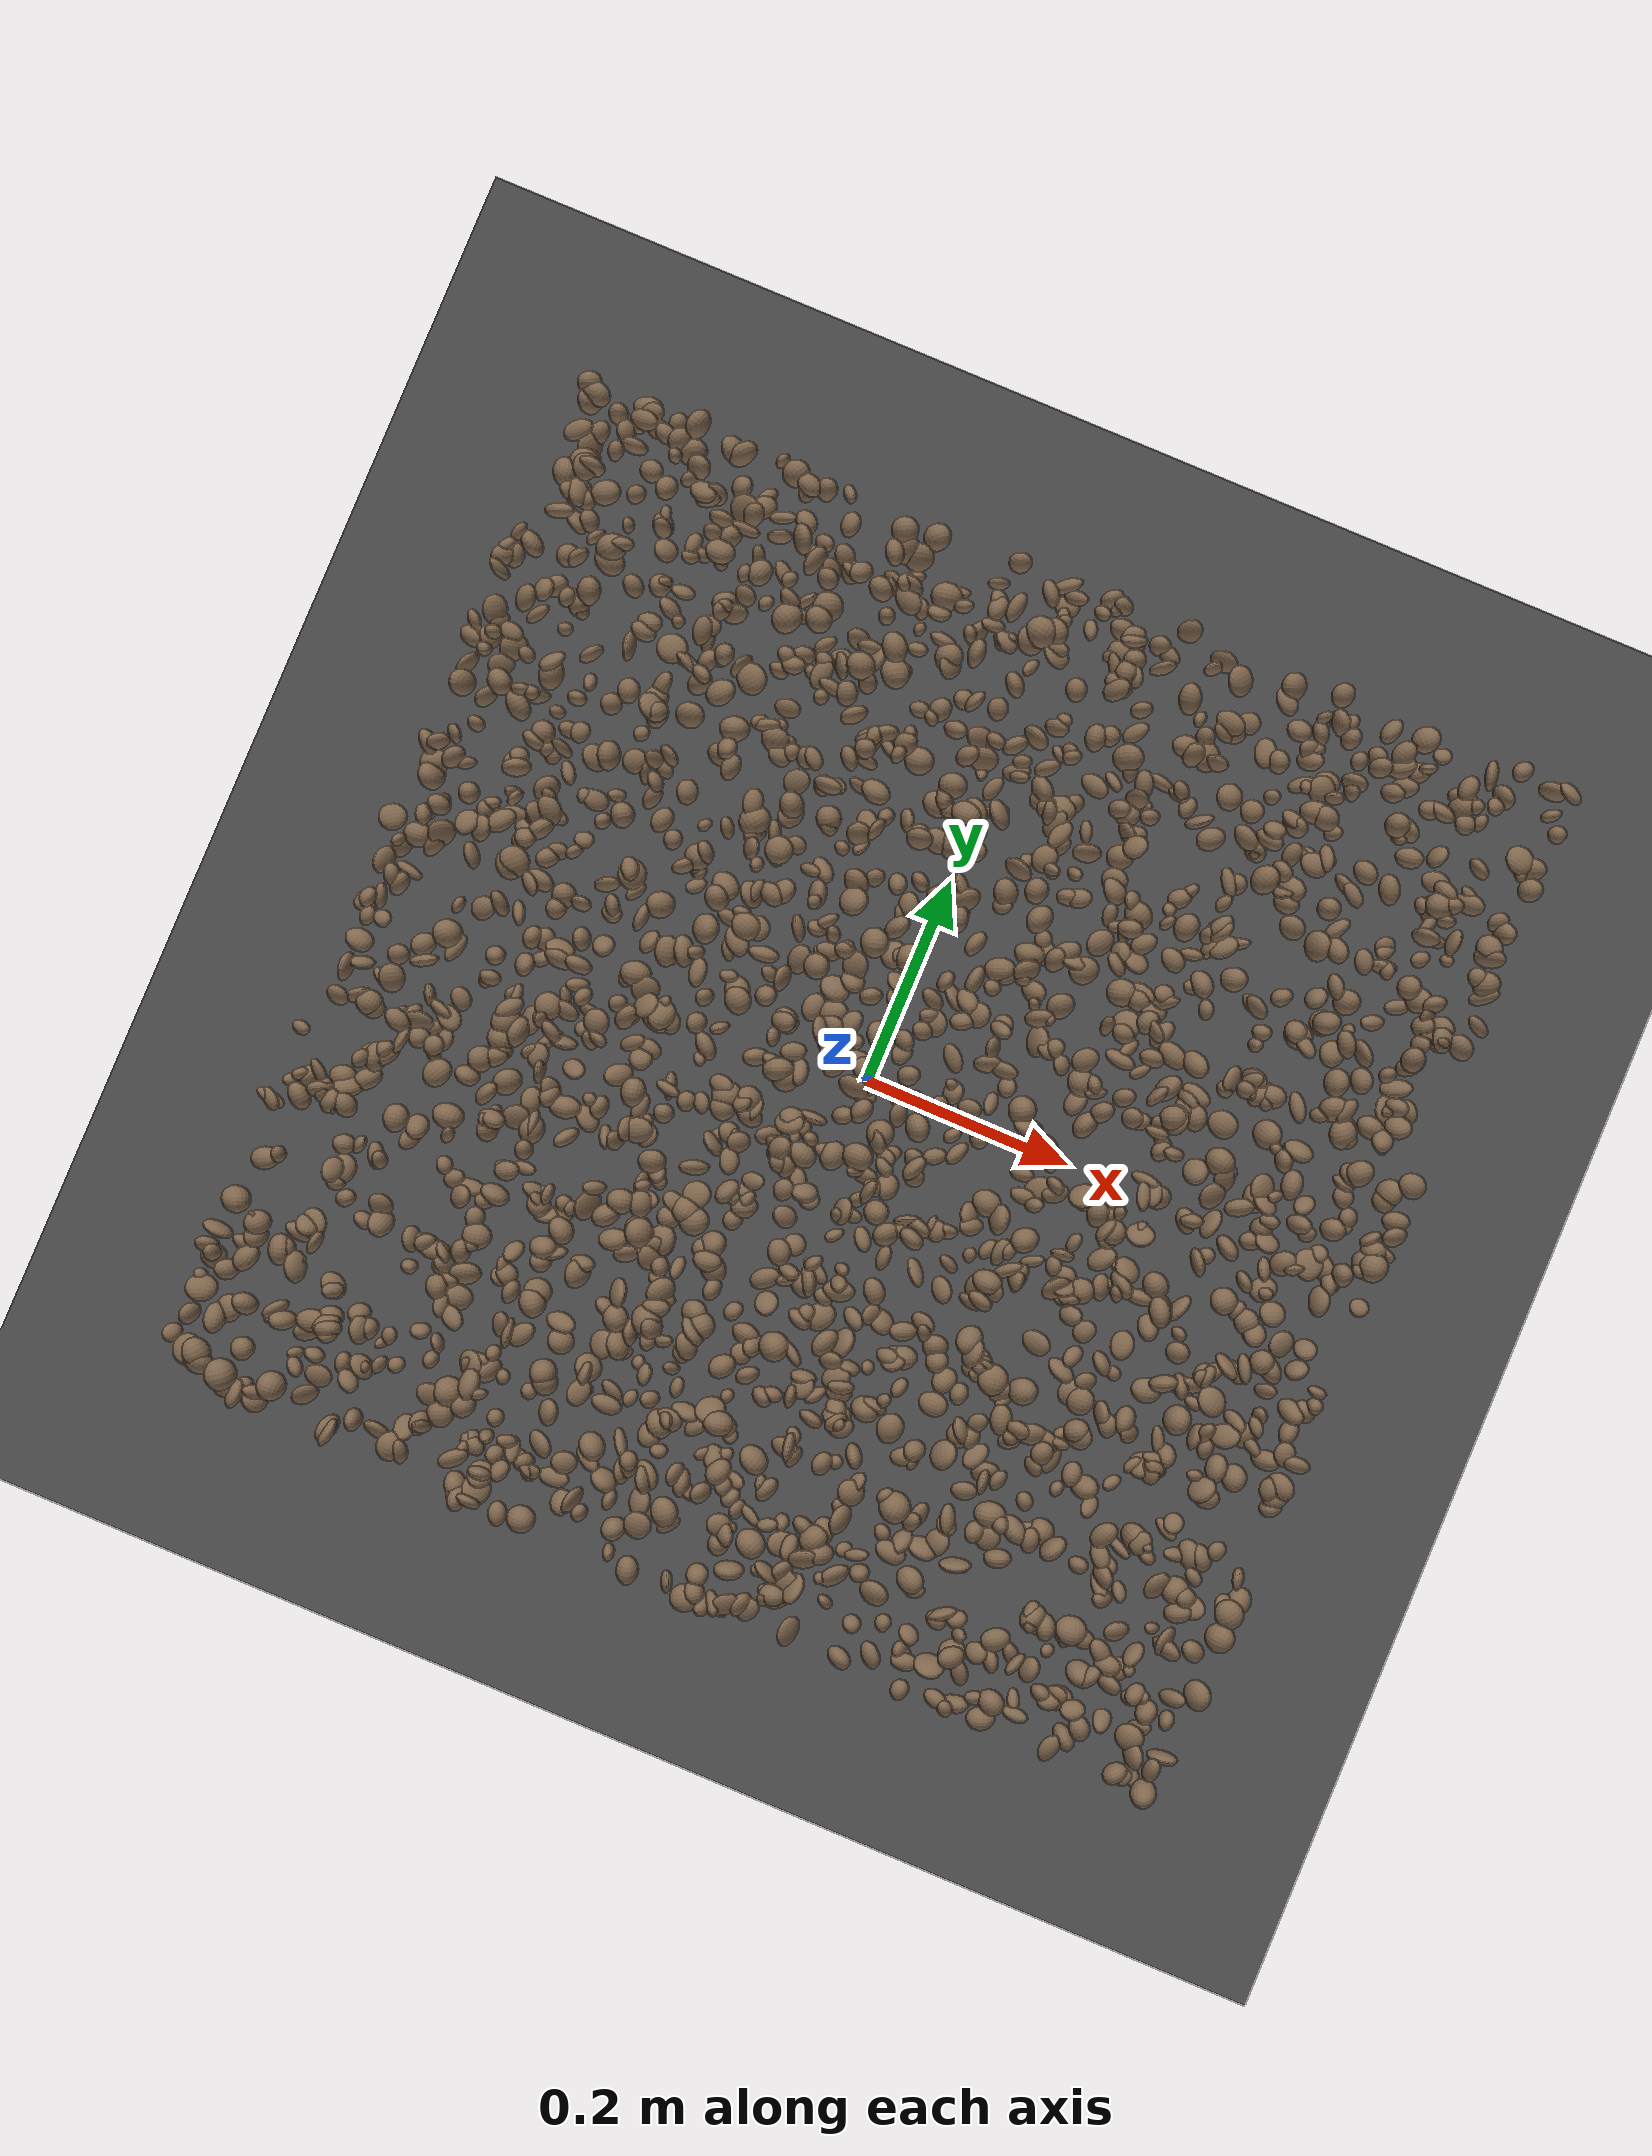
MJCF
<mujoco model="rocky_terrain_scene">
    <compiler angle="radian" inertiafromgeom="true" />
    <option timestep="0.002" gravity="0 0 -9.81" />

    <worldbody>
        <light name="sunlight" pos="5 5 5" dir="-1 -1 -1" diffuse="1 1 1" specular="0.5 0.5 0.5" ambient="0.5 0.5 0.5" />

        <geom name="ground_plane" type="plane" size="50 50 0.1" rgba="0.3 0.3 0.3 1" />

        <body name="rocky_terrain_body">

        <geom name="rock1" type="ellipsoid" size="0.005670869078484325 0.005922826611413034 0.014029279136407297" pos="-0.33735466468013386 -0.1948441670437332 0.0020420457299551707" quat="0.16524178142365856 0.015551032106801718 0.17798443410969939 0.6412227523598403" rgba="0.5 0.4 0.3 1" /><geom name="rock2" type="ellipsoid" size="0.008337935356408036 0.005250064917180751 0.01441459254597828" pos="0.07561854723254269 0.27659524546968317 0.013331748212049568" quat="0.09222472690543299 0.04634565402419651 0.4443960289168885 0.41703359015348207" rgba="0.5 0.4 0.3 1" /><geom name="rock3" type="ellipsoid" size="0.014216506240714546 0.005047648234640183 0.007178369038723599" pos="-0.41668612698978613 -0.40911303239042573 0.000812564223224314" quat="0.4871859815165515 0.34836765040016315 0.002954833632712989 0.1614915344505723" rgba="0.5 0.4 0.3 1" /><geom name="rock4" type="ellipsoid" size="0.011154395033177134 0.007019648829460334 0.013468695412794104" pos="0.29709434129457213 -0.32504701090757937 0.003120148333676035" quat="0.29356068112345274 0.40145729543962144 0.18680351770532275 0.11817850573160298" rgba="0.5 0.4 0.3 1" /><geom name="rock5" type="ellipsoid" size="0.011368197350993326 0.005437893346750515 0.006953536901488011" pos="-0.2802410601201273 -0.3390118143205022 0.012952642896437223" quat="0.1860726238545809 0.26000711494021117 0.36150556210347484 0.19241469910173312" rgba="0.5 0.4 0.3 1" /><geom name="rock6" type="ellipsoid" size="0.014574010765713935 0.009143110413404387 0.012682291926069936" pos="-0.022778914061388655 0.11692568535337255 0.0038647422625664334" quat="0.2726807131903378 0.038776504925107716 0.3528975234689996 0.33564525841555487" rgba="0.5 0.4 0.3 1" /><geom name="rock7" type="ellipsoid" size="0.0053473566759587015 0.006615645493450248 0.014435116471046339" pos="-0.15503084933455125 -0.44356507205587536 0.004944399643803868" quat="0.3352119182028163 0.3495123432085211 0.056902888943810084 0.25837284964485246" rgba="0.5 0.4 0.3 1" /><geom name="rock8" type="ellipsoid" size="0.011253842679138901 0.013483744532347856 0.008428614613007418" pos="-0.07950648405998273 -0.1430221218990465 0.008000745263475465" quat="0.19363118599823873 0.4861745253736073 0.02064010341081523 0.29955418521733873" rgba="0.5 0.4 0.3 1" /><geom name="rock9" type="ellipsoid" size="0.005450864368079114 0.0055899613865835526 0.010802142360477433" pos="0.020363415820536468 0.3126096648167389 0.008242087109934739" quat="0.07688486029876522 0.2939641074539784 0.06525945662398018 0.5638915756232763" rgba="0.5 0.4 0.3 1" /><geom name="rock10" type="ellipsoid" size="0.005029060078580823 0.011777235904314818 0.010525875598803299" pos="0.4249109763298803 -0.00878313074580317 0.013627181665518216" quat="0.10813050222099067 0.3214367107101543 0.4980602304262388 0.07237255664261623" rgba="0.5 0.4 0.3 1" /><geom name="rock11" type="ellipsoid" size="0.012551498424956124 0.011127172036853102 0.008682642222791997" pos="0.42180505610190144 0.3640475487805349 0.013815882565730785" quat="0.1844534738474223 0.019317798682396112 0.3963795868898848 0.39984914058029686" rgba="0.5 0.4 0.3 1" /><geom name="rock12" type="ellipsoid" size="0.011861606724790894 0.010836395368900107 0.00892389199770999" pos="0.2772896386630037 -0.2514854069266881 0.014494000427964279" quat="0.31411957035115606 0.2206845355672719 0.014141948009545015 0.45105394607202703" rgba="0.5 0.4 0.3 1" /><geom name="rock13" type="ellipsoid" size="0.013869542723782921 0.009735402504135576 0.008244786413987555" pos="-0.05947735128010123 -0.28762150510223483 0.008407082589524328" quat="0.24198871740333805 0.15897022610911798 0.05337470986125442 0.5456663466262894" rgba="0.5 0.4 0.3 1" /><geom name="rock14" type="ellipsoid" size="0.0074377407023463035 0.009020259639305125 0.006545855678765708" pos="0.2831432789466617 0.47496975033545075 0.013822058455098651" quat="0.10397135276536397 0.4309602660869788 0.06129528342266676 0.40377309772499054" rgba="0.5 0.4 0.3 1" /><geom name="rock15" type="ellipsoid" size="0.009943320533938288 0.00520278731973982 0.01300051334374551" pos="-0.22602101775815142 -0.028168821881241257 0.005553637242659186" quat="0.11289950655671331 0.1400398558705225 0.46863531978889755 0.27842531778386675" rgba="0.5 0.4 0.3 1" /><geom name="rock16" type="ellipsoid" size="0.00646462844572993 0.0050084450034797315 0.007467315507856328" pos="-0.09437213588585058 -0.3186364648868507 0.003918985301552687" quat="0.43745072097242693 0.16217183710771596 0.06813482985640122 0.33224261206345596" rgba="0.5 0.4 0.3 1" /><geom name="rock17" type="ellipsoid" size="0.011740771200268764 0.010106285905764489 0.00718796411913376" pos="-0.456471034336834 -0.199855480874513 0.010857289343411495" quat="0.22284968091160623 0.2774695886406682 0.23338921007413765 0.2662915203735879" rgba="0.5 0.4 0.3 1" /><geom name="rock18" type="ellipsoid" size="0.01266556063989026 0.0113329788713264 0.011801604592002562" pos="-0.4509618235354228 -0.1101300763608698 0.004788268340621602" quat="0.005310866554172203 0.07887321774406308 0.4211271298930516 0.4946887858087131" rgba="0.5 0.4 0.3 1" /><geom name="rock19" type="ellipsoid" size="0.013746693169538471 0.010905254341591019 0.009454505002021774" pos="0.4893799416484569 -0.19520708154455468 0.014031670524075748" quat="0.08645075360207005 0.17015223553271688 0.6242894603306398 0.11910755053457317" rgba="0.5 0.4 0.3 1" /><geom name="rock20" type="ellipsoid" size="0.007402207648495716 0.010730521510417344 0.008484416068758513" pos="0.042334722919724954 -0.08827123314939289 0.010481403142133812" quat="0.4109290344423002 0.23455093083709727 0.06371813388906107 0.2908019008315415" rgba="0.5 0.4 0.3 1" /><geom name="rock21" type="ellipsoid" size="0.009117943121393699 0.013279358791256503 0.01208323205789327" pos="-0.24983220220382008 -0.04667322301828847 0.013077903419368807" quat="0.4624044682267785 0.0522659883250964 0.3731865020944284 0.11214304135369664" rgba="0.5 0.4 0.3 1" /><geom name="rock22" type="ellipsoid" size="0.008401074182353165 0.009688112936876693 0.008350484039602379" pos="-0.04633901747708524 -0.10055547427525335 0.01024430150054616" quat="0.4978779260662706 0.1003803351763915 0.13329227693625573 0.26844946182108215" rgba="0.5 0.4 0.3 1" /><geom name="rock23" type="ellipsoid" size="0.007678592063012819 0.007600881409950246 0.01103162619172662" pos="0.2736956850047415 -0.4945639507261367 0.008165509912576122" quat="0.19973643090816245 0.33197298743892184 0.10928357746520094 0.35900700418771475" rgba="0.5 0.4 0.3 1" /><geom name="rock24" type="ellipsoid" size="0.014350652277050756 0.013072029000831157 0.006854672774180238" pos="0.13126661875079815 -0.37828777891702003 0.009852272392494291" quat="0.3335180084258276 0.17846502063886935 0.18674914996415043 0.3012678209711526" rgba="0.5 0.4 0.3 1" /><geom name="rock25" type="ellipsoid" size="0.013449618160558095 0.009259934606320156 0.014386718613058163" pos="-0.07556971942472224 0.14690662514789343 0.014857479252247736" quat="0.3887274904626361 0.21534072819341202 0.12807428922946965 0.26785749211448223" rgba="0.5 0.4 0.3 1" /><geom name="rock26" type="ellipsoid" size="0.013947287506677473 0.010914539574091806 0.014025008565996377" pos="-0.13901025290550162 -0.20833903755055072 0.013675038471806344" quat="0.12041021802481187 0.32347755280638063 0.39526999441233374 0.16084223475647383" rgba="0.5 0.4 0.3 1" /><geom name="rock27" type="ellipsoid" size="0.01191919028170875 0.010225773328303989 0.014394894324883434" pos="0.3444154430358872 -0.16246836522031405 0.004046747671759768" quat="0.24962367726282456 0.17256201478338806 0.38727832840147913 0.19053597955230836" rgba="0.5 0.4 0.3 1" /><geom name="rock28" type="ellipsoid" size="0.010806186328412508 0.012963007856964626 0.014100336544420666" pos="0.3675295286818451 0.21172158362800786 0.010808046445001863" quat="0.34097392096443035 0.0765554351968362 0.0025404936357900187 0.5799301502029434" rgba="0.5 0.4 0.3 1" /><geom name="rock29" type="ellipsoid" size="0.008751189886506498 0.013250123989654548 0.010150881972497756" pos="0.3385615812943671 0.4673164324382565 0.01319739505454659" quat="0.45545300125889 0.14005261514470962 0.3873003948189522 0.01719398877744819" rgba="0.5 0.4 0.3 1" /><geom name="rock30" type="ellipsoid" size="0.013555178365968049 0.007118381783510649 0.013621450051215414" pos="-0.11788907528616177 -0.21479701195435785 0.0034453516101666157" quat="0.021318042260688164 0.30353818820346423 0.2640434893947439 0.4111002801411036" rgba="0.5 0.4 0.3 1" /><geom name="rock31" type="ellipsoid" size="0.010674139022584718 0.007094920666891432 0.007327683773600765" pos="-0.28593959869088315 0.19428089384579184 0.0005603589564954992" quat="0.1454781115252757 0.12226605142392136 0.1310674931326541 0.6011883439181489" rgba="0.5 0.4 0.3 1" /><geom name="rock32" type="ellipsoid" size="0.006931835471925253 0.011890186544010105 0.007159210838488171" pos="-0.38386717569984563 -0.23910856024923188 0.01164061093541959" quat="0.07586851598711784 0.004944341196423707 0.5681108377583001 0.35107630505815823" rgba="0.5 0.4 0.3 1" /><geom name="rock33" type="ellipsoid" size="0.0081019001895474 0.012163063581672656 0.01422227850677895" pos="-0.04683254960973782 -0.4087293004182636 0.010737211679437914" quat="0.416082653720634 0.2882727749740676 0.23747307482855667 0.05817149647674172" rgba="0.5 0.4 0.3 1" /><geom name="rock34" type="ellipsoid" size="0.007344454142170548 0.009840451205471851 0.009036672722583213" pos="0.3174078718043477 0.18175300702891506 0.002113087663796769" quat="0.19583812134652523 0.2635826502775176 0.23540622084942542 0.30517300752653176" rgba="0.5 0.4 0.3 1" /><geom name="rock35" type="ellipsoid" size="0.009547183218450595 0.0074288245985487614 0.0063298635910865545" pos="0.26145080365106566 0.180670492832413 0.005858520410897207" quat="0.10817765391503373 0.27452070087928837 0.3827220219418294 0.2345796232638486" rgba="0.5 0.4 0.3 1" /><geom name="rock36" type="ellipsoid" size="0.007448941627160623 0.005574795061837896 0.011677071743493847" pos="0.3362152704668555 -0.2797954735515954 0.009259130677836465" quat="0.0249998319971356 0.08399155604097186 0.584092833989933 0.3069157779719597" rgba="0.5 0.4 0.3 1" /><geom name="rock37" type="ellipsoid" size="0.006498977303036972 0.005094215093920817 0.013195230245692077" pos="0.005472157292678359 0.4851178459230646 0.010616526112508453" quat="0.27381868695012873 0.20478777997186995 0.13734638175134967 0.38404715132665157" rgba="0.5 0.4 0.3 1" /><geom name="rock38" type="ellipsoid" size="0.010473996151903826 0.006861974295252122 0.011362733454653213" pos="0.1423267294509667 0.09140378132510685 0.01131168471148876" quat="0.2823593052908664 0.1849073251257228 0.3383025998897216 0.19443076969368916" rgba="0.5 0.4 0.3 1" /><geom name="rock39" type="ellipsoid" size="0.006936792342570855 0.005281828903444259 0.010099261815110441" pos="-0.21430704291186298 0.10426838205660349 0.013907123912498879" quat="0.19386213669743402 0.08597213830460941 0.42266190823786925 0.29750381676008725" rgba="0.5 0.4 0.3 1" /><geom name="rock40" type="ellipsoid" size="0.0075225574287545146 0.013422388552131598 0.005532716285745753" pos="-0.2033226775233079 -0.1400260263523564 0.0014246661689521478" quat="0.06033643155601142 0.37955195200515596 0.2158573483608688 0.34425426807796383" rgba="0.5 0.4 0.3 1" /><geom name="rock41" type="ellipsoid" size="0.009193727135988879 0.014021653381382625 0.012219539553324336" pos="-0.05061294078556 0.03292581789361437 0.004391830623573407" quat="0.3450351786611701 0.3202905049613056 0.32032768617835145 0.014346630199172834" rgba="0.5 0.4 0.3 1" /><geom name="rock42" type="ellipsoid" size="0.006914689066378774 0.014006438323583746 0.008873055130189588" pos="0.24705061929718708 -0.25394163249201807 0.0006205100065575208" quat="0.16961570893472266 0.2442487558753137 0.4291066284788614 0.1570289067111022" rgba="0.5 0.4 0.3 1" /><geom name="rock43" type="ellipsoid" size="0.005034453579008657 0.009640503238369576 0.01212487997716507" pos="-0.47184833154495 -0.07857487260547469 0.0024664206637729134" quat="0.05277043558037784 0.3784927051090655 0.33691338492363354 0.23182347438692316" rgba="0.5 0.4 0.3 1" /><geom name="rock44" type="ellipsoid" size="0.0054994428568687 0.011907542279131893 0.011195264606651805" pos="-0.01099858947091259 -0.4443091893812978 0.005648498418231253" quat="0.1774105618915894 0.09962444676204099 0.3324923793572366 0.390472611989133" rgba="0.5 0.4 0.3 1" /><geom name="rock45" type="ellipsoid" size="0.006151451033859826 0.00880115710296177 0.01398727538460929" pos="0.052794896993768825 -0.4940653013127483 0.007049421866309618" quat="0.6252043768331048 0.1619402167352951 0.13723845060246367 0.0756169558291363" rgba="0.5 0.4 0.3 1" /><geom name="rock46" type="ellipsoid" size="0.008027438234484058 0.012638375212204175 0.01289878706552702" pos="0.09668668440289896 -0.1985987134477888 0.0015190619339086509" quat="0.27296507143038107 0.3575653500514123 0.057837839865475575 0.31163173865273097" rgba="0.5 0.4 0.3 1" /><geom name="rock47" type="ellipsoid" size="0.012749138702868253 0.009513569891201949 0.007574333801333125" pos="0.04256189874477179 0.15431832639796916 0.013093524649290146" quat="0.30706118732736776 0.27106531872778417 0.22816160953214568 0.19371188441270237" rgba="0.5 0.4 0.3 1" /><geom name="rock48" type="ellipsoid" size="0.0060510072168484695 0.012207562998489022 0.008871886366397113" pos="0.16047073277039015 0.24781213285516135 0.00533682095102063" quat="0.2873203812142684 0.4648505664444046 0.04246199764410537 0.20536705469722166" rgba="0.5 0.4 0.3 1" /><geom name="rock49" type="ellipsoid" size="0.011365798271520303 0.01067272397718124 0.01461420362240895" pos="0.291427322528251 0.31338681724675355 0.008293827318452544" quat="0.4077318265989723 0.19864139320646748 0.08776608472218972 0.30586069547237055" rgba="0.5 0.4 0.3 1" /><geom name="rock50" type="ellipsoid" size="0.013149806256143579 0.007474337809593001 0.005933290729789712" pos="-0.17241900389549025 -0.11768218069509473 0.0007000313623818544" quat="0.10072021791381758 0.34627205630834945 0.3023884177430993 0.25061930803473365" rgba="0.5 0.4 0.3 1" /><geom name="rock51" type="ellipsoid" size="0.013891876321541662 0.007007960763728347 0.007560442382069592" pos="0.09432318421890429 0.15735759687097128 0.012140143455586639" quat="0.20494682114259255 0.2856929989414915 0.3318865827308395 0.17747359718507652" rgba="0.5 0.4 0.3 1" /><geom name="rock52" type="ellipsoid" size="0.011509429756798382 0.009447549505128511 0.014657662433407069" pos="-0.0953766677701463 -0.2830981128406095 0.014564479190566502" quat="0.12754300272668803 0.3863426522438776 0.46697997721556267 0.019134367813871643" rgba="0.5 0.4 0.3 1" /><geom name="rock53" type="ellipsoid" size="0.00597079204829374 0.006080988750340755 0.012565166891276458" pos="0.10206009636133706 0.24986916796714587 0.005916176452466627" quat="0.4908360823578094 0.12661052259507874 0.04983633946001095 0.33271705558710096" rgba="0.5 0.4 0.3 1" /><geom name="rock54" type="ellipsoid" size="0.011485053310785658 0.008886222822655047 0.007820755082332011" pos="-0.47775858346916156 0.10345694033932229 0.0006840575680254746" quat="0.33951354742187567 0.26265793757473394 0.24097245680132434 0.15685605820206605" rgba="0.5 0.4 0.3 1" /><geom name="rock55" type="ellipsoid" size="0.006606154006588809 0.007085728942067122 0.006628803393658013" pos="0.10728865344786132 -0.332606881147405 0.004973702328817294" quat="0.2338890996901061 0.2640716841196918 0.39305640580557816 0.10898281038462382" rgba="0.5 0.4 0.3 1" /><geom name="rock56" type="ellipsoid" size="0.013710471496072109 0.011959287897824276 0.006308335467005193" pos="-0.4493726251716379 0.3751213915479217 0.0008444460228787692" quat="0.24451026022052363 0.014945174509615826 0.29934772309052465 0.4411968421793359" rgba="0.5 0.4 0.3 1" /><geom name="rock57" type="ellipsoid" size="0.00937263907809813 0.009544919452842245 0.007614163283802132" pos="-0.032079265567237614 -0.24159268604179107 0.007108223443596833" quat="0.33901761235196387 0.24193853892795017 0.4161848122860299 0.002859036434056097" rgba="0.5 0.4 0.3 1" /><geom name="rock58" type="ellipsoid" size="0.013918477710131695 0.011704315761088237 0.0141683690801594" pos="-0.23901801215375584 0.2523925705136427 0.006507606379438504" quat="0.5810309175647075 0.0022174927515307926 0.31606918948313173 0.10068240020063005" rgba="0.5 0.4 0.3 1" /><geom name="rock59" type="ellipsoid" size="0.007798780987030333 0.0126645808465734 0.007736366476060337" pos="0.4903264050133497 -0.11645119248329805 0.01110261247909619" quat="0.2309920789904976 0.19844276930981802 0.2701853038010389 0.30037984789864547" rgba="0.5 0.4 0.3 1" /><geom name="rock60" type="ellipsoid" size="0.010447260413193195 0.005680860674192726 0.011667953956189674" pos="-0.03824560313832537 0.4217158947580434 0.01419182702957698" quat="0.34274707638260826 0.24792393174663302 0.34316279894601076 0.06616619292474799" rgba="0.5 0.4 0.3 1" /><geom name="rock61" type="ellipsoid" size="0.005635037686209825 0.009388744182906009 0.009699993930694206" pos="0.486355054749411 0.4689699739197486 0.006691779404282792" quat="0.0774944639453917 0.23673530459146544 0.4553893503903328 0.23038088107281005" rgba="0.5 0.4 0.3 1" /><geom name="rock62" type="ellipsoid" size="0.012764279827796984 0.01311170094901553 0.01301589202499824" pos="-0.08218073079549926 0.3892925602040219 0.011065149466033397" quat="0.08867540885948624 0.25133551048684205 0.07074039203655302 0.5892486886171187" rgba="0.5 0.4 0.3 1" /><geom name="rock63" type="ellipsoid" size="0.01159505127304276 0.013009753851377422 0.007951530562680734" pos="-0.3049769307918698 -0.17537736220456845 0.005112477102282099" quat="0.30678670076725817 0.17378651238072348 0.21278356296215112 0.30664322388986726" rgba="0.5 0.4 0.3 1" /><geom name="rock64" type="ellipsoid" size="0.01385870938381576 0.009378433606848459 0.007990092120931996" pos="0.262211760366031 0.4303334071177598 0.00620146677270123" quat="0.013122849074287533 0.7105207817655227 0.002703346188766001 0.27365302297142374" rgba="0.5 0.4 0.3 1" /><geom name="rock65" type="ellipsoid" size="0.005331404482930494 0.0071041369413032355 0.010735683496731006" pos="0.22955210569389628 0.2224239586042437 0.009179720276502273" quat="0.17781831664159767 0.2722203523113321 0.2229544714840667 0.32700685956300346" rgba="0.5 0.4 0.3 1" /><geom name="rock66" type="ellipsoid" size="0.005103960978341981 0.014215256777767821 0.013321534426548525" pos="0.3278211571984738 0.13711307630309888 0.0038771817235016322" quat="0.35609891830701096 0.32543610993784516 0.28668404834066413 0.03178092341447974" rgba="0.5 0.4 0.3 1" /><geom name="rock67" type="ellipsoid" size="0.005198851094853438 0.012393072651578286 0.011081017770885122" pos="-0.20384373704156555 -0.25581840937151146 0.010215621527638104" quat="0.31236483938956777 0.13134337070259317 0.04059898650468122 0.5156928034031578" rgba="0.5 0.4 0.3 1" /><geom name="rock68" type="ellipsoid" size="0.008418821725137447 0.005962572591365468 0.01260233879202011" pos="-0.2799379014195137 -0.04741460582174695 0.011040534648036195" quat="0.18515957656299956 0.4044143613187864 0.1834856210371923 0.22694044108102188" rgba="0.5 0.4 0.3 1" /><geom name="rock69" type="ellipsoid" size="0.009535468716213838 0.014818447934255685 0.013228993503840662" pos="-0.11789794081642713 -0.20759020414844398 0.003630390725675832" quat="0.5766938831294972 0.05108798705500282 0.34727228090408085 0.02494584891141908" rgba="0.5 0.4 0.3 1" /><geom name="rock70" type="ellipsoid" size="0.009625742023162437 0.010077418549742728 0.005376447044741707" pos="0.27491919257614195 -0.2657558464862957 0.009984290532758521" quat="0.026269922786625186 0.29064658964411866 0.40145854611897197 0.2816249414502841" rgba="0.5 0.4 0.3 1" /><geom name="rock71" type="ellipsoid" size="0.010828106452044173 0.01398979678255359 0.005405096679295868" pos="0.04608632166552984 -0.29266877697658356 0.007681361203630208" quat="0.2639758816735636 0.1971595602508144 0.30772154104331545 0.2311430170323064" rgba="0.5 0.4 0.3 1" /><geom name="rock72" type="ellipsoid" size="0.009129817901121846 0.010490567376012793 0.005390117648845064" pos="0.4120369042284858 -0.26375418832923614 0.01340791079924771" quat="0.2114951770284613 0.713904325085023 0.004189989540616486 0.07041050834589921" rgba="0.5 0.4 0.3 1" /><geom name="rock73" type="ellipsoid" size="0.012664718105459641 0.01471943819972792 0.013412568841812838" pos="-0.3256378096352597 -0.09395725736857741 0.004364997145674796" quat="0.20424037203524856 0.29105652922323744 0.25821275696999263 0.24649034177152135" rgba="0.5 0.4 0.3 1" /><geom name="rock74" type="ellipsoid" size="0.007827799216057882 0.008915229247918793 0.005747160217008751" pos="0.4575296639512485 -0.49318220844921434 0.010439727036390884" quat="0.29158118864958105 0.020137174339547446 0.11001929126762003 0.5782623457432515" rgba="0.5 0.4 0.3 1" /><geom name="rock75" type="ellipsoid" size="0.012184123016793256 0.005869807179750632 0.009565237456490797" pos="0.32731377407357876 -0.39485676135919634 0.009434931379406743" quat="0.33224402354988103 0.302305602012137 0.08892988543537375 0.27652048900260817" rgba="0.5 0.4 0.3 1" /><geom name="rock76" type="ellipsoid" size="0.010769638710054631 0.007933642934587669 0.010860431057195603" pos="0.23095706485915368 0.36671891134468826 0.0035111620057157087" quat="0.2920896784110903 0.2906541191946395 0.18510117620387473 0.23215502619039552" rgba="0.5 0.4 0.3 1" /><geom name="rock77" type="ellipsoid" size="0.011450369574802676 0.008569346553744113 0.008838130181268765" pos="-0.033069324949160595 0.0005110989078905837 0.012678358567052002" quat="0.2742867846911517 0.38528332453012437 0.19048322119210837 0.1499466695866156" rgba="0.5 0.4 0.3 1" /><geom name="rock78" type="ellipsoid" size="0.00857646144779679 0.009755456390015769 0.011189968226830355" pos="0.37873396748853905 -0.22469486949256712 0.007563979135621874" quat="0.13306718097046552 0.4198278946571413 0.29260776331874633 0.15449716105364686" rgba="0.5 0.4 0.3 1" /><geom name="rock79" type="ellipsoid" size="0.00737629601384205 0.007805228572561804 0.005636234029128684" pos="-0.20577261588566065 -0.2128012983955695 0.008044613847673809" quat="0.4470528856725739 0.06790455746869666 0.2750966968598593 0.2099458599988701" rgba="0.5 0.4 0.3 1" /><geom name="rock80" type="ellipsoid" size="0.010342822893024052 0.012239397273004835 0.007713752040453988" pos="0.104012318698817 0.2270494400751396 0.00957372265570244" quat="0.42320607837738183 0.4399163108241053 0.12199591368063342 0.014881697117879336" rgba="0.5 0.4 0.3 1" /><geom name="rock81" type="ellipsoid" size="0.011247993040639094 0.006701376723192495 0.005510165230969902" pos="-0.2245760946850609 0.4934198247255196 0.01187875697689399" quat="0.2582068670405729 0.08227650350876067 0.41584631520699156 0.2436703142436748" rgba="0.5 0.4 0.3 1" /><geom name="rock82" type="ellipsoid" size="0.006554107048369671 0.014623806639546537 0.00693657211123248" pos="0.0708085211133932 0.007710736757717274 0.006681747833068852" quat="0.3036729804270037 0.1973752385418894 0.18483530110075722 0.31411647993034963" rgba="0.5 0.4 0.3 1" /><geom name="rock83" type="ellipsoid" size="0.013436030893033534 0.011768294315540107 0.014159268683339433" pos="-0.10775714845174578 -0.17288166661737114 0.00928293353359217" quat="0.3960811199092236 0.17863949633987644 0.3200104602634484 0.1052689234874515" rgba="0.5 0.4 0.3 1" /><geom name="rock84" type="ellipsoid" size="0.014248378598926564 0.010928193259167138 0.00928021242079953" pos="-0.46180781264232096 -0.36820180448990214 0.010687531930929013" quat="0.10973136570421538 0.4824327351849555 0.2763529749890819 0.13148292412174722" rgba="0.5 0.4 0.3 1" /><geom name="rock85" type="ellipsoid" size="0.008373825184021568 0.011497090201647972 0.012166966090650959" pos="0.17887331464725564 -0.49460504999751154 0.006632829164177727" quat="0.3676830735704591 0.23241636188008785 0.22657130543254378 0.1733292591169093" rgba="0.5 0.4 0.3 1" /><geom name="rock86" type="ellipsoid" size="0.013015570217760841 0.01067703760335385 0.013221678319945796" pos="0.3529719486230922 0.4887073604398767 0.009186755656442978" quat="0.2671568677807155 0.04092833883371046 0.3440752438921874 0.34783954949338663" rgba="0.5 0.4 0.3 1" /><geom name="rock87" type="ellipsoid" size="0.01376305312244814 0.01100571678002215 0.005127606671852544" pos="0.06241938738524011 -0.3352425662932029 0.014456918790241136" quat="0.25799470558933313 0.19736984297351695 0.29683170656186514 0.24780374487528484" rgba="0.5 0.4 0.3 1" /><geom name="rock88" type="ellipsoid" size="0.009204280439695227 0.00854815443808089 0.012809767453292622" pos="-0.36119155984636353 -0.02552884154159052 0.004003047266650187" quat="0.6365128776562042 0.09722309606027336 0.08225739815562436 0.18400662812789811" rgba="0.5 0.4 0.3 1" /><geom name="rock89" type="ellipsoid" size="0.010360995738433416 0.013394817809404349 0.008918949017109594" pos="-0.2734524255576757 0.31082298569558486 0.014105825131316195" quat="0.19542349351500027 0.29767740784294794 0.27215925642698596 0.2347398422150658" rgba="0.5 0.4 0.3 1" /><geom name="rock90" type="ellipsoid" size="0.011541108641988967 0.012873227580889591 0.011204499912904009" pos="0.13479654261507767 0.28109338026368114 0.0012580024606453238" quat="0.04434241199101224 0.36016669484530145 0.4630339129430946 0.13245698022059169" rgba="0.5 0.4 0.3 1" /><geom name="rock91" type="ellipsoid" size="0.012021435868757813 0.00546455995372542 0.012602680675014707" pos="0.18458834882757502 0.1960771688686601 0.009829379410224992" quat="0.3676993427232728 0.2235295148943652 0.3054649477472167 0.10330619463514527" rgba="0.5 0.4 0.3 1" /><geom name="rock92" type="ellipsoid" size="0.0050384341532373105 0.0076624694174239226 0.013729728513547514" pos="-0.4664359501651396 -0.18622541925856384 0.012725986211696707" quat="0.30731943748448765 0.3811309998075892 0.2867972466647007 0.024752316043222512" rgba="0.5 0.4 0.3 1" /><geom name="rock93" type="ellipsoid" size="0.013806274526144156 0.013122413130500228 0.0077341324062197535" pos="-0.10958191664002093 0.1416738028711354 0.000897280383335407" quat="0.16881983599194764 0.25495883638293176 0.3278666186014024 0.24835470902371815" rgba="0.5 0.4 0.3 1" /><geom name="rock94" type="ellipsoid" size="0.00803968177200694 0.005398384022771393 0.00927058133497493" pos="-0.14433497048027089 0.17509644602729768 0.008283564728347187" quat="0.22537903726075795 0.36560172241199856 0.21174628701568246 0.19727295331156106" rgba="0.5 0.4 0.3 1" /><geom name="rock95" type="ellipsoid" size="0.0060002010505868794 0.011032502228080724 0.009683507059831134" pos="-0.06959431626663903 -0.44251584924580933 0.01188604668305163" quat="0.0009639138884824325 0.015447446868857441 0.5615465247844879 0.42204211445817225" rgba="0.5 0.4 0.3 1" /><geom name="rock96" type="ellipsoid" size="0.0062431803319525124 0.009744898804555726 0.01172744725493377" pos="0.3918532826455967 -0.4544923118961871 0.01418013260780627" quat="0.023455358577181822 0.38214518973999334 0.24651664067233858 0.3478828110104862" rgba="0.5 0.4 0.3 1" /><geom name="rock97" type="ellipsoid" size="0.007137030759180939 0.006449795938320379 0.006135882663959699" pos="-0.30885514236529676 -0.16695595127785523 0.014795557478259034" quat="0.24459010758794703 0.27990036597323625 0.30335258150166067 0.17215694493715603" rgba="0.5 0.4 0.3 1" /><geom name="rock98" type="ellipsoid" size="0.006456145913017156 0.007770136559069732 0.01408608408088071" pos="0.3730151383417527 -0.343916176892185 0.003579196393088727" quat="0.4145329096343409 0.26960805259192505 0.012304332853662173 0.30355470492007186" rgba="0.5 0.4 0.3 1" /><geom name="rock99" type="ellipsoid" size="0.012140484808775782 0.005239296897779224 0.012915425970344556" pos="0.37773102637999356 0.03663028501962351 0.013169990996776754" quat="0.38771419497032167 0.20879787570403985 0.3450089979827879 0.05847893134285055" rgba="0.5 0.4 0.3 1" /><geom name="rock100" type="ellipsoid" size="0.010453101432641925 0.014451580695796568 0.005303348549127739" pos="0.12814392511723594 0.33407432978084506 0.013117676048006134" quat="0.0065653792763184105 0.057154401605509386 0.5674901898966852 0.368790029221487" rgba="0.5 0.4 0.3 1" /><geom name="rock101" type="ellipsoid" size="0.00640224806171513 0.013763820378652286 0.007573550304478377" pos="0.047103440299564925 -0.18081192424972348 0.01435094856321845" quat="0.08407734096912695 0.22337946420389232 0.3254368776736785 0.3671063171533023" rgba="0.5 0.4 0.3 1" /><geom name="rock102" type="ellipsoid" size="0.012378403881422376 0.010375739029385815 0.0055850542621830755" pos="-0.13513294388161212 -0.3470742489391002 0.009293904631877138" quat="0.20322585878793784 0.28909533861069514 0.2673957509559117 0.24028305164545527" rgba="0.5 0.4 0.3 1" /><geom name="rock103" type="ellipsoid" size="0.007287217195353668 0.008411055476416223 0.009542101945287002" pos="0.2650179121781928 -0.4219514928553778 0.0029817998216779542" quat="0.02279701474507227 0.3273000873348591 0.2768799053234581 0.3730229925966106" rgba="0.5 0.4 0.3 1" /><geom name="rock104" type="ellipsoid" size="0.014677105586540368 0.007097672872524828 0.012096590402209112" pos="0.3063308587042207 -0.08632994435513852 0.003464909887358301" quat="0.8031458310790374 0.022010872776239265 0.14534282509825916 0.029500471046464204" rgba="0.5 0.4 0.3 1" /><geom name="rock105" type="ellipsoid" size="0.010606085188802027 0.012626218918200417 0.009008972948705151" pos="-0.014233173681907019 -0.17514702595037368 0.013864677639249265" quat="0.728972725059735 0.02869809326954757 0.05071874305950574 0.19161043861121166" rgba="0.5 0.4 0.3 1" /><geom name="rock106" type="ellipsoid" size="0.009313209619068587 0.009575334308492712 0.005941687372027733" pos="0.31625332276650686 -0.3277800146347185 0.004446038622315109" quat="0.36623828911920076 0.005056375214033435 0.334448258566748 0.2942570771000178" rgba="0.5 0.4 0.3 1" /><geom name="rock107" type="ellipsoid" size="0.006348920575477888 0.010951155513497325 0.009376664108638789" pos="0.0730820127274413 -0.06498484987413455 0.006617923145746091" quat="0.35496460517132084 0.05165914268648138 0.3610916681879812 0.2322845839542165" rgba="0.5 0.4 0.3 1" /><geom name="rock108" type="ellipsoid" size="0.012756995350652877 0.006631859708065413 0.011468025452315785" pos="-0.45907535046868553 0.42182534430191376 0.014839694853042198" quat="0.17029654342778644 0.27073788938670645 0.28203859005496645 0.2769269771305407" rgba="0.5 0.4 0.3 1" /><geom name="rock109" type="ellipsoid" size="0.008741577207822733 0.006449677764540971 0.014240510019584703" pos="0.08054592143608374 0.44036639166260816 0.009733976627603539" quat="0.36465446316442535 0.3428749155597858 0.020311513114881743 0.2721591081609071" rgba="0.5 0.4 0.3 1" /><geom name="rock110" type="ellipsoid" size="0.012830119886672448 0.012120234380201562 0.007709806115993759" pos="0.27002332621126734 -0.09148343833092565 0.004380515464660548" quat="0.13153521909258623 0.2583642506430599 0.14115845757946485 0.468942072684889" rgba="0.5 0.4 0.3 1" /><geom name="rock111" type="ellipsoid" size="0.012467897727402989 0.00907077067162703 0.008187424295887561" pos="0.2977884445750264 -0.3287172933787359 0.011418444017399597" quat="0.3013661421241283 0.19620446850821277 0.08163269839803095 0.42079669096962796" rgba="0.5 0.4 0.3 1" /><geom name="rock112" type="ellipsoid" size="0.014433432303565401 0.009627921997795448 0.012031999486386263" pos="-0.36799350413270016 -0.14563960371297402 0.005826462635361866" quat="0.3077395556927152 0.32623961360412435 0.15962679368230984 0.2063940370208506" rgba="0.5 0.4 0.3 1" /><geom name="rock113" type="ellipsoid" size="0.01188425388569245 0.009496512175418354 0.00954145999850585" pos="-0.44414700222287473 0.31194116474708866 0.0020440919444394932" quat="0.28405341250269733 0.3865379506215686 0.13841602693231345 0.19099260994342052" rgba="0.5 0.4 0.3 1" /><geom name="rock114" type="ellipsoid" size="0.010216076533890443 0.013779094801315256 0.007724690544460965" pos="-0.31349568692038754 -0.46630509898621286 0.010279590480676849" quat="0.19564784863467233 0.23745239141691368 0.2716131646280433 0.2952865953203707" rgba="0.5 0.4 0.3 1" /><geom name="rock115" type="ellipsoid" size="0.008804562106365571 0.012215479181194975 0.006999036441815286" pos="0.25370148834612216 -0.12597861810002708 0.011530884861485314" quat="0.13056509984678452 0.3358150177913798 0.3811540288006816 0.1524658535611541" rgba="0.5 0.4 0.3 1" /><geom name="rock116" type="ellipsoid" size="0.01160036527987725 0.008112909833445462 0.013133857252147593" pos="-0.447610092743987 -0.20651930324084244 0.010135175695051344" quat="0.32579380675504005 0.0651830275741088 0.18611610542340157 0.4229070602474495" rgba="0.5 0.4 0.3 1" /><geom name="rock117" type="ellipsoid" size="0.011747780911076294 0.01029280253443883 0.012375317081078092" pos="-0.1666436110009789 -0.3275483431329016 0.00992268741394779" quat="0.2718220138174176 0.24105576058833772 0.3413107954496819 0.1458114301445628" rgba="0.5 0.4 0.3 1" /><geom name="rock118" type="ellipsoid" size="0.012934528161437468 0.006201683487232011 0.011692820296522112" pos="-0.14261439668686404 -0.2314035911163117 0.002961570395266476" quat="0.12758204849174565 0.5983056641804464 0.18781580846893517 0.08629647885887289" rgba="0.5 0.4 0.3 1" /><geom name="rock119" type="ellipsoid" size="0.009942438446383275 0.01442237074506559 0.007425047931178343" pos="-0.06474559233924404 -0.08090759553924531 0.001311783406053204" quat="0.34001744339251483 0.2978256558217574 0.007779486810557564 0.35437741397517025" rgba="0.5 0.4 0.3 1" /><geom name="rock120" type="ellipsoid" size="0.007824662615792982 0.006900712342604075 0.014757648264771023" pos="0.09448041375394567 0.09039020304221168 0.011217512559864355" quat="0.5699109986144155 0.12119521775003139 0.1513682861601198 0.15752549747543326" rgba="0.5 0.4 0.3 1" /><geom name="rock121" type="ellipsoid" size="0.008577184383986376 0.012352888602628457 0.006564451825600455" pos="0.03773248426837483 -0.01781132881830505 0.007379864637555911" quat="0.5516086929547442 0.12709032542668233 0.19808421872039947 0.12321676289817393" rgba="0.5 0.4 0.3 1" /><geom name="rock122" type="ellipsoid" size="0.013411755576498173 0.005574527117882188 0.013141584007725103" pos="-0.130629874107825 -0.3152627682202387 0.009716235300688087" quat="0.30796637057395154 0.23152324898422139 0.1500958388147197 0.31041454162710735" rgba="0.5 0.4 0.3 1" /><geom name="rock123" type="ellipsoid" size="0.0117649652180307 0.011381001050455374 0.014464683151098591" pos="-0.14328806147397555 0.030793608496980762 0.0020798023262207305" quat="0.4164554179879352 0.3006367471876939 0.035166210757413364 0.24774162406695768" rgba="0.5 0.4 0.3 1" /><geom name="rock124" type="ellipsoid" size="0.00513586518224596 0.007677950474157886 0.005322125564125677" pos="0.07245388303160116 0.026542807128801305 0.014123174381305503" quat="0.30932895859638426 0.0824691696282502 0.25348712872947177 0.35471474304589373" rgba="0.5 0.4 0.3 1" /><geom name="rock125" type="ellipsoid" size="0.009731300659100429 0.011367559537221152 0.008914918621779273" pos="-0.14392492989425876 0.2365700424044619 0.0007683459063787889" quat="0.11506616881866191 0.2016408688105081 0.2767307275013016 0.40656223486952836" rgba="0.5 0.4 0.3 1" /><geom name="rock126" type="ellipsoid" size="0.013902174264669276 0.006202963465128418 0.011800043366747955" pos="-0.48437216309140374 0.2679383110975948 0.013562673963722084" quat="0.07332706749482783 0.3153950032704704 0.34639598287234125 0.26488194636236045" rgba="0.5 0.4 0.3 1" /><geom name="rock127" type="ellipsoid" size="0.0070805092017646055 0.010881703071561114 0.012203665946232966" pos="0.41461645646628 -0.4213456007384935 0.008182260302599258" quat="0.42075213474826256 0.13666541920937308 0.21477322384952283 0.22780922219284153" rgba="0.5 0.4 0.3 1" /><geom name="rock128" type="ellipsoid" size="0.01031403465646456 0.009390549127142645 0.009343731653952693" pos="-0.3265792795492599 0.03586114232320614 0.0031595402980392805" quat="0.21233264539338395 0.36150882127792866 0.058015503150893794 0.36814303017779354" rgba="0.5 0.4 0.3 1" /><geom name="rock129" type="ellipsoid" size="0.007073990377772057 0.011650262784221073 0.013821425696610518" pos="0.3016770053179003 0.34140398733876076 0.01292978411595579" quat="0.03507528104970988 0.4974973872707127 0.06143025793115064 0.4059970737484267" rgba="0.5 0.4 0.3 1" /><geom name="rock130" type="ellipsoid" size="0.010495862071027453 0.007741256717735817 0.00736504996645909" pos="-0.4716533544266168 0.06874025940709294 0.01109567240668489" quat="0.2721858337519432 0.11129838152066981 0.3048327327751585 0.3116830519522285" rgba="0.5 0.4 0.3 1" /><geom name="rock131" type="ellipsoid" size="0.013220247300684163 0.011591940339813398 0.012508082052688264" pos="-0.13497568620150502 0.48888001618846944 0.007137259165930964" quat="0.35852323354532567 0.3319184795396959 0.05597717310848652 0.253581113806492" rgba="0.5 0.4 0.3 1" /><geom name="rock132" type="ellipsoid" size="0.006361725876006228 0.013870509182977296 0.009847200702136885" pos="-0.446527414063961 -0.08513642010180389 0.0024869613866723007" quat="0.5707774083335224 0.06932838684444412 0.010320269424106777 0.34957393539792675" rgba="0.5 0.4 0.3 1" /><geom name="rock133" type="ellipsoid" size="0.005341311077559525 0.013239897292314635 0.005376771454888701" pos="-0.3038966060968008 0.29310393830211035 0.003926040222564581" quat="0.1002931681176822 0.4023302549530943 0.3654807888857083 0.13189578804351523" rgba="0.5 0.4 0.3 1" /><geom name="rock134" type="ellipsoid" size="0.0077576229238986655 0.01171535581446854 0.01271886640287792" pos="0.4511065424809604 0.2648875234861665 0.012669967909077111" quat="0.1196925963984099 0.2382048519516526 0.48472152965817433 0.15738102199176307" rgba="0.5 0.4 0.3 1" /><geom name="rock135" type="ellipsoid" size="0.012507961403478013 0.012419952815679643 0.012302043636815703" pos="-0.1133565747961327 -0.0731924372290067 0.0044565887049002936" quat="0.24625918030500285 0.08774870814864749 0.20714002617203356 0.4588520853743161" rgba="0.5 0.4 0.3 1" /><geom name="rock136" type="ellipsoid" size="0.006371605604508101 0.007386232100893012 0.010248830593595578" pos="0.028807814416943356 0.07754873279244867 0.009455165887503074" quat="0.14346573653549272 0.2340204398007161 0.40813793506482404 0.2143758885989672" rgba="0.5 0.4 0.3 1" /><geom name="rock137" type="ellipsoid" size="0.007874021466229963 0.010664160194653894 0.014108038607655544" pos="0.12262264334238182 0.11365804432789106 0.011597559511747837" quat="0.32036588609953337 0.07674870754771093 0.22319185771816705 0.37969354863458876" rgba="0.5 0.4 0.3 1" /><geom name="rock138" type="ellipsoid" size="0.005055088899962486 0.014163969178454076 0.009223567949754128" pos="-0.4190802504738398 0.2104785493114002 0.00022031552671404053" quat="0.2838413618277473 0.025055164323298428 0.25188164708511024 0.43922182676384397" rgba="0.5 0.4 0.3 1" /><geom name="rock139" type="ellipsoid" size="0.0052098144287742445 0.007441185711720299 0.013154584189098827" pos="0.14714687066454413 -0.4517728405240261 0.011177550260979432" quat="0.11134548485083362 0.5164762270799831 0.34666060162028317 0.025517686448900234" rgba="0.5 0.4 0.3 1" /><geom name="rock140" type="ellipsoid" size="0.006255514526629172 0.008389179432945478 0.009540805786298259" pos="-0.11177371619857746 0.3857575149247362 0.006272985627871543" quat="0.16280446458107817 0.3044300186488577 0.20250491065853723 0.3302606061115269" rgba="0.5 0.4 0.3 1" /><geom name="rock141" type="ellipsoid" size="0.00941248577669741 0.007129505606867417 0.005224930840420448" pos="-0.493255922712435 0.24283714582305127 0.0020223124353523038" quat="0.039470637737784996 0.5920962926234163 0.09703143709434943 0.2714016325444492" rgba="0.5 0.4 0.3 1" /><geom name="rock142" type="ellipsoid" size="0.008808977944560245 0.005661949858715233 0.007423137011093489" pos="-0.31248994068224556 -0.3824942546288017 0.013455442736668037" quat="0.2648935524231051 0.23750249848378654 0.1426125222770515 0.3549914268160568" rgba="0.5 0.4 0.3 1" /><geom name="rock143" type="ellipsoid" size="0.011895070276627603 0.008082539029870578 0.008123530696043968" pos="-0.19671118180330138 -0.04993707654136448 0.0031755673559236935" quat="0.0189592335192087 0.10513848161969473 0.42007955906494265 0.4558227257961539" rgba="0.5 0.4 0.3 1" /><geom name="rock144" type="ellipsoid" size="0.007632074354687115 0.009638276598449935 0.009005170151762505" pos="0.4004002634925017 0.4532715262994489 0.006173552019194149" quat="0.08005419432156385 0.2906831401359731 0.4177749026635829 0.2114877628788803" rgba="0.5 0.4 0.3 1" /><geom name="rock145" type="ellipsoid" size="0.009851049524716559 0.007926445706448359 0.006393353323025181" pos="0.13494115235125814 -0.2474047770665938 0.006612001690188922" quat="0.30292765933249766 0.2638537969495624 0.2999892876430807 0.13322925607485928" rgba="0.5 0.4 0.3 1" /><geom name="rock146" type="ellipsoid" size="0.010076820174619746 0.013887145028758378 0.014093051130148204" pos="0.06731397243216874 0.3003141363473386 0.004706652810758746" quat="0.10428776278883457 0.3960326274692074 0.05740165871533555 0.4422779510266224" rgba="0.5 0.4 0.3 1" /><geom name="rock147" type="ellipsoid" size="0.014876229259029431 0.005082624036171848 0.014623443417089502" pos="-0.19305212425840867 -0.20394101722722913 0.006849656029090168" quat="0.07113312977650264 0.36946792645590076 0.36935935025050215 0.1900395935170945" rgba="0.5 0.4 0.3 1" /><geom name="rock148" type="ellipsoid" size="0.013971803390473516 0.006892028894004032 0.00990809213886379" pos="0.22142040799064577 0.47225500772972984 0.007864448714789484" quat="0.12305770795230386 0.1718023641578148 0.4401615060667861 0.2649784218230953" rgba="0.5 0.4 0.3 1" /><geom name="rock149" type="ellipsoid" size="0.01132015591227509 0.009595066713655152 0.006456894361538818" pos="-0.060283444445907275 -0.14477439485410892 0.004679130115243172" quat="0.23009751104201873 0.3439789286431063 0.1647264008176641 0.2611971594972109" rgba="0.5 0.4 0.3 1" /><geom name="rock150" type="ellipsoid" size="0.012872766679685434 0.005583982647570902 0.012932639071104465" pos="-0.10412584549926973 -0.15657325590030635 0.009858401775981865" quat="0.21608267564870023 0.17611167948537815 0.31881985673016355 0.2889857881357581" rgba="0.5 0.4 0.3 1" /><geom name="rock151" type="ellipsoid" size="0.01033582163809154 0.013672722989795886 0.007789137786013665" pos="-0.03599437836289865 0.268730524510987 0.010277819244172285" quat="0.09015074880364854 0.3971671350615229 0.16201854890803777 0.35066356722679076" rgba="0.5 0.4 0.3 1" /><geom name="rock152" type="ellipsoid" size="0.014427755002708334 0.005391244778086346 0.006448769415105091" pos="0.06300006150299042 0.4402643040495281 0.006438967949339026" quat="0.23163976470488748 0.152847079775266 0.11900036832663688 0.4965127871932096" rgba="0.5 0.4 0.3 1" /><geom name="rock153" type="ellipsoid" size="0.008792991290481493 0.005189435928867824 0.008230812482621025" pos="0.0039787145829507375 -0.3413602711292384 0.007861901614011723" quat="0.3026925064086297 0.2707900844159236 0.23081230766276856 0.195705101512678" rgba="0.5 0.4 0.3 1" /><geom name="rock154" type="ellipsoid" size="0.005063893792358161 0.01104410985621739 0.005844019268558729" pos="0.38451898759264813 0.04651815752659694 0.012263083667991032" quat="0.22087805008560488 0.08877320434507939 0.23500924928623257 0.45533949628308323" rgba="0.5 0.4 0.3 1" /><geom name="rock155" type="ellipsoid" size="0.006288183414652487 0.006818527993902131 0.006034582921616702" pos="-0.4123694051385527 0.2985377702791905 0.00048348339986044374" quat="0.3169243171698835 0.22427700398596698 0.17758447358158602 0.28121420526256347" rgba="0.5 0.4 0.3 1" /><geom name="rock156" type="ellipsoid" size="0.00653317385725335 0.0059664418749662 0.012153494446411752" pos="-0.19237918377136465 -0.18634461070382113 0.014332351450887605" quat="0.1632544567462115 0.2033817163454497 0.4635180498388359 0.16984577706950288" rgba="0.5 0.4 0.3 1" /><geom name="rock157" type="ellipsoid" size="0.012607434552005057 0.013247661799344342 0.014335057123443212" pos="-0.15379287901737781 0.3505668026695068 0.01090737509338225" quat="0.04688221658677677 0.4757658131068669 0.289357222360869 0.18799474794548743" rgba="0.5 0.4 0.3 1" /><geom name="rock158" type="ellipsoid" size="0.009811863014721145 0.011890692728273738 0.013669593910879244" pos="0.43784284520297734 0.2640175838636212 0.006668026382528798" quat="0.6764575518746471 0.020830404966413394 0.27132803014644025 0.0313840130124993" rgba="0.5 0.4 0.3 1" /><geom name="rock159" type="ellipsoid" size="0.01075036771358258 0.012989150200405648 0.01394858505870072" pos="-0.10298429358900474 -0.40380318346493627 0.013494473589357578" quat="0.4526007440169569 0.24728029179716826 0.01985148628567937 0.2802674779001955" rgba="0.5 0.4 0.3 1" /><geom name="rock160" type="ellipsoid" size="0.012008160654336518 0.012383397537480632 0.014523122140998108" pos="0.17131630372623996 0.23761129154741545 4.4490727249282824e-05" quat="0.15466237240755148 0.5481472439023165 0.020699426453739064 0.27649095723639294" rgba="0.5 0.4 0.3 1" /><geom name="rock161" type="ellipsoid" size="0.013346976253272462 0.014591108342440352 0.011101057251760464" pos="0.08810250949942156 0.19797077355019854 0.0102026759060739" quat="0.20297691834495746 0.35676506733349245 0.08397247171265348 0.35628554260889655" rgba="0.5 0.4 0.3 1" /><geom name="rock162" type="ellipsoid" size="0.0051410036373934756 0.008128035590677487 0.01012694708392217" pos="-0.42572125116691883 0.3664199690427382 0.010116299692099156" quat="0.06372207974099094 0.1533346914269369 0.4418743378820058 0.3410688909500664" rgba="0.5 0.4 0.3 1" /><geom name="rock163" type="ellipsoid" size="0.009521489860850578 0.010765805252157722 0.00784700788723303" pos="-0.4140552171975007 0.4830108331385654 0.003937560214266442" quat="0.05550959334544354 0.07699938322813989 0.25851221691749693 0.6089788065089196" rgba="0.5 0.4 0.3 1" /><geom name="rock164" type="ellipsoid" size="0.013391463690302422 0.010243482390193334 0.007616565039472915" pos="-0.42171916310617297 -0.14542055109101582 0.007738353756268072" quat="0.2081501977361924 0.48800591168988644 0.02011721522559086 0.2837266753483303" rgba="0.5 0.4 0.3 1" /><geom name="rock165" type="ellipsoid" size="0.01285812419388627 0.008042158558011079 0.006914726943377325" pos="-0.28455389633009076 0.16489880394251633 0.004239029361280758" quat="0.3501032423880032 0.27612286785203494 0.021786987539796653 0.35198690222016515" rgba="0.5 0.4 0.3 1" /><geom name="rock166" type="ellipsoid" size="0.010396057993524414 0.008970213882736925 0.012975685581141486" pos="0.271838302167417 -0.45318978966333323 0.014883024376238134" quat="0.0633775399831938 0.3288760349333461 0.31604831489721785 0.29169811018624225" rgba="0.5 0.4 0.3 1" /><geom name="rock167" type="ellipsoid" size="0.009788182118401104 0.007024302160643474 0.010065626036681416" pos="-0.3787809763930343 -0.12355480336681568 0.014626354487385395" quat="0.19104976119832032 0.08423177061896948 0.3153967831241552 0.409321685058555" rgba="0.5 0.4 0.3 1" /><geom name="rock168" type="ellipsoid" size="0.009546378342802374 0.006175785337550132 0.008689150463397022" pos="0.0552788120569786 0.35137244979041216 0.007486577865905054" quat="0.1872817062494578 0.24977795653691434 0.06924884455464121 0.49369149265898665" rgba="0.5 0.4 0.3 1" /><geom name="rock169" type="ellipsoid" size="0.013347497186002397 0.01059790691758004 0.01305371751187899" pos="-0.15732454167833854 0.1640110113855967 0.011611761580958389" quat="0.27911738567685257 0.22687855549131863 0.23149879285830177 0.2625052659735271" rgba="0.5 0.4 0.3 1" /><geom name="rock170" type="ellipsoid" size="0.011328764856462142 0.013670731752718341 0.012493344970212157" pos="-0.0703316444344868 -0.027178048988093062 0.007235118703612171" quat="0.26637528498306584 0.07582711481146331 0.31745417387454034 0.34034342633093045" rgba="0.5 0.4 0.3 1" /><geom name="rock171" type="ellipsoid" size="0.009717469461298792 0.011525043709132318 0.006253248853907775" pos="0.39022445435648534 -0.12950166621891035 0.010948754028411443" quat="0.48485411943751583 0.06603465096654078 0.43136389891418225 0.0177473306817612" rgba="0.5 0.4 0.3 1" /><geom name="rock172" type="ellipsoid" size="0.005951273934201514 0.011849964223562218 0.005456124489974864" pos="0.11372409193557587 0.12388774580453998 0.010816361948308822" quat="0.2014750477130658 0.16808418699136674 0.31440303576689005 0.3160377295286775" rgba="0.5 0.4 0.3 1" /><geom name="rock173" type="ellipsoid" size="0.011525418782395415 0.006616842288065587 0.010349294637166898" pos="-0.4846716734903117 0.135244426334045 0.013898765944478059" quat="0.04843275256071638 0.6270026845322872 0.22285888639778303 0.10170567650921329" rgba="0.5 0.4 0.3 1" /><geom name="rock174" type="ellipsoid" size="0.0052686457695809005 0.009453050977419226 0.010553421309773431" pos="-0.27723914898813495 0.3694847296236926 0.009824712783677374" quat="0.31814658743273905 0.2715295286110084 0.39694659650788366 0.013377287448368995" rgba="0.5 0.4 0.3 1" /><geom name="rock175" type="ellipsoid" size="0.006361221364039843 0.011549014501689542 0.00746749673528589" pos="0.18393522174700672 -0.005658375439817287 0.014425978201900948" quat="0.4425829408906269 0.41398431894537824 0.1004815001185854 0.042951240045409435" rgba="0.5 0.4 0.3 1" /><geom name="rock176" type="ellipsoid" size="0.006957354329030661 0.010241044736094149 0.010593100589618893" pos="0.10081597402771136 0.413753959207836 0.005876480198398635" quat="0.1396116197303313 0.23552558990367772 0.47507018166038056 0.14979260870561037" rgba="0.5 0.4 0.3 1" /><geom name="rock177" type="ellipsoid" size="0.011732604992411421 0.011033524002429865 0.005533799464995924" pos="0.05286068752532347 -0.28032234562872616 0.009943548200709716" quat="0.0874016725988054 0.4998452970946169 0.34205047591163606 0.07070255439494168" rgba="0.5 0.4 0.3 1" /><geom name="rock178" type="ellipsoid" size="0.005112990616187247 0.006692367968958737 0.011919493390542903" pos="-0.19279342129568777 0.25872656477668854 0.0021148152292865207" quat="0.33624280391346706 0.05920917307331739 0.30878053257120996 0.2957674904420056" rgba="0.5 0.4 0.3 1" /><geom name="rock179" type="ellipsoid" size="0.009881129935798757 0.011221423779161651 0.006925155651703828" pos="-0.4784378831282863 0.2614412684288391 0.006157277478729008" quat="0.23339738632907595 0.16597530785575865 0.1766548132414231 0.4239724925737423" rgba="0.5 0.4 0.3 1" /><geom name="rock180" type="ellipsoid" size="0.013346128963140792 0.009456735920764766 0.011176475131839775" pos="0.43117148449220455 -0.20360509362406665 0.002747994918687138" quat="0.3959882164102543 0.03941202755785909 0.1256643519036684 0.43893540412821824" rgba="0.5 0.4 0.3 1" /><geom name="rock181" type="ellipsoid" size="0.01431917657921735 0.011907103595785895 0.005185006299722297" pos="-0.1548017134754467 -0.16529515137154183 0.0027682402566890866" quat="0.4685796766612392 0.08068575189756931 0.3649392797200888 0.08579529172110259" rgba="0.5 0.4 0.3 1" /><geom name="rock182" type="ellipsoid" size="0.005234283427924522 0.005490338792121633 0.011403751581958412" pos="0.13445316251082828 0.3343182808584494 0.002909623961262892" quat="0.28479421506118374 0.2349058285568843 0.1215625604511073 0.35873739593082465" rgba="0.5 0.4 0.3 1" /><geom name="rock183" type="ellipsoid" size="0.010306833149410515 0.007985298834994202 0.0074024745497552925" pos="-0.07126465711042584 -0.3449802282448394 0.007598529927360517" quat="0.5926770820897749 0.04509021831894184 0.31625326779242285 0.04597943179886042" rgba="0.5 0.4 0.3 1" /><geom name="rock184" type="ellipsoid" size="0.011258987867507113 0.0059764194969706575 0.006664484384776364" pos="0.14657471320356907 0.22814584247622094 0.0009713455078128097" quat="0.13473495733278926 0.31339487508491026 0.27471894924189133 0.27715121834040907" rgba="0.5 0.4 0.3 1" /><geom name="rock185" type="ellipsoid" size="0.01248199465319857 0.008958066638780893 0.006700733696908636" pos="0.0851669583109641 -0.2670877475657696 0.011024350177184665" quat="0.4997355537833333 0.3747882724197949 0.10073078662410637 0.02474538717276544" rgba="0.5 0.4 0.3 1" /><geom name="rock186" type="ellipsoid" size="0.007104292561885807 0.013328161613827754 0.013068483811238266" pos="0.4589405383825429 -0.47183317499467703 0.009918713838071936" quat="0.5532333164402908 0.2000241345114195 0.16681495515278952 0.07992759389550014" rgba="0.5 0.4 0.3 1" /><geom name="rock187" type="ellipsoid" size="0.01259662323655214 0.00804617197505459 0.00901098345180973" pos="-0.46246793250049345 0.4577140794137794 0.004712199987804644" quat="0.2252973546663571 0.3572979794381747 0.1822585718899716 0.23514609400549652" rgba="0.5 0.4 0.3 1" /><geom name="rock188" type="ellipsoid" size="0.0057846477064923026 0.008257585841247523 0.012086653104627764" pos="-0.24272987520183176 -0.21019451680268642 0.009942116669034575" quat="0.1156174623449583 0.454614364350992 0.19641293327275203 0.2333552400312978" rgba="0.5 0.4 0.3 1" /><geom name="rock189" type="ellipsoid" size="0.014271822438217622 0.007740488407804512 0.011769929852573047" pos="0.14746876607267545 0.19914964382614775 0.013372299118709267" quat="0.26602014727818424 0.3980196546250719 0.246467779000016 0.08949241909672799" rgba="0.5 0.4 0.3 1" /><geom name="rock190" type="ellipsoid" size="0.013635597717587704 0.014445096449484763 0.005119103491851066" pos="-0.2145904936423687 -0.3394108349968239 0.00879634212241839" quat="0.06747853622513247 0.4188212182283327 0.1441923171811974 0.3695079283653374" rgba="0.5 0.4 0.3 1" /><geom name="rock191" type="ellipsoid" size="0.005867879976355597 0.014142825362494456 0.011480324191101919" pos="-0.46842182736223936 0.07601195324664056 0.00043910636799029566" quat="0.07552893905495442 0.03310173586211745 0.43217443768584235 0.45919488739708586" rgba="0.5 0.4 0.3 1" /><geom name="rock192" type="ellipsoid" size="0.009153042118808529 0.013740211132665443 0.00959747635196015" pos="-0.29841492057697705 0.44037704712243075 0.014520929001198533" quat="0.2751780139641547 0.19826519766343975 0.34725758724529165 0.17929920112711395" rgba="0.5 0.4 0.3 1" /><geom name="rock193" type="ellipsoid" size="0.011407511206811678 0.006519612377946983 0.008659116517498365" pos="-0.19085665821865627 0.24496640213072274 0.006390107535048278" quat="9.236352509031838e-05 0.08888692209324649 0.43831715031587615 0.47270356406578706" rgba="0.5 0.4 0.3 1" /><geom name="rock194" type="ellipsoid" size="0.008051120274278931 0.014992900529165853 0.011568689957896939" pos="-0.3038985985157212 -0.16454716087093357 0.01131831915595986" quat="0.10792855696769697 0.3480587395060649 0.3316726470332457 0.2123400564929924" rgba="0.5 0.4 0.3 1" /><geom name="rock195" type="ellipsoid" size="0.009096594344019418 0.006092843477374579 0.008203210986452545" pos="-0.15684661582058035 0.15856112230774444 0.004791706917254683" quat="0.24083151908883987 0.21385968823614726 0.3152202555857899 0.23008853708922303" rgba="0.5 0.4 0.3 1" /><geom name="rock196" type="ellipsoid" size="0.014445475235713063 0.011281566564150514 0.01405155954523351" pos="0.21033482920679902 -0.20716355633052863 0.01292860800301618" quat="0.24114883535349177 0.22967524334079292 0.3013434784025773 0.22783244290313798" rgba="0.5 0.4 0.3 1" /><geom name="rock197" type="ellipsoid" size="0.01012107104216619 0.0070203334690609786 0.014555245483678932" pos="-0.4654258925162378 0.37572670653321316 0.013061614292041347" quat="0.4697927986455803 0.023484305531287313 0.3556803891625054 0.1510425066606269" rgba="0.5 0.4 0.3 1" /><geom name="rock198" type="ellipsoid" size="0.014238625314675256 0.011317611409996865 0.006551538013350363" pos="0.4580854123172553 -0.026459392095225298 0.01024292081359983" quat="0.14263961476450795 0.28907485852092063 0.3802049232323056 0.18808060348226582" rgba="0.5 0.4 0.3 1" /><geom name="rock199" type="ellipsoid" size="0.009732623269284672 0.007857018836952301 0.007248285165922122" pos="-0.44226915968102964 0.4499231366662306 0.0014709311496295479" quat="0.11781642818694091 0.33867787081966055 0.26192163230391197 0.2815840686894866" rgba="0.5 0.4 0.3 1" /><geom name="rock200" type="ellipsoid" size="0.01354729310352952 0.0071276352076630745 0.011124232585805506" pos="-0.1388405552360671 0.435016700459009 0.013185911498731846" quat="0.10652727050219643 0.33358310212765707 0.07568362558591396 0.48420600178423256" rgba="0.5 0.4 0.3 1" /><geom name="rock201" type="ellipsoid" size="0.01077597713554809 0.014894832281699664 0.012914739915415693" pos="0.48800750754688194 0.03310980706505473 0.005357580143657699" quat="0.19819390952743607 0.1076979435071368 0.38424014147054797 0.30986800549487925" rgba="0.5 0.4 0.3 1" /><geom name="rock202" type="ellipsoid" size="0.009006467998088862 0.012273794470203325 0.010264032547764777" pos="0.3238611088827307 0.44815756332591117 0.011338445545933145" quat="0.21017861597970505 0.226643848457869 0.3630802357288958 0.20009729983353017" rgba="0.5 0.4 0.3 1" /><geom name="rock203" type="ellipsoid" size="0.010610197538439394 0.012665876614013959 0.005231846649926145" pos="0.10585398137724567 -0.10090199112705689 0.005805858712736153" quat="0.2949372418846605 0.19286266203339242 0.28848442118279166 0.22371567489915545" rgba="0.5 0.4 0.3 1" /><geom name="rock204" type="ellipsoid" size="0.005043235357330849 0.006614238684422977 0.01377150717831372" pos="-0.06568205965147 0.4706301187971257 0.008644157813472724" quat="0.10992207832858411 0.2454384846043941 0.4599753051187142 0.1846641319483077" rgba="0.5 0.4 0.3 1" /><geom name="rock205" type="ellipsoid" size="0.005864990823516904 0.00893416294562337 0.011012055558588238" pos="0.16256220798049437 0.3544227641472357 0.006377157163780417" quat="0.3471634343503166 0.19666349702866331 0.08990663521989789 0.3662664334011221" rgba="0.5 0.4 0.3 1" /><geom name="rock206" type="ellipsoid" size="0.01247332148435457 0.010222787131353083 0.007802877942228685" pos="-0.02801831052167081 0.16403198407252906 0.005175516439040259" quat="0.09888021301374436 0.31874880365283964 0.42938019502578756 0.1529907883076284" rgba="0.5 0.4 0.3 1" /><geom name="rock207" type="ellipsoid" size="0.010143040563881425 0.005833191296352644 0.010490735128595684" pos="0.19667722520915254 0.4390406222652484 0.012161568671220032" quat="0.2828889255977926 0.3306225696965215 0.2046654404165269 0.18182306428915895" rgba="0.5 0.4 0.3 1" /><geom name="rock208" type="ellipsoid" size="0.006567006264978697 0.006107920540027275 0.00620420654118755" pos="-0.22814537106998856 -0.11379398313332811 0.012317322471962681" quat="0.1629101013572185 0.004149183596257068 0.26252849730482336 0.5704122177417011" rgba="0.5 0.4 0.3 1" /><geom name="rock209" type="ellipsoid" size="0.011730237339588282 0.010485588813308171 0.013131554563927086" pos="-0.056507995431369196 -0.4676317845646012 0.0010819933464436997" quat="0.6432909100371311 0.03210799729917303 0.00022493819206470753 0.32437615447163115" rgba="0.5 0.4 0.3 1" /><geom name="rock210" type="ellipsoid" size="0.005701892420690497 0.006879058709295663 0.008711165315597997" pos="0.05577174333751522 0.45110403607270166 0.0004335788564588133" quat="0.22282756697111414 0.13649651098920598 0.2371500536315302 0.4035258684081497" rgba="0.5 0.4 0.3 1" /><geom name="rock211" type="ellipsoid" size="0.014293096898706548 0.011191310686168599 0.009798627855206625" pos="0.3950174295694616 0.06235455247906685 0.00932743933779259" quat="0.282402930512875 0.1775805395929369 0.24638848781919595 0.29362804207499205" rgba="0.5 0.4 0.3 1" /><geom name="rock212" type="ellipsoid" size="0.008489139380323724 0.009025267206049351 0.0060382785849764035" pos="-0.2862474585615997 0.3883524604408729 0.009957086067287043" quat="0.1498247272517714 0.36715943665717277 0.2259130508601038 0.257102785230952" rgba="0.5 0.4 0.3 1" /><geom name="rock213" type="ellipsoid" size="0.006224178676331049 0.006506533573915594 0.008811829611147166" pos="-0.3297482992737717 0.39086065323989005 0.002005605634327807" quat="0.19802640190278525 0.323137755442734 0.3056546639887929 0.17318117866568797" rgba="0.5 0.4 0.3 1" /><geom name="rock214" type="ellipsoid" size="0.009564248089106015 0.009978987036283575 0.012959953863203741" pos="-0.4190375824426348 -0.11444690728481044 0.010816914249783673" quat="0.1969876495688114 0.42031117693708103 0.13856150531991573 0.24413966817419183" rgba="0.5 0.4 0.3 1" /><geom name="rock215" type="ellipsoid" size="0.005851071704603174 0.005837030445247791 0.013920874862475213" pos="0.2694380211155293 0.01471061664122053 0.008081817054155617" quat="0.28117579660630443 0.23503820785127197 0.1950887706531786 0.288697224889245" rgba="0.5 0.4 0.3 1" /><geom name="rock216" type="ellipsoid" size="0.014335356417764424 0.007371172145342164 0.009157933198203204" pos="-0.2391379739401076 0.007072017787748464 0.0014722009333244484" quat="0.2775733873901292 0.32905227683651217 0.18331403869232366 0.210060297081035" rgba="0.5 0.4 0.3 1" /><geom name="rock217" type="ellipsoid" size="0.012697428731918311 0.01249697480113883 0.011295329128045966" pos="-0.33559329757133693 -0.11846652310781369 0.007666973604046632" quat="0.008803670186925067 0.31267204335433074 0.01639101343150304 0.6621332730272411" rgba="0.5 0.4 0.3 1" /><geom name="rock218" type="ellipsoid" size="0.010789256603230879 0.009853726553663532 0.010455117292246413" pos="0.15729507191114533 -0.21208098825954902 0.007292912242776678" quat="0.33032273611458296 0.0775132468164359 0.2907200449021242 0.3014439721668569" rgba="0.5 0.4 0.3 1" /><geom name="rock219" type="ellipsoid" size="0.011895616297988321 0.01221433998052603 0.007476944847087158" pos="-0.3295555961516875 -0.2947305388603463 0.006850881728835769" quat="0.4274395898175805 0.01083958775509426 0.36207182952747397 0.19964899289985122" rgba="0.5 0.4 0.3 1" /><geom name="rock220" type="ellipsoid" size="0.0074494122071209114 0.011471218385612983 0.00532637792418506" pos="-0.0521176466411597 -0.4878339639273034 0.006274734686086917" quat="0.17036330057657778 0.26494842240432265 0.27699024266560424 0.28769803435349545" rgba="0.5 0.4 0.3 1" /><geom name="rock221" type="ellipsoid" size="0.0064373594520755265 0.012290006094678532 0.01119433156233768" pos="0.1190184734668508 -0.0991625861416654 0.008376213531224435" quat="0.28038211368483446 0.16651371915290616 0.2641928770330415 0.2889112901292179" rgba="0.5 0.4 0.3 1" /><geom name="rock222" type="ellipsoid" size="0.007234083571177608 0.010840867222560332 0.014551413718407083" pos="-0.13848790276457923 0.23655124495391566 0.012834727837612013" quat="0.32286613272537223 0.18513169916235642 0.20674916310964553 0.28525300500262585" rgba="0.5 0.4 0.3 1" /><geom name="rock223" type="ellipsoid" size="0.01249513306975125 0.006746413134710114 0.011866344318905011" pos="0.4240846940550259 -0.05365995635752219 0.005441624612163816" quat="0.4951040214396994 0.35073439290684516 0.11430437137990258 0.0398572142735529" rgba="0.5 0.4 0.3 1" /><geom name="rock224" type="ellipsoid" size="0.011430967273965992 0.013522701505151325 0.013379790673483528" pos="-0.04981663161078398 -0.05993758466357735 0.004909790753304826" quat="0.2932136238116069 0.2822568019059828 0.08219557825835686 0.34233399602405334" rgba="0.5 0.4 0.3 1" /><geom name="rock225" type="ellipsoid" size="0.008917939128089785 0.012965689627292432 0.0050366487824093885" pos="-0.3991397118896063 0.11487977349566936 0.013381823834386264" quat="0.2951362681762274 0.3084938250532256 0.23091387019053908 0.16545603658000788" rgba="0.5 0.4 0.3 1" /><geom name="rock226" type="ellipsoid" size="0.014110224107821812 0.012936633290660339 0.006570712656348338" pos="-0.4651095167639746 0.4426480624245466 0.003741538287935658" quat="0.2945687163829531 0.20852561513810894 0.09302471221519157 0.40388095626374626" rgba="0.5 0.4 0.3 1" /><geom name="rock227" type="ellipsoid" size="0.008476339921557014 0.009124853459652676 0.006028596934850642" pos="0.16046290772604876 -0.34157433766605316 0.014634464270803064" quat="0.3847827206823599 0.27660237431398754 0.21702183851311238 0.12159306649054025" rgba="0.5 0.4 0.3 1" /><geom name="rock228" type="ellipsoid" size="0.010286136393804282 0.012124388855784169 0.010301039583722367" pos="-0.35424149365614543 0.3486600804010904 0.005787255829821945" quat="0.11031002452921994 0.35489685334800847 0.22758293262110432 0.3072101895016672" rgba="0.5 0.4 0.3 1" /><geom name="rock229" type="ellipsoid" size="0.010547644644136728 0.012990719056660629 0.011781455891629038" pos="-0.1636857663935537 0.42300878060758107 0.013307648681150397" quat="0.3600866907683448 0.26432080630778176 0.11779340871601339 0.25779909420786" rgba="0.5 0.4 0.3 1" /><geom name="rock230" type="ellipsoid" size="0.0105506716426392 0.008828784890845 0.014395817677037511" pos="0.45007803562371973 0.003684182543130521 0.005390366819363207" quat="0.2816799218039733 0.4014415356744618 0.01175001251786012 0.30512853000370477" rgba="0.5 0.4 0.3 1" /><geom name="rock231" type="ellipsoid" size="0.0062251216168152015 0.01301502393083288 0.010038323202724839" pos="-0.09100927085243526 -0.09619227537164976 0.005406822337684572" quat="0.4078447139292883 0.26330503977923775 0.2156123006925914 0.11323794559888259" rgba="0.5 0.4 0.3 1" /><geom name="rock232" type="ellipsoid" size="0.010494739110101275 0.013967394779700916 0.007398464743754397" pos="-0.38000589343678326 -0.36242637535214706 0.00028012157607732623" quat="0.4906033408347437 0.002954414992188917 0.18212277190782128 0.3243194722652461" rgba="0.5 0.4 0.3 1" /><geom name="rock233" type="ellipsoid" size="0.010289653814155357 0.012672215253473522 0.009035794017478319" pos="0.20881332197067826 0.05634167821979086 0.01358472986542133" quat="0.44617401880646973 0.2907228097287736 0.24629259944124898 0.01681057202350758" rgba="0.5 0.4 0.3 1" /><geom name="rock234" type="ellipsoid" size="0.00791116702316773 0.013172421159815983 0.006992973637313208" pos="0.19185157222252291 -0.3550790985827609 0.010327314144035616" quat="0.15862026295467702 0.13374972024106208 0.48159190180478917 0.22603811499947166" rgba="0.5 0.4 0.3 1" /><geom name="rock235" type="ellipsoid" size="0.006943356998413678 0.009936986050875438 0.006441135492457168" pos="0.08338618162259992 -0.4022290448410998 0.003555068377133007" quat="0.02941564752898572 0.11218268250194774 0.32914621761324586 0.5292554523558206" rgba="0.5 0.4 0.3 1" /><geom name="rock236" type="ellipsoid" size="0.0066266932236740805 0.006072787265813391 0.009133584046956383" pos="0.1945888778308943 -0.2089925052488827 0.008586231621010533" quat="0.08732198716731782 0.3710112040327561 0.4515070486724327 0.09015976012749335" rgba="0.5 0.4 0.3 1" /><geom name="rock237" type="ellipsoid" size="0.01313426319236884 0.014150408076708209 0.007511687166915356" pos="-0.14308399077127099 0.3079403687952771 0.0002793597431530942" quat="0.34510646561590697 0.37826858087096366 0.09692983591590174 0.17969511759722764" rgba="0.5 0.4 0.3 1" /><geom name="rock238" type="ellipsoid" size="0.0059156615329698965 0.0079897205407136 0.011085038066700073" pos="-0.20938342865350434 0.16507099500532119 0.008850913817227257" quat="0.2414864471126578 0.5375052476609663 0.13365856386002384 0.08734974136635212" rgba="0.5 0.4 0.3 1" /><geom name="rock239" type="ellipsoid" size="0.01367737189386584 0.01133247995260749 0.014471569309484546" pos="-0.12211824319093922 0.3572090664783316 0.007174190331510258" quat="0.4245331384743548 0.34321097537852857 0.19981054396814635 0.0324453421789703" rgba="0.5 0.4 0.3 1" /><geom name="rock240" type="ellipsoid" size="0.011036837408059892 0.008109764676992093 0.005607461858270756" pos="-0.2425318517924242 -0.2862198713420332 0.0040192539441091125" quat="0.12390453367618694 0.2843332523714929 0.18476379991097114 0.4069984140413491" rgba="0.5 0.4 0.3 1" /><geom name="rock241" type="ellipsoid" size="0.011829412352060623 0.014396669208464313 0.012310619693285549" pos="0.2647399845947055 0.3110010632349949 0.013906065081067905" quat="0.45917741375186927 0.17515704347990438 0.3348021999218043 0.030863342846421924" rgba="0.5 0.4 0.3 1" /><geom name="rock242" type="ellipsoid" size="0.013540968622758144 0.01415793384274992 0.011031804590481913" pos="-0.37553044053648055 0.47595802242713203 0.002295619321796137" quat="0.45925721809404146 0.3169784770877964 0.19855266552816603 0.025211639289996025" rgba="0.5 0.4 0.3 1" /><geom name="rock243" type="ellipsoid" size="0.014556099030552907 0.00612522670925366 0.01421052402614753" pos="0.25610166223789854 -0.46789801137911047 0.014545043112398945" quat="0.3054270682052864 0.0484810130644791 0.4853977603257478 0.16069415840448667" rgba="0.5 0.4 0.3 1" /><geom name="rock244" type="ellipsoid" size="0.008347605683228794 0.0061247417498174386 0.0062061607502269" pos="-0.08806193368625126 -0.3506405929131341 0.009601144230831178" quat="0.33227573979178965 0.21894026240690145 0.20881558759449725 0.23996841020681164" rgba="0.5 0.4 0.3 1" /><geom name="rock245" type="ellipsoid" size="0.008750524658658611 0.009624013948510727 0.011973146092729647" pos="0.14017648930878313 0.30451224473583294 0.0001048449396447909" quat="0.23252691286748142 0.06875864671099825 0.4619786435736387 0.23673579684788157" rgba="0.5 0.4 0.3 1" /><geom name="rock246" type="ellipsoid" size="0.008315601834553408 0.011324807469546425 0.014120742955359755" pos="-0.10352393498120394 -0.01906481386504133 0.0045653224187325505" quat="0.09154989354341349 0.29365172442710763 0.4734139739840101 0.14138440804546876" rgba="0.5 0.4 0.3 1" /><geom name="rock247" type="ellipsoid" size="0.013055124351250776 0.012804247990354381 0.013877351244384085" pos="-0.07081458756965764 0.2918239404732026 0.0001641070759561386" quat="0.4210441921166162 0.1244050979134086 0.26242000447326547 0.19213070549670982" rgba="0.5 0.4 0.3 1" /><geom name="rock248" type="ellipsoid" size="0.012585982469763377 0.009551369307046717 0.014459292755227983" pos="-0.26391337965280237 0.2781608678022123 0.007745804031535328" quat="0.2696293223406902 0.07547623869404474 0.2973085176823376 0.35758592128292743" rgba="0.5 0.4 0.3 1" /><geom name="rock249" type="ellipsoid" size="0.014684943151758091 0.012002428688424549 0.00930618287830206" pos="-0.3293989707530338 0.4889225230338221 0.014515609409306001" quat="0.3274400924849386 0.3573132065632123 0.0535118266959232 0.2617348742559259" rgba="0.5 0.4 0.3 1" /><geom name="rock250" type="ellipsoid" size="0.005672920715124651 0.00879359596911098 0.005163514683454478" pos="-0.3869009218862718 -0.43174572074221085 0.004596718954096194" quat="0.3264525533193159 0.3030050582890545 0.04125844685570282 0.3292839415359268" rgba="0.5 0.4 0.3 1" /><geom name="rock251" type="ellipsoid" size="0.00675160059574492 0.0069094069988780826 0.0074902219573758375" pos="0.41293822214437137 -0.07922031621045889 0.0006322931942078158" quat="0.3696951597370247 0.22866445769137192 0.19318349879934252 0.20845688377226076" rgba="0.5 0.4 0.3 1" /><geom name="rock252" type="ellipsoid" size="0.012651658076092934 0.008958991356132257 0.014475000972135738" pos="0.028229150281584015 -0.49839485723944965 0.008089909479884668" quat="0.2105191378998236 0.14755701370455768 0.3021453398537085 0.33977850854191016" rgba="0.5 0.4 0.3 1" /><geom name="rock253" type="ellipsoid" size="0.011999055103343925 0.008765881415810913 0.01468501352033022" pos="-0.27105844869984586 -0.3285879850732003 0.002066478681378354" quat="0.18061447853268053 0.2922472832906251 0.28474874183744997 0.24238949633924442" rgba="0.5 0.4 0.3 1" /><geom name="rock254" type="ellipsoid" size="0.008582656557555595 0.00949777330098488 0.014143482909819902" pos="-0.32854745287578724 -0.06557534996665448 0.012099376098050185" quat="0.03893898165336794 0.21893016729188763 0.3692570934322753 0.37287375762246916" rgba="0.5 0.4 0.3 1" /><geom name="rock255" type="ellipsoid" size="0.00788868703656578 0.007845742391027524 0.005625729157730094" pos="-0.07554280704596616 0.3309479618564922 0.009907211732794578" quat="0.06935302184803191 0.16525112076367088 0.35809575409307165 0.4073001032952255" rgba="0.5 0.4 0.3 1" /><geom name="rock256" type="ellipsoid" size="0.007372771200299066 0.01241753936617147 0.010468887851767836" pos="0.22312419148495288 -0.2159692749724189 0.0023156471005691486" quat="0.2315717800624059 0.20391526932669932 0.48306858751374543 0.08144436309714935" rgba="0.5 0.4 0.3 1" /><geom name="rock257" type="ellipsoid" size="0.011537596184144114 0.010164332584652474 0.014838725361025224" pos="-0.24635098854355775 -0.12892648269386597 0.012552047731298243" quat="0.3814482335717274 0.06947018760130937 0.39943748473296187 0.1496440940940014" rgba="0.5 0.4 0.3 1" /><geom name="rock258" type="ellipsoid" size="0.006191827902533995 0.014393645220912667 0.010052857786169309" pos="0.3980404895603291 0.2808735038397452 0.0007204338803407095" quat="0.3560720442975443 0.07844567736752836 0.13473538306107824 0.4307468952738492" rgba="0.5 0.4 0.3 1" /><geom name="rock259" type="ellipsoid" size="0.006566726777150332 0.006929287440456385 0.014742664031035132" pos="0.2360959556858354 0.29680815877554223 0.006031067190051171" quat="0.34863129023095224 0.4232137430567992 0.011637423961790528 0.21651754275045815" rgba="0.5 0.4 0.3 1" /><geom name="rock260" type="ellipsoid" size="0.00789811276360702 0.013610369518040892 0.013393826034921237" pos="-0.10994793678975334 0.301711565194396 0.0026337662000242433" quat="0.05896853501919367 0.31480209679703547 0.586376804647778 0.03985256353599284" rgba="0.5 0.4 0.3 1" /><geom name="rock261" type="ellipsoid" size="0.010603838376904755 0.009006975717884702 0.010835845709815575" pos="0.23591760955991192 -0.09488141487557689 0.00391309893418025" quat="0.059569743280876934 0.21121845990727278 0.08781931208855528 0.6413924847232951" rgba="0.5 0.4 0.3 1" /><geom name="rock262" type="ellipsoid" size="0.014674138003814317 0.009181946760542778 0.005793455933416474" pos="0.1093125489084531 -0.004071136828993183 0.0042450661966825605" quat="0.07705898169367911 0.3125732228852221 0.14981497572511804 0.4605528196959807" rgba="0.5 0.4 0.3 1" /><geom name="rock263" type="ellipsoid" size="0.010759868839503424 0.008188541486275307 0.011073846666741227" pos="-0.05500946475569046 0.4963592205621852 0.00797480036936952" quat="0.1436844652450002 0.7025536490889474 0.1235164983737021 0.030245387292350243" rgba="0.5 0.4 0.3 1" /><geom name="rock264" type="ellipsoid" size="0.006024079226714668 0.006647539784526124 0.006692974273986336" pos="0.4808876687138586 0.013490139716485494 0.01309994571818139" quat="0.05711994062226959 0.35771379269970216 0.2940379007125613 0.291128365965467" rgba="0.5 0.4 0.3 1" /><geom name="rock265" type="ellipsoid" size="0.006503986216568181 0.013617039290714596 0.011066053345940213" pos="-0.1875866796423361 -0.4653952267860554 0.01477313258748015" quat="0.2533246530306142 0.215232226640609 0.2816749433173178 0.24976817701145906" rgba="0.5 0.4 0.3 1" /><geom name="rock266" type="ellipsoid" size="0.008777395446587344 0.0065751633331817124 0.014457395929040533" pos="-0.14704805880565042 -0.15123460912779751 0.004916535598518782" quat="0.4741484891273887 0.19827356339580332 0.06864496393356188 0.25893298354324606" rgba="0.5 0.4 0.3 1" /><geom name="rock267" type="ellipsoid" size="0.009634501014928833 0.0118347788705415 0.009657366958123654" pos="0.16922262584424608 -0.29411531238864697 0.012949916009735371" quat="0.30197195928023157 0.3968601278490841 0.05733561000642234 0.24383230286426197" rgba="0.5 0.4 0.3 1" /><geom name="rock268" type="ellipsoid" size="0.013312632620350852 0.01390391944601967 0.0073460377899524885" pos="-0.06962262769546546 -0.41495700690810267 0.0013067191763889924" quat="0.24583342169702452 0.19170232048333227 0.252868537387508 0.30959572043213524" rgba="0.5 0.4 0.3 1" /><geom name="rock269" type="ellipsoid" size="0.01269507005944289 0.008095118467793698 0.009549783634506107" pos="0.21561049135234267 0.21083844379532135 0.008574227428136927" quat="0.06625806409439719 0.12882763641527034 0.4233293798940617 0.3815849195962708" rgba="0.5 0.4 0.3 1" /><geom name="rock270" type="ellipsoid" size="0.01237027841497848 0.00900492581088368 0.010894567089709883" pos="-0.12073348624915414 0.29104366033086493 0.00397234767816559" quat="0.3162498242059638 0.47932831031774953 0.024934768053959975 0.17948709742232666" rgba="0.5 0.4 0.3 1" /><geom name="rock271" type="ellipsoid" size="0.01393156600264947 0.008464935254410534 0.007611304668697448" pos="0.17265910796088169 -0.0974298096152112 0.00448886451084795" quat="0.24092448734141853 0.28672003093122633 0.1700538908587118 0.3023015908686433" rgba="0.5 0.4 0.3 1" /><geom name="rock272" type="ellipsoid" size="0.00975813719070526 0.010080743229689096 0.01397140404937132" pos="-0.42580248383408736 -0.17571183216860686 0.0010285581539496308" quat="0.13187934487335184 0.13446050503345014 0.38227132224097143 0.3513888278522266" rgba="0.5 0.4 0.3 1" /><geom name="rock273" type="ellipsoid" size="0.010401292539396433 0.012593452865406526 0.00899687196239841" pos="0.28830853969968395 0.46239207370379354 0.011654286452918472" quat="0.23890485448584806 0.2558574234831613 0.26456098841646297 0.2406767336145276" rgba="0.5 0.4 0.3 1" /><geom name="rock274" type="ellipsoid" size="0.013297879860645172 0.007551158494952388 0.0057634246995506965" pos="0.4188126938518554 0.3285776529074159 0.012111216070797135" quat="0.3301309705349362 0.2331027332028335 0.19899386986165427 0.23777242640057608" rgba="0.5 0.4 0.3 1" /><geom name="rock275" type="ellipsoid" size="0.006010127631813661 0.0072286986889753746 0.010042383579156707" pos="0.3897811249543155 -0.33989233212873815 0.01409644618135441" quat="0.427444170444463 0.3249996392994214 0.03588305768199611 0.21167313257411965" rgba="0.5 0.4 0.3 1" /><geom name="rock276" type="ellipsoid" size="0.010649063435487861 0.008163187014245805 0.01328387537914083" pos="-0.050418951975383486 -0.08772140604734147 0.014170720341744342" quat="0.26673853851630186 0.03760948574071419 0.24012357615431756 0.4555283995886663" rgba="0.5 0.4 0.3 1" /><geom name="rock277" type="ellipsoid" size="0.014144982132436621 0.013795667629316367 0.005885194317895217" pos="0.25118244898985664 0.09187113253190449 0.007310685805334835" quat="0.23052952566107765 0.38767974354382206 0.07523858990416375 0.30655214089093646" rgba="0.5 0.4 0.3 1" /><geom name="rock278" type="ellipsoid" size="0.005871791350963205 0.00970766847933462 0.01316629606376634" pos="0.33623590678252846 0.3361503544229453 0.005772853477533882" quat="0.31754950306258 0.3142866331749703 0.18688056960506286 0.18128329415738678" rgba="0.5 0.4 0.3 1" /><geom name="rock279" type="ellipsoid" size="0.0066765047676902115 0.014236256903393626 0.009765552684624607" pos="0.19606036187962628 -0.34793836245570886 0.006923329314373672" quat="0.19218838730250143 0.04363987509356936 0.6344532145264077 0.12971852307752157" rgba="0.5 0.4 0.3 1" /><geom name="rock280" type="ellipsoid" size="0.010755216220141766 0.0067029628208383416 0.011587674740350582" pos="0.03104686537260648 -0.42481000690334647 0.011962008723511029" quat="0.17635767863632035 0.3024758817747065 0.2935927665187885 0.22757367307018467" rgba="0.5 0.4 0.3 1" /><geom name="rock281" type="ellipsoid" size="0.009417956032176824 0.011733264158341384 0.008879937451216166" pos="0.3102031249371212 -0.2588500033053157 0.009136552887841468" quat="0.014363384714405828 0.4679792598942371 0.045336477550045357 0.4723208778413118" rgba="0.5 0.4 0.3 1" /><geom name="rock282" type="ellipsoid" size="0.009444670972878898 0.005142615363394029 0.014661025851788079" pos="0.06735257808495121 0.28523584117087064 0.008110140237041498" quat="0.15455352795938998 0.012023620803266424 0.31458424253433614 0.5188386087030075" rgba="0.5 0.4 0.3 1" /><geom name="rock283" type="ellipsoid" size="0.00956216777426335 0.010715486240571797 0.010726975253795956" pos="0.033908703891606495 -0.4908563003250952 0.009829798795912448" quat="0.40913216369467104 0.3648409701569981 0.10151399958380924 0.1245128665645216" rgba="0.5 0.4 0.3 1" /><geom name="rock284" type="ellipsoid" size="0.012478022231262098 0.0070102418028656875 0.014432803333786312" pos="-0.3478292928129558 0.1789621368977763 0.0013483710042212376" quat="0.17473967206600144 0.29080215775367774 0.39177313652416046 0.14268503365616045" rgba="0.5 0.4 0.3 1" /><geom name="rock285" type="ellipsoid" size="0.01487257195628568 0.005946680808182578 0.013931050819618297" pos="0.4351686113894271 0.0007987599021404002 0.014873382215981123" quat="0.2324085773617493 0.21814443992811072 0.31256982953700574 0.2368771531731343" rgba="0.5 0.4 0.3 1" /><geom name="rock286" type="ellipsoid" size="0.01180905155910969 0.01258155512901266 0.01464544943659226" pos="-0.2380149209885477 0.07584381403571439 0.010927125887034577" quat="0.19507837591178726 0.0216088883441199 0.6715325948461767 0.1117801408979162" rgba="0.5 0.4 0.3 1" /><geom name="rock287" type="ellipsoid" size="0.006132650362196858 0.01057495430604644 0.009273436813123318" pos="0.01858269832618631 -0.1731593003146471 0.007895540434992812" quat="0.07702652511612347 0.14241172331020732 0.42300896760964596 0.35755278396402324" rgba="0.5 0.4 0.3 1" /><geom name="rock288" type="ellipsoid" size="0.010798698272083716 0.006636960332093651 0.006863460149277224" pos="-0.021936419737801027 0.3275133266512241 0.0006521816952524784" quat="0.2637858701589032 0.36539412018939765 0.13324434972141783 0.23757565993028137" rgba="0.5 0.4 0.3 1" /><geom name="rock289" type="ellipsoid" size="0.00827314422022064 0.012855921829844557 0.008672482861130202" pos="-0.14356374332393718 0.43776332054754996 0.014222607937826672" quat="0.2470378893746076 0.32483420728639306 0.09007070521592911 0.3380571981230703" rgba="0.5 0.4 0.3 1" /><geom name="rock290" type="ellipsoid" size="0.01201183318521196 0.012903329181744513 0.008816145034252754" pos="0.35897409917735057 0.4589055869735822 0.0032018401515231504" quat="0.31177674830926144 0.34355838093700397 0.3246430790439045 0.020021791709830098" rgba="0.5 0.4 0.3 1" /><geom name="rock291" type="ellipsoid" size="0.012049470418737631 0.01050622835488163 0.014847976492560817" pos="0.3264705266596468 -0.26587134953567826 9.499414304482034e-05" quat="0.6120757979925971 0.06887613438622099 0.18279444158716032 0.13625362603402158" rgba="0.5 0.4 0.3 1" /><geom name="rock292" type="ellipsoid" size="0.005476002507969324 0.007211912596658196 0.011458634442636624" pos="-0.41831389015383813 -0.35867500387143303 8.615749740126798e-05" quat="0.026465669741449423 0.09115027645554617 0.5599936801918636 0.3223903736111407" rgba="0.5 0.4 0.3 1" /><geom name="rock293" type="ellipsoid" size="0.013141735603566022 0.009903265613573374 0.009444813782347239" pos="0.3805579138385252 0.38242918863413744 0.0065015686290594765" quat="0.32600436725764753 0.6013739732668782 0.006551666140354309 0.0660699933351199" rgba="0.5 0.4 0.3 1" /><geom name="rock294" type="ellipsoid" size="0.010841760037101838 0.005524718762758595 0.0119260246764205" pos="0.4171877872023261 -0.406021592080118 0.005232322144850205" quat="0.2132652501202377 0.26158621973761176 0.28272097272730584 0.24242755741484476" rgba="0.5 0.4 0.3 1" /><geom name="rock295" type="ellipsoid" size="0.00927797377968253 0.006698762708916228 0.011280640729349048" pos="-0.20695030003016746 0.4395208473457599 0.009375951214659463" quat="0.2530478891903759 0.3870976348698807 0.26575933385281847 0.09409514208692502" rgba="0.5 0.4 0.3 1" /><geom name="rock296" type="ellipsoid" size="0.009797674714174493 0.008542040166284503 0.012765904780807552" pos="-0.15599501331555776 -0.4435510244501112 0.00010024972980074763" quat="0.10644434015809179 0.6588878806602968 0.20341112273340395 0.03125665644820757" rgba="0.5 0.4 0.3 1" /><geom name="rock297" type="ellipsoid" size="0.013205654282628765 0.013402474472597566 0.00930389530789626" pos="0.13694367019544962 0.13239271909536554 0.0033551358624135112" quat="0.3703205801417224 0.23448708834992052 0.0005305589023308096 0.39466177260602614" rgba="0.5 0.4 0.3 1" /><geom name="rock298" type="ellipsoid" size="0.005318640468579608 0.006547171586056991 0.007279399613249321" pos="0.3684762437255228 0.08770968414412528 0.00870864660322951" quat="0.5584555313413124 0.09314802206375092 0.0017366044429023386 0.34665984215203427" rgba="0.5 0.4 0.3 1" /><geom name="rock299" type="ellipsoid" size="0.010210864033952837 0.011182438747989869 0.01383521000432135" pos="-0.029859997397530647 -0.4954429501505959 0.010448497822968096" quat="0.35214300703782286 0.5015901405402309 0.1434108364963901 0.002856015925556107" rgba="0.5 0.4 0.3 1" /><geom name="rock300" type="ellipsoid" size="0.008203838255977857 0.010285940416735556 0.011276383729411709" pos="-0.03899330806130474 0.4232083602702851 0.008665750487033896" quat="0.07505419117766035 0.22101842703308336 0.4625899080202628 0.2413374737689935" rgba="0.5 0.4 0.3 1" /><geom name="rock301" type="ellipsoid" size="0.014641398199973298 0.00862470904262134 0.010079549861382688" pos="0.3255182985305203 -0.39144725191753926 0.013573417317756124" quat="0.1838793621705572 0.356126895681576 0.44649976664772373 0.013493975500143026" rgba="0.5 0.4 0.3 1" /><geom name="rock302" type="ellipsoid" size="0.009202445697031533 0.012108663024409506 0.011367509485538833" pos="-0.2932563947988346 0.35741937863872253 0.007032271531386407" quat="0.23236106865543163 0.09638706210424137 0.14054060813285685 0.5307112611074702" rgba="0.5 0.4 0.3 1" /><geom name="rock303" type="ellipsoid" size="0.00856053232271637 0.0069314035224367606 0.008643640060465837" pos="0.09714713719025247 -0.29148770707148575 0.004381254625622241" quat="0.16819215837535972 0.32137265232127715 0.38221874469431144 0.12821644460905168" rgba="0.5 0.4 0.3 1" /><geom name="rock304" type="ellipsoid" size="0.005300416915169947 0.011565007468385378 0.013255896340211484" pos="-0.17069362715656655 0.3446942074207727 0.0060928067565803" quat="0.43307452487589715 0.3344342774627686 0.17427039330261665 0.05822080435871764" rgba="0.5 0.4 0.3 1" /><geom name="rock305" type="ellipsoid" size="0.0067130225914825165 0.008206612877091207 0.01209277438017954" pos="0.36192312605201715 0.24497477816599356 0.014958060229721576" quat="0.41428928982816043 0.3563702486572746 0.16939692491699343 0.059943536597571484" rgba="0.5 0.4 0.3 1" /><geom name="rock306" type="ellipsoid" size="0.009277688261085076 0.013553971394542012 0.00977794705690702" pos="0.016240505403099514 -0.19618241618088306 0.0004790903165842719" quat="0.5154589364547475 0.0880009632303443 0.1119156174942227 0.2846244828206856" rgba="0.5 0.4 0.3 1" /><geom name="rock307" type="ellipsoid" size="0.011096346038853327 0.008574605576132951 0.00931111186314565" pos="-0.054590166408175045 0.3601339142451202 0.003164683641854789" quat="0.37797444009861736 0.20527821956319403 0.35190411036367714 0.06484322997451156" rgba="0.5 0.4 0.3 1" /><geom name="rock308" type="ellipsoid" size="0.013612130533804775 0.013514016387240552 0.008750681795405557" pos="0.018993910934241076 0.1706542953221717 0.006685691791125226" quat="0.16004238579999325 0.24546368892549641 0.30232820812901773 0.2921657171454926" rgba="0.5 0.4 0.3 1" /><geom name="rock309" type="ellipsoid" size="0.013968477617958958 0.005227532412777715 0.014701789902738602" pos="0.4505905097687296 0.1592034697247432 0.003926569379524365" quat="0.36973723020599575 0.36231373835717 0.24355515144001624 0.024393879996817917" rgba="0.5 0.4 0.3 1" /><geom name="rock310" type="ellipsoid" size="0.008107249198584405 0.01449951585910425 0.012759950205452168" pos="-0.40948509080544004 0.14144080149436844 0.011630959237715862" quat="0.2409167525592327 0.12621151788380341 0.23995047222250163 0.3929212573344623" rgba="0.5 0.4 0.3 1" /><geom name="rock311" type="ellipsoid" size="0.012096920514684095 0.012839932045777113 0.010559957251475828" pos="0.07577075132255995 0.22266305746658 0.00019361068987241992" quat="0.3584806864536599 0.17723063158993405 0.23438264590693342 0.22990603604947263" rgba="0.5 0.4 0.3 1" /><geom name="rock312" type="ellipsoid" size="0.007155455943728333 0.012526443935876914 0.012186697989596294" pos="0.3082591898141842 0.4280786355702896 0.002942687718379824" quat="0.44847257403727403 0.021788567415625387 0.1135685810071123 0.4161702775399883" rgba="0.5 0.4 0.3 1" /><geom name="rock313" type="ellipsoid" size="0.010163028793690701 0.011908766557954028 0.007427463405755048" pos="0.1957848958909303 -0.19473366335246567 0.0037154542494372287" quat="0.04813325176955405 0.2872901508259542 0.28983694758168416 0.3747396498228075" rgba="0.5 0.4 0.3 1" /><geom name="rock314" type="ellipsoid" size="0.00662857128302441 0.014721998121865889 0.008757914605660954" pos="-0.1157422448083657 -0.13410338943163358 0.012171542961076387" quat="0.3272480106156711 0.006658120491235094 0.18025098715679141 0.4858428817363023" rgba="0.5 0.4 0.3 1" /><geom name="rock315" type="ellipsoid" size="0.01038575229565267 0.011271688825141256 0.01087476821556592" pos="0.4246212242683497 0.27062392577050864 0.012235705206403573" quat="0.6051695580590476 0.08296754422234251 0.27195997886685996 0.03990291885175" rgba="0.5 0.4 0.3 1" /><geom name="rock316" type="ellipsoid" size="0.00868112055806451 0.008243556853770227 0.005049017742121701" pos="0.05219795485155354 -0.3769637909087671 0.004928810461568683" quat="0.002468251435930415 0.37932575168336935 0.12103175337532507 0.49717424350537526" rgba="0.5 0.4 0.3 1" /><geom name="rock317" type="ellipsoid" size="0.005127596765860465 0.005768415188101533 0.007549960643276027" pos="0.413899135032337 -0.2164097618284765 0.009917036158645908" quat="0.24986566758147158 0.1758194750888545 0.3862920214866057 0.18802283584306823" rgba="0.5 0.4 0.3 1" /><geom name="rock318" type="ellipsoid" size="0.012892428462234286 0.00915923281118199 0.00729253983799347" pos="-0.3901049004354237 -0.23722238053877365 0.004801771148771358" quat="0.17007203064117818 0.21488442246532746 0.306050638963559 0.3089929079299354" rgba="0.5 0.4 0.3 1" /><geom name="rock319" type="ellipsoid" size="0.010384134311747614 0.005501609818184157 0.010399423520948768" pos="0.07021410244027049 -0.34313075282820593 0.004274521748447044" quat="0.05081550673853616 0.4709921421633752 0.380795005475017 0.09739734562307166" rgba="0.5 0.4 0.3 1" /><geom name="rock320" type="ellipsoid" size="0.013553333014104878 0.01297721920102049 0.005734804737920206" pos="0.34334371529880403 -0.03635695641712433 0.00359320883488518" quat="0.24867408403545552 0.09198086941624177 0.3806456909795361 0.2786993555687666" rgba="0.5 0.4 0.3 1" /><geom name="rock321" type="ellipsoid" size="0.009022112360281873 0.005175517731681457 0.007006694342273903" pos="0.008473688282494396 -0.34701952779743594 0.004000169425889575" quat="0.14835136161936993 0.16703556484273288 0.406629038861527 0.27798403467637023" rgba="0.5 0.4 0.3 1" /><geom name="rock322" type="ellipsoid" size="0.0050385616207390205 0.005920067180311966 0.011874452951077988" pos="0.19705334343575742 0.07039197240577666 0.011137975436948864" quat="0.10518506062269431 0.2905502915178321 0.36620916850073065 0.2380554793587429" rgba="0.5 0.4 0.3 1" /><geom name="rock323" type="ellipsoid" size="0.013955340112376684 0.014106104262558879 0.005437616957957454" pos="-0.1007194561565421 -0.4559770734491496 0.012272845479304482" quat="0.3243662288569663 0.22574010533974923 0.2103382088463713 0.23955545695691305" rgba="0.5 0.4 0.3 1" /><geom name="rock324" type="ellipsoid" size="0.008899352104447079 0.010462270338512533 0.01331917280997352" pos="-0.36979242298722126 -0.39508772883748344 0.011990985150069279" quat="0.10939279321104488 0.1907137706359256 0.3947219502435867 0.30517148590944276" rgba="0.5 0.4 0.3 1" /><geom name="rock325" type="ellipsoid" size="0.0052575816477099845 0.00811416770375366 0.01237661255975985" pos="-0.3567668750610741 0.04768670988981272 0.009713693266856607" quat="0.4496664887721596 0.25747463793888403 0.23840596898303115 0.05445290430592526" rgba="0.5 0.4 0.3 1" /><geom name="rock326" type="ellipsoid" size="0.014287491712962695 0.005258299841093677 0.010188806977194525" pos="-0.26777506255819783 -0.4551894718202325 0.007440452529503121" quat="0.32097478642433896 0.10826770015257647 0.3647211191789302 0.20603639424415435" rgba="0.5 0.4 0.3 1" /><geom name="rock327" type="ellipsoid" size="0.0121092524452211 0.012030221271558192 0.009900487521991165" pos="-0.08427706271144575 0.07896153956994945 0.01095845929272482" quat="0.027372311209970242 0.3838827535807026 0.46223419022685447 0.12651074498247267" rgba="0.5 0.4 0.3 1" /><geom name="rock328" type="ellipsoid" size="0.005352960286403011 0.011019750994600386 0.012558980713658966" pos="-0.35887680406011635 -0.442271929765197 0.007977199045039761" quat="0.3736767737192105 0.13269080499730876 0.469219687584081 0.024412733699399784" rgba="0.5 0.4 0.3 1" /><geom name="rock329" type="ellipsoid" size="0.012633824926064251 0.010319592554346183 0.013888357441266423" pos="-0.09412460939456968 -0.05764695623295191 0.00503858658959093" quat="0.10760361885923587 0.2947186969332367 0.4630131815751131 0.1346645026324142" rgba="0.5 0.4 0.3 1" /><geom name="rock330" type="ellipsoid" size="0.011484686022784584 0.010365261695047177 0.01214524200036729" pos="0.4044311189603945 -0.06932009072126877 0.007798777873345907" quat="0.31950173269380855 0.3710492440172247 0.19478952071382147 0.11465950257514529" rgba="0.5 0.4 0.3 1" /><geom name="rock331" type="ellipsoid" size="0.011670237742198528 0.014467768440469087 0.01136751076195703" pos="-0.1654048957725991 -0.3670448129753009 0.012372829914087434" quat="0.24579656562910832 0.06596181874613152 0.37588209514759363 0.3123595204771666" rgba="0.5 0.4 0.3 1" /><geom name="rock332" type="ellipsoid" size="0.008335394374738785 0.013935155061354867 0.01041660746842502" pos="0.25546667529657097 0.3482094200624911 0.007162224735343843" quat="0.012603064620650882 0.48507430045934025 0.3911740329541901 0.11114860196581883" rgba="0.5 0.4 0.3 1" /><geom name="rock333" type="ellipsoid" size="0.012541792768009189 0.012556918951182636 0.013405091193335782" pos="-0.1380489935291489 -0.4923180562841577 0.001746338659670028" quat="0.25181955374419596 0.21806097348833248 0.18499475011520966 0.3451247226522619" rgba="0.5 0.4 0.3 1" /><geom name="rock334" type="ellipsoid" size="0.013044722647632467 0.011038967407627508 0.006700844039987129" pos="-0.16061162499955883 0.1989944006829153 0.004132859948314935" quat="0.5798044261967151 0.028780122532825667 0.09759011909136443 0.2938253321790949" rgba="0.5 0.4 0.3 1" /><geom name="rock335" type="ellipsoid" size="0.008447379701056365 0.007307895289209882 0.0067857375615696" pos="-0.24520047141134327 0.3986002353235082 0.011513540747140127" quat="0.25412039576337797 0.3297409349633961 0.278680124710531 0.13745854456269488" rgba="0.5 0.4 0.3 1" /><geom name="rock336" type="ellipsoid" size="0.012955641101977423 0.005338027476624508 0.013160668934641354" pos="0.10616285587912966 -0.45087044408807153 0.00631268821074792" quat="0.3593885713328492 0.4833417328956075 0.036010722366086385 0.12125897340545702" rgba="0.5 0.4 0.3 1" /><geom name="rock337" type="ellipsoid" size="0.005549366497719573 0.01314311542997093 0.011686789668283713" pos="-0.11699034195523761 0.2730304447059757 0.001079766027712923" quat="0.3865096642271566 0.14435902241046825 0.16229768844813125 0.3068336249142439" rgba="0.5 0.4 0.3 1" /><geom name="rock338" type="ellipsoid" size="0.007560888719564085 0.013215105944729199 0.005805453052433223" pos="0.022907220793338068 -0.12462018703903255 0.011580352428914161" quat="0.1141783585633541 0.023038831101635338 0.5012279683814944 0.36155484195351617" rgba="0.5 0.4 0.3 1" /><geom name="rock339" type="ellipsoid" size="0.007943061423664213 0.010398087967981456 0.012440242748787099" pos="0.3703847498519841 -0.4551586669715785 0.005987776463764754" quat="0.029016824106698053 0.3419543693842752 0.295063333804291 0.33396547270473587" rgba="0.5 0.4 0.3 1" /><geom name="rock340" type="ellipsoid" size="0.006624609197105835 0.012075008992575482 0.011486768591043882" pos="-0.46290553991492767 0.1919296521622813 0.0034454460312686296" quat="0.14962883158961976 0.06211199935747575 0.4265610351768559 0.3616981338760485" rgba="0.5 0.4 0.3 1" /><geom name="rock341" type="ellipsoid" size="0.005070798165915418 0.006573376392428635 0.013547797463000864" pos="-0.4645147676563405 0.01609902564158361 0.006935495187985528" quat="0.2218152391192669 0.3355393857997763 0.17943482612918193 0.26321054895177487" rgba="0.5 0.4 0.3 1" /><geom name="rock342" type="ellipsoid" size="0.007198647822188627 0.01280570087934554 0.01299883966256193" pos="-0.1650689972992353 0.11714565922706832 0.00967115952752457" quat="0.16694358008500437 0.5203429221154321 0.07941449413361995 0.23329900366594358" rgba="0.5 0.4 0.3 1" /><geom name="rock343" type="ellipsoid" size="0.013715227469959065 0.014157539975683007 0.008475938443175016" pos="-0.004302547014183977 0.18582238854882527 0.004849510584902185" quat="0.3398420525198452 0.4394249089469162 0.009129015836169693 0.21160402269706893" rgba="0.5 0.4 0.3 1" /><geom name="rock344" type="ellipsoid" size="0.006064786651059603 0.007307821772526453 0.00710811886006231" pos="-0.41734515824878926 0.27601571901141786 0.014075180761715917" quat="0.2356409862461708 0.17133074765364464 0.2729960145446154 0.3200322515555691" rgba="0.5 0.4 0.3 1" /><geom name="rock345" type="ellipsoid" size="0.011061763241778875 0.006289320475535948 0.006646063238679442" pos="-0.23905753345797398 -0.21105141783492054 0.005670674753217045" quat="0.02534376191073337 0.6748769817841171 0.23320369692357454 0.06657555938157492" rgba="0.5 0.4 0.3 1" /><geom name="rock346" type="ellipsoid" size="0.0078534781845506 0.008963271350215383 0.00604655415467059" pos="-0.2580447768524461 0.37178338900694274 0.003602585989949537" quat="0.20619932378284705 0.4190871606240744 0.20676328560896917 0.16795022998410938" rgba="0.5 0.4 0.3 1" /><geom name="rock347" type="ellipsoid" size="0.007608777251052053 0.011936456950306741 0.008613681152026452" pos="0.1139161709147003 -0.2246747026076391 0.011690383686892116" quat="0.05426126730331771 0.3358828926751218 0.4025417322139289 0.20731410780763168" rgba="0.5 0.4 0.3 1" /><geom name="rock348" type="ellipsoid" size="0.013023251130499867 0.010780080941707636 0.007659115710652212" pos="0.18400015731220387 0.05565173900715259 0.0010043774234943486" quat="0.1859057424037809 0.3816198831654799 0.3250200296429559 0.1074543447877833" rgba="0.5 0.4 0.3 1" /><geom name="rock349" type="ellipsoid" size="0.010255601150901336 0.006905466258312156 0.01470332659538916" pos="-0.21375596983564882 -0.08296175296121888 0.004152371165605483" quat="0.1040962336242402 0.19967904861207467 0.44974974550614855 0.24647497225753667" rgba="0.5 0.4 0.3 1" /><geom name="rock350" type="ellipsoid" size="0.013189864444666268 0.01046307648692292 0.00891942160722771" pos="-0.2627492338470119 -0.12461204241338386 0.013675832724442316" quat="0.39526207855817375 0.13623357929443433 0.3805905249121715 0.08791381723522047" rgba="0.5 0.4 0.3 1" /><geom name="rock351" type="ellipsoid" size="0.010639160525197543 0.014903994288744345 0.007886373213256888" pos="-0.22820396791651387 -0.3949642564403494 0.013717976585457262" quat="0.04302371696715338 0.6604643800427288 0.06322052572985244 0.23329137726026536" rgba="0.5 0.4 0.3 1" /><geom name="rock352" type="ellipsoid" size="0.010718374763998222 0.011574884222039974 0.0140919628867726" pos="-0.029374317338089373 -0.08540263398615111 0.011663506546143378" quat="0.16454775698767 0.44700161960929824 0.12266047917827932 0.2657901442247524" rgba="0.5 0.4 0.3 1" /><geom name="rock353" type="ellipsoid" size="0.005003506792391071 0.012112814554081133 0.012857002527280208" pos="0.2359535644812072 -0.1043401470778359 0.014345011405709845" quat="0.1335133651495491 0.33130286801320014 0.1789979662993478 0.356185800537903" rgba="0.5 0.4 0.3 1" /><geom name="rock354" type="ellipsoid" size="0.009504048043142827 0.006323985262531674 0.014126724413120122" pos="0.2234509460285471 -0.2781464708973199 0.004303643545598155" quat="0.15713632784941103 0.0017581627122044898 0.512406833751968 0.3286986756864164" rgba="0.5 0.4 0.3 1" /><geom name="rock355" type="ellipsoid" size="0.011021580342491979 0.008232306281415996 0.012641430150319183" pos="0.3055280145312592 0.280974358758717 0.00782294053568944" quat="0.2124425795742765 0.4048020702576348 0.11795362016258189 0.2648017300055067" rgba="0.5 0.4 0.3 1" /><geom name="rock356" type="ellipsoid" size="0.0057678073769007795 0.006521073857217805 0.0062644872789301195" pos="0.06458378833568368 -0.49629190983468463 0.006476153007549075" quat="0.029517267850507654 0.16354638603195798 0.427749042730441 0.3791873033870933" rgba="0.5 0.4 0.3 1" /><geom name="rock357" type="ellipsoid" size="0.009631948291819882 0.007939356121872668 0.009998552341541383" pos="-0.09956993026300731 -0.09262684763170592 0.005354841522733286" quat="0.36646540093616164 0.3333140040716387 0.22951553223088234 0.07070506276131729" rgba="0.5 0.4 0.3 1" /><geom name="rock358" type="ellipsoid" size="0.011581071709725672 0.013634543059899668 0.01453634968707928" pos="-0.3436828224037006 -0.1782789462927249 0.0032431433467520693" quat="0.20608858830328547 0.27662240627667894 0.21305334297669856 0.304235662443337" rgba="0.5 0.4 0.3 1" /><geom name="rock359" type="ellipsoid" size="0.0068886874214683595 0.014214473640759423 0.010646862749087693" pos="-0.23420287626888792 -0.15401209430029583 0.01433496107955319" quat="0.161943408302057 0.11549802712364929 0.2224705770038432 0.5000879875704505" rgba="0.5 0.4 0.3 1" /><geom name="rock360" type="ellipsoid" size="0.01446769123926496 0.009242181701381524 0.009882505069923882" pos="0.3734802434930673 0.3466954226025535 0.013157257518878052" quat="0.0791094734644672 0.26422184695909484 0.3993191433453999 0.25734953623103807" rgba="0.5 0.4 0.3 1" /><geom name="rock361" type="ellipsoid" size="0.011074010732766803 0.014387813209818183 0.011940401690071354" pos="-0.30360494534224836 0.1390908777256068 0.0058253414781911095" quat="0.3729848984476788 0.390754237501326 0.14004572415995598 0.09621513989103912" rgba="0.5 0.4 0.3 1" /><geom name="rock362" type="ellipsoid" size="0.01121730095264014 0.00652806798857388 0.012167570159457453" pos="-0.36033879113676204 0.3789194117294401 0.013935533794236942" quat="0.038215540132587836 0.1783024881874864 0.5147506773935713 0.26873129428635445" rgba="0.5 0.4 0.3 1" /><geom name="rock363" type="ellipsoid" size="0.010888768598814252 0.01269423378684136 0.0074542316762585825" pos="0.3499705582083509 0.2291577254005327 0.0104122838164981" quat="0.20072320543134983 0.4408784019004271 0.17041653320537958 0.18798185946284343" rgba="0.5 0.4 0.3 1" /><geom name="rock364" type="ellipsoid" size="0.010118679313256239 0.010870248668047696 0.00866880246605352" pos="0.03053068719873564 -0.4753578560851873 0.00719635862933272" quat="0.18852435210797686 0.6522733585410092 0.11071990108691152 0.04848238826410242" rgba="0.5 0.4 0.3 1" /><geom name="rock365" type="ellipsoid" size="0.009057219495812861 0.014676838319302617 0.01153627322368626" pos="-0.36026359105093897 -0.291687908590877 0.01107164774896095" quat="0.21061186957668457 0.42838295502904494 0.09120874366894201 0.26979643172532847" rgba="0.5 0.4 0.3 1" /><geom name="rock366" type="ellipsoid" size="0.010906869998888366 0.01036228037199163 0.010229391522328983" pos="-0.443453386915737 0.3411702519947162 0.007674534080924708" quat="0.2879627364648386 0.2857296002331185 0.2531065209666215 0.1732011423354214" rgba="0.5 0.4 0.3 1" /><geom name="rock367" type="ellipsoid" size="0.009030150856210641 0.011838529812153942 0.009712086522658099" pos="-0.4628059759599896 0.08242621644009251 0.007636760951883723" quat="0.40352193865094177 0.274240914252444 0.03654321381221153 0.2856939332844027" rgba="0.5 0.4 0.3 1" /><geom name="rock368" type="ellipsoid" size="0.009855220601020415 0.012293483320872465 0.00619113037365277" pos="-0.43369763639136605 0.34236447299232764 0.011092740223489387" quat="0.4151017768238112 0.257685496531705 0.313913619108764 0.01329910753571978" rgba="0.5 0.4 0.3 1" /><geom name="rock369" type="ellipsoid" size="0.010513397906995925 0.008118833576909703 0.009671699172654525" pos="-0.23651202768293533 -0.29093236264680233 0.00569559374317412" quat="0.06739085722464486 0.15198264484986712 0.4919770384234584 0.2886494595020296" rgba="0.5 0.4 0.3 1" /><geom name="rock370" type="ellipsoid" size="0.014808875727944763 0.014064502292089422 0.014751704858144782" pos="-0.01290954147707668 0.4426650800208656 0.012431272677249996" quat="0.22630764284635022 0.31274623903777415 0.19872989013682762 0.262216227979048" rgba="0.5 0.4 0.3 1" /><geom name="rock371" type="ellipsoid" size="0.00922272406656315 0.009210189767804659 0.006331956825175587" pos="-0.0901799774089238 0.2886083297446904 0.010936400992194452" quat="0.2344384591306452 0.3185966270569491 0.23025165725522775 0.21671325655717796" rgba="0.5 0.4 0.3 1" /><geom name="rock372" type="ellipsoid" size="0.006185273386482594 0.007180747998139273 0.008575021723488202" pos="-0.44063060288201605 0.24066703715386972 0.014761766055623234" quat="0.1337043002795029 0.5666597403290521 0.04696655412739384 0.2526694052640513" rgba="0.5 0.4 0.3 1" /><geom name="rock373" type="ellipsoid" size="0.011576890648180505 0.00876859291249259 0.013250045667544015" pos="-0.24161586694181003 0.22582790185523993 0.004162513898314108" quat="0.14678907989349324 0.29011163607826607 0.1103980711680389 0.45270121286020176" rgba="0.5 0.4 0.3 1" /><geom name="rock374" type="ellipsoid" size="0.012993730457555731 0.00910508514122017 0.009651085552854736" pos="0.3506950200916228 0.27682297476507933 0.011476298411341058" quat="0.24416546723956978 0.04332389961306979 0.34395066236567695 0.3685599707816835" rgba="0.5 0.4 0.3 1" /><geom name="rock375" type="ellipsoid" size="0.011614714983796232 0.013505793127915704 0.005049064336874293" pos="0.2379275756949767 -0.2958296732480864 0.008391089899350293" quat="0.12437441452707108 0.3440416534926725 0.1539091748980644 0.37767475708219195" rgba="0.5 0.4 0.3 1" /><geom name="rock376" type="ellipsoid" size="0.010418428961564656 0.010041610336829807 0.012122321478753239" pos="-0.4264716847983189 -0.0415330704304957 0.00261163347069329" quat="0.08204627863871745 0.15650344117831225 0.42869162147776063 0.3327586587052096" rgba="0.5 0.4 0.3 1" /><geom name="rock377" type="ellipsoid" size="0.013095603613419663 0.007579114327877048 0.01111697951779645" pos="-0.1528564560095298 -0.3931709762968768 0.0009658727501493952" quat="0.3123771853752826 0.23144047209484994 0.05369041065448691 0.40249193187538057" rgba="0.5 0.4 0.3 1" /><geom name="rock378" type="ellipsoid" size="0.007269100725293641 0.011604493895855574 0.00876661221896388" pos="-0.16826475443839017 0.0133006724062682 0.006239858227678117" quat="0.1261605590979448 0.038135365521671585 0.4160500098695814 0.4196540655108022" rgba="0.5 0.4 0.3 1" /><geom name="rock379" type="ellipsoid" size="0.006714083661560907 0.01152857379855 0.014162165838232765" pos="0.09330072118922206 -0.10536161172994574 0.012045278657151041" quat="0.3707797879991441 0.19235792905949703 0.19549989742775764 0.24136238551360123" rgba="0.5 0.4 0.3 1" /><geom name="rock380" type="ellipsoid" size="0.00536594738159672 0.013459633810755527 0.008454305695838781" pos="-0.05587199365943607 0.43236865956823867 0.01112415923194216" quat="0.3201089098088809 0.2841682551849039 0.03912509252019929 0.35659774248601583" rgba="0.5 0.4 0.3 1" /><geom name="rock381" type="ellipsoid" size="0.010190552234217188 0.005413547132588085 0.013525305229437592" pos="-0.3764899957552412 -0.09489115419715999 0.010771059527078271" quat="0.3865045904875427 0.2819182071549327 0.20086701103172047 0.13071019132580397" rgba="0.5 0.4 0.3 1" /><geom name="rock382" type="ellipsoid" size="0.007822394555137705 0.013858203791693006 0.013948121916793354" pos="-0.4559002522046356 0.42486204900882696 0.011426167937163176" quat="0.3296028743194006 0.1524428386683767 0.1888339258156646 0.329120361196558" rgba="0.5 0.4 0.3 1" /><geom name="rock383" type="ellipsoid" size="0.0069715267037622555 0.009608212274657881 0.008390630108285516" pos="-0.012351677625993873 0.33463282090546353 0.009888014713137074" quat="0.5042445455685907 0.06974485867011239 0.009110062651494066 0.4169005331098029" rgba="0.5 0.4 0.3 1" /><geom name="rock384" type="ellipsoid" size="0.014039224751583645 0.00951825966091906 0.012543473439911398" pos="-0.2728999172236014 -0.4750681437305384 0.011266409097962619" quat="0.20970329324157516 0.2967919510721869 0.24326133667887032 0.25024341900736763" rgba="0.5 0.4 0.3 1" /><geom name="rock385" type="ellipsoid" size="0.012581406258011898 0.014596849019334397 0.011887348610988363" pos="0.11563814763801217 -0.40384402823272514 0.008766156932483515" quat="0.37128109897441297 0.21462059991862403 0.40429927576771213 0.009799025339250853" rgba="0.5 0.4 0.3 1" /><geom name="rock386" type="ellipsoid" size="0.013397797497406886 0.009237222514951068 0.00663041654092711" pos="0.22737935708660828 -0.4674170327907732 0.006451606226632329" quat="0.0785689089265659 0.36277478261442675 0.06628914759540401 0.4923671608636033" rgba="0.5 0.4 0.3 1" /><geom name="rock387" type="ellipsoid" size="0.009508598559499273 0.006201338882838751 0.009245537418548118" pos="-0.2883313529298369 -0.3676840103223722 0.011924795710395208" quat="0.48864347815200765 0.10634511436219533 0.28221347976982286 0.12279792771597411" rgba="0.5 0.4 0.3 1" /><geom name="rock388" type="ellipsoid" size="0.009875071247705078 0.014307563679201565 0.009705406521899995" pos="-0.28546483253626953 0.27960950713166177 0.004571068222331322" quat="0.00462980524681886 0.1664588292284575 0.5576129680095488 0.27129839751517487" rgba="0.5 0.4 0.3 1" /><geom name="rock389" type="ellipsoid" size="0.01117076345159607 0.012770830214280025 0.014914011593508282" pos="-0.16296559971060331 0.20711012739281642 0.006756041405911299" quat="0.13380855169316214 0.6728521199335217 0.14282378143257252 0.050515546940743804" rgba="0.5 0.4 0.3 1" /><geom name="rock390" type="ellipsoid" size="0.010931090672092187 0.00800136425641324 0.007195324332873175" pos="0.0830877046933357 -0.03986968876791208 0.010426377733232567" quat="0.2719891460188029 0.5255767287021981 0.1699886957730198 0.032445429505979125" rgba="0.5 0.4 0.3 1" /><geom name="rock391" type="ellipsoid" size="0.012877763112360503 0.007746596366905547 0.008007586896556906" pos="0.07856015002492756 0.2668573481428833 0.006098405009315914" quat="0.04311646520364164 0.5489816027037767 0.2165250900508694 0.1913768420417122" rgba="0.5 0.4 0.3 1" /><geom name="rock392" type="ellipsoid" size="0.012666498172321242 0.013864893507874603 0.009697388200709565" pos="0.06994283866365036 -0.12281199172403534 0.009243949704381355" quat="0.36805915236506065 0.2819452412993826 0.07256172090923596 0.2774338854263208" rgba="0.5 0.4 0.3 1" /><geom name="rock393" type="ellipsoid" size="0.00821096474443906 0.010878439544729801 0.006441804701839721" pos="-0.3151300510938536 -0.22865569864377344 0.007863429528467" quat="0.0689820814527449 0.2461599049071695 0.5625935681465715 0.12226444549351415" rgba="0.5 0.4 0.3 1" /><geom name="rock394" type="ellipsoid" size="0.01493096602131434 0.009089414862780084 0.010454611093604009" pos="-0.3841892062727714 -0.3981765162701626 0.009095900839645676" quat="0.43254959605649207 0.4386984747943297 0.030722570784635188 0.09802935836454309" rgba="0.5 0.4 0.3 1" /><geom name="rock395" type="ellipsoid" size="0.009452547414730918 0.008591627729154231 0.011829092640889076" pos="0.06725987407598133 0.47277516129443997 0.011471156533446226" quat="0.14752564617082756 0.22531397752761617 0.32238560162091456 0.3047747746806417" rgba="0.5 0.4 0.3 1" /><geom name="rock396" type="ellipsoid" size="0.011610838296317523 0.013824350529039013 0.013062878905294395" pos="-0.00292044741414077 -0.07531702333067825 0.00934458269740731" quat="0.14669539230298825 0.03496258574605011 0.7962194117557488 0.022122610195212764" rgba="0.5 0.4 0.3 1" /><geom name="rock397" type="ellipsoid" size="0.007167494102862965 0.013883823238862437 0.01070342365002859" pos="0.25602860253473037 0.3577316574562158 0.009892577474465751" quat="0.1936934797754263 0.29523521377853035 0.15580961215786956 0.3552616942881738" rgba="0.5 0.4 0.3 1" /><geom name="rock398" type="ellipsoid" size="0.01092377142286018 0.0070122860056234014 0.010948176325289759" pos="0.07641776709107406 0.020354250917645866 0.008790655891861251" quat="0.33812275378781453 0.12463025864653328 0.16596166521673536 0.3712853223489168" rgba="0.5 0.4 0.3 1" /><geom name="rock399" type="ellipsoid" size="0.014306141761743312 0.0058783129745921614 0.013192059595674543" pos="0.4030512348633255 -0.11373897940531119 0.009348511872992928" quat="0.2419238130607361 0.17365231388203087 0.5508106097247413 0.03361326333249172" rgba="0.5 0.4 0.3 1" /><geom name="rock400" type="ellipsoid" size="0.010274996340470282 0.00899834618669712 0.008363913115648821" pos="0.05501027337414466 0.2965748598278274 0.006448838537313843" quat="0.4085636962282895 0.3636556424052951 0.01789057031671119 0.20989009104970435" rgba="0.5 0.4 0.3 1" /><geom name="rock401" type="ellipsoid" size="0.01213489308442885 0.0061617821825231045 0.010669160065495238" pos="-0.3882075082571832 0.010383291468388456 0.005025228029550063" quat="0.28627386236305163 0.3686133267836031 0.1286132333381526 0.21649957751519275" rgba="0.5 0.4 0.3 1" /><geom name="rock402" type="ellipsoid" size="0.010694316097479919 0.010797906412570921 0.011320242649446255" pos="0.4945289466242965 0.397531687365301 0.0072337257953257374" quat="0.2605370099594224 0.08411546785816182 0.29309792423642383 0.362249597945992" rgba="0.5 0.4 0.3 1" /><geom name="rock403" type="ellipsoid" size="0.0069697000429570785 0.011688732633888003 0.009359875762208831" pos="0.30891421993729196 0.4204513666915881 0.0001285865488632787" quat="0.39625159987728603 0.3780738012233795 0.13250756877986353 0.09316703011947089" rgba="0.5 0.4 0.3 1" /><geom name="rock404" type="ellipsoid" size="0.012238711985477716 0.01105695206899025 0.008143137771989795" pos="-0.21834956638023884 -0.11757984711385538 0.005000812587192662" quat="0.1405382479172018 0.37413633611701597 0.11443584961827172 0.3708895663475106" rgba="0.5 0.4 0.3 1" /><geom name="rock405" type="ellipsoid" size="0.009045761745147058 0.005597688793557787 0.012863997280345481" pos="0.302164090917993 0.19968861080327305 0.01492864530926257" quat="0.19657932202894957 0.49064174002057065 0.005636407408365979 0.3071425305421138" rgba="0.5 0.4 0.3 1" /><geom name="rock406" type="ellipsoid" size="0.01103360511777677 0.006067097076867702 0.009337717319506536" pos="-0.0604785970734697 -0.2944249875663656 9.870214086818984e-05" quat="0.21222290103766017 0.2813679788937008 0.22746055288329245 0.2789485671853465" rgba="0.5 0.4 0.3 1" /><geom name="rock407" type="ellipsoid" size="0.011147255709954736 0.008430352924695043 0.01222253805247812" pos="-0.2860453956022636 0.3011264599482286 0.0075637228454052486" quat="0.46028544914738856 0.026538704820131154 0.12677411911170733 0.3864017269207729" rgba="0.5 0.4 0.3 1" /><geom name="rock408" type="ellipsoid" size="0.006871196337806258 0.007909163208725135 0.005175030858993663" pos="-0.34271655565548487 0.1415986009964204 0.010073714507705445" quat="0.0942407265717209 0.4867854688002704 0.21256755007312367 0.20640625455488512" rgba="0.5 0.4 0.3 1" /><geom name="rock409" type="ellipsoid" size="0.009747176946256424 0.014933137142873712 0.007863759675483776" pos="0.19189012828731022 0.0765774796876667 0.008884660519918054" quat="0.12827325258144465 0.1973853332545736 0.3289114193046189 0.34542999485936277" rgba="0.5 0.4 0.3 1" /><geom name="rock410" type="ellipsoid" size="0.013123770892843497 0.010278704954571123 0.008755642717740687" pos="0.48863594228890594 -0.20244653303076354 0.0042682485862204425" quat="0.10355564676157288 0.31293522818802144 0.5502262361234578 0.033282888926947786" rgba="0.5 0.4 0.3 1" /><geom name="rock411" type="ellipsoid" size="0.010035837469109512 0.013136121389745861 0.01061021159256435" pos="-0.3353389512079401 -0.3862433186562738 0.005332375396785153" quat="0.05778447698546566 0.15672788638694027 0.47043335004602627 0.3150542865815678" rgba="0.5 0.4 0.3 1" /><geom name="rock412" type="ellipsoid" size="0.0079224592166643 0.005695212104348719 0.013274839503284123" pos="0.10341837280847543 0.3903246354189641 0.013029089986588603" quat="0.20927542907150057 0.06559792553351716 0.33219529037131296 0.3929313550236693" rgba="0.5 0.4 0.3 1" /><geom name="rock413" type="ellipsoid" size="0.012445284267896303 0.012955197083734465 0.009139655436359615" pos="0.20606857011780866 0.3699628768748915 0.00839873580010834" quat="0.21827534620215308 0.0957317489460637 0.10448789599810812 0.581505008853675" rgba="0.5 0.4 0.3 1" /><geom name="rock414" type="ellipsoid" size="0.0072349250165772315 0.010843275004785127 0.010748868782517806" pos="-0.19995827788022147 -0.06167655417969742 0.008021534743618044" quat="0.01226566338069472 0.3862068044756223 0.1910646218786203 0.41046291026506265" rgba="0.5 0.4 0.3 1" /><geom name="rock415" type="ellipsoid" size="0.010219302080381805 0.007853040372954145 0.008460693768169951" pos="-0.2816659829876329 -0.23612302550531017 0.003662689396962809" quat="0.5520525418626487 0.16867489658279827 0.13234997590402844 0.14692258565052455" rgba="0.5 0.4 0.3 1" /><geom name="rock416" type="ellipsoid" size="0.0075158689838335825 0.013933412756854748 0.013270857733270656" pos="0.4805573854888213 0.49147541654642035 0.0013586379147194532" quat="0.24267085626115828 0.26771009433198834 0.3048945050082166 0.18472454439863678" rgba="0.5 0.4 0.3 1" /><geom name="rock417" type="ellipsoid" size="0.007553058514673664 0.008251778267254671 0.013810293311535594" pos="0.01631710009369458 0.3165167267912138 0.0011752354742485538" quat="0.3720334753861485 0.06607412609372475 0.2887066441613189 0.27318575435880793" rgba="0.5 0.4 0.3 1" /><geom name="rock418" type="ellipsoid" size="0.005166753072130337 0.01422945092895634 0.013553783338953178" pos="-0.30481225468139517 0.29370097590329347 0.005778814191721902" quat="0.15316988994337832 0.4438806275450969 0.23675446882684448 0.16619501368468031" rgba="0.5 0.4 0.3 1" /><geom name="rock419" type="ellipsoid" size="0.012379590246993769 0.010489781269740974 0.013429115226657306" pos="-0.27530093539606215 -0.2695999126740166 0.007163208099076424" quat="0.19943715507743606 0.2579831172762272 0.26180053497086136 0.2807791926754754" rgba="0.5 0.4 0.3 1" /><geom name="rock420" type="ellipsoid" size="0.012539139834391956 0.006824008168585326 0.008259446419202945" pos="0.43653107614885134 0.4578793909829121 0.006328169378037631" quat="0.3863481157199469 0.28861636315893463 0.29535622615793716 0.029679294963181266" rgba="0.5 0.4 0.3 1" /><geom name="rock421" type="ellipsoid" size="0.0077623507417558715 0.009062251158229723 0.006696589630804296" pos="-0.06509706822133454 0.1045515817910061 0.011647346894265687" quat="0.24262522988318433 0.2507327621519405 0.34582343101374474 0.16081857695113036" rgba="0.5 0.4 0.3 1" /><geom name="rock422" type="ellipsoid" size="0.009806637121077726 0.01218517267942704 0.009924752882992943" pos="-0.38340385931787635 0.43379097709943626 0.010021652689768991" quat="0.11999060731970226 0.405128821664307 0.10198857665021561 0.37289199436577497" rgba="0.5 0.4 0.3 1" /><geom name="rock423" type="ellipsoid" size="0.010934587771798045 0.008915360321421845 0.008943344223591528" pos="-0.3248008170639157 0.006079266745359413 0.003479048460636395" quat="0.17190371386148678 0.30226716891933153 0.21550945481735978 0.3103196624018219" rgba="0.5 0.4 0.3 1" /><geom name="rock424" type="ellipsoid" size="0.0059327804196919 0.014852210849022995 0.009480945271705102" pos="-0.306255031333 0.048711822267007765 0.008564082706296116" quat="0.25088677606262366 0.2578640999460465 0.2925150103604079 0.19873411363092192" rgba="0.5 0.4 0.3 1" /><geom name="rock425" type="ellipsoid" size="0.007170654761633203 0.012144806688723316 0.012299628590705571" pos="0.050524055025754966 -0.27323535870291005 0.004052560176075318" quat="0.18420803604829653 0.28055551234036097 0.29575096150631525 0.23948549010502723" rgba="0.5 0.4 0.3 1" /><geom name="rock426" type="ellipsoid" size="0.013212413566305224 0.014973778892032559 0.009847666605828639" pos="0.22206510089974885 0.48762575694559995 0.008175379689985123" quat="0.2835376389854241 0.1824697248018257 0.15297583434794465 0.38101680186480547" rgba="0.5 0.4 0.3 1" /><geom name="rock427" type="ellipsoid" size="0.011541718189739585 0.009472664193211404 0.010790405995629065" pos="-0.317377417774094 0.2520548062968414 0.0028304181908361597" quat="0.24762816843203014 0.05094349357153962 0.5078051057926003 0.1936232322038299" rgba="0.5 0.4 0.3 1" /><geom name="rock428" type="ellipsoid" size="0.013600360635916079 0.009510350647963291 0.007321312924488711" pos="0.20389352131338045 -0.48079681163072807 0.009193377190230107" quat="0.04917788162612901 0.2469288247869122 0.45123336914759143 0.25265992443936724" rgba="0.5 0.4 0.3 1" /><geom name="rock429" type="ellipsoid" size="0.007588001162092299 0.01321935673632646 0.014561438839979141" pos="0.2859160765490609 -0.08244638814444549 0.011412372533584075" quat="0.44844750121453225 0.21842744283911522 0.13329191349293565 0.19983314245341688" rgba="0.5 0.4 0.3 1" /><geom name="rock430" type="ellipsoid" size="0.014084669799363621 0.005763160439814311 0.01391534043810198" pos="0.05239051312527876 0.23315507607924835 0.009382278012630392" quat="0.12607515717230763 0.42263651647299905 0.017315580994829858 0.4339727453598635" rgba="0.5 0.4 0.3 1" /><geom name="rock431" type="ellipsoid" size="0.012819445100534774 0.008450216790508232 0.008958578856110865" pos="-0.32356540566430425 -0.11135783236085295 0.008083137898121547" quat="0.14403555678426005 0.5498078926300942 0.17585790555492523 0.1302986450307205" rgba="0.5 0.4 0.3 1" /><geom name="rock432" type="ellipsoid" size="0.012519289889787129 0.011887186175579628 0.014509035894444428" pos="-0.4686543915548982 -0.4646356046915525 0.014179748265518537" quat="0.3305438351173117 0.3599578402331605 0.2886016833707641 0.02089664127876375" rgba="0.5 0.4 0.3 1" /><geom name="rock433" type="ellipsoid" size="0.013339149199616148 0.011192357432025117 0.012894679386296879" pos="0.39844329760981956 0.1653681195222858 0.002525170140413516" quat="0.3798340706278256 0.08820488993353019 0.04977932244331988 0.4821817169953243" rgba="0.5 0.4 0.3 1" /><geom name="rock434" type="ellipsoid" size="0.010668960885538288 0.01328055032077742 0.00651557787852158" pos="0.40226594573350394 -0.37475695934034425 0.008311065125034987" quat="0.3715434598329416 0.22515698523489838 0.03850367406680934 0.36479588086535064" rgba="0.5 0.4 0.3 1" /><geom name="rock435" type="ellipsoid" size="0.008769409640731531 0.005375868064459051 0.006396031507802295" pos="0.42841937034730293 0.1197368999244961 0.008137295513992948" quat="0.402423999731392 0.25523971512737803 0.25109182898520194 0.09124445615602803" rgba="0.5 0.4 0.3 1" /><geom name="rock436" type="ellipsoid" size="0.008286421550557695 0.005140000418741801 0.0076661655766134176" pos="0.4243253982533488 0.025959072022944008 0.011030404392149019" quat="0.2353738151858724 0.41193071714497936 0.12459162187494893 0.2281038457941994" rgba="0.5 0.4 0.3 1" /><geom name="rock437" type="ellipsoid" size="0.006453683420314133 0.008061533635732053 0.009890364716130234" pos="-0.27748687323077703 -0.20239762826868368 0.0026523608658088624" quat="0.29320428947965355 0.21580476872724458 0.13878933450252315 0.3522016072905787" rgba="0.5 0.4 0.3 1" /><geom name="rock438" type="ellipsoid" size="0.011989598878894277 0.008107995957014948 0.007192174460455325" pos="0.46735008494363206 0.16483830895080165 0.01120937496993123" quat="0.08617148852092593 0.22446903573183183 0.40459852509551303 0.28476095065172924" rgba="0.5 0.4 0.3 1" /><geom name="rock439" type="ellipsoid" size="0.009527559321941487 0.007886785979155517 0.014569009268007489" pos="0.05609924506429709 0.10305034023396986 0.01038092724787561" quat="0.5228950174301468 0.2282231990994984 0.13611578024178775 0.11276600322856702" rgba="0.5 0.4 0.3 1" /><geom name="rock440" type="ellipsoid" size="0.011091427805427632 0.010127754516014493 0.005843054643928757" pos="0.3744199578378691 -0.22974296451642384 0.012192303282864672" quat="0.07639799862870406 0.26905987543197785 0.4772035025804941 0.1773386233588239" rgba="0.5 0.4 0.3 1" /><geom name="rock441" type="ellipsoid" size="0.010061475929091863 0.009341923923060387 0.007963748776579797" pos="-0.18608504990414332 0.3411206931756686 0.010038452994382887" quat="0.04989779659718256 0.17529717366499578 0.36783982569176027 0.4069652040460614" rgba="0.5 0.4 0.3 1" /><geom name="rock442" type="ellipsoid" size="0.014574966730525992 0.01376987326240248 0.005062624412315296" pos="-0.4101631761358453 -0.1305755923224654 0.005419489394338222" quat="0.24217491756508053 0.2845727526447548 0.2946713567289505 0.17858097306121418" rgba="0.5 0.4 0.3 1" /><geom name="rock443" type="ellipsoid" size="0.010627455587674556 0.009728632908212676 0.009381547934667448" pos="0.188675159026241 0.42703016692187223 0.006721288452481162" quat="0.4322794154349453 0.32158701634442927 0.12026649186968488 0.12586707635094055" rgba="0.5 0.4 0.3 1" /><geom name="rock444" type="ellipsoid" size="0.005836960263165615 0.006028309051534267 0.006204948961911023" pos="-0.32425611927701126 0.3227321003542917 0.012731085712405107" quat="0.14361250222542085 0.009801349491145452 0.09146636155628096 0.7551197867271529" rgba="0.5 0.4 0.3 1" /><geom name="rock445" type="ellipsoid" size="0.01275752051426352 0.011745604529872472 0.014247101412078269" pos="0.06417604304380164 -0.42877431858275916 0.014698268291862647" quat="0.34692766454830837 0.2615371634791365 0.26487919662536963 0.12665597534718542" rgba="0.5 0.4 0.3 1" /><geom name="rock446" type="ellipsoid" size="0.012472578998132106 0.005439070633880927 0.007208953549735763" pos="0.002071204480923128 0.29278621578457054 0.009017219288510374" quat="0.2963076049018246 0.29411000388655495 0.14962464386577234 0.25995774734584814" rgba="0.5 0.4 0.3 1" /><geom name="rock447" type="ellipsoid" size="0.007425732708215438 0.012706764800241882 0.0062386026150971115" pos="0.18397099630374225 -0.04580062899072346 0.013337941493932004" quat="0.314009884290477 0.360176893328653 0.23821040227494464 0.08760282010592545" rgba="0.5 0.4 0.3 1" /><geom name="rock448" type="ellipsoid" size="0.005146109201364097 0.007768756977751393 0.013209202679753167" pos="-0.2597233836231758 -0.03998351484614682 0.004562256854830086" quat="0.2694983389406052 0.2707810308255357 0.36586616172968217 0.09385446850417689" rgba="0.5 0.4 0.3 1" /><geom name="rock449" type="ellipsoid" size="0.012497664545146218 0.00546782507586057 0.014069620940571074" pos="-0.27247625809383547 -0.07500800852127021 0.002449733350934602" quat="0.22589659369656015 0.0208267931847562 0.653508574013589 0.09976803910509473" rgba="0.5 0.4 0.3 1" /><geom name="rock450" type="ellipsoid" size="0.014324860553059472 0.012913764305264433 0.013172909939903544" pos="-0.097281504997215 -0.179784314090487 0.00871424246770913" quat="0.3455970618104019 0.488879653132343 0.029037176297009408 0.1364861087602456" rgba="0.5 0.4 0.3 1" /><geom name="rock451" type="ellipsoid" size="0.011278748449503757 0.01280584328770804 0.0111514099948" pos="0.053424403304597745 -0.10773924242895283 0.01223609976597643" quat="0.19199141364245406 0.34027266670558903 0.25950254096679537 0.2082333786851615" rgba="0.5 0.4 0.3 1" /><geom name="rock452" type="ellipsoid" size="0.00679235157607417 0.011475802191889314 0.013796136417531576" pos="-0.1481328376838723 -0.4217790389215522 0.004776487773995638" quat="0.4354260551033886 0.23210153543241457 0.27171236216380074 0.06076004730039594" rgba="0.5 0.4 0.3 1" /><geom name="rock453" type="ellipsoid" size="0.006102985463933642 0.00852528071981358 0.009055316952359636" pos="-0.35174922388154795 0.3508256278808045 0.008915133898465493" quat="0.26079476247193834 0.06812301384972254 0.11843841519943099 0.5526438084789081" rgba="0.5 0.4 0.3 1" /><geom name="rock454" type="ellipsoid" size="0.006266439164280409 0.00801330770094752 0.005437762478953553" pos="0.31054991359477657 -0.1598412627160115 0.003918293608444658" quat="0.529747609742112 0.09624431018966441 0.030233190382240878 0.3437748896859827" rgba="0.5 0.4 0.3 1" /><geom name="rock455" type="ellipsoid" size="0.006669700917229402 0.01490002027368675 0.0070534177049213324" pos="0.4933211394007664 0.29062014997430075 0.0019607636179773563" quat="0.04105368489110174 0.2636615080548526 0.5470107053989571 0.14827410165508853" rgba="0.5 0.4 0.3 1" /><geom name="rock456" type="ellipsoid" size="0.013566446739361592 0.006380292716559283 0.009756384839282404" pos="-0.22419660476398562 -0.13117314334124652 0.006541038725678258" quat="0.08760002411447283 0.17395924138189023 0.4725168684459182 0.2659238660577187" rgba="0.5 0.4 0.3 1" /><geom name="rock457" type="ellipsoid" size="0.007868389273526353 0.014354415102731225 0.007247979826358327" pos="0.3798699823175701 -0.35319594592830017 0.004754103207600558" quat="0.29208644462455696 0.15688751115905578 0.1952449023628092 0.35578114185357795" rgba="0.5 0.4 0.3 1" /><geom name="rock458" type="ellipsoid" size="0.007406162305597649 0.009247807626411322 0.013319586500664563" pos="0.09878899518005979 -0.4696320540917521 0.0017441105739354923" quat="0.32616796953225213 0.30180560059448275 0.23448255259587766 0.13754387727738746" rgba="0.5 0.4 0.3 1" /><geom name="rock459" type="ellipsoid" size="0.005174121976790471 0.0054700712842391174 0.013138633114918183" pos="-0.10116888889913056 0.29164149115347304 0.0031386680329093873" quat="0.2984695342687412 0.3444800561272863 0.07892250736762449 0.2781279022363479" rgba="0.5 0.4 0.3 1" /><geom name="rock460" type="ellipsoid" size="0.014071110378317212 0.009153662282143456 0.008685299806513879" pos="0.44733706770638804 0.49720639542291456 0.005157127929104436" quat="0.4107238414733441 0.20504246089797776 0.3226400519455171 0.06159364568316098" rgba="0.5 0.4 0.3 1" /><geom name="rock461" type="ellipsoid" size="0.007061824483911757 0.007213619428811698 0.008538600582895238" pos="-0.17755962027622796 0.31173081703419103 0.0007728177285174359" quat="0.0025764082723348574 0.16400053697639072 0.7787882312754645 0.05463482347580996" rgba="0.5 0.4 0.3 1" /><geom name="rock462" type="ellipsoid" size="0.00532800689082504 0.012670158697240856 0.005566165704448699" pos="-0.40568018623375335 0.11994760481012579 0.003110356759234936" quat="0.29941881604532755 0.27634960979083206 0.15298029112087805 0.27125128304296225" rgba="0.5 0.4 0.3 1" /><geom name="rock463" type="ellipsoid" size="0.009587389654814179 0.01065077041223773 0.013409409172158895" pos="-0.07143691863617252 -0.20803040986002552 0.013121424681861735" quat="0.19312596617882508 0.2647536892246133 0.2155581752294886 0.32656216936707305" rgba="0.5 0.4 0.3 1" /><geom name="rock464" type="ellipsoid" size="0.013438118714531318 0.010165511201849546 0.007378927292775629" pos="-0.0725802547750426 0.0439018580106445 0.0018163531561346923" quat="0.5080934528753154 0.016306603550399326 0.010019274190046043 0.46558066938423914" rgba="0.5 0.4 0.3 1" /><geom name="rock465" type="ellipsoid" size="0.009763703061644577 0.00788656678246629 0.010779770298211328" pos="0.41519822758782876 0.4296630518196132 0.01136919927217888" quat="0.12521515720968607 0.22621978114002259 0.43332942997368773 0.2152356316766036" rgba="0.5 0.4 0.3 1" /><geom name="rock466" type="ellipsoid" size="0.013961214330896397 0.008005535371234999 0.011800743140788567" pos="0.21786630631780157 0.16142793734681649 0.0014183052718185023" quat="0.4845582727151122 0.2118225643259356 0.25619317326072133 0.04742598969823096" rgba="0.5 0.4 0.3 1" /><geom name="rock467" type="ellipsoid" size="0.008009060104750849 0.012110825034042778 0.005118775175455585" pos="-0.06137832723644665 -0.12479155957875465 0.013794618181310427" quat="0.10084560184992836 0.363033041645817 0.4249427115743358 0.11117864492991876" rgba="0.5 0.4 0.3 1" /><geom name="rock468" type="ellipsoid" size="0.0067629032712904266 0.011626694665408291 0.013070720982467643" pos="0.4863917964557346 -0.31660680087616944 0.004359524861742348" quat="0.09985379456713617 0.5470964429779698 0.07169914362660454 0.28135061882828954" rgba="0.5 0.4 0.3 1" /><geom name="rock469" type="ellipsoid" size="0.0075815545912360244 0.009958130198682181 0.010914321839308416" pos="-0.22175193493892886 0.12301706968756343 0.00020383069568199075" quat="0.4693012522535043 0.3309778231773405 0.08818135888150182 0.11153956568765329" rgba="0.5 0.4 0.3 1" /><geom name="rock470" type="ellipsoid" size="0.013046635309439409 0.006933436040614352 0.005590901307108173" pos="0.11231279870033162 0.02475147709570069 0.0038893889921913344" quat="0.4077098647385885 0.01985620348584354 0.25314843051272323 0.3192855012628447" rgba="0.5 0.4 0.3 1" /><geom name="rock471" type="ellipsoid" size="0.00870143351458162 0.010000793511832239 0.01425098871482659" pos="0.44805975759020744 0.3646115375889696 0.004668034709341642" quat="0.3904886277285211 0.13683797262583838 0.3252235588082442 0.14744984083739623" rgba="0.5 0.4 0.3 1" /><geom name="rock472" type="ellipsoid" size="0.013201746225328662 0.010027904702575318 0.013076182243773205" pos="0.29187399875862496 -0.1945678305479116 0.007370037064847114" quat="0.22309556036579928 0.25522095286256924 0.20621895501715715 0.31546453175447425" rgba="0.5 0.4 0.3 1" /><geom name="rock473" type="ellipsoid" size="0.0138136723184915 0.014544557391342507 0.013157173076195652" pos="-0.3941211861630839 -0.46671920209214635 0.011946358852796641" quat="0.25945506821873193 0.2359600527186067 0.2509228021638343 0.2536620768988272" rgba="0.5 0.4 0.3 1" /><geom name="rock474" type="ellipsoid" size="0.012283351072448188 0.005336930967957544 0.014999265387847911" pos="0.18333898405080162 -0.03195591705570133 0.005674980999941869" quat="0.187874265695815 0.08926946271928937 0.29823665841802105 0.4246196131668745" rgba="0.5 0.4 0.3 1" /><geom name="rock475" type="ellipsoid" size="0.013493070422652857 0.008078453067173908 0.005294177267287028" pos="-0.16599226577078063 -0.07419389487111983 0.002857110244913826" quat="0.26430144708673114 0.15885581379925479 0.2920680873163121 0.28477465179770195" rgba="0.5 0.4 0.3 1" /><geom name="rock476" type="ellipsoid" size="0.011505141235206944 0.009565556413154654 0.005823707038356115" pos="0.06665428214848212 -0.28324504276102214 0.005562332286325377" quat="0.34504371433028797 0.3322379443633378 0.23603847982153361 0.08667986148484065" rgba="0.5 0.4 0.3 1" /><geom name="rock477" type="ellipsoid" size="0.005114426115670839 0.00883801309893155 0.014902280384349875" pos="-0.10041111047601481 0.4499371995631847 5.869636727285243e-05" quat="0.09611055862306722 0.32731279155320947 0.2502197779611765 0.32635687186254675" rgba="0.5 0.4 0.3 1" /><geom name="rock478" type="ellipsoid" size="0.010924294533304658 0.007971228117783499 0.010918421704433794" pos="0.47994681930695815 0.08210922758835038 0.002602109374784101" quat="0.2823688423428827 0.2338367570957697 0.1577642428308978 0.32603015773044985" rgba="0.5 0.4 0.3 1" /><geom name="rock479" type="ellipsoid" size="0.011075248545868277 0.011869714347227904 0.006845992232865189" pos="0.09305495302427536 -0.29769473995434104 0.012829538558205685" quat="0.3055233587414621 0.3041594664465881 0.07968246559454838 0.3106347092174015" rgba="0.5 0.4 0.3 1" /><geom name="rock480" type="ellipsoid" size="0.011484551560789591 0.008107520224109951 0.010421952021839986" pos="0.09654650215864125 -0.3382438138490743 0.008076584922273542" quat="0.08177839896836062 0.41176771507741156 0.3466563509521885 0.15979753500203941" rgba="0.5 0.4 0.3 1" /><geom name="rock481" type="ellipsoid" size="0.013319796896887809 0.007160738335418757 0.013052905265099477" pos="0.28172265956992026 0.4087446581391694 0.009505673447970667" quat="0.10823548425676906 0.2637564252200985 0.32225976681075863 0.3057483237123738" rgba="0.5 0.4 0.3 1" /><geom name="rock482" type="ellipsoid" size="0.01052886468748819 0.014931924928848133 0.010327950001738837" pos="0.1377019782916824 0.4390488301188401 0.011602624436983936" quat="0.46350045330274947 0.0721298325848777 0.30443814633438193 0.159931567777991" rgba="0.5 0.4 0.3 1" /><geom name="rock483" type="ellipsoid" size="0.011527533129728547 0.012729645036335934 0.00789223736994647" pos="0.036084146848782916 0.4991337690422054 0.0030220428525306506" quat="0.3319742754653966 0.3646069464461385 0.14517033268195229 0.15824844540651253" rgba="0.5 0.4 0.3 1" /><geom name="rock484" type="ellipsoid" size="0.006346616368741113 0.008999619439947095 0.011995218192464626" pos="-0.16706375416419295 0.09813802586349141 0.0049325031097077025" quat="0.44565370028504514 0.031915636778879986 0.02844717221355523 0.4939834907225196" rgba="0.5 0.4 0.3 1" /><geom name="rock485" type="ellipsoid" size="0.007427791074745398 0.008773107083053414 0.005926600872472352" pos="-0.15647372374177482 0.43037405282308194 0.012636919018766516" quat="0.40415678091402607 0.06317407967713222 0.40213374614454206 0.13053539326429967" rgba="0.5 0.4 0.3 1" /><geom name="rock486" type="ellipsoid" size="0.012653376131951905 0.011451889573473636 0.006920451590805272" pos="-0.20361688227782626 -0.44434636386617543 0.0007680815125222923" quat="0.10802542755278118 0.17969311663429316 0.28425806668899944 0.42802338912392623" rgba="0.5 0.4 0.3 1" /><geom name="rock487" type="ellipsoid" size="0.012084783055337408 0.009821219009654318 0.007837753820005462" pos="-0.214015223614761 0.46980096753674716 0.003592611386911142" quat="0.13223281906020112 0.3358830354673504 0.4003912606276543 0.1314928848447943" rgba="0.5 0.4 0.3 1" /><geom name="rock488" type="ellipsoid" size="0.013912243862481102 0.005305234618418653 0.005903379474804131" pos="0.20954278273680382 0.11928422590329624 0.00839216074245137" quat="0.2998913626899806 0.3659641775594032 0.316639313314644 0.017505146435972216" rgba="0.5 0.4 0.3 1" /><geom name="rock489" type="ellipsoid" size="0.014250152457523042 0.013794658695312371 0.009937604930317295" pos="-0.17662912637888561 -0.26422340174778836 0.010881424357888622" quat="0.31300370902921 0.18813561221540964 0.17458440043129345 0.324276278324087" rgba="0.5 0.4 0.3 1" /><geom name="rock490" type="ellipsoid" size="0.009599931719126254 0.011064467040028256 0.011981884597039485" pos="0.4559818233049999 -0.4322676394475924 0.0065559174277511284" quat="0.0413778137692149 0.06430398371114113 0.6619096785165053 0.23240852400313874" rgba="0.5 0.4 0.3 1" /><geom name="rock491" type="ellipsoid" size="0.011860418605125532 0.007766734062694033 0.008963204763123511" pos="-0.4903854610177133 0.32378362648558323 0.0022260021315214256" quat="0.1983330428776615 0.26873077948050356 0.21111634177668687 0.32181983586514806" rgba="0.5 0.4 0.3 1" /><geom name="rock492" type="ellipsoid" size="0.006573274237550652 0.0057308311762081406 0.008875043553678812" pos="-0.27696444673075526 -0.2784776272801929 0.009680828419869274" quat="0.3664083512023383 0.02403344475084783 0.37316049090555026 0.2363977131412637" rgba="0.5 0.4 0.3 1" /><geom name="rock493" type="ellipsoid" size="0.012665711132806689 0.013191247383761182 0.01232964845720226" pos="-0.2782127594833317 0.4925432660500143 0.009561007590097209" quat="0.3114583769201192 0.29883072193782767 0.3097500207273057 0.07996088041474746" rgba="0.5 0.4 0.3 1" /><geom name="rock494" type="ellipsoid" size="0.006932009750679512 0.007967321363364286 0.007958656661072653" pos="-0.296678040941192 -0.40504393808280914 0.010611132698813003" quat="0.18827822689360138 0.2496351478317178 0.057675176913962165 0.5044114483607187" rgba="0.5 0.4 0.3 1" /><geom name="rock495" type="ellipsoid" size="0.01256110795869032 0.010824536940862828 0.00764136364547992" pos="0.00580470624372198 0.33851948848434754 0.005389802227475567" quat="0.34960963544519386 0.35075103274144454 0.12229810918905522 0.17734122262430652" rgba="0.5 0.4 0.3 1" /><geom name="rock496" type="ellipsoid" size="0.010077597622195013 0.01175370823679149 0.012824713218351755" pos="0.10105948372480067 -0.46575742924830665 0.00470409719722123" quat="0.16934486264252355 0.2617023054295773 0.2944591644312233 0.2744936674966759" rgba="0.5 0.4 0.3 1" /><geom name="rock497" type="ellipsoid" size="0.010017123827978393 0.010342190718226937 0.007700828869276024" pos="-0.3533489738769562 0.23028376794326788 0.0041136008905015495" quat="0.4652224823750299 0.14363853533393905 0.09092971943696626 0.30020926285406485" rgba="0.5 0.4 0.3 1" /><geom name="rock498" type="ellipsoid" size="0.00883954394621296 0.009022763273314109 0.007068879292156978" pos="0.30317115596748034 0.4454103894839402 0.013665217606668055" quat="0.5403329382592841 0.09477999675762107 0.24448738307554022 0.12039968190755468" rgba="0.5 0.4 0.3 1" /><geom name="rock499" type="ellipsoid" size="0.014480999957311568 0.007808150785925094 0.012888948318932739" pos="-0.4885714925777631 -0.4092579771217013 0.0102233122038158" quat="0.49946262880127085 0.3467939845447201 0.10344223045322526 0.05030115620078378" rgba="0.5 0.4 0.3 1" /><geom name="rock500" type="ellipsoid" size="0.0058218855153921965 0.007050321622986374 0.013416385210417141" pos="-0.21267898261215634 0.26666060145773873 0.011354384011320854" quat="0.1848000679523881 0.21414759688644228 0.2238133486652354 0.37723898649593424" rgba="0.5 0.4 0.3 1" /><geom name="rock501" type="ellipsoid" size="0.01109498563607782 0.0063946945354196 0.014990628803054726" pos="0.33566878223753893 0.043418467707949215 0.010695988106851894" quat="0.2717448062102297 0.5004470234180795 0.2272196697997809 0.0005885005719099976" rgba="0.5 0.4 0.3 1" /><geom name="rock502" type="ellipsoid" size="0.010986921915978925 0.013237022001182756 0.008522820105760814" pos="0.41433127225115207 -0.007135412156375143 0.011732306343598314" quat="0.029796543559450436 0.17946660824509647 0.6324706643711767 0.15826618382427635" rgba="0.5 0.4 0.3 1" /><geom name="rock503" type="ellipsoid" size="0.006165802643070008 0.011250653774435532 0.006828863095064817" pos="0.12660650501099457 -0.3701305285483094 0.002246015478178478" quat="0.4611414033573985 0.20180880917717173 0.146456636039289 0.1905931514261408" rgba="0.5 0.4 0.3 1" /><geom name="rock504" type="ellipsoid" size="0.011860135273015038 0.009917942463214327 0.013501377538254387" pos="0.21142387788554573 -0.4050390024109538 0.005432971282816843" quat="0.304220545323177 0.2514644073252674 0.13555878540617955 0.3087562619453761" rgba="0.5 0.4 0.3 1" /><geom name="rock505" type="ellipsoid" size="0.007849596814181042 0.005748376580539765 0.005370527948654901" pos="-0.15259795018015565 -0.16747936355293258 0.013635324885565353" quat="0.3643387722538004 0.4015678723290203 0.2076429050539044 0.02645045036327488" rgba="0.5 0.4 0.3 1" /><geom name="rock506" type="ellipsoid" size="0.014385700512413033 0.005743218374721125 0.013791143039076921" pos="0.2729547465704949 0.07585600080536958 0.013349343367048452" quat="0.30109786328363375 0.145172303200583 0.20217434068757073 0.3515554928282125" rgba="0.5 0.4 0.3 1" /><geom name="rock507" type="ellipsoid" size="0.011758333993706734 0.013576876444783816 0.01314189171090396" pos="0.27136350956906996 0.07646619437475 0.013373078908870305" quat="0.26581593466866826 0.14201541562485567 0.31386146255581615 0.27830718715065994" rgba="0.5 0.4 0.3 1" /><geom name="rock508" type="ellipsoid" size="0.005400358026859654 0.013779715180821057 0.009759800135807508" pos="-0.28033923914208714 0.35085754729775287 0.005243826068611796" quat="0.26008128104820527 0.2887054627402601 0.39746341773051863 0.05374983848101596" rgba="0.5 0.4 0.3 1" /><geom name="rock509" type="ellipsoid" size="0.011228843898367143 0.006073776374969633 0.009868987583064693" pos="0.27205427191771114 -0.1350529559677004 0.00178911372384956" quat="0.275555871365387 0.3275434945648096 0.16949603448606898 0.22740459958373452" rgba="0.5 0.4 0.3 1" /><geom name="rock510" type="ellipsoid" size="0.014989566121811976 0.013595103280812353 0.009288694615546298" pos="-0.3136744633068843 -0.08230210898446866 0.007572400691957469" quat="0.2957536696132374 0.22486452929264833 0.2478738548502043 0.23150794624390994" rgba="0.5 0.4 0.3 1" /><geom name="rock511" type="ellipsoid" size="0.010425470746953814 0.00513883397064741 0.00765071627023496" pos="-0.3727751117598821 -0.11484225518996871 0.006550205201198626" quat="0.26925261061160954 0.22351075924653283 0.18991104907826742 0.31732558106359027" rgba="0.5 0.4 0.3 1" /><geom name="rock512" type="ellipsoid" size="0.005777489607637821 0.014471976455512407 0.011847314105899395" pos="-0.05169391705216553 0.09352186079075842 0.006012406558608606" quat="0.4323423654735722 0.035058873883804145 0.3899196191940654 0.14267914144855826" rgba="0.5 0.4 0.3 1" /><geom name="rock513" type="ellipsoid" size="0.005676388116648359 0.010716185732395215 0.013169841998963431" pos="0.17762234837076307 -0.13173718675697854 0.009620733050358" quat="0.4140332419072054 0.23993685764776 0.332954854370542 0.013075046074492537" rgba="0.5 0.4 0.3 1" /><geom name="rock514" type="ellipsoid" size="0.009219238905890026 0.007295677861539693 0.007636096217053172" pos="-0.42787247378658766 0.30442868000197 0.012503107503110733" quat="0.017196000588565512 0.4778616867613365 0.44378488793386195 0.061157424716236114" rgba="0.5 0.4 0.3 1" /><geom name="rock515" type="ellipsoid" size="0.005509444030990468 0.011533957569410246 0.01163513103233317" pos="0.26176209845770315 -0.3425510582107635 0.008653868598944393" quat="0.42009424915477755 0.07140724624485227 0.44862114678960463 0.05987735781076565" rgba="0.5 0.4 0.3 1" /><geom name="rock516" type="ellipsoid" size="0.014397549798620166 0.010339170850700276 0.005639635789133331" pos="-0.3038866888125573 -0.16481817952902256 0.003499496113518942" quat="0.33051534385139913 0.1279982788072856 0.275076015935729 0.26641036140558627" rgba="0.5 0.4 0.3 1" /><geom name="rock517" type="ellipsoid" size="0.009359015744162156 0.006714999719525451 0.010571197219365914" pos="0.2573779566712918 0.4395865100239613 0.008021823412147387" quat="0.09063722405285204 0.37467286621971857 0.30212615652423364 0.23256375320319578" rgba="0.5 0.4 0.3 1" /><geom name="rock518" type="ellipsoid" size="0.013020655089888995 0.010708145536054654 0.01457976250944756" pos="0.2842668159235474 0.38772607092138234 0.007009274506121729" quat="0.3470415648585595 0.0016473085241440037 0.5237073305035649 0.12760379611373165" rgba="0.5 0.4 0.3 1" /><geom name="rock519" type="ellipsoid" size="0.010644836750309104 0.00847260737708948 0.012197517916585488" pos="-0.320660237620238 0.46348643273351064 0.002309171823032554" quat="0.4026416293290273 0.20323412872612148 0.04191072336615641 0.35221351857869476" rgba="0.5 0.4 0.3 1" /><geom name="rock520" type="ellipsoid" size="0.007508223820716881 0.014356574335211932 0.007775408053322504" pos="-0.07897146192037952 0.23222961614535098 0.0007871583706455309" quat="0.05368022012184129 0.08340310667577695 0.3497789118656643 0.5131377613367175" rgba="0.5 0.4 0.3 1" /><geom name="rock521" type="ellipsoid" size="0.01442035365388595 0.008311321014101663 0.005589858012077264" pos="0.03947395231677542 -0.09338242410144293 0.014958127803185258" quat="0.14648491899777016 0.3856738053318992 0.1627203735980446 0.30512090207228604" rgba="0.5 0.4 0.3 1" /><geom name="rock522" type="ellipsoid" size="0.013760188299294276 0.0071957746522459155 0.013512369429463749" pos="-0.016136548080858404 0.31470476391638236 0.007577651291523956" quat="0.07300674263703934 0.3388162141941412 0.1834112868973878 0.40476575627143174" rgba="0.5 0.4 0.3 1" /><geom name="rock523" type="ellipsoid" size="0.01098131076362704 0.01071210881117101 0.011019009053804043" pos="-0.12037080582981374 -0.18632641998175414 0.0006822180372810066" quat="0.23882698825506765 0.5077349093549258 0.0908411922046152 0.16259691018539135" rgba="0.5 0.4 0.3 1" /><geom name="rock524" type="ellipsoid" size="0.007542440033278817 0.0054010375305631395 0.01094126027191927" pos="0.1787185005011439 0.4225199123731982 0.012087922894018424" quat="0.23618392952271003 0.35596320834942435 0.22317290262789335 0.18467995949997232" rgba="0.5 0.4 0.3 1" /><geom name="rock525" type="ellipsoid" size="0.011342218854755766 0.013480756103792419 0.014584544187652943" pos="0.11399602866927061 -0.27786962192521336 0.0024252720734567286" quat="0.417750139430961 0.11255246496950631 0.011733854264256358 0.4579635413352764" rgba="0.5 0.4 0.3 1" /><geom name="rock526" type="ellipsoid" size="0.0058256723886506625 0.012918788467145975 0.007909383210273305" pos="0.4486474447572447 -0.14391422050503888 0.007303526054801291" quat="0.4176719493878025 0.25449729711644864 0.17354454042125175 0.15428621307449716" rgba="0.5 0.4 0.3 1" /><geom name="rock527" type="ellipsoid" size="0.009088469750729876 0.006468888896058116 0.014337966310383598" pos="0.08790300028331632 0.33248192220759787 0.004338262011403957" quat="0.28678329994171226 0.29475113675971343 0.16165026794043688 0.2568152953581374" rgba="0.5 0.4 0.3 1" /><geom name="rock528" type="ellipsoid" size="0.006437496127233464 0.00698698448279074 0.005519169328020967" pos="0.10143304760054905 -0.2420951560780943 0.0014860887834141534" quat="0.13276491146866928 0.1530945963161038 0.2140275996118374 0.5001128926033895" rgba="0.5 0.4 0.3 1" /><geom name="rock529" type="ellipsoid" size="0.005537416744944877 0.005220528687030447 0.007193826667017534" pos="-0.10884998882518915 -0.31598695116573305 0.002237050493110598" quat="0.0668161106252969 0.2370950906902673 0.32793777418269726 0.36815102450173853" rgba="0.5 0.4 0.3 1" /><geom name="rock530" type="ellipsoid" size="0.007880896247182315 0.010043349190711232 0.014596827316328803" pos="0.24840906070320468 0.33350327861073814 0.00026574165120040236" quat="0.11421616572557228 0.4536244922758963 0.4144920039432912 0.017667338055240227" rgba="0.5 0.4 0.3 1" /><geom name="rock531" type="ellipsoid" size="0.01224125356003081 0.014141364113924582 0.01186568638969743" pos="0.14391568971872348 -0.06110905814378109 0.005722402565650603" quat="0.49543176093520724 0.025835574872407226 0.07393879746783423 0.40479386672455125" rgba="0.5 0.4 0.3 1" /><geom name="rock532" type="ellipsoid" size="0.014676791909472096 0.010293416783605956 0.010098976278684887" pos="0.002969744395081131 0.25078052200423684 0.006079537182319553" quat="0.26169572917600853 0.2169345669976597 0.42084798695858283 0.1005217168677489" rgba="0.5 0.4 0.3 1" /><geom name="rock533" type="ellipsoid" size="0.008136939013333814 0.008014158878284553 0.005529291970613132" pos="-0.33305059015445604 -0.05190934983098949 0.0015285512395988654" quat="0.31541631128410264 0.272836647340317 0.13435396324533985 0.27739307813024056" rgba="0.5 0.4 0.3 1" /><geom name="rock534" type="ellipsoid" size="0.007165543249861472 0.01398130671076096 0.007132877054716923" pos="-0.2628434860467842 -0.47638130484318975 0.011932497859167977" quat="0.48035127369348085 0.13475771459494287 0.23127104104454002 0.15361997066703634" rgba="0.5 0.4 0.3 1" /><geom name="rock535" type="ellipsoid" size="0.014235349105316195 0.010553581168771402 0.009822581340064954" pos="0.03761055853900297 -0.4431628197047879 0.0022894037457837466" quat="0.06304951235838022 0.4245803492296397 0.08400049658414062 0.42836964182783943" rgba="0.5 0.4 0.3 1" /><geom name="rock536" type="ellipsoid" size="0.013736353079625806 0.009263827397262558 0.012557181689530949" pos="-0.15774848677817777 0.0875152604751731 0.013722762063375514" quat="0.042540467124402105 0.1011486164642903 0.4144367054346233 0.4418742109766843" rgba="0.5 0.4 0.3 1" /><geom name="rock537" type="ellipsoid" size="0.006988566530185947 0.00715064856067966 0.013269709697931491" pos="-0.29505902549147944 0.46286784011271487 0.0029714772920940067" quat="0.007602047978141642 0.14540229263326068 0.5302535549862589 0.31674210440233863" rgba="0.5 0.4 0.3 1" /><geom name="rock538" type="ellipsoid" size="0.0071556041678866086 0.012802851932429832 0.009360107921874795" pos="-0.09687393416923684 0.1121985406925804 0.007848598311779937" quat="0.2571311787604847 0.27457459956122626 0.1576820647246142 0.3106121569536748" rgba="0.5 0.4 0.3 1" /><geom name="rock539" type="ellipsoid" size="0.013764612034254605 0.008645066941587017 0.013671899503778503" pos="-0.27536978745539786 -0.2279769676114316 0.004366453212399463" quat="0.5395320090407555 0.08962337935127081 0.36915315591808917 0.0016914556898845036" rgba="0.5 0.4 0.3 1" /><geom name="rock540" type="ellipsoid" size="0.013715539524915676 0.014814588305209715 0.00584278742635272" pos="0.2224813177294478 -0.02085735098206143 0.013783929771701389" quat="0.22863300637165884 0.5077824663343844 0.17247061633811586 0.09111391095584086" rgba="0.5 0.4 0.3 1" /><geom name="rock541" type="ellipsoid" size="0.01419180174121161 0.009878694123306586 0.011275526208956735" pos="0.24889466107870362 0.20082506486691531 0.005763207550339511" quat="0.17574461313684123 0.23557399476106444 0.5624641795769644 0.026217212525129905" rgba="0.5 0.4 0.3 1" /><geom name="rock542" type="ellipsoid" size="0.00816227634156882 0.00524879950242602 0.014120046135926764" pos="0.06422663001786844 0.04977070000180128 0.0015756880114212478" quat="0.3084528096170269 0.4235211998478866 0.07004474332852091 0.1979812472065656" rgba="0.5 0.4 0.3 1" /><geom name="rock543" type="ellipsoid" size="0.013224421237476466 0.007506513489759566 0.0072102383471318796" pos="-0.18340272375225397 -0.10271458554058266 0.006598692795236318" quat="0.16866594783903005 0.33631390193702576 0.31030126133985453 0.18471888888408974" rgba="0.5 0.4 0.3 1" /><geom name="rock544" type="ellipsoid" size="0.010922262105365396 0.00738074031612146 0.014460662010634978" pos="-0.34966158177338114 0.4425940180752149 0.013289930236456204" quat="0.42505294448059056 0.1960467462919742 0.2025720135177239 0.17632829570971126" rgba="0.5 0.4 0.3 1" /><geom name="rock545" type="ellipsoid" size="0.012630315391339887 0.0070135975020691795 0.014777392184493383" pos="-0.009787569107335359 -0.010082655212609759 0.01060988864662641" quat="0.15447668303789566 0.4230648410614833 0.09664617585051571 0.3258123000501053" rgba="0.5 0.4 0.3 1" /><geom name="rock546" type="ellipsoid" size="0.013683834517309902 0.01094914151156276 0.008724075848223788" pos="-0.16538863169944396 0.4596101381029911 0.012497829081696974" quat="0.28561132607967304 0.0963266270143834 0.3209915397384198 0.2970705071675238" rgba="0.5 0.4 0.3 1" /><geom name="rock547" type="ellipsoid" size="0.005287463011979171 0.013933741526272438 0.008130388241371949" pos="-0.495851736512648 0.3046462411308568 0.011390377762772123" quat="0.43023656918179093 0.3007467519947081 0.04157226394931777 0.22744441487418326" rgba="0.5 0.4 0.3 1" /><geom name="rock548" type="ellipsoid" size="0.009450984637973203 0.008553978201622691 0.00876004267637388" pos="-0.06522291760587218 -0.16570914952492444 0.0004994991334484828" quat="0.23941304300314872 0.32268288714266563 0.21859270305734707 0.21931136679683866" rgba="0.5 0.4 0.3 1" /><geom name="rock549" type="ellipsoid" size="0.009863303977601538 0.013201029008899488 0.0058676949182967205" pos="-0.3313913437582867 0.14187667100311918 0.007536453132020896" quat="0.37521013112997675 0.044262917261204855 0.1546571388575078 0.4258698127513105" rgba="0.5 0.4 0.3 1" /><geom name="rock550" type="ellipsoid" size="0.007765966855311451 0.011406385663795034 0.01165897753913945" pos="0.05888767900188663 0.08423526785234403 0.010708659659942535" quat="0.08434402671578828 0.2758152888197416 0.3337167400827607 0.3061239443817095" rgba="0.5 0.4 0.3 1" /><geom name="rock551" type="ellipsoid" size="0.006382751035708235 0.009884887898993187 0.012549838112239734" pos="0.15664333739131786 0.017818815490987294 0.0008529016063119621" quat="0.023774162665230743 0.4776195032798362 0.26011879867315846 0.23848753538177447" rgba="0.5 0.4 0.3 1" /><geom name="rock552" type="ellipsoid" size="0.009804382933461045 0.012584683748371904 0.008885052639282211" pos="-0.374334684255746 0.4020096185180292 0.00031556170061997513" quat="0.5195352295534371 0.06394792269180946 0.20041804808534042 0.21609879966941298" rgba="0.5 0.4 0.3 1" /><geom name="rock553" type="ellipsoid" size="0.010263710377881676 0.006882801511129487 0.006615597477217279" pos="0.1624847844405929 0.35667076777381235 0.014019214881371875" quat="0.1567059494619237 0.21874754213540687 0.0713551479611304 0.553191360441539" rgba="0.5 0.4 0.3 1" /><geom name="rock554" type="ellipsoid" size="0.011159993235882808 0.00798924542098132 0.010669787829729056" pos="-0.21119024792790997 0.3273498585800546 0.010094282872239794" quat="0.6180399096968499 0.19405536764596806 0.0837141754001285 0.10419054725705351" rgba="0.5 0.4 0.3 1" /><geom name="rock555" type="ellipsoid" size="0.011423274305867358 0.010931807742173342 0.006786180675981138" pos="0.30751138412794776 -0.4445737087011271 0.0034044338326741346" quat="0.12017001058738389 0.23816186260771233 0.3254238264259674 0.31624430037893636" rgba="0.5 0.4 0.3 1" /><geom name="rock556" type="ellipsoid" size="0.014368762276136378 0.00835640784174547 0.01193726869778741" pos="-0.4399116953704698 -0.08139328801167567 0.008673866805889018" quat="0.08314116813815078 0.3016468067280306 0.2956744258577226 0.31953759927609593" rgba="0.5 0.4 0.3 1" /><geom name="rock557" type="ellipsoid" size="0.008280577322997945 0.007739514386030813 0.00737996211593708" pos="0.2031059917622272 -0.44880237283420776 0.012226545946342902" quat="0.15745163107699012 0.3309345678703494 0.1744164322361228 0.3371973688165376" rgba="0.5 0.4 0.3 1" /><geom name="rock558" type="ellipsoid" size="0.008156204720592896 0.00800988015646885 0.007455206616214009" pos="-0.1947650020145576 -0.4148589413786862 0.008012718113050578" quat="0.3332680763262856 0.10831371156692227 0.24861849324330754 0.3097997188634847" rgba="0.5 0.4 0.3 1" /><geom name="rock559" type="ellipsoid" size="0.013299283957314043 0.007943672097755402 0.013926888507382756" pos="0.18569913974805774 -0.42904467115366973 0.003964973630475577" quat="0.2027820118092083 0.3951360934581606 0.09018103418217445 0.3119008605504567" rgba="0.5 0.4 0.3 1" /><geom name="rock560" type="ellipsoid" size="0.010621986698505144 0.012826144251293838 0.013896736747555628" pos="-0.20066678920208858 0.258236033084001 0.005475041542858003" quat="0.27102392334250264 0.2753428684601707 0.4302415652158534 0.02339164298147322" rgba="0.5 0.4 0.3 1" /><geom name="rock561" type="ellipsoid" size="0.008352944754268225 0.006029075046657588 0.011571646094363484" pos="-0.3207308966013105 -0.011952514074709764 0.002855915857126906" quat="0.42666461928399 0.07078477507737704 0.21997565248301887 0.282574953155614" rgba="0.5 0.4 0.3 1" /><geom name="rock562" type="ellipsoid" size="0.007044724125437824 0.007963626674830464 0.008348269411339818" pos="0.38335270437799107 0.09242448241856904 0.0003502565596349899" quat="0.15110040477208272 0.5531989342843825 0.19507787361032733 0.10062278733320745" rgba="0.5 0.4 0.3 1" /><geom name="rock563" type="ellipsoid" size="0.007698876850973814 0.013570483623507074 0.010541747541892332" pos="-0.2854607850359342 -0.004272318854003365 0.01478677772669888" quat="0.38964158906061935 0.1315083058269036 0.11039979281943288 0.3684503122930441" rgba="0.5 0.4 0.3 1" /><geom name="rock564" type="ellipsoid" size="0.012154002909891621 0.010038456292505039 0.005702773281057515" pos="-0.059202312053192485 0.23494062420255568 0.012463815719169625" quat="0.27651066835748034 0.0925688773849848 0.43984908685611857 0.1910713674014163" rgba="0.5 0.4 0.3 1" /><geom name="rock565" type="ellipsoid" size="0.008700105826324623 0.011883726470926292 0.009343052542683583" pos="0.38014418416150153 0.4292481736778173 0.012142094230698248" quat="0.32228931891534107 0.2884227976238748 0.019706984907315053 0.369580898553469" rgba="0.5 0.4 0.3 1" /><geom name="rock566" type="ellipsoid" size="0.005762400139725759 0.01248005337162891 0.01333929899221268" pos="0.0014675676882488498 -0.011462958256631461 0.0002410301981849594" quat="0.027712189084822248 0.5088143830479254 0.16894593270551778 0.2945274951617346" rgba="0.5 0.4 0.3 1" /><geom name="rock567" type="ellipsoid" size="0.009771113850417006 0.006423738789351406 0.010646932278014675" pos="0.292309285728787 -0.4422341184103601 0.007067821023135563" quat="0.3277231317234712 0.238865233714103 0.16046433290243975 0.2729473016599861" rgba="0.5 0.4 0.3 1" /><geom name="rock568" type="ellipsoid" size="0.008933193178251031 0.013724451777461153 0.009752088335855103" pos="-0.08792786927705032 -0.07164738664144898 0.0011644457138553954" quat="0.3987222136162398 0.06751542911829399 0.18169309307464865 0.3520692641908175" rgba="0.5 0.4 0.3 1" /><geom name="rock569" type="ellipsoid" size="0.010145942806312848 0.005093075725528141 0.012490741530886779" pos="-0.1811073897584602 0.15570333933227365 0.013764089185256883" quat="0.3081608711003581 0.061442479494152345 0.14118557106719956 0.48921107833829" rgba="0.5 0.4 0.3 1" /><geom name="rock570" type="ellipsoid" size="0.008304121400800878 0.006297270889140605 0.006949075971401368" pos="0.17407034453995518 0.23499734161778674 0.0004303620682311793" quat="0.2826557697539156 0.12825050944354816 0.42726564909257125 0.16182807170996497" rgba="0.5 0.4 0.3 1" /><geom name="rock571" type="ellipsoid" size="0.00636228919561446 0.012029586129577531 0.005267806378373024" pos="-0.005878071648410144 -0.3714729200548501 0.005575287127325596" quat="0.30825719706993543 0.2565947434565633 0.07888254275332267 0.3562655167201787" rgba="0.5 0.4 0.3 1" /><geom name="rock572" type="ellipsoid" size="0.013670898865996501 0.006625536217845901 0.006768228607341593" pos="0.3092999431958158 0.3509151775805037 0.014839027344580355" quat="0.28030283436034265 0.10403340325886964 0.283743131902692 0.3319206304780957" rgba="0.5 0.4 0.3 1" /><geom name="rock573" type="ellipsoid" size="0.006675630912818111 0.007560020372197055 0.00829910745589015" pos="0.17147786600070059 -0.37516463608537853 0.005420206841355317" quat="0.35305301007020445 0.3280323453572688 0.2939277476920452 0.024986896880481516" rgba="0.5 0.4 0.3 1" /><geom name="rock574" type="ellipsoid" size="0.012636484390567443 0.005001262731570504 0.011346257082599169" pos="-0.16652641409247304 0.2282437692607565 0.013117652320486114" quat="0.26688984783765574 0.38414010297376894 0.15340961544344148 0.1955604337451339" rgba="0.5 0.4 0.3 1" /><geom name="rock575" type="ellipsoid" size="0.0140499078377922 0.012371255128986845 0.008735316371012554" pos="-0.21787659758224298 -0.3788651231284269 0.002090379402861424" quat="0.5062190431515701 0.13776155665461612 0.32337096801844756 0.032648432175366254" rgba="0.5 0.4 0.3 1" /><geom name="rock576" type="ellipsoid" size="0.005871781580638004 0.005536474499711504 0.008246928494456688" pos="-0.396724877198691 0.20422208711890366 0.002969207249604056" quat="0.11881264281330349 0.36854141946328234 0.3354245803744827 0.1772213573489315" rgba="0.5 0.4 0.3 1" /><geom name="rock577" type="ellipsoid" size="0.010826595001007595 0.005611477421157989 0.013572453100505425" pos="0.24463772677029738 -0.1108939208453188 0.007460105228717675" quat="0.37037640318626586 0.06342069815390547 0.2843955051531166 0.28180739350671213" rgba="0.5 0.4 0.3 1" /><geom name="rock578" type="ellipsoid" size="0.00622902280028731 0.011929056450466123 0.008288220540760408" pos="0.0339664313597996 -0.10361054508920553 0.00422321533974491" quat="0.17652658696853243 0.04720410911993312 0.3838225708485176 0.3924467330630168" rgba="0.5 0.4 0.3 1" /><geom name="rock579" type="ellipsoid" size="0.009392810448200683 0.006608770780546953 0.011139474036408699" pos="0.09577496870834412 0.012705571000949267 0.012144529360438631" quat="0.16814553463617632 0.2804537655580376 0.17363430100798816 0.37776639879779805" rgba="0.5 0.4 0.3 1" /><geom name="rock580" type="ellipsoid" size="0.012661648514665919 0.005674143358737852 0.012263467030906207" pos="-0.10869570323080946 0.05673113893983517 0.011769863755328147" quat="0.011504344227521337 0.4222445543045717 0.4329383060250059 0.13331279544290103" rgba="0.5 0.4 0.3 1" /><geom name="rock581" type="ellipsoid" size="0.01325062254820824 0.010595574821943156 0.010747220916131785" pos="-0.27300360374340604 0.3944677668046561 0.009685888329763859" quat="0.2570081290557293 0.31983250270153984 0.311267382873766 0.11189198536896486" rgba="0.5 0.4 0.3 1" /><geom name="rock582" type="ellipsoid" size="0.006993555194514087 0.013464540446127188 0.005127936755030249" pos="-0.2104281660184113 -0.4508327033660652 0.007324083888510606" quat="0.15173934652490023 0.3322984348666742 0.09268874308961458 0.423273475518811" rgba="0.5 0.4 0.3 1" /><geom name="rock583" type="ellipsoid" size="0.007293492401308312 0.0070688158685098396 0.006803167076715395" pos="0.41801959502559305 0.4475528447402335 0.014701938076918516" quat="0.41067066452691514 0.27650160084027575 0.06663403760438995 0.24619369702841923" rgba="0.5 0.4 0.3 1" /><geom name="rock584" type="ellipsoid" size="0.006029986041967818 0.01389047060159328 0.013100124937361447" pos="0.3316258818305897 0.025060866818903738 0.008788164298742943" quat="0.2863170366753815 0.03774135501298678 0.4991868383625965 0.17675476994903525" rgba="0.5 0.4 0.3 1" /><geom name="rock585" type="ellipsoid" size="0.014135069704134733 0.014825883944015215 0.009635517807101254" pos="-0.37981468990811296 0.058092242601625155 0.009348434612566348" quat="0.7549663205346228 0.020749381904361708 0.07302215064954552 0.15126214691146994" rgba="0.5 0.4 0.3 1" /><geom name="rock586" type="ellipsoid" size="0.013895657458768678 0.00933084960973158 0.014665456949002356" pos="0.172268219093615 0.39740370582657125 0.003790028859308325" quat="0.25730829119961957 0.3505120136832243 0.2889570204599419 0.10322267465721409" rgba="0.5 0.4 0.3 1" /><geom name="rock587" type="ellipsoid" size="0.01388903211540473 0.007736957448800585 0.008429216712554869" pos="0.12925468558786923 0.3499740898921918 0.008326143291425944" quat="0.1452175950006302 0.2546161172277205 0.2775272574122448 0.32263903035940444" rgba="0.5 0.4 0.3 1" /><geom name="rock588" type="ellipsoid" size="0.008261966177559994 0.014742041316665112 0.012266944279576553" pos="0.09238201994236983 -0.11720626889945807 0.014787723839744625" quat="0.28865208768476175 0.30055757809570655 0.2080651065618465 0.2027252276576852" rgba="0.5 0.4 0.3 1" /><geom name="rock589" type="ellipsoid" size="0.005172792311385448 0.009563338791416725 0.01002799276211629" pos="-0.007959880868207536 -0.12102521271648725 0.0030596904306682236" quat="0.14115269008485087 0.40850774722228117 0.04108636730368077 0.4092531953891871" rgba="0.5 0.4 0.3 1" /><geom name="rock590" type="ellipsoid" size="0.0076173237915768775 0.005631032590671896 0.01012225271260013" pos="-0.1332644226754448 -0.07721940258983451 0.005377264406316297" quat="0.37543448378216404 0.39134919818379865 0.03355758948081707 0.1996587285532202" rgba="0.5 0.4 0.3 1" /><geom name="rock591" type="ellipsoid" size="0.007860278241925546 0.009421335666739196 0.010924938376952777" pos="-0.11311758612987688 -0.2946110019577691 0.005568221784321762" quat="0.4747592853476725 0.13308954234303166 0.24000677141430043 0.15214440089499545" rgba="0.5 0.4 0.3 1" /><geom name="rock592" type="ellipsoid" size="0.006401713996364918 0.006253730879877568 0.006066715244475908" pos="-0.07213972891914477 -0.1463102600207673 0.008786980024625518" quat="0.40369987380185873 0.18527141948882656 0.3244919304379845 0.0865367762713303" rgba="0.5 0.4 0.3 1" /><geom name="rock593" type="ellipsoid" size="0.013208452005023776 0.005636813791994338 0.00904706808527831" pos="0.22764962907940867 -0.0235800534424061 0.004855169885019927" quat="0.3109027197857868 0.3769528096193051 0.004874411718695879 0.30727005887621217" rgba="0.5 0.4 0.3 1" /><geom name="rock594" type="ellipsoid" size="0.012834979492234923 0.0137967256874869 0.009255334722624003" pos="-0.33999207169990897 0.49027523506386506 0.010176167620203505" quat="0.3297059531392631 0.05685210434783622 0.25434501916014957 0.3590969233527511" rgba="0.5 0.4 0.3 1" /><geom name="rock595" type="ellipsoid" size="0.005004333761575256 0.005962892953889805 0.011716442744608603" pos="-0.3284285979104452 -0.051831474776976916 0.004923463627553559" quat="0.5331903208315155 0.379791880615222 0.03099963961883583 0.05601815893442676" rgba="0.5 0.4 0.3 1" /><geom name="rock596" type="ellipsoid" size="0.012076775941429366 0.006414172740930123 0.008491116800026252" pos="0.3778517988498665 0.27691020779868736 0.009997999891073334" quat="0.16485652111601626 0.2065061002894402 0.31366594008987847 0.3149714385046651" rgba="0.5 0.4 0.3 1" /><geom name="rock597" type="ellipsoid" size="0.009741964452606161 0.006198826285512136 0.012937322602966872" pos="0.1360662069377967 -0.15008592267086895 0.007691182113725577" quat="0.3591914308341005 0.3384446199441301 0.024233140390944607 0.2781308088308248" rgba="0.5 0.4 0.3 1" /><geom name="rock598" type="ellipsoid" size="0.013667464886477278 0.006061666898937654 0.012378774506367096" pos="0.40823902089882014 0.19815173948693687 0.013229852644589493" quat="0.2653172004863915 0.027987452995014726 0.06590400794552101 0.6407913385730728" rgba="0.5 0.4 0.3 1" /><geom name="rock599" type="ellipsoid" size="0.010204790021028708 0.013294766435890396 0.011715227574725293" pos="0.15094479496617863 -0.20045756017102367 0.003516525783994152" quat="0.30645932258516223 0.08624921209115624 0.32401304036724826 0.28327842495643335" rgba="0.5 0.4 0.3 1" /><geom name="rock600" type="ellipsoid" size="0.006980771793199553 0.009595448183998122 0.013635689529624923" pos="0.34489631678484456 0.29612844090866797 0.0032603185350516045" quat="0.06822205106523123 0.14668450103150626 0.366138016331379 0.4189554315718834" rgba="0.5 0.4 0.3 1" /><geom name="rock601" type="ellipsoid" size="0.014901427935579623 0.01093669289445952 0.01186418223106752" pos="0.4799425247477692 -0.49936679183186317 0.01230145144549423" quat="0.41536820601825286 0.030994449430288503 0.3738099396798699 0.17982740487158874" rgba="0.5 0.4 0.3 1" /><geom name="rock602" type="ellipsoid" size="0.005466383431074972 0.007382077719666601 0.010489651650429116" pos="-0.08003691040040739 -0.29068365924290007 0.014887669735822086" quat="0.33100892992708725 0.0599131228583856 0.19085738657004794 0.4182205606444792" rgba="0.5 0.4 0.3 1" /><geom name="rock603" type="ellipsoid" size="0.008073372802742135 0.012837004307858075 0.005554084273115045" pos="0.26342367787103094 0.4067254765501078 0.0054276797634809" quat="0.19702188053425446 0.3008519321951234 0.47987526270457725 0.022250924566044883" rgba="0.5 0.4 0.3 1" /><geom name="rock604" type="ellipsoid" size="0.005605336818044251 0.011951214372195216 0.012744542965228069" pos="-0.18790916937343716 -0.4925120005150271 0.014711428473429489" quat="0.15114977970763158 0.3846606248801897 0.3898690457250192 0.0743205496871595" rgba="0.5 0.4 0.3 1" /><geom name="rock605" type="ellipsoid" size="0.009624305638971035 0.011666707090693593 0.011075375864272803" pos="0.2660078027649698 0.49557471066919523 0.014959420265623842" quat="0.25777367709813825 0.06134539453068803 0.5733863180070577 0.10749461036411595" rgba="0.5 0.4 0.3 1" /><geom name="rock606" type="ellipsoid" size="0.01425458579263168 0.008691097463418979 0.012820708038789524" pos="-0.4589325963344293 -0.41755609697638707 0.00562150138601166" quat="0.3572588382414482 0.39960947306629485 0.014824716899856321 0.22830697179240056" rgba="0.5 0.4 0.3 1" /><geom name="rock607" type="ellipsoid" size="0.00666563011454199 0.013269620414256764 0.005797172563372972" pos="-0.16198118569378106 0.12001622644746246 0.014148851304116387" quat="0.4190275368240172 0.07819760622459575 0.49295987139985237 0.009814985551534728" rgba="0.5 0.4 0.3 1" /><geom name="rock608" type="ellipsoid" size="0.006899984987952191 0.008978737618316787 0.014276727023686563" pos="-0.3847570905402884 0.22277192189587836 0.004332176253218466" quat="0.4330830996450536 0.07269741594171765 0.05300279863329125 0.44121668577993756" rgba="0.5 0.4 0.3 1" /><geom name="rock609" type="ellipsoid" size="0.013852831726556474 0.008182876142576213 0.014439874697473463" pos="-0.060842024412379625 0.06709143834294462 0.001338277803287175" quat="0.37511633882531303 0.2131783584657556 0.28692748614512736 0.12477781656380406" rgba="0.5 0.4 0.3 1" /><geom name="rock610" type="ellipsoid" size="0.010360160231134459 0.010196818249627138 0.005064096625475355" pos="0.4855730280068331 -0.2877205204800162 0.011962589380789828" quat="0.2764847340289701 0.166389802258404 0.26863153282676766 0.28849393088585834" rgba="0.5 0.4 0.3 1" /><geom name="rock611" type="ellipsoid" size="0.011437429202062406 0.008506759371092867 0.011564310742291705" pos="0.20231745651116118 -0.26679410830175376 0.003095155972720223" quat="0.2722717332054519 0.26111362163658786 0.15851833550039032 0.30809630965756996" rgba="0.5 0.4 0.3 1" /><geom name="rock612" type="ellipsoid" size="0.009401815797799341 0.008983784481171694 0.006302833698457903" pos="0.22207504762053043 -0.09045595333316336 0.008505629747082914" quat="0.1245077933428459 0.31237226205573254 0.3353119849453307 0.22780795965609094" rgba="0.5 0.4 0.3 1" /><geom name="rock613" type="ellipsoid" size="0.00554013985604261 0.010665375098378742 0.006930588577959902" pos="0.27154212564910407 -0.43344657708543677 0.008170569474856313" quat="0.418331017682414 0.3786675212497438 0.16422791590515307 0.03877354516268913" rgba="0.5 0.4 0.3 1" /><geom name="rock614" type="ellipsoid" size="0.013813110792329105 0.014458038592899802 0.010584554807315832" pos="-0.33753802385403775 0.18539501267668546 0.0014185698707062093" quat="0.24844166570177936 0.18576790162503376 0.2768623655060368 0.2889280671671501" rgba="0.5 0.4 0.3 1" /><geom name="rock615" type="ellipsoid" size="0.013865282235445104 0.010680623707939992 0.010330289793187016" pos="0.20484624975971588 0.3271767171774136 0.00991568701689578" quat="0.5323669070365977 0.16125794723113052 0.13496615560379402 0.1714089901284778" rgba="0.5 0.4 0.3 1" /><geom name="rock616" type="ellipsoid" size="0.007103908989995697 0.006824485137314433 0.014793557771659142" pos="0.3738093793537922 0.13045262525784873 0.0027970957654542597" quat="0.40014079004841996 0.3725425263798464 0.1117613340777119 0.11555534949402173" rgba="0.5 0.4 0.3 1" /><geom name="rock617" type="ellipsoid" size="0.00944687853632652 0.006516548508719579 0.005529573743918805" pos="0.15319484991537036 0.42523470020639276 0.011893941564456108" quat="0.3388282522535152 0.16828931656242968 0.357986335227722 0.1348960959563332" rgba="0.5 0.4 0.3 1" /><geom name="rock618" type="ellipsoid" size="0.006653000647410559 0.008023245838841349 0.007565858313587286" pos="0.34415895691842036 0.12291620177586637 0.008263433573535291" quat="0.4153231629272225 0.22025855933444513 0.22023677579092776 0.14418150194740456" rgba="0.5 0.4 0.3 1" /><geom name="rock619" type="ellipsoid" size="0.007366185254784946 0.01449823307406126 0.00634025610485337" pos="-0.10240236049893103 -0.41701754436073224 0.008308702925302992" quat="0.043563257270378145 0.5129801175195713 0.32406386613938604 0.11939275907066448" rgba="0.5 0.4 0.3 1" /><geom name="rock620" type="ellipsoid" size="0.013081663528997693 0.013850288103856318 0.00528655031106973" pos="-0.2348322269484101 -0.3790396371458086 0.006544541168077992" quat="0.04674148352360688 0.42426619504820673 0.3497392869445209 0.17925303448366559" rgba="0.5 0.4 0.3 1" /><geom name="rock621" type="ellipsoid" size="0.00915758355076082 0.008505116811009718 0.013604202092727731" pos="0.19784341514005332 -0.02862548865722825 0.0064501703080013136" quat="0.059835472752325855 0.34048943507324897 0.2788822070429388 0.32079288513148635" rgba="0.5 0.4 0.3 1" /><geom name="rock622" type="ellipsoid" size="0.007161831216203631 0.012015189959380824 0.0057606440370239365" pos="-0.4103543158618713 -0.10558717681432184 0.006664272952815369" quat="0.13255132642036607 0.22869610332262102 0.04424942381636903 0.5945031464406438" rgba="0.5 0.4 0.3 1" /><geom name="rock623" type="ellipsoid" size="0.008711486906545784 0.00970419142721107 0.006835389088005993" pos="0.45477302370392036 0.22681317039660853 0.008979602873131215" quat="0.12027232021458904 0.2605133889259299 0.42868654109294124 0.19052774976653977" rgba="0.5 0.4 0.3 1" /><geom name="rock624" type="ellipsoid" size="0.008400593238481809 0.012051868395991098 0.009774534603452676" pos="-0.37622010823902174 0.08488565253274949 0.013532777810390605" quat="0.043328225935142815 0.3048365399943657 0.3037187110420959 0.34811652302839563" rgba="0.5 0.4 0.3 1" /><geom name="rock625" type="ellipsoid" size="0.014870229031631255 0.013067650791583615 0.011813927089933458" pos="0.2551674632482067 -0.3211293923112325 0.011136319646640701" quat="0.4484423283899967 0.4507945463327087 0.06027518143665123 0.04048794384064346" rgba="0.5 0.4 0.3 1" /><geom name="rock626" type="ellipsoid" size="0.005768996836300907 0.0066077162366602465 0.009608324233645004" pos="-0.3161653257459912 0.15453131293695255 3.7435180846551175e-06" quat="0.04688360575735481 0.3893898649105831 0.35089605919113376 0.2128304701409284" rgba="0.5 0.4 0.3 1" /><geom name="rock627" type="ellipsoid" size="0.014910425767787193 0.013116840318424632 0.005237962702104269" pos="0.12713627050740406 -0.49135874349164943 0.003376854129702165" quat="0.2707395078052017 0.20240812917085224 0.11928112585777605 0.40757123716617005" rgba="0.5 0.4 0.3 1" /><geom name="rock628" type="ellipsoid" size="0.00820725671912444 0.009784493316563381 0.014871516054180519" pos="0.18503425060285983 -0.3878682418935855 0.009588512242035045" quat="0.08449316150092762 0.4682058733860488 0.03265458455358655 0.4146463805594371" rgba="0.5 0.4 0.3 1" /><geom name="rock629" type="ellipsoid" size="0.008957283244395963 0.011478247200687835 0.006029828197047973" pos="0.20567105248834439 0.27400176144786104 0.004871401881240316" quat="0.39321326976192056 0.21347038443687685 0.36452533401954884 0.028791011781653757" rgba="0.5 0.4 0.3 1" /><geom name="rock630" type="ellipsoid" size="0.013252582649242138 0.013979118033405461 0.0082976940764142" pos="0.3957218434119786 -0.48258430209992675 0.003563176491079185" quat="0.1229868003651052 0.13900483458795168 0.3709531023871616 0.36705526265978144" rgba="0.5 0.4 0.3 1" /><geom name="rock631" type="ellipsoid" size="0.013971679316537505 0.010816895103736424 0.0052231176835888" pos="-0.3585564453782135 0.28559454643065363 0.007210364792209679" quat="0.24697142224959176 0.20158959072718913 0.2629153482545837 0.28852363876863546" rgba="0.5 0.4 0.3 1" /><geom name="rock632" type="ellipsoid" size="0.0061996408875871776 0.006664995942202047 0.009602035305087487" pos="0.4483222892443932 -0.30229711899771616 0.008865649477269753" quat="0.3492415517342161 0.2818115071644373 0.33899080791014363 0.029956133191202914" rgba="0.5 0.4 0.3 1" /><geom name="rock633" type="ellipsoid" size="0.010800409813615009 0.007440535787731006 0.013860930309648661" pos="0.004596407596819341 -0.40407869588540823 0.01472441178143264" quat="0.08565615075848586 0.487905106029324 0.36109520195766465 0.06534354125452545" rgba="0.5 0.4 0.3 1" /><geom name="rock634" type="ellipsoid" size="0.012889414471350603 0.012861738981850133 0.014960013433225249" pos="0.42203258720530434 0.3509410035750281 0.013191885970295747" quat="0.16925088202909883 0.15098031642905352 0.4729355127319415 0.20683328880990623" rgba="0.5 0.4 0.3 1" /><geom name="rock635" type="ellipsoid" size="0.011097550329804483 0.00829645513973106 0.014431780635285572" pos="-0.43037757610903304 0.4989320308113191 0.0012054027624261675" quat="0.34261554280179807 0.1619878924642054 0.270974589795298 0.22442197493869853" rgba="0.5 0.4 0.3 1" /><geom name="rock636" type="ellipsoid" size="0.005654653986437199 0.0054838020822203 0.007239313034272719" pos="0.45342775655208145 0.04386197359534072 0.011756660718706685" quat="0.303041939792378 0.1643111731228203 0.22828381595648076 0.304363071128321" rgba="0.5 0.4 0.3 1" /><geom name="rock637" type="ellipsoid" size="0.005152203609318704 0.010777914098279133 0.005696274898055144" pos="-0.042423115651590515 -0.06954012952346977 0.00809614177272638" quat="0.05479731488548415 0.42765101266236727 0.12184982578221622 0.3957018466699323" rgba="0.5 0.4 0.3 1" /><geom name="rock638" type="ellipsoid" size="0.005635908985979652 0.013275051453899647 0.014719379100119636" pos="0.24410892384854632 -0.37653687855060236 0.006476057254693885" quat="0.17576190119763305 0.2468781189228899 0.2850947820079383 0.29226519787153876" rgba="0.5 0.4 0.3 1" /><geom name="rock639" type="ellipsoid" size="0.0076069492244325975 0.010063230567773493 0.005937966009510557" pos="-0.47053089476480525 -0.2695667612408631 0.014115502886192989" quat="0.2856910600280712 0.17797035078867762 0.27382652500934596 0.2625120641739052" rgba="0.5 0.4 0.3 1" /><geom name="rock640" type="ellipsoid" size="0.0082812528766227 0.009522567492627204 0.013883540787517017" pos="0.2339333005212756 0.33986330026826395 0.014202839827527694" quat="0.32465525921044164 0.28550464427936345 0.32453147441474267 0.06530862209545225" rgba="0.5 0.4 0.3 1" /><geom name="rock641" type="ellipsoid" size="0.005000187581030764 0.014973103445307355 0.010767901633676503" pos="0.06363958071925402 -0.4896301640200281 0.013234710998644022" quat="0.33227661050535134 0.1708552031031171 0.4835459824429687 0.013322203948562851" rgba="0.5 0.4 0.3 1" /><geom name="rock642" type="ellipsoid" size="0.007247435971284723 0.010118428615418805 0.01113530945706754" pos="-0.37695031367317433 -0.2960292568082701 0.005108735457091638" quat="0.4937902764534822 0.08825488926569323 0.03213884304275998 0.3858159912380645" rgba="0.5 0.4 0.3 1" /><geom name="rock643" type="ellipsoid" size="0.007271080179410413 0.010223996020392393 0.005053743549344058" pos="0.0472875090062852 -0.05148621029013267 0.0007359370863688625" quat="0.10594106879938307 0.010455588969221252 0.32246051189329883 0.561142830338097" rgba="0.5 0.4 0.3 1" /><geom name="rock644" type="ellipsoid" size="0.006360506569906842 0.007952941512031976 0.009873033239436044" pos="0.09489333262303601 0.14189954073502753 0.005886138578778693" quat="0.3977045315212114 0.09460610704373065 0.08727375530272777 0.4204156061323303" rgba="0.5 0.4 0.3 1" /><geom name="rock645" type="ellipsoid" size="0.00566497038522848 0.006427892088729558 0.008600503914400908" pos="0.3880940340175344 -0.1565114661377095 0.007556124139989654" quat="0.33672327740646335 0.2185437479610088 0.24765428800243336 0.19707868663009448" rgba="0.5 0.4 0.3 1" /><geom name="rock646" type="ellipsoid" size="0.008401420523726126 0.006933218141424971 0.010439816272799097" pos="-0.2691911437979415 -0.387847083392426 0.012728518431795443" quat="0.5033847381925288 0.060845744383380196 0.02011836555086307 0.4156511518732279" rgba="0.5 0.4 0.3 1" /><geom name="rock647" type="ellipsoid" size="0.009848615645262038 0.014007364963710685 0.007156342330734037" pos="0.07201191701305143 0.4204735208218052 0.012631602137153594" quat="0.11035926225923849 0.23852100785267116 0.5069560494938057 0.14416368039428462" rgba="0.5 0.4 0.3 1" /><geom name="rock648" type="ellipsoid" size="0.007152138847337026 0.01198702182123561 0.005801846941319703" pos="0.07561089117645159 -0.1435262224128021 0.013030356341009772" quat="0.27152873222209867 0.03677983142010465 0.5990756470951786 0.09261578926261811" rgba="0.5 0.4 0.3 1" /><geom name="rock649" type="ellipsoid" size="0.007531071082568138 0.01494275142916486 0.012064446495462067" pos="0.44976390538238065 -0.37114240222714767 0.010678491444798405" quat="0.2110043952531347 0.4400277782962276 0.33215365464644026 0.01681417180419745" rgba="0.5 0.4 0.3 1" /><geom name="rock650" type="ellipsoid" size="0.009656209310753566 0.007184344170172355 0.008798510355612622" pos="0.14614853083139945 0.09340955883998725 0.014822997198560357" quat="0.3977940674843055 0.3465477241525268 0.006269166282532116 0.24938904208063556" rgba="0.5 0.4 0.3 1" /><geom name="rock651" type="ellipsoid" size="0.0056483809493822505 0.00528387663769554 0.012289422943225794" pos="-0.12343837939647506 0.15883615591444766 0.00976325206309248" quat="0.33311989800273356 0.1758510565730176 0.15917167189837583 0.331857373525873" rgba="0.5 0.4 0.3 1" /><geom name="rock652" type="ellipsoid" size="0.012379843697362572 0.014426074783514403 0.006487387065951704" pos="-0.11144274081485062 -0.2956491698310231 0.00758313665603962" quat="0.25792045304253136 0.1671948916038226 0.30956954659121455 0.26531510876243136" rgba="0.5 0.4 0.3 1" /><geom name="rock653" type="ellipsoid" size="0.01298155928176159 0.01284367553654605 0.00959677448796585" pos="-0.29607858715272095 -0.04973755244151701 0.014066676709218686" quat="0.40407796177027844 0.024898176348846453 0.059061873976396284 0.5119619879044789" rgba="0.5 0.4 0.3 1" /><geom name="rock654" type="ellipsoid" size="0.012560332157441362 0.014677461228522561 0.009968209911473673" pos="-0.3754066066681043 0.10929787622445974 0.006151869120346254" quat="0.11606943518662453 0.12635874639209854 0.5707804539092459 0.18679136451203104" rgba="0.5 0.4 0.3 1" /><geom name="rock655" type="ellipsoid" size="0.005957427380294819 0.013463653423658302 0.006060588517748803" pos="0.1834868013258576 0.13183592051991144 0.0066338571016360285" quat="0.26333329498801217 0.13401206926051046 0.38036921070838475 0.22228542504309265" rgba="0.5 0.4 0.3 1" /><geom name="rock656" type="ellipsoid" size="0.010228008388515494 0.012562858196671812 0.01435676050345601" pos="0.12516380902556468 -0.41442499738366734 0.009501126106025194" quat="0.12668588699144492 0.2784817832916605 0.4072800105982091 0.18755231911868547" rgba="0.5 0.4 0.3 1" /><geom name="rock657" type="ellipsoid" size="0.014828738530553297 0.014041792396074112 0.010168683069615644" pos="-0.42612873912766114 -0.15430734906376686 0.003866657132992909" quat="0.07840862927849813 0.38765978458899203 0.18618162767876345 0.3477499584537464" rgba="0.5 0.4 0.3 1" /><geom name="rock658" type="ellipsoid" size="0.013504154576514923 0.007536494907984801 0.005591422124537035" pos="-0.3550177861740359 0.018827239580477162 0.011731244395160488" quat="0.2497234848294908 0.12809814179717907 0.40622400064071956 0.21595437273261064" rgba="0.5 0.4 0.3 1" /><geom name="rock659" type="ellipsoid" size="0.00795469836443666 0.0066171408267727775 0.012460154351996527" pos="0.07202213402461588 -0.2057035199634355 0.004784529458800548" quat="0.33657016679950696 0.27894601312392897 0.0674076540001505 0.3170761660764136" rgba="0.5 0.4 0.3 1" /><geom name="rock660" type="ellipsoid" size="0.008244486813899384 0.013921752115405066 0.010381282883023018" pos="0.29246545260224965 -0.49383608576257887 0.0015295609978766994" quat="0.10224726871927253 0.3323818091056656 0.46976885200902313 0.09560207016603865" rgba="0.5 0.4 0.3 1" /><geom name="rock661" type="ellipsoid" size="0.010093319814738183 0.007445809892642125 0.008728317540246595" pos="-0.4119765343705599 0.15240164351881536 0.009123588239590717" quat="0.36020190267978014 0.15219106821959047 0.3713891564162885 0.11621787268434088" rgba="0.5 0.4 0.3 1" /><geom name="rock662" type="ellipsoid" size="0.014923253397809904 0.014154363907859253 0.007389739435365505" pos="0.016811846961305 0.27279289142934593 0.011095364783247639" quat="0.009224403208240204 0.26114991743090676 0.22043278591758667 0.5091928934432663" rgba="0.5 0.4 0.3 1" /><geom name="rock663" type="ellipsoid" size="0.014613595165968829 0.014318892546369165 0.007941719221356884" pos="0.01835551964825677 0.18779722085975858 0.00961726414663877" quat="0.38341701360716657 0.28883327648507323 0.04710583636745144 0.2806438735403088" rgba="0.5 0.4 0.3 1" /><geom name="rock664" type="ellipsoid" size="0.00847557823017437 0.010768777484283022 0.012814992267169919" pos="-0.2621418131761163 0.486569413213502 0.012613882987816677" quat="0.19415936214342552 0.3978277604590152 0.07095349294505739 0.3370593844525019" rgba="0.5 0.4 0.3 1" /><geom name="rock665" type="ellipsoid" size="0.013424534983128296 0.01467941948823705 0.010733193967108413" pos="0.05839565790067791 -0.02173127609923009 0.007129002499325411" quat="0.10911893511981963 0.24515231729320994 0.33172162665527966 0.31400712093169086" rgba="0.5 0.4 0.3 1" /><geom name="rock666" type="ellipsoid" size="0.009591278985632104 0.011171215763163754 0.005233778255096334" pos="0.08534896886357879 -0.19565911648875745 0.00970318834961356" quat="0.23124991162623465 0.20983917448976117 0.10827494346478012 0.45063597041922404" rgba="0.5 0.4 0.3 1" /><geom name="rock667" type="ellipsoid" size="0.005160046937429634 0.009604331096508911 0.014119739592324002" pos="-0.053743837310192055 -0.08509853432826953 0.006413436600655177" quat="0.32306583898356644 0.1934724650698448 0.2900694354887778 0.19339226045781102" rgba="0.5 0.4 0.3 1" /><geom name="rock668" type="ellipsoid" size="0.012364657820560836 0.007788431181485641 0.007730878443213883" pos="0.26966480148901684 -0.15957519887069693 0.011294830857643027" quat="0.3291088295068462 0.29305903934463357 0.3216354072968282 0.056196723851692" rgba="0.5 0.4 0.3 1" /><geom name="rock669" type="ellipsoid" size="0.014106522388955375 0.010561306929501527 0.013114092622474625" pos="0.36923843689820246 0.038915773325880365 0.0062811341519562625" quat="0.06845255090897383 0.2940849044524059 0.4138615726519574 0.22360097198666296" rgba="0.5 0.4 0.3 1" /><geom name="rock670" type="ellipsoid" size="0.013208536548922824 0.012938934156935263 0.014642237466485006" pos="-0.10597058561474948 0.44162756230519684 0.00563376717271051" quat="0.12437938086217663 0.33505504241227546 0.18598013368550104 0.35458544304004685" rgba="0.5 0.4 0.3 1" /><geom name="rock671" type="ellipsoid" size="0.008738397130023227 0.013696374416506212 0.005422715604745224" pos="0.34372311908388653 -0.2045602198325821 0.012473209269052248" quat="0.3322994272531453 0.1646957414947714 0.17439469409282543 0.3286101371592578" rgba="0.5 0.4 0.3 1" /><geom name="rock672" type="ellipsoid" size="0.005631249317501042 0.009115845865496715 0.009210902666679868" pos="-0.3260654454144738 0.10379652875968015 0.0112433786502543" quat="0.19138937408167925 0.34699956704345364 0.03296616304013744 0.4286448958347297" rgba="0.5 0.4 0.3 1" /><geom name="rock673" type="ellipsoid" size="0.0053593567078813 0.005858800534750369 0.0074318066732963" pos="-0.14718855268370779 -0.45238330182031805 0.00029569108265116103" quat="0.07082446031299985 0.4756927374602302 0.05685563115563509 0.39662717107113477" rgba="0.5 0.4 0.3 1" /><geom name="rock674" type="ellipsoid" size="0.012301610965375975 0.006090728707743235 0.007744213366729374" pos="0.05155641251853649 -0.1353494759197661 0.009978094841297707" quat="0.16951372109297128 0.19023722818905098 0.44400749056237426 0.1962415601556035" rgba="0.5 0.4 0.3 1" /><geom name="rock675" type="ellipsoid" size="0.007472582112983567 0.010226341923696446 0.009730388591978811" pos="-0.06577458985437479 0.10271576155597995 0.011834212642320848" quat="0.23236124349319875 0.2040010002503971 0.3202184716711007 0.24341928458530349" rgba="0.5 0.4 0.3 1" /><geom name="rock676" type="ellipsoid" size="0.0061827984982864535 0.005640818948484332 0.009694529891514264" pos="0.3472426184866887 -0.25213337616702103 0.006711488069839346" quat="0.18504788059091373 0.01726796286117962 0.5374794214519147 0.26020473509599196" rgba="0.5 0.4 0.3 1" /><geom name="rock677" type="ellipsoid" size="0.012071296646470577 0.005371601578326082 0.006069778593041615" pos="-0.16640840832984405 -0.07717326609990571 0.009706206700898638" quat="0.05262286476577242 0.061196970955872836 0.7683144331692421 0.11786573110911253" rgba="0.5 0.4 0.3 1" /><geom name="rock678" type="ellipsoid" size="0.013397548848870244 0.008131012246410265 0.013404802232309623" pos="0.4497261087115614 -0.45843248403637227 0.009652089526963352" quat="0.2575084729830196 0.3299152421268368 0.12823084302824303 0.2843454418619007" rgba="0.5 0.4 0.3 1" /><geom name="rock679" type="ellipsoid" size="0.006436809493746786 0.006396578273555629 0.006131045833845712" pos="-0.03564571191205712 0.023125328513952992 0.002398840672274494" quat="0.12279016845776322 0.14982957753387421 0.32881195499686566 0.3985682990114969" rgba="0.5 0.4 0.3 1" /><geom name="rock680" type="ellipsoid" size="0.009869366615033005 0.0060466901831055676 0.005411954993414859" pos="0.44773226410960554 -0.1540972473011677 0.014765511380813265" quat="0.064154566739764 0.2629197640497243 0.5521877243432775 0.12073794486723431" rgba="0.5 0.4 0.3 1" /><geom name="rock681" type="ellipsoid" size="0.01470267257982474 0.01412818403402738 0.010613968559240185" pos="-0.43867365593411967 -0.3511268712786183 0.00015917685435199558" quat="0.13992375462742335 0.2895348048810435 0.32501540151974073 0.2455260389717924" rgba="0.5 0.4 0.3 1" /><geom name="rock682" type="ellipsoid" size="0.007248762013131862 0.0051315773415197595 0.014713070122039904" pos="-0.2532874219182377 -0.4475615444120229 0.012189520097086003" quat="0.08723522516827048 0.5684703091136563 0.2722217585297497 0.07207270718832352" rgba="0.5 0.4 0.3 1" /><geom name="rock683" type="ellipsoid" size="0.007328371259824746 0.012774999590848716 0.01341509974229712" pos="0.07020122678463869 -0.057172163729865666 0.01083709126415687" quat="0.07062075841850678 0.10699942782645881 0.4075383974923948 0.41484141626263965" rgba="0.5 0.4 0.3 1" /><geom name="rock684" type="ellipsoid" size="0.013626753077998523 0.01222312735596155 0.0063973835859902385" pos="0.025016071365172587 -0.11853131216456225 0.014247534439814776" quat="0.08094131981301371 0.41940083364399217 0.2369162677070023 0.2627415788359918" rgba="0.5 0.4 0.3 1" /><geom name="rock685" type="ellipsoid" size="0.01305353424897883 0.0062325694554166864 0.012674961627802399" pos="-0.49810022803374054 0.05582716388450393 0.005723178386208778" quat="0.40535779726554366 0.34754123940446635 0.14549575470655407 0.10160520862343592" rgba="0.5 0.4 0.3 1" /><geom name="rock686" type="ellipsoid" size="0.006125532040373082 0.014085120390331825 0.007801898576070379" pos="-0.2355925882716461 -0.382725233763047 0.0018721837353570224" quat="0.26012955452716036 0.04725246656635504 0.42409750969437543 0.2685204692121091" rgba="0.5 0.4 0.3 1" /><geom name="rock687" type="ellipsoid" size="0.007645726572898437 0.010857204153122638 0.014631385290452974" pos="-0.4277944331150184 -0.32910656026023755 0.00047366554477119236" quat="0.191838633809818 0.34820203727803967 0.29198896373458105 0.16797036517756117" rgba="0.5 0.4 0.3 1" /><geom name="rock688" type="ellipsoid" size="0.006562677409942709 0.013122804699470993 0.01019959096785174" pos="-0.3667000590878652 -0.2761301867906121 0.012467145126807085" quat="0.34011076517975525 0.0019303762765222506 0.365738401464686 0.29222045707903654" rgba="0.5 0.4 0.3 1" /><geom name="rock689" type="ellipsoid" size="0.008649904879550828 0.0050487380254344415 0.007842541677875523" pos="0.07667831873790609 0.4384133566690481 0.013088762284608839" quat="0.28713588655582667 0.14214483608648415 0.28368760722844527 0.2870316701292438" rgba="0.5 0.4 0.3 1" /><geom name="rock690" type="ellipsoid" size="0.012705564013575654 0.013340839654798185 0.014207388045570556" pos="0.1841700728894603 0.1659821942075298 0.000967887641226483" quat="0.19975415895226192 0.21668153706345936 0.14397373368360955 0.43959057030066917" rgba="0.5 0.4 0.3 1" /><geom name="rock691" type="ellipsoid" size="0.006349909334506253 0.007962063933437917 0.009473763310670395" pos="-0.14216796749648608 -0.1581434927552371 0.005097121572540136" quat="0.33264429320406286 0.3335843850057556 0.05317561843999095 0.28059570335019063" rgba="0.5 0.4 0.3 1" /><geom name="rock692" type="ellipsoid" size="0.005428711915026276 0.013237611928071498 0.013218280745190249" pos="0.28392082092524307 -0.03342395617034255 0.013206139301101323" quat="0.09227005388327288 0.3383099553965141 0.1811883341324812 0.38823165658773184" rgba="0.5 0.4 0.3 1" /><geom name="rock693" type="ellipsoid" size="0.006105913964249489 0.007157437865719193 0.005601143995707801" pos="0.3507578970396823 -0.41448480943055976 0.010566756661017631" quat="0.27639727671309905 0.23238667268855784 0.12025185068038159 0.37096419991796153" rgba="0.5 0.4 0.3 1" /><geom name="rock694" type="ellipsoid" size="0.014580865785079979 0.005207918673905644 0.014441559240829672" pos="-0.30773666297171154 0.442177335958967 0.012932394740558484" quat="0.23583277281104212 0.40695633850465934 0.10470571015655634 0.25250517852774224" rgba="0.5 0.4 0.3 1" /><geom name="rock695" type="ellipsoid" size="0.012277810690611235 0.012601604024581997 0.013256834938786481" pos="0.43776649385186994 -0.3197021444856216 0.006934937113894519" quat="0.17501915351293532 0.10263478645231339 0.538225921793306 0.18412013824144527" rgba="0.5 0.4 0.3 1" /><geom name="rock696" type="ellipsoid" size="0.006347606238144839 0.013498891737923412 0.01243938860636199" pos="0.11950259199958002 -0.2244364478055989 0.011928487833536955" quat="0.0780919552422107 0.2999728586227961 0.16763888940980157 0.4542962967251916" rgba="0.5 0.4 0.3 1" /><geom name="rock697" type="ellipsoid" size="0.012275074610532236 0.010562508390183266 0.006248530094539151" pos="-0.18654191669873954 -0.12523765528282205 0.014316163310272077" quat="0.39454226138198134 0.08043728814064252 0.2800558170950242 0.24496463338235192" rgba="0.5 0.4 0.3 1" /><geom name="rock698" type="ellipsoid" size="0.006830591423894207 0.009576439633980563 0.01468403923009071" pos="0.22143913672383297 -0.34050572344198027 0.01096346628642626" quat="0.39705648002007693 0.46061311421321394 0.006756777116169636 0.13557362865053962" rgba="0.5 0.4 0.3 1" /><geom name="rock699" type="ellipsoid" size="0.011747067488487292 0.005204744940057384 0.005168840975204825" pos="0.20283458042987035 -0.0938060678118573 0.006664752473303217" quat="0.15998818844005766 0.5730968240540546 0.11956745036608442 0.14734753713980345" rgba="0.5 0.4 0.3 1" /><geom name="rock700" type="ellipsoid" size="0.014398262814092455 0.007604433636751711 0.012505651684714828" pos="-0.014236492893347386 -0.11621187503267338 0.010988850822245384" quat="0.45503527570400576 0.09568274413952518 0.34908893144974346 0.10019304870672563" rgba="0.5 0.4 0.3 1" /><geom name="rock701" type="ellipsoid" size="0.00933498772790029 0.008474875305594303 0.011678727234333082" pos="0.38124928814088876 0.0010471192826545517 0.0033837735240023698" quat="0.02407977460374243 0.43841970285009385 0.1982265231131047 0.339273999433059" rgba="0.5 0.4 0.3 1" /><geom name="rock702" type="ellipsoid" size="0.012856734121709481 0.011393805494664417 0.00583353295489491" pos="0.3143393819299797 -0.19797940241491652 0.01152142403882688" quat="0.1350023490632639 0.24838878996878497 0.34207328603991577 0.2745355749280354" rgba="0.5 0.4 0.3 1" /><geom name="rock703" type="ellipsoid" size="0.01082713327734165 0.014686620486093344 0.009717264497086662" pos="0.46787137918988964 0.003751810915718412 0.012541741217389617" quat="0.22121099626309906 0.15177713096651524 0.3342446323489741 0.29276724042141167" rgba="0.5 0.4 0.3 1" /><geom name="rock704" type="ellipsoid" size="0.008083954522565233 0.014628552222749443 0.009456677774390656" pos="-0.003229428485565844 -0.26394312416510246 0.00470600350969947" quat="0.32901319129532997 0.46160989938064295 0.034612673822270956 0.17476423550175607" rgba="0.5 0.4 0.3 1" /><geom name="rock705" type="ellipsoid" size="0.00985818015967447 0.008324556425174504 0.006171580883970808" pos="-0.3671821510549338 0.4517986594629517 0.004765896053359306" quat="0.3895315089451998 0.2916615595765423 0.14537754029996822 0.17342939117828976" rgba="0.5 0.4 0.3 1" /><geom name="rock706" type="ellipsoid" size="0.0066183424709678204 0.0058010850326872246 0.005763690256168337" pos="-0.007382777946546071 -0.31582135126089683 0.0024387666430665212" quat="0.3192789366797884 0.24880786095170296 0.1857047712839168 0.24620843108459184" rgba="0.5 0.4 0.3 1" /><geom name="rock707" type="ellipsoid" size="0.012339163869853917 0.008525813723068067 0.01051836131688191" pos="-0.004628124763749408 0.08247706856570736 0.008058640016389871" quat="0.4024804888147912 0.04905340249120672 0.2972066540468916 0.25125945464711036" rgba="0.5 0.4 0.3 1" /><geom name="rock708" type="ellipsoid" size="0.008006807396332563 0.005030390716604354 0.007971480778601788" pos="-0.4301089834946664 0.47855897475802434 0.0006124700174206332" quat="0.49939997744043013 0.07870475923124631 0.21736266963374382 0.2045325936945797" rgba="0.5 0.4 0.3 1" /><geom name="rock709" type="ellipsoid" size="0.013392439286923085 0.008343550158546225 0.009590169626774434" pos="-0.45871179928445904 0.4001888655714827 0.0004103056396390359" quat="0.2929365918812623 0.3412741148030029 0.14981108241413427 0.21597821090160055" rgba="0.5 0.4 0.3 1" /><geom name="rock710" type="ellipsoid" size="0.005052852905449829 0.011677350273804493 0.009893569163978395" pos="-0.3384051152733244 0.4453509972320582 0.011321388178041309" quat="0.3441254244189688 0.06537305729359856 0.323881012829249 0.2666205054581836" rgba="0.5 0.4 0.3 1" /><geom name="rock711" type="ellipsoid" size="0.007538073896065047 0.012579218509317647 0.010926827130063693" pos="-0.05884581091992269 0.45577137524662725 0.005858969266180093" quat="0.1185250665790684 0.5526280338174273 0.14481037182294948 0.18403652778055477" rgba="0.5 0.4 0.3 1" /><geom name="rock712" type="ellipsoid" size="0.009630832090529999 0.008402714032709532 0.013711062478024137" pos="0.08901570088729105 -0.2885404541223875 0.008559619986820772" quat="0.5269680146700102 0.2836109580557041 0.045508451337638686 0.14391257593664697" rgba="0.5 0.4 0.3 1" /><geom name="rock713" type="ellipsoid" size="0.005676766828465444 0.01234671870437647 0.014713211116780745" pos="0.48373759696318985 -0.4633596929139181 0.010096947040646878" quat="0.29852173729690595 0.1513205367653766 0.191323703835911 0.3588340221018065" rgba="0.5 0.4 0.3 1" /><geom name="rock714" type="ellipsoid" size="0.007396264116803042 0.012252470870024658 0.0059958778506128945" pos="-0.3596046511956128 -0.048614746106321216 0.0061169244692349765" quat="0.4350166168101156 0.26095429908761675 0.20430918951772367 0.09971989458454397" rgba="0.5 0.4 0.3 1" /><geom name="rock715" type="ellipsoid" size="0.01160519128898533 0.005038978703742373 0.00751917972911674" pos="-0.14593699131650717 -0.4493962282160414 0.002677016201852801" quat="0.21747084014534576 0.4455645272354544 0.07543556794941643 0.2615290646697835" rgba="0.5 0.4 0.3 1" /><geom name="rock716" type="ellipsoid" size="0.014667402176642079 0.01171351501974598 0.010850309783603816" pos="-0.1313544794985868 0.37739004637712714 0.01387478453516546" quat="0.23310652257425094 0.11588536144785559 0.15205292340034435 0.49895519257754906" rgba="0.5 0.4 0.3 1" /><geom name="rock717" type="ellipsoid" size="0.007200242390795872 0.010280671837771732 0.010814289839404058" pos="-0.14097331239990663 -0.2827446455199736 0.009167961978176344" quat="0.1382263306536044 0.44004511458863177 0.26447396301136056 0.15725459174640338" rgba="0.5 0.4 0.3 1" /><geom name="rock718" type="ellipsoid" size="0.011734559411339364 0.008613551506027646 0.01312260007438171" pos="0.4965370793727314 0.10376388508338741 0.011194645122536198" quat="0.2335830235532968 0.3107332472253454 0.24271492373718973 0.21296880548416813" rgba="0.5 0.4 0.3 1" /><geom name="rock719" type="ellipsoid" size="0.010411180537373487 0.013366786275147726 0.00840815096346234" pos="0.41516644943189873 -0.07729900891996366 0.01118049863276515" quat="0.28474672594334943 0.6542051878708705 0.02267554287374617 0.03837254331203391" rgba="0.5 0.4 0.3 1" /><geom name="rock720" type="ellipsoid" size="0.012844922671913991 0.008442585134239552 0.006866109569017664" pos="0.10126439640514595 -0.029475374685008604 0.0009970134538026837" quat="0.30628742616200233 0.3031602329535105 0.24076450960194443 0.14978783128254267" rgba="0.5 0.4 0.3 1" /><geom name="rock721" type="ellipsoid" size="0.014711791564130248 0.006152766316337016 0.00871090767959808" pos="0.1983687568841519 -0.11305373703684862 0.004040780803148596" quat="0.004819804165812266 0.4359306758619913 0.4092985186789191 0.1499510012932774" rgba="0.5 0.4 0.3 1" /><geom name="rock722" type="ellipsoid" size="0.006295677771895508 0.012397001717058959 0.007918251792048862" pos="-0.29433016531919154 -0.309976974463655 0.0017606347612092426" quat="0.07170431430864709 0.41301387352835106 0.33201336795218955 0.1832684442108123" rgba="0.5 0.4 0.3 1" /><geom name="rock723" type="ellipsoid" size="0.006794511666499947 0.008334807901121125 0.006619952818536125" pos="-0.29012964365162075 0.3528872848968846 0.014033807748545755" quat="0.1911051645080193 0.13206350457077115 0.19899045747340524 0.47784087344780435" rgba="0.5 0.4 0.3 1" /><geom name="rock724" type="ellipsoid" size="0.012004489946150275 0.007088877813335729 0.014634914958961107" pos="0.39102342704858384 0.4314058351365502 0.012170106738364782" quat="0.2821860981337991 0.11896825327484507 0.5292614778659986 0.06958417072535733" rgba="0.5 0.4 0.3 1" /><geom name="rock725" type="ellipsoid" size="0.013779180071051278 0.0088869433981038 0.0066264309568800925" pos="-0.18321488019958954 0.032014675965642 0.004560510558986221" quat="0.12973520084433846 0.3358190388247538 0.41956110201411534 0.11488465831679243" rgba="0.5 0.4 0.3 1" /><geom name="rock726" type="ellipsoid" size="0.009046547761543235 0.01091619614791487 0.012782287795154178" pos="0.4487987360313179 -0.33882673316129286 0.003238529943353436" quat="0.26637999798604867 0.1333376061294287 0.3201150938628668 0.2801673020216559" rgba="0.5 0.4 0.3 1" /><geom name="rock727" type="ellipsoid" size="0.012332528745763714 0.010324744399255228 0.00836293398781199" pos="0.4782872278881716 -0.1475074405640533 0.008153897668694236" quat="0.34523637981838773 0.18444619899286582 0.29663276023281737 0.1736846609559291" rgba="0.5 0.4 0.3 1" /><geom name="rock728" type="ellipsoid" size="0.010314998811235572 0.008848117804807966 0.005549073121986704" pos="-0.08455892310363 -0.3259293587124641 0.009641504882834108" quat="0.19329684659365107 0.2591904080857475 0.38068923800565996 0.16682350731494153" rgba="0.5 0.4 0.3 1" /><geom name="rock729" type="ellipsoid" size="0.006378303190233404 0.011697217496614258 0.011993184983479961" pos="-0.23533016360260606 0.04086305389839817 0.004258273183117431" quat="0.074642535307632 0.207699108453013 0.01728502634355939 0.7003733298957957" rgba="0.5 0.4 0.3 1" /><geom name="rock730" type="ellipsoid" size="0.01126687524470279 0.009809869939283608 0.014491443042954057" pos="0.4882686996885963 0.4167262922183702 0.0022828908113500567" quat="0.12746016216400224 0.2908333824212439 0.1626218822389924 0.41908457317576153" rgba="0.5 0.4 0.3 1" /><geom name="rock731" type="ellipsoid" size="0.014609225035813477 0.013678618857869543 0.011346689206388597" pos="-0.1942244403409874 -0.0924456705423573 0.010447805274057698" quat="0.05432951073561083 0.411677321066014 0.1517070886052652 0.38228607959311" rgba="0.5 0.4 0.3 1" /><geom name="rock732" type="ellipsoid" size="0.00629015508787276 0.005997879164742066 0.012059203567354588" pos="0.001990296238334577 0.46340607563688907 0.0043201345356081045" quat="0.44568790048045465 0.4169134309490023 0.12189568829877369 0.015502980271769275" rgba="0.5 0.4 0.3 1" /><geom name="rock733" type="ellipsoid" size="0.008075511534053857 0.010871651192196331 0.010619552985049399" pos="0.4899266816557303 -0.21726707535969803 0.005300034366091618" quat="0.13527271432137034 0.19147625767020343 0.35399518853582973 0.3192558394725966" rgba="0.5 0.4 0.3 1" /><geom name="rock734" type="ellipsoid" size="0.012197792360908882 0.014790926350559994 0.005698857384748196" pos="0.4212264797591856 0.48179087068615556 0.00761523658999332" quat="0.013442261335545262 0.37144476635743595 0.09431628384052902 0.5207966884664897" rgba="0.5 0.4 0.3 1" /><geom name="rock735" type="ellipsoid" size="0.014567066015587885 0.008136223890996639 0.010142534843520477" pos="0.4548426578114535 0.13108925129489102 0.014919137818653982" quat="0.37812518269446177 0.1938869650803218 0.34695598364920943 0.08103186857600704" rgba="0.5 0.4 0.3 1" /><geom name="rock736" type="ellipsoid" size="0.012121860851838607 0.008774193770032331 0.005625326412292713" pos="0.40226802411684137 -0.01880923678711588 0.0032817643363343644" quat="0.32192578880125544 0.07585599297060744 0.28745552942405417 0.314762688804083" rgba="0.5 0.4 0.3 1" /><geom name="rock737" type="ellipsoid" size="0.006131847449319175 0.005503782483013168 0.01432388217906656" pos="-0.4999810989695166 -0.2256418869155209 0.005718437502165375" quat="0.2972830153793273 0.25377865544403627 0.28183607062828797 0.1671022585483485" rgba="0.5 0.4 0.3 1" /><geom name="rock738" type="ellipsoid" size="0.011710717672316712 0.012974003642001113 0.00896841999788234" pos="-0.19798782636982915 -0.49489935114635886 0.010255417203292577" quat="0.17711488932631533 0.30694637535491603 0.19138652066998357 0.32455221464878503" rgba="0.5 0.4 0.3 1" /><geom name="rock739" type="ellipsoid" size="0.011992707646334862 0.009174072722741181 0.005618235313298833" pos="-0.09109701007011495 0.12047296372748106 0.013142552104057417" quat="0.2878446894884197 0.40316068487422363 0.08952957354962615 0.21946505208773057" rgba="0.5 0.4 0.3 1" /><geom name="rock740" type="ellipsoid" size="0.009060386024624133 0.005487410022953648 0.014460851396174357" pos="-0.18372445063248866 0.32873101204864064 0.013943048169420276" quat="0.005463483093136983 0.07813011687842238 0.4266962440017381 0.48971015602670254" rgba="0.5 0.4 0.3 1" /><geom name="rock741" type="ellipsoid" size="0.01019490567327543 0.008113693207539857 0.01373086269597832" pos="-0.23766390853757302 0.23220639741351756 0.011983796862049935" quat="0.48830722352334194 0.17469063334619528 0.0281856657797332 0.30881647735072965" rgba="0.5 0.4 0.3 1" /><geom name="rock742" type="ellipsoid" size="0.011986491430542541 0.007340192674975085 0.014625387014095086" pos="0.10847087547802725 -0.46451237462767947 0.0005886921803330957" quat="0.03747318529000481 0.28309755979008805 0.3775531816961664 0.3018760732237407" rgba="0.5 0.4 0.3 1" /><geom name="rock743" type="ellipsoid" size="0.011968721203788274 0.005903016442687948 0.011316762032674189" pos="0.14353524993040467 0.2925587836088561 0.014947613538493066" quat="0.43558621779584444 0.29366490006507256 0.04909395426164094 0.221654927877442" rgba="0.5 0.4 0.3 1" /><geom name="rock744" type="ellipsoid" size="0.00849756466209876 0.013612366468096507 0.0057170943561832485" pos="-0.2000883817069915 -0.008438530391605692 0.008448478315723353" quat="0.25642424640516825 0.2161865630344951 0.3639871071105825 0.16340208344975415" rgba="0.5 0.4 0.3 1" /><geom name="rock745" type="ellipsoid" size="0.009593110288040614 0.006283609508489171 0.007167132787041298" pos="-0.3386142060870352 0.38454567533506034 0.00606664531816759" quat="0.5214966390202834 0.15752137427344318 0.2396832860056644 0.0812987007006089" rgba="0.5 0.4 0.3 1" /><geom name="rock746" type="ellipsoid" size="0.005200170075881404 0.005474153246566294 0.010185793190595219" pos="0.22704788898775963 0.10434110044172862 0.009173368550256042" quat="0.17912936090594794 0.10662073298598157 0.37067199664841605 0.3435779094596544" rgba="0.5 0.4 0.3 1" /><geom name="rock747" type="ellipsoid" size="0.007264812402561979 0.00954137248462827 0.008444543507439855" pos="0.17767865142509942 -0.4618630248631197 0.006448319052976246" quat="0.16269497327248544 0.32736147310837027 0.20868669283525243 0.3012568607838919" rgba="0.5 0.4 0.3 1" /><geom name="rock748" type="ellipsoid" size="0.0055306746444814935 0.011736925284315858 0.01288223377446011" pos="0.13318891915808428 0.17333448176860822 0.014734726365161245" quat="0.13593035505704096 0.3274729732974547 0.24845284151773397 0.2881438301277704" rgba="0.5 0.4 0.3 1" /><geom name="rock749" type="ellipsoid" size="0.01333736537555075 0.014451254199223731 0.005213031783702335" pos="0.4456167925369079 -0.36497343526821946 0.011864512132776032" quat="0.5561961920227827 0.08292977356317799 0.32576383190043057 0.035110202513608746" rgba="0.5 0.4 0.3 1" /><geom name="rock750" type="ellipsoid" size="0.01396747886579832 0.006659322065877733 0.013385292685461327" pos="-0.3159406621340398 0.2412827695027875 0.014481902738727207" quat="0.3391594368764351 0.2700950629058918 0.32417962697052327 0.0665658732471498" rgba="0.5 0.4 0.3 1" /><geom name="rock751" type="ellipsoid" size="0.011313781796632998 0.007576005111337729 0.013182916366650671" pos="-0.048575733743473126 0.08006070082459205 0.0012942669192019768" quat="0.6042605025903184 0.25921113870312834 0.12557931747942433 0.010949041227128862" rgba="0.5 0.4 0.3 1" /><geom name="rock752" type="ellipsoid" size="0.008946230220528314 0.012808629114788956 0.005219432347400095" pos="0.32770885067856914 -0.4362852638742798 0.01448574138566594" quat="0.22240978088039817 0.3745648360162134 0.05077322845486259 0.35225215464852583" rgba="0.5 0.4 0.3 1" /><geom name="rock753" type="ellipsoid" size="0.013120511602336397 0.008065215305348792 0.012675784453737515" pos="0.23746866750288365 -0.28885705256541516 0.001163590205388692" quat="0.085209872128049 0.43599204944710657 0.17763048868699216 0.30116758973785224" rgba="0.5 0.4 0.3 1" /><geom name="rock754" type="ellipsoid" size="0.008044439115878458 0.01153527087713129 0.007220021168285765" pos="-0.31901402039877225 0.12741830268573484 0.0010552366356316484" quat="0.28122510200662953 0.3365825932980962 0.17723869093326516 0.2049536137620091" rgba="0.5 0.4 0.3 1" /><geom name="rock755" type="ellipsoid" size="0.009349574637794646 0.0053923007431182154 0.008556369519701835" pos="0.3727251876294245 0.48055355580988635 0.008801895938011887" quat="0.34845659071906054 0.15363460817704222 0.3013644117326781 0.19654438937121915" rgba="0.5 0.4 0.3 1" /><geom name="rock756" type="ellipsoid" size="0.010672314679576718 0.012434013997967466 0.013516406836888126" pos="0.12725005842187143 -0.22075898874298383 0.006344232318532704" quat="0.12039332929290411 0.31967794867447286 0.31465619079504503 0.245272531237578" rgba="0.5 0.4 0.3 1" /><geom name="rock757" type="ellipsoid" size="0.009163914602551181 0.0071931816714835535 0.009762778941004252" pos="0.018033561272621457 0.17914220842019368 0.00024350369511188296" quat="0.3555420470402174 0.36680650763363687 0.22831395434040788 0.04933749098573782" rgba="0.5 0.4 0.3 1" /><geom name="rock758" type="ellipsoid" size="0.011963865023882275 0.005808927224576174 0.005618469201694307" pos="-0.008994204439348175 0.4117546340130601 0.0012123563233850942" quat="0.3257353333564393 0.28199900559904867 0.33112968750839544 0.06113597353611656" rgba="0.5 0.4 0.3 1" /><geom name="rock759" type="ellipsoid" size="0.008555346856631 0.011534737389713487 0.007818193921971205" pos="-0.15868200478021643 -0.49309792828377985 0.013227634581838628" quat="0.7674895562327975 0.01806909554533665 0.07178414848710064 0.14265719973476523" rgba="0.5 0.4 0.3 1" /><geom name="rock760" type="ellipsoid" size="0.009459530711811933 0.00884820100421237 0.013456566307092035" pos="0.4747498188996945 -0.365268121533338 0.004029503415721328" quat="0.2343367906494639 0.27895587516482295 0.43752906777100053 0.04917826641471248" rgba="0.5 0.4 0.3 1" /><geom name="rock761" type="ellipsoid" size="0.006610155419369004 0.012746546633516844 0.012106187631120334" pos="-0.23231985190575577 0.11797151372878867 0.0064995777366047515" quat="0.16800944789264843 0.14850720599920203 0.3278973141447698 0.3555860319633798" rgba="0.5 0.4 0.3 1" /><geom name="rock762" type="ellipsoid" size="0.005589585689126271 0.008348148043132013 0.014919308696271439" pos="0.26315672147559266 0.24730115376691686 0.003973870580708329" quat="0.23036576369474784 0.1613659449983811 0.21167935487188966 0.3965889364349815" rgba="0.5 0.4 0.3 1" /><geom name="rock763" type="ellipsoid" size="0.007536030980440965 0.013549981231161655 0.010397869059055837" pos="0.36169596898401857 -0.4540618370361835 0.0030371014565015834" quat="0.3324677940726031 0.22670665576302865 0.21733943520730556 0.22348611495706275" rgba="0.5 0.4 0.3 1" /><geom name="rock764" type="ellipsoid" size="0.009619338730316113 0.007902965731537917 0.00777915869940674" pos="-0.18319854199258345 -0.44683601941869866 0.0019368924109696617" quat="0.4671298849114499 0.05026149807265475 0.2212193382722201 0.2613892787436753" rgba="0.5 0.4 0.3 1" /><geom name="rock765" type="ellipsoid" size="0.008164655055028025 0.013101541099073612 0.009660327338255928" pos="0.3738321261194172 -0.2272258326503006 0.007309795395465404" quat="0.013101527155392728 0.1662622691389422 0.5072888010221217 0.3133474026835434" rgba="0.5 0.4 0.3 1" /><geom name="rock766" type="ellipsoid" size="0.01373185888120685 0.013909776922080005 0.006036304080225295" pos="-0.4841865337420961 -0.08793921931664772 0.0033084928489128043" quat="0.19953881307202934 0.27726929593169564 0.21718815801956923 0.30600373297670574" rgba="0.5 0.4 0.3 1" /><geom name="rock767" type="ellipsoid" size="0.01230185124361359 0.014590078833398034 0.011437395714565899" pos="-0.47696223589849185 0.41297143019290683 0.004881524936236911" quat="0.07941770596344414 0.4798256319755679 0.20055576611030815 0.24020089595067995" rgba="0.5 0.4 0.3 1" /><geom name="rock768" type="ellipsoid" size="0.005898094546296485 0.007364172858028522 0.010287578244497294" pos="0.27113080451036564 0.053441463626312524 0.004400362520185687" quat="0.2713044094800621 0.31967741777348363 0.17745526735702402 0.2315629053894303" rgba="0.5 0.4 0.3 1" /><geom name="rock769" type="ellipsoid" size="0.010203749795524419 0.010890836230920605 0.013537842950555896" pos="0.4416034442241694 0.13875393686558257 0.007763870711691254" quat="0.19867496110848382 0.3364782749934113 0.23569224176646403 0.22915452213164084" rgba="0.5 0.4 0.3 1" /><geom name="rock770" type="ellipsoid" size="0.008862782400447794 0.009752495013249325 0.006743947854242443" pos="0.0774520499121314 0.3107300513528688 0.0013152644862627477" quat="0.2899111480254728 0.1895928202050886 0.11816474754331086 0.40233128422612774" rgba="0.5 0.4 0.3 1" /><geom name="rock771" type="ellipsoid" size="0.013878400884626385 0.014867277766443834 0.013059661558029411" pos="0.4912943136444753 0.021251301431609804 0.012379374954749656" quat="0.2785406663127558 0.18186685445083164 0.13612633842618468 0.40346614081022797" rgba="0.5 0.4 0.3 1" /><geom name="rock772" type="ellipsoid" size="0.008872795397414285 0.0098571524484403 0.005566100576774262" pos="-0.09564709356739831 0.003969580194566058 0.013129561300689438" quat="0.16294595310812265 0.25104497188791974 0.219658463114547 0.3663506118894106" rgba="0.5 0.4 0.3 1" /><geom name="rock773" type="ellipsoid" size="0.013559579290859682 0.012000696160064423 0.010600946598731996" pos="0.07448050218379443 0.43872905130767614 0.009065344478642965" quat="0.41160729119111317 0.07909709530745017 0.3769514313924089 0.1323441821090277" rgba="0.5 0.4 0.3 1" /><geom name="rock774" type="ellipsoid" size="0.011805558067844389 0.009602266131942096 0.013912598629705585" pos="-0.43365642679132765 0.40822383642665294 0.008806895296210109" quat="0.2241038766115769 0.15004904787531284 0.31127958588852667 0.31456748962458353" rgba="0.5 0.4 0.3 1" /><geom name="rock775" type="ellipsoid" size="0.00807741466726579 0.010961129263588826 0.0075502376432799514" pos="-0.1500555730072336 0.4033683025898043 0.00573496224579576" quat="0.1768911780507355 0.20745983452175304 0.305130268445597 0.31051871898191447" rgba="0.5 0.4 0.3 1" /><geom name="rock776" type="ellipsoid" size="0.007603584242298905 0.012967873052917155 0.010782770875666044" pos="0.10304830191165004 -0.39859497022736345 0.0018039605812876567" quat="0.3637431909531379 0.22170896113610938 0.20416455291175997 0.2103832949989928" rgba="0.5 0.4 0.3 1" /><geom name="rock777" type="ellipsoid" size="0.006056220019930642 0.012678366584194228 0.011463353537997507" pos="-0.4626054542527249 -0.10754233701291804 0.00383964865580795" quat="0.11856183947179011 0.26582364868236075 0.5387769385962029 0.07683757324964624" rgba="0.5 0.4 0.3 1" /><geom name="rock778" type="ellipsoid" size="0.014518134262036405 0.007803488649984234 0.010061288587800444" pos="-0.4025757981312629 0.09080032364666935 0.013688308301159592" quat="0.39267592014956104 0.2697735744174616 0.15831586668950945 0.17923463874346787" rgba="0.5 0.4 0.3 1" /><geom name="rock779" type="ellipsoid" size="0.0122495307867218 0.008370848682683266 0.008506001516788398" pos="-0.04481658800388444 0.1779978567800553 0.007383754972159358" quat="0.3016868499381652 0.109245242361149 0.40203865027692304 0.1870292574237627" rgba="0.5 0.4 0.3 1" /><geom name="rock780" type="ellipsoid" size="0.009260794889328003 0.01014307777551186 0.006170965004646253" pos="0.0425716001441393 -0.05928139972053392 0.008699544819402726" quat="0.05084150690686536 0.37977142644046646 0.3707843659662564 0.1986027006864118" rgba="0.5 0.4 0.3 1" /><geom name="rock781" type="ellipsoid" size="0.0051384509330245935 0.009660703238567941 0.009371357415355412" pos="-0.473596711159904 0.14784175921459863 0.014034712918974205" quat="0.4807199850589813 0.18264658065644138 0.1851298538884042 0.15150358039617315" rgba="0.5 0.4 0.3 1" /><geom name="rock782" type="ellipsoid" size="0.012367400211300578 0.0069791869321640925 0.006049169956386581" pos="-0.02978607134869249 0.1513838252311952 0.001157037453879612" quat="0.07360345625063577 0.26120723769335485 0.38758159853615615 0.2776077075198532" rgba="0.5 0.4 0.3 1" /><geom name="rock783" type="ellipsoid" size="0.009377748372585587 0.008404730111423368 0.010687269660178548" pos="0.04638069678700174 0.3021824628789028 0.0018083306135220716" quat="0.08361019552346392 0.14424159424207378 0.2898870989808544 0.48226111125360793" rgba="0.5 0.4 0.3 1" /><geom name="rock784" type="ellipsoid" size="0.00881330596652284 0.00731894259257241 0.007442257720712825" pos="-0.18207670011440547 0.25250723604191583 0.006964257651086503" quat="0.3354267977423257 0.2845243178190452 0.13102165430487567 0.2490272301337534" rgba="0.5 0.4 0.3 1" /><geom name="rock785" type="ellipsoid" size="0.008642868035517686 0.010916652215174023 0.01433926912639788" pos="-0.11874990736908342 -0.06465554140226515 0.0012483033631284467" quat="0.38290471093980416 0.37166843003280803 0.05966113861866891 0.18576572040871886" rgba="0.5 0.4 0.3 1" /><geom name="rock786" type="ellipsoid" size="0.013340800428707993 0.013990924132254612 0.00689114290799658" pos="-0.0477489514433912 -0.41243048336434696 0.013921500681172311" quat="0.0757647813650404 0.285370465641296 0.1995937676674333 0.4392709853262303" rgba="0.5 0.4 0.3 1" /><geom name="rock787" type="ellipsoid" size="0.01400934542593667 0.008769923992784708 0.00508408452649208" pos="0.10750122735701917 -0.14411907260007328 0.014588263882055294" quat="0.2551720330636257 0.05312571218998723 0.2740066058464484 0.41769564889993865" rgba="0.5 0.4 0.3 1" /><geom name="rock788" type="ellipsoid" size="0.007167871118160116 0.00803427216091625 0.005210062372183371" pos="-0.40170518529406984 0.3873803176788606 0.012847324014938747" quat="0.23685228357415883 0.16751230209394705 0.28697450958692294 0.3086609047449712" rgba="0.5 0.4 0.3 1" /><geom name="rock789" type="ellipsoid" size="0.013415707916968441 0.010405737875371725 0.008132290391239763" pos="-0.3330337725581447 -0.02259866631482421 0.004252573882458411" quat="0.30641868425632574 0.11586690507458565 0.5177812349116702 0.059933175757418466" rgba="0.5 0.4 0.3 1" /><geom name="rock790" type="ellipsoid" size="0.01079563532335042 0.007020046485504497 0.01009691092920488" pos="-0.19613653105625972 0.4288842540068406 0.004084453397883812" quat="0.035535565305460315 0.2929579155695843 0.3662930814006865 0.30521343772426884" rgba="0.5 0.4 0.3 1" /><geom name="rock791" type="ellipsoid" size="0.008664112483671056 0.009615553780152058 0.005487934779006911" pos="-0.295952169117932 -0.09381986221151606 0.008124996208307818" quat="0.2743467899311622 0.37538333080798725 0.011181335283753705 0.3390885439770969" rgba="0.5 0.4 0.3 1" /><geom name="rock792" type="ellipsoid" size="0.014888155179137295 0.01060791673697628 0.008204890020170275" pos="-0.45767079206037664 0.3988442686031858 0.008257568540526495" quat="0.3099902140143104 0.056331840276302975 0.23508816512217426 0.3985897805872124" rgba="0.5 0.4 0.3 1" /><geom name="rock793" type="ellipsoid" size="0.006589714416142364 0.01013005751927433 0.006485687023063654" pos="0.033129053634167405 0.4820025917544345 0.009349316066746764" quat="0.23756944629367785 0.4923054299045176 0.23449456256128906 0.035630561240515515" rgba="0.5 0.4 0.3 1" /><geom name="rock794" type="ellipsoid" size="0.008041932924565601 0.009447756812825206 0.014130783279375971" pos="0.264122854839711 -0.3234906252703238 0.013332501686050418" quat="0.5165751678924992 0.16136108888343254 0.08162961714423764 0.2404341260798305" rgba="0.5 0.4 0.3 1" /><geom name="rock795" type="ellipsoid" size="0.005368523150268803 0.006045353640094668 0.014995896099776647" pos="0.2236484304901526 0.1711568474251448 0.009189562901180462" quat="0.39432088593561143 0.023629854866827886 0.2847694230045122 0.29727983619304854" rgba="0.5 0.4 0.3 1" /><geom name="rock796" type="ellipsoid" size="0.008630455505142853 0.0051636844029178475 0.011236161224914306" pos="-0.12080438015152806 -0.17026713042029018 0.011958042559472352" quat="0.3135303563350356 0.27712511844899107 0.2667014812160478 0.1426430439999255" rgba="0.5 0.4 0.3 1" /><geom name="rock797" type="ellipsoid" size="0.012663919355741984 0.014531381711188132 0.012749730131005705" pos="0.24026517950314286 -0.20690971549524728 0.00665328868059591" quat="0.2668666363003099 0.31528442392640327 0.35103993454244303 0.06680900523084378" rgba="0.5 0.4 0.3 1" /><geom name="rock798" type="ellipsoid" size="0.014325908560091229 0.005019818120753142 0.006685374902854939" pos="0.2730547379240339 0.0007040928510803068 0.013247349044348234" quat="0.1954992683116714 0.2402336377423045 0.3662949559226246 0.1979721380233994" rgba="0.5 0.4 0.3 1" /><geom name="rock799" type="ellipsoid" size="0.005055451038122217 0.011445782983039015 0.006187946959282994" pos="0.10213784767512202 0.3422418613468424 0.007138773268784918" quat="0.011952008048853718 0.49173831058944056 0.27491579526296994 0.22139388609873586" rgba="0.5 0.4 0.3 1" /><geom name="rock800" type="ellipsoid" size="0.010235845110110327 0.006979941986822582 0.009773078653873049" pos="0.4777073307563455 0.3578719394737876 0.010894382102310803" quat="0.2332968363731943 0.5068015683575834 0.198350132206836 0.061551463062386354" rgba="0.5 0.4 0.3 1" /><geom name="rock801" type="ellipsoid" size="0.008656888586320747 0.009633764548252014 0.007484920527825546" pos="-0.41989632463930815 -0.4780606918003437 0.0020100297711656513" quat="0.41359238511983065 0.29628875507012725 0.23162562719651716 0.05849323261352494" rgba="0.5 0.4 0.3 1" /><geom name="rock802" type="ellipsoid" size="0.013518913552681179 0.011691164100771378 0.007755037917206215" pos="0.39434520119360883 -0.42153614032694064 0.012052167414756473" quat="0.28805525712184454 0.34300216603863926 0.1295635384001345 0.2393790384393817" rgba="0.5 0.4 0.3 1" /><geom name="rock803" type="ellipsoid" size="0.011230044843280204 0.0052873624459893595 0.005772983258308036" pos="-0.4930312735291521 0.34290736689836754 0.010738727801784156" quat="0.38321591330053406 0.27284502389401233 0.02258319907531342 0.3213558637301401" rgba="0.5 0.4 0.3 1" /><geom name="rock804" type="ellipsoid" size="0.010879099367383446 0.006356164044517852 0.008656380684997023" pos="0.22294078217948987 -0.3467537479746804 0.006623388409540738" quat="0.25985146744484255 0.025511426386831033 0.4638606607536106 0.2507764454147158" rgba="0.5 0.4 0.3 1" /><geom name="rock805" type="ellipsoid" size="0.006700719350875219 0.011732294457056733 0.010530495963544197" pos="0.46428690823568297 -0.07203387819619589 0.0059159961729473775" quat="0.04388854316784391 0.31048035586479716 0.2531312584472355 0.3924998425201234" rgba="0.5 0.4 0.3 1" /><geom name="rock806" type="ellipsoid" size="0.0077941998959504075 0.006460484355774239 0.009068298738893307" pos="-0.21909506706588688 0.11881257017268321 0.0006435154451516084" quat="0.38677047913190804 0.2157965310793553 0.061145365440859356 0.3362876243478773" rgba="0.5 0.4 0.3 1" /><geom name="rock807" type="ellipsoid" size="0.00785014147464105 0.009068090902716087 0.012971311687475222" pos="-0.3944422428939578 0.10187184711282105 0.0021054362012563714" quat="0.21859235161162496 0.2735024143595479 0.3195229495380583 0.18838228449076874" rgba="0.5 0.4 0.3 1" /><geom name="rock808" type="ellipsoid" size="0.006604219048294903 0.006835404607412515 0.008342516548428613" pos="0.012032349855246927 -0.3655661920225477 0.0068640028537530285" quat="0.05026747222446025 0.12965472949323661 0.3064574780173171 0.513620320264986" rgba="0.5 0.4 0.3 1" /><geom name="rock809" type="ellipsoid" size="0.007381575735846525 0.00535871539918964 0.010872765250603829" pos="0.39158163977137994 0.29333276915436446 0.012319924676527136" quat="0.10471130903232168 0.12180835993748103 0.4880588827940774 0.2854214482361199" rgba="0.5 0.4 0.3 1" /><geom name="rock810" type="ellipsoid" size="0.009536390649296112 0.009235846540616346 0.009561130959549299" pos="0.08310922326881187 0.3796973054380832 0.00805122152406226" quat="0.5063689658214023 0.46239474332644215 0.02170383683083049 0.009532454021325083" rgba="0.5 0.4 0.3 1" /><geom name="rock811" type="ellipsoid" size="0.006657740391234883 0.00901381361155891 0.008516548070951677" pos="0.05840862799227653 0.34723285600611487 0.011070787999352944" quat="0.10109964212299645 0.2644229984202099 0.5270589882302528 0.107418371226541" rgba="0.5 0.4 0.3 1" /><geom name="rock812" type="ellipsoid" size="0.010906639449162227 0.01283155867321992 0.006475970269004935" pos="0.13266272423566006 -0.07675835349415105 0.00819431884627696" quat="0.11373231883333086 0.20862049887741674 0.1833028137801597 0.49434436850909275" rgba="0.5 0.4 0.3 1" /><geom name="rock813" type="ellipsoid" size="0.007203670848146569 0.005641461232768572 0.010413410545433065" pos="0.03358083294640224 -0.11941666367099013 0.0008408303760020997" quat="0.13853278552594211 0.37250024200556214 0.12908251315402267 0.35988445931447305" rgba="0.5 0.4 0.3 1" /><geom name="rock814" type="ellipsoid" size="0.010112637426974623 0.010699254293461314 0.007242556880100437" pos="-0.2917619463709902 0.34820051192533974 0.011493271116683516" quat="0.2637995461519003 0.285000558778481 0.15296205692627038 0.2982378381433482" rgba="0.5 0.4 0.3 1" /><geom name="rock815" type="ellipsoid" size="0.014490722908001026 0.008090071910333684 0.00615274602052753" pos="0.18552053403141977 -0.10990056421894034 0.006335028400218775" quat="0.34582611966368476 0.3948398330797472 0.056494112712426235 0.2028399345441419" rgba="0.5 0.4 0.3 1" /><geom name="rock816" type="ellipsoid" size="0.007185854743948967 0.01279359747087646 0.009245996384631621" pos="0.4707302950244814 0.23433837643703948 0.008392561025417425" quat="0.2847080772879235 0.19036034092309254 0.2768381160402039 0.24809346574878005" rgba="0.5 0.4 0.3 1" /><geom name="rock817" type="ellipsoid" size="0.006546135666585242 0.012623175615121992 0.009913943697117764" pos="-0.28494518400585633 -0.07024623700358423 0.012909862086793558" quat="0.48622787148705643 0.1196814424513628 0.11469983794372154 0.2793908481178593" rgba="0.5 0.4 0.3 1" /><geom name="rock818" type="ellipsoid" size="0.010757350199593781 0.008829989380615083 0.012739925039137883" pos="0.170854079911001 -0.22593167739212805 0.0021936361326677185" quat="0.0947171823739604 0.025742523843927903 0.5266873310920267 0.35285296269008504" rgba="0.5 0.4 0.3 1" /><geom name="rock819" type="ellipsoid" size="0.011568304915663387 0.013849935740445171 0.010459866875250065" pos="0.050010320578428136 0.20921806926398812 0.00557857352725192" quat="0.494517889976175 0.07316758804963083 0.22490089360740606 0.20741362836678814" rgba="0.5 0.4 0.3 1" /><geom name="rock820" type="ellipsoid" size="0.014638576527460822 0.0066558543620545835 0.012066702611201572" pos="-0.1541027120952394 0.4334266582960432 0.007945859631051067" quat="0.13486145226001428 0.25711212628670943 0.02561335240711738 0.5824130690461589" rgba="0.5 0.4 0.3 1" /><geom name="rock821" type="ellipsoid" size="0.009955102966421193 0.010813391880501629 0.014354056808302419" pos="0.4898987397562282 0.2385824587230274 0.00843224777179053" quat="0.26608868733189045 0.3205828935153445 0.3614049934782218 0.051923425674543285" rgba="0.5 0.4 0.3 1" /><geom name="rock822" type="ellipsoid" size="0.011016437079924044 0.005301726738666464 0.00914731345150491" pos="-0.03399019150544558 0.031498274320112096 0.007794068612092164" quat="0.22868002050654937 0.1843329466356851 0.2879128581342012 0.2990741747235643" rgba="0.5 0.4 0.3 1" /><geom name="rock823" type="ellipsoid" size="0.011879670766860154 0.013033503266129929 0.005932063480783468" pos="0.0901714716088019 -0.42132508744135877 0.00015400134087402317" quat="0.36201748113235255 0.08102409932482264 0.06417711967073701 0.4927812998720878" rgba="0.5 0.4 0.3 1" /><geom name="rock824" type="ellipsoid" size="0.014638532061816471 0.01079053351272027 0.006507285188318953" pos="0.07809067344799803 -0.26129285485476184 0.007730292513311401" quat="0.010276754979314188 0.6202502577621583 0.23468599953294433 0.13478698772558326" rgba="0.5 0.4 0.3 1" /><geom name="rock825" type="ellipsoid" size="0.010155147686127798 0.013050592971118505 0.010534236229814382" pos="0.07700143021850636 0.4537372300750776 0.0065114081865519065" quat="0.19318916357639793 0.17780801507856478 0.2516933940276387 0.37730942731739864" rgba="0.5 0.4 0.3 1" /><geom name="rock826" type="ellipsoid" size="0.006627797720658168 0.010346693542876106 0.009524776930900515" pos="0.030571805657844453 -0.297026088382879 0.010878130216863376" quat="0.261066909072101 0.23556860780487174 0.21332780059388046 0.29003668252914677" rgba="0.5 0.4 0.3 1" /><geom name="rock827" type="ellipsoid" size="0.007206391566042036 0.010572990648211895 0.005493930141063788" pos="0.28418639978998983 -0.09153051479318042 0.013661559838276605" quat="0.24427440985842158 0.0855741467815972 0.3843232881338351 0.2858281552261461" rgba="0.5 0.4 0.3 1" /><geom name="rock828" type="ellipsoid" size="0.008628441385344254 0.010894621574937188 0.008254724131237007" pos="0.028785647273858017 0.06232431996245924 0.006764104917134033" quat="0.33032380177949755 0.14155196834009612 0.1280699203060788 0.40005430957432747" rgba="0.5 0.4 0.3 1" /><geom name="rock829" type="ellipsoid" size="0.006577111009868628 0.013026264309994984 0.011138845620627478" pos="-0.08574883976127678 -0.01752477962722887 0.007724390932630253" quat="0.4546519786441192 0.140718381157155 0.04647787878822925 0.3581517614104965" rgba="0.5 0.4 0.3 1" /><geom name="rock830" type="ellipsoid" size="0.008398999787639621 0.013745797121808071 0.006647877125457864" pos="0.4080633252142507 -0.176838550098654 0.012548218705867448" quat="0.4185815174948674 0.2229973263019863 0.24290967619230583 0.11551148001084041" rgba="0.5 0.4 0.3 1" /><geom name="rock831" type="ellipsoid" size="0.006523163854450327 0.01000323793576274 0.006678847841640875" pos="0.4374111009158781 -0.4266936665108253 0.0028426529241831417" quat="0.24392175168587604 0.30979868739321703 0.300457088490063 0.1458224724308439" rgba="0.5 0.4 0.3 1" /><geom name="rock832" type="ellipsoid" size="0.007692224251421444 0.007797905207178933 0.00739523631964221" pos="-0.17592616520833015 -0.381131264241492 0.004538354483770625" quat="0.3985043928475815 0.05253313237640798 0.17193882635547572 0.3770236484205349" rgba="0.5 0.4 0.3 1" /><geom name="rock833" type="ellipsoid" size="0.013288584075788389 0.005982079370626104 0.007793095414641652" pos="0.41437006733831716 0.1434492249469418 0.014917415881128748" quat="0.19769315854619476 0.3671729532205695 0.2671004777599143 0.16803341047332132" rgba="0.5 0.4 0.3 1" /><geom name="rock834" type="ellipsoid" size="0.011203583045640987 0.014184232334005245 0.008170581809735684" pos="-0.0954276754101342 0.20650249816586896 0.011256646912120917" quat="0.4970609860425418 0.30239241899266206 0.06783521320466762 0.13271138176012853" rgba="0.5 0.4 0.3 1" /><geom name="rock835" type="ellipsoid" size="0.008779641813171615 0.009352703413322498 0.012580881393895458" pos="0.49616979478804835 0.06822751050456499 0.006239664005678176" quat="0.3853093761326658 0.06141082319659406 0.3942574908749193 0.1590223097958208" rgba="0.5 0.4 0.3 1" /><geom name="rock836" type="ellipsoid" size="0.009514612663436318 0.008268179263324113 0.010632001891060908" pos="0.4447053355950309 0.0703529504125674 0.0003361127642225825" quat="0.30598858871351703 0.35359781665716644 0.2551995171917072 0.08521407743760921" rgba="0.5 0.4 0.3 1" /><geom name="rock837" type="ellipsoid" size="0.00629221203414339 0.010407916953597208 0.009326309633661364" pos="-0.3277573794547106 0.4127063158481399 0.0069413480722720815" quat="0.3199195899301374 0.11149174718070462 0.2618268138548799 0.3067618490342782" rgba="0.5 0.4 0.3 1" /><geom name="rock838" type="ellipsoid" size="0.00629080874320378 0.008774872357183756 0.008860707531552662" pos="-0.4141630613014228 -0.2748600292553297 0.005603462063841684" quat="0.22292567279724687 0.22830144117848122 0.316712731658875 0.23206015436539693" rgba="0.5 0.4 0.3 1" /><geom name="rock839" type="ellipsoid" size="0.0069894584904253 0.010185405924329479 0.012171606155647592" pos="0.1724481126739319 -0.1458634280428326 0.008606970511107056" quat="0.31964675413338345 0.2513504507525779 0.23674274776759835 0.1922600473464403" rgba="0.5 0.4 0.3 1" /><geom name="rock840" type="ellipsoid" size="0.005368215062040556 0.012280015947743507 0.014318249769897883" pos="0.18912482076699055 0.33802582022218397 0.01041189599994006" quat="0.2047644599358898 0.14745160910265612 0.1355191417236489 0.5122647892378052" rgba="0.5 0.4 0.3 1" /><geom name="rock841" type="ellipsoid" size="0.005952258688432645 0.007719370955060046 0.008021928771929754" pos="0.18825720954117042 -0.2071675753330805 0.005513498084946654" quat="0.363271517524607 0.19907754716452633 0.3417171272321646 0.09593380807870215" rgba="0.5 0.4 0.3 1" /><geom name="rock842" type="ellipsoid" size="0.013012281133981486 0.009111091712033049 0.010117790551196448" pos="-0.039703536512860294 0.013281310100441979 0.013942482563187877" quat="0.4426769712058286 0.2701560214521399 0.1306878856321692 0.15647912170986228" rgba="0.5 0.4 0.3 1" /><geom name="rock843" type="ellipsoid" size="0.008316283601469469 0.00587700721768493 0.009160202439003461" pos="-0.0656157130602455 -0.13743038978170008 0.0020416524835467223" quat="0.32589522033365337 0.21614104163132494 0.2062943215175054 0.2516694165175163" rgba="0.5 0.4 0.3 1" /><geom name="rock844" type="ellipsoid" size="0.010921229684610971 0.010918014959290453 0.01052845838066269" pos="-0.43330488239294207 -0.44671100642885775 0.005784541295124034" quat="0.0404663298585483 0.346325430589738 0.3600193460511383 0.2531888935005754" rgba="0.5 0.4 0.3 1" /><geom name="rock845" type="ellipsoid" size="0.010769475452293568 0.009061247363273406 0.009366260914254736" pos="-0.4459112058973923 -0.11388876980751683 0.0022722169849429727" quat="0.257028574087456 0.5766565200801891 0.10250441665346573 0.06381048917888914" rgba="0.5 0.4 0.3 1" /><geom name="rock846" type="ellipsoid" size="0.007197574136346287 0.00785015209819353 0.005078045904614157" pos="-0.2603942404374975 -0.0568570976560373 0.007609313396043636" quat="0.13171129171159685 0.4453871503435836 0.31589149343081974 0.10701006451399979" rgba="0.5 0.4 0.3 1" /><geom name="rock847" type="ellipsoid" size="0.012334500683380382 0.013797417067931066 0.005028144615712577" pos="-0.2547181688628656 0.30729032821353985 0.012520711998469939" quat="0.3295682709123513 0.2772737346518803 0.1833743910652393 0.2097836033705291" rgba="0.5 0.4 0.3 1" /><geom name="rock848" type="ellipsoid" size="0.010912343584256173 0.007232772675837506 0.006586830756151787" pos="-0.38202819439226343 -0.4426611260142558 0.009199451592732149" quat="0.21791621452364324 0.0566873025196789 0.43098464155935634 0.29441184139732157" rgba="0.5 0.4 0.3 1" /><geom name="rock849" type="ellipsoid" size="0.005537521112374412 0.014572360626825091 0.0060240347904033965" pos="0.07847476561399547 0.24431802427455662 0.012548252984397275" quat="0.2882838348293451 0.4323905491814676 0.24709730862371476 0.03222830736547243" rgba="0.5 0.4 0.3 1" /><geom name="rock850" type="ellipsoid" size="0.006742505265286306 0.006857429195876505 0.009541703473761513" pos="-0.20108520095619253 0.27091372664696334 0.005901073128935779" quat="0.41804827994365296 0.0536864180346587 0.0711176279676077 0.4571476740540807" rgba="0.5 0.4 0.3 1" /><geom name="rock851" type="ellipsoid" size="0.009644718158287224 0.009524974957458552 0.012687824606045568" pos="0.40567309553829445 -0.405549675748775 0.01160801984634395" quat="0.2853229160630531 0.19515242503950034 0.24956090492861122 0.2699637539688354" rgba="0.5 0.4 0.3 1" /><geom name="rock852" type="ellipsoid" size="0.008824961567257187 0.010400031715930957 0.00635716225700805" pos="0.24956390561497377 -0.288997250288367 0.014789076010582105" quat="0.5406559147955611 0.10897674705684053 0.3356027660929786 0.014764572054619757" rgba="0.5 0.4 0.3 1" /><geom name="rock853" type="ellipsoid" size="0.011120601060740289 0.012752964379291323 0.006625560879426111" pos="0.19545153404850069 -0.11382840181007559 0.004511464494603184" quat="0.11287940168798316 0.36884261197527235 0.22580586382041645 0.29247212251632804" rgba="0.5 0.4 0.3 1" /><geom name="rock854" type="ellipsoid" size="0.014562550949589703 0.012124382599528303 0.009218311328810024" pos="0.05630706794811258 -0.23595103429105913 0.007506584512868491" quat="0.3727215977298014 0.2254600551033357 0.17465437579617082 0.22716397137069214" rgba="0.5 0.4 0.3 1" /><geom name="rock855" type="ellipsoid" size="0.012971717559548155 0.005503135692809363 0.011966584162430991" pos="-0.28499574131104566 -0.15490465753116867 0.006299960050702477" quat="0.22067002822243867 0.41959043604580865 0.16712807556315507 0.19261146016859762" rgba="0.5 0.4 0.3 1" /><geom name="rock856" type="ellipsoid" size="0.009797048128723215 0.01079803150326008 0.008694421842622502" pos="0.24815904940242783 -0.3411535984588916 0.009803903238289939" quat="0.1900990868958625 0.30557115470464513 0.12976131674172414 0.3745684416577682" rgba="0.5 0.4 0.3 1" /><geom name="rock857" type="ellipsoid" size="0.01261152773234759 0.008813916999416556 0.010433875522510641" pos="-0.3103055790181184 0.23700169339977306 0.004844786697736092" quat="0.27456831552079064 0.2258961789494121 0.18670574896554776 0.3128297565642495" rgba="0.5 0.4 0.3 1" /><geom name="rock858" type="ellipsoid" size="0.013763420456945587 0.008873241698574095 0.014905550616281946" pos="-0.37749273844892706 0.06046057539651173 0.011421742631689075" quat="0.30628516282879586 0.4054927703736643 0.1929235539350844 0.09529851286245535" rgba="0.5 0.4 0.3 1" /><geom name="rock859" type="ellipsoid" size="0.012648947342729953 0.009261309989325868 0.00841360394483558" pos="0.18519783314559946 0.21400145519856495 0.009365189344108826" quat="0.03995903747326647 0.6396914426717886 0.2828535251425096 0.03749599471243539" rgba="0.5 0.4 0.3 1" /><geom name="rock860" type="ellipsoid" size="0.012917563898384166 0.014295263754026007 0.010373950959003035" pos="0.32702513125824306 -0.392204577845508 0.011057146296607766" quat="0.27761288464698713 0.32327526829782516 0.10386493990637918 0.2952469071488086" rgba="0.5 0.4 0.3 1" /><geom name="rock861" type="ellipsoid" size="0.012160058043983471 0.01497810781255797 0.005842459505813276" pos="0.4200364633318494 -0.32183442655840433 0.011267046845031749" quat="0.6378728581643665 0.14761908020730705 0.20540482807626523 0.009103233552061194" rgba="0.5 0.4 0.3 1" /><geom name="rock862" type="ellipsoid" size="0.010215603389839338 0.006430261807868748 0.005327308797006266" pos="0.22826797949379596 -0.22128465960990695 0.001466220474136286" quat="0.33969938944378414 0.30546476867620015 0.2490414738777673 0.1057943680022484" rgba="0.5 0.4 0.3 1" /><geom name="rock863" type="ellipsoid" size="0.005194253879985686 0.009329329137519049 0.00726217346617821" pos="-0.2937284454116249 0.4981237988746725 0.011280619375342275" quat="0.0492775793706028 0.10575205745336505 0.4234476309208828 0.42152273225514936" rgba="0.5 0.4 0.3 1" /><geom name="rock864" type="ellipsoid" size="0.013123962428098747 0.01138766537295342 0.007492117941554891" pos="-0.33970621051092786 -0.38844744782942364 0.012087407642636815" quat="0.23792359972833882 0.1683917590119584 0.20810581669189493 0.38557882456780784" rgba="0.5 0.4 0.3 1" /><geom name="rock865" type="ellipsoid" size="0.01137340880405505 0.010351049000493221 0.006828331591964804" pos="-0.43952532420269996 0.46962130018945714 0.004461486479424879" quat="0.3235254900394247 0.10238189920880865 0.21487568127396897 0.3592169294777976" rgba="0.5 0.4 0.3 1" /><geom name="rock866" type="ellipsoid" size="0.00609716216513141 0.010768856892075667 0.006013587941724664" pos="0.12948176998025562 0.1171218390035399 0.012998271188547164" quat="0.10353880672774325 0.3280851278448203 0.2852106402752887 0.28316542515214776" rgba="0.5 0.4 0.3 1" /><geom name="rock867" type="ellipsoid" size="0.010353704963851434 0.005271411122932231 0.005639947925097436" pos="-0.4556735734547265 0.12792806782905686 0.005719827674470128" quat="0.4465531904831805 0.321082597823323 0.21794142395622687 0.014422787737269556" rgba="0.5 0.4 0.3 1" /><geom name="rock868" type="ellipsoid" size="0.008180284974660158 0.005447495218795201 0.011976251909467684" pos="-0.49973218763925276 -0.22652685724177934 0.0067334179158059304" quat="0.27918680002826307 0.372841211190213 0.03463232658840536 0.31333966219311843" rgba="0.5 0.4 0.3 1" /><geom name="rock869" type="ellipsoid" size="0.014860669469335216 0.00725358635326584 0.014379962240656595" pos="0.07166896659691757 -0.23032634272733143 0.0038755561346798173" quat="0.4188266040253351 0.14963538039978402 0.06582942539593975 0.3657085901789411" rgba="0.5 0.4 0.3 1" /><geom name="rock870" type="ellipsoid" size="0.012679023134764896 0.0069016246044939665 0.009538827654954497" pos="-0.4925342698554185 -0.023408332384528108 0.001464771374369756" quat="0.39885268841286947 0.155220400864874 0.19945001147751146 0.24647689924474506" rgba="0.5 0.4 0.3 1" /><geom name="rock871" type="ellipsoid" size="0.010607372799153206 0.0074771853927358915 0.008603099022136221" pos="-0.4766614168873974 0.006341384997206045 0.010969637207740222" quat="0.31035904961643235 0.16608677726269566 0.028936476529066595 0.4946176965918053" rgba="0.5 0.4 0.3 1" /><geom name="rock872" type="ellipsoid" size="0.009547654428627005 0.006814360806043415 0.01153379438102086" pos="-0.42261752706364475 0.4932966611564997 0.009118732483462547" quat="0.19507297579497088 0.1695170158592773 0.2301931520763991 0.4052168562693528" rgba="0.5 0.4 0.3 1" /><geom name="rock873" type="ellipsoid" size="0.006112612253757388 0.013091993746110156 0.01065420694900875" pos="0.39011611937127055 -0.036289538304265734 0.0005973573115393587" quat="0.34608110385352037 0.34761255303325217 0.14495553164658606 0.1613508114666415" rgba="0.5 0.4 0.3 1" /><geom name="rock874" type="ellipsoid" size="0.013553588123936866 0.012433540047642383 0.013751840541968492" pos="-0.008951553077766294 0.11932303805500832 0.009868120313947288" quat="0.5508534009348572 0.07266821410487248 0.03647362023858468 0.3400047647216855" rgba="0.5 0.4 0.3 1" /><geom name="rock875" type="ellipsoid" size="0.007326245796220286 0.006885261262594075 0.012055288459617612" pos="0.17173341296280764 -0.04218880612783604 0.006482051264756285" quat="0.22893225584630408 0.2649537488988855 0.23218272312127045 0.27393127213354" rgba="0.5 0.4 0.3 1" /><geom name="rock876" type="ellipsoid" size="0.008395749158850548 0.00882153942340614 0.014148347894227205" pos="0.414568793307026 0.03154946902779565 0.009744396831644176" quat="0.505703747828481 0.07425966048355082 0.14765656827452428 0.27238002341344386" rgba="0.5 0.4 0.3 1" /><geom name="rock877" type="ellipsoid" size="0.0059801296068609676 0.0074040848699703475 0.0123606707959706" pos="0.34554203560259933 -0.4792192398736752 0.010844742349648379" quat="0.2335397946792055 0.26069212963330746 0.20762013497489157 0.2981479407125954" rgba="0.5 0.4 0.3 1" /><geom name="rock878" type="ellipsoid" size="0.009882210426039073 0.0075363392764796824 0.00984783049237415" pos="0.45336465679223914 0.053706129171992134 0.011399872504167154" quat="0.1717207025490923 0.3553592552635338 0.3635209198812384 0.10939912230613547" rgba="0.5 0.4 0.3 1" /><geom name="rock879" type="ellipsoid" size="0.013004877699443453 0.0060464619077212674 0.006919109804826732" pos="-0.16930007303302286 -0.4358238177136107 0.006848627246788023" quat="0.25481931607796277 0.17279256704419085 0.37001977110583517 0.20236834577201132" rgba="0.5 0.4 0.3 1" /><geom name="rock880" type="ellipsoid" size="0.009825280653950167 0.007322186680384236 0.009296426253207554" pos="0.346359954805035 -0.33167050229180917 0.01397653046037615" quat="0.04865778873161986 0.4255755915798416 0.0249640532983685 0.5008025663901701" rgba="0.5 0.4 0.3 1" /><geom name="rock881" type="ellipsoid" size="0.005408803326471784 0.014129523723546127 0.006432015949355526" pos="-0.30123293927760086 0.426593761893414 0.008991464797993433" quat="0.4793185431953126 0.009812208898942604 0.03542995508595919 0.4754392928197856" rgba="0.5 0.4 0.3 1" /><geom name="rock882" type="ellipsoid" size="0.013558185307002646 0.011273320958118456 0.008416905282955127" pos="-0.350550806984283 0.0546649899966174 0.0017847330066118367" quat="0.051163457735215814 0.06204240048520983 0.4838897912179882 0.4029043505615862" rgba="0.5 0.4 0.3 1" /><geom name="rock883" type="ellipsoid" size="0.0051765229944764415 0.008385228188452656 0.009840045725095187" pos="-0.41068413729071285 -0.4904999510318705 2.4399351903618416e-05" quat="0.3225511018345304 0.311779945282634 0.3221011238598674 0.043567829022968144" rgba="0.5 0.4 0.3 1" /><geom name="rock884" type="ellipsoid" size="0.009573769293124309 0.006207132756968299 0.008137936317960693" pos="-0.4983164631670529 -0.45775862871450546 0.0062198476709639855" quat="0.35208865892172375 0.2634207585812803 0.3032588365095913 0.08123174598740464" rgba="0.5 0.4 0.3 1" /><geom name="rock885" type="ellipsoid" size="0.011825212361082364 0.013271022542869795 0.010760457190208642" pos="0.29861983904068157 -0.22080406466891378 0.011185746620091499" quat="0.4117451799361384 0.3642256844679937 0.1724028245781703 0.05162631101769745" rgba="0.5 0.4 0.3 1" /><geom name="rock886" type="ellipsoid" size="0.009702314070597559 0.006375692296939994 0.014867243476496796" pos="-0.17327062560336481 -0.31163191942492174 0.009912975563880029" quat="0.38589184115315756 0.15400125914400115 0.2595513002377794 0.2005555994650618" rgba="0.5 0.4 0.3 1" /><geom name="rock887" type="ellipsoid" size="0.005496574823237216 0.008192402303501982 0.009463420291042166" pos="-0.49842568269555376 0.25200722076324833 0.013499890344273813" quat="0.3556117699646616 0.35844043736774533 0.21439370157182003 0.07155409109577311" rgba="0.5 0.4 0.3 1" /><geom name="rock888" type="ellipsoid" size="0.008593056179088357 0.007214789240042964 0.0052418912202954835" pos="0.39030061027372254 0.2134524974138382 0.0006739949602455036" quat="0.4179058837249772 0.04880344148232498 0.5238117674998485 0.009478907292849397" rgba="0.5 0.4 0.3 1" /><geom name="rock889" type="ellipsoid" size="0.012476538790171052 0.008760078985371756 0.0065908485820804575" pos="-0.1225508163716742 -0.054631296109639016 0.00845931026683853" quat="0.15652934854535944 0.03899740556212272 0.7607475121511622 0.04372573374135568" rgba="0.5 0.4 0.3 1" /><geom name="rock890" type="ellipsoid" size="0.009234472442302511 0.00677735904372181 0.011957776975421426" pos="-0.4637176167686299 0.398040170718008 0.007987730235243117" quat="0.1532054135071151 0.23515214375644258 0.441810709532641 0.16983173320380132" rgba="0.5 0.4 0.3 1" /><geom name="rock891" type="ellipsoid" size="0.005575942806649312 0.008077735596470861 0.0079235266194121" pos="0.08104069528406732 -0.45017842344146963 0.004974196937307172" quat="0.17982076913338207 0.24167285360129662 0.3699708700767888 0.20853550718853242" rgba="0.5 0.4 0.3 1" /><geom name="rock892" type="ellipsoid" size="0.0094963648139663 0.012898135892963139 0.008477689166371935" pos="-0.03098678993911297 0.311603104721462 0.010813481519949718" quat="0.22332315848943593 0.2617076665483082 0.3881239208070142 0.12684525415524162" rgba="0.5 0.4 0.3 1" /><geom name="rock893" type="ellipsoid" size="0.007112552387003436 0.014755724613600654 0.011025779350359206" pos="0.12061305780432618 -0.3205222150289273 0.008832518680575534" quat="0.31851729385906613 0.43755843212769324 0.137355220854245 0.10656905315899552" rgba="0.5 0.4 0.3 1" /><geom name="rock894" type="ellipsoid" size="0.008909114195904445 0.014868283215673968 0.01058580647748169" pos="-0.22728006007877832 -0.031260767871236994 0.005503052932278235" quat="0.14869141901104962 0.12749824995406042 0.5046144198864273 0.2191959111484625" rgba="0.5 0.4 0.3 1" /><geom name="rock895" type="ellipsoid" size="0.014286640361149742 0.011879660420601717 0.009712623239047362" pos="-0.09587032789363414 0.24769489134111966 0.013696524107866306" quat="0.09587133100531972 0.005132052553908236 0.27796987227191716 0.621026744168855" rgba="0.5 0.4 0.3 1" /><geom name="rock896" type="ellipsoid" size="0.00700684959748612 0.012086218801270945 0.009909444374030692" pos="-0.2185822466507824 0.13599439129769664 0.012692011456250618" quat="0.5214640496228576 0.2669102226264404 0.04162549310237046 0.1700002346483316" rgba="0.5 0.4 0.3 1" /><geom name="rock897" type="ellipsoid" size="0.011966109748311131 0.0059827228474840476 0.009169171577643756" pos="0.16914731570902586 0.18685841328236186 0.012196957832559517" quat="0.014764483070688292 0.22034254111816895 0.5771265888175756 0.18776638699356712" rgba="0.5 0.4 0.3 1" /><geom name="rock898" type="ellipsoid" size="0.01183702597291684 0.010347646839724282 0.008066470949203944" pos="-0.092853225624981 -0.2947707845811717 0.008685557989968574" quat="0.3851274081849881 0.15352515673064698 0.3822915718426343 0.07905586324173057" rgba="0.5 0.4 0.3 1" /><geom name="rock899" type="ellipsoid" size="0.008326157064961094 0.011323306441818165 0.009712563750949525" pos="-0.4213465337158264 0.09347315408483381 0.005980717133121862" quat="0.5900870541709664 0.28631190740607454 0.05222058382372316 0.07138045459923585" rgba="0.5 0.4 0.3 1" /><geom name="rock900" type="ellipsoid" size="0.005783685900417133 0.013105161386167925 0.011228044870046142" pos="-0.43119254038083454 0.07725935201742162 0.01374865625271406" quat="0.03636317026636886 0.37648866907241985 0.11057641178077438 0.47657174888043696" rgba="0.5 0.4 0.3 1" /><geom name="rock901" type="ellipsoid" size="0.007401653573652252 0.007604762118077073 0.01373845021187765" pos="-0.4259691991372786 0.30888645643263035 0.0006186676221976955" quat="0.2511260595346923 0.24130627160591486 0.27902412273060634 0.22854354612878652" rgba="0.5 0.4 0.3 1" /><geom name="rock902" type="ellipsoid" size="0.00970319561442574 0.006317821244008849 0.01185421444362517" pos="0.3909403480704682 -0.2917198987840147 0.014455626719243886" quat="0.047204585428868934 0.03745036410149953 0.41953030468502794 0.4958147457846035" rgba="0.5 0.4 0.3 1" /><geom name="rock903" type="ellipsoid" size="0.011901727746500786 0.013964263831055163 0.01432073961724131" pos="0.018364215876464862 -0.06762795082618989 0.014826884633421324" quat="0.38178159897224445 0.13574890714016907 0.2954823242152567 0.18698716967232967" rgba="0.5 0.4 0.3 1" /><geom name="rock904" type="ellipsoid" size="0.013040939243461922 0.006597389150146779 0.014340653673744555" pos="-0.4175848926161122 -0.3161987640830267 0.008260617512630348" quat="0.3627453389035987 0.36657540680188805 0.06397946726803827 0.20669978702647487" rgba="0.5 0.4 0.3 1" /><geom name="rock905" type="ellipsoid" size="0.013597030456788131 0.01260819356804984 0.010171274733054025" pos="0.012043733956293767 -0.380336442895964 0.014607136715017899" quat="0.3428544453739928 0.2514024423673583 0.3262324763701641 0.07951063588848478" rgba="0.5 0.4 0.3 1" /><geom name="rock906" type="ellipsoid" size="0.0067410139804429834 0.010961007611176646 0.009608833188021738" pos="-0.04518601197263716 0.22766631107084956 0.01377326846100906" quat="0.16077625429043538 0.29336992795409156 0.09714178192911463 0.4487120358263584" rgba="0.5 0.4 0.3 1" /><geom name="rock907" type="ellipsoid" size="0.007613944820127051 0.006339591876391818 0.005358819931273304" pos="0.2879343719785803 -0.2290162357131258 0.002730807853419084" quat="0.31617498690910545 0.4065689835593585 0.2416465989577282 0.03560943057380795" rgba="0.5 0.4 0.3 1" /><geom name="rock908" type="ellipsoid" size="0.007411261829633817 0.011098321060473726 0.007791046163825366" pos="-0.3788462598067981 0.19286087785016381 0.006217366436416952" quat="0.3966583462660832 0.25405206218364473 0.002724143933459226 0.3465654476168129" rgba="0.5 0.4 0.3 1" /><geom name="rock909" type="ellipsoid" size="0.014543806742470959 0.010329941579456749 0.007239085000461848" pos="0.26123454435608606 -0.06754581218468925 0.0029099602773237157" quat="0.12217622354893284 0.5309579969839312 0.19445177220526472 0.15241400726187132" rgba="0.5 0.4 0.3 1" /><geom name="rock910" type="ellipsoid" size="0.008380119580016675 0.014661106473861912 0.008814837956434958" pos="0.04588402978716921 -0.49887352079435 0.0031149461373621984" quat="0.3281587841429352 0.4649792581100835 0.05303193335384158 0.1538300243931397" rgba="0.5 0.4 0.3 1" /><geom name="rock911" type="ellipsoid" size="0.01047937089065789 0.013191193890976852 0.008776585005163694" pos="0.4846717195872229 -0.12433075841327335 0.007104714260973082" quat="0.2794725596359263 0.014595605540344751 0.3356748142751442 0.3702570205485847" rgba="0.5 0.4 0.3 1" /><geom name="rock912" type="ellipsoid" size="0.010842852820778282 0.012038313896679864 0.013421817777338769" pos="0.28957035878119564 0.08573462048671765 0.004220252573470271" quat="0.44684532740928173 0.31676369731575754 0.23431970274383648 0.0020712725311241636" rgba="0.5 0.4 0.3 1" /><geom name="rock913" type="ellipsoid" size="0.012150902312631613 0.005553597968022547 0.005048263778726101" pos="0.15710704762166472 -0.4017311571229052 0.011977901842029556" quat="0.1494438007999821 0.5922900569718833 0.0998866315617891 0.1583795106663456" rgba="0.5 0.4 0.3 1" /><geom name="rock914" type="ellipsoid" size="0.010252340076386854 0.011655267508607705 0.010082107305475804" pos="-0.07985013057515189 -0.20070675856989828 0.0024484347571050516" quat="0.2043827789743985 0.08253261369213549 0.3714975496566736 0.3415870576767925" rgba="0.5 0.4 0.3 1" /><geom name="rock915" type="ellipsoid" size="0.014641078443597477 0.010358010071608987 0.008610421065803245" pos="-0.029697105798515255 0.1410244072343141 0.005467157569060081" quat="0.15257393522837753 0.46287023623959256 0.10981166994292242 0.27474415858910756" rgba="0.5 0.4 0.3 1" /><geom name="rock916" type="ellipsoid" size="0.0053094650416028255 0.010234184754037926 0.011740704774335246" pos="-0.2839801177939272 0.2052565345383236 0.012296553534778938" quat="0.18754104993733792 0.4699920288660287 0.3174374000077504 0.025029521188883117" rgba="0.5 0.4 0.3 1" /><geom name="rock917" type="ellipsoid" size="0.006476876695846323 0.006454502624499319 0.00562546840600168" pos="0.4409132893002715 -0.4177700560154427 0.00952632124114349" quat="0.1296230941154707 0.2756982679687306 0.39676810061849793 0.19791053729730074" rgba="0.5 0.4 0.3 1" /><geom name="rock918" type="ellipsoid" size="0.01471759842485789 0.014972503122150437 0.011143862274140437" pos="-0.07938726954207842 -0.02195895339187426 0.012598770631334182" quat="0.4116823942326487 0.4065498390527956 0.015145695211705034 0.1666220715028507" rgba="0.5 0.4 0.3 1" /><geom name="rock919" type="ellipsoid" size="0.008311547870615771 0.007925101283680208 0.01439248765206317" pos="-0.10542172085644963 -0.3632314656912091 0.01497406316456714" quat="0.23272841149275936 0.2705770085858004 0.27070050165347614 0.2259940782679641" rgba="0.5 0.4 0.3 1" /><geom name="rock920" type="ellipsoid" size="0.011216928467545777 0.006457153138216546 0.010662907569542095" pos="-0.4797593788624537 -0.1150515466626032 0.007509643128557521" quat="0.1277954048764928 0.3380259711437525 0.11914242797221955 0.41503619600753516" rgba="0.5 0.4 0.3 1" /><geom name="rock921" type="ellipsoid" size="0.005067517062141552 0.014529887904079983 0.010127470094090502" pos="-0.22323746716246795 0.38654823354662615 0.010397226594400533" quat="0.04997556930118816 0.18607748006880287 0.4470723577453238 0.31687459288468517" rgba="0.5 0.4 0.3 1" /><geom name="rock922" type="ellipsoid" size="0.009997328075846431 0.006552127370058547 0.0050094061357646245" pos="-0.1088188539711189 -0.1018193525033736 0.0024970453165832508" quat="0.07616853205007514 0.4112586791307342 0.34052167922920307 0.17205110958998768" rgba="0.5 0.4 0.3 1" /><geom name="rock923" type="ellipsoid" size="0.011270141529998449 0.007904792881825547 0.007810310212684324" pos="0.17485599151405262 0.3474721499601964 0.0017771610831536515" quat="0.35046310469313663 0.16788276587966192 0.2590945135259467 0.22255961590125473" rgba="0.5 0.4 0.3 1" /><geom name="rock924" type="ellipsoid" size="0.006609171388110988 0.006154787045619857 0.007126685381624795" pos="-0.1936822258076636 0.3291571781267183 0.0032423070956939617" quat="0.2553999772741785 0.17582747741509808 0.5244141700405761 0.044358375270147236" rgba="0.5 0.4 0.3 1" /><geom name="rock925" type="ellipsoid" size="0.008414843745619785 0.0108785435328368 0.01235793413583964" pos="0.2735738112744913 0.04540638043662937 0.004627977637740922" quat="0.09924405665801923 0.11814290752352355 0.6908608911595894 0.09175214465886788" rgba="0.5 0.4 0.3 1" /><geom name="rock926" type="ellipsoid" size="0.009352871467764659 0.010309629048822783 0.013562023402051981" pos="-0.47557705658847427 -0.21377353399210985 0.008538737848419015" quat="0.3080934927517477 0.36878929165103796 0.30922817329342783 0.013889042303786495" rgba="0.5 0.4 0.3 1" /><geom name="rock927" type="ellipsoid" size="0.006473512286303559 0.013312997465831887 0.00931270583510203" pos="0.24726725211691702 -0.11224445290696539 0.008626367261204724" quat="0.05594403777613731 0.2745631966235479 0.5123187695781135 0.15717399602220128" rgba="0.5 0.4 0.3 1" /><geom name="rock928" type="ellipsoid" size="0.007417295424349752 0.006701408779424137 0.010225120841717747" pos="0.30753096117871903 0.37760999702458997 0.0003660630274063903" quat="0.40267350687458775 0.07371638002399704 0.16878259029759063 0.35482752280382457" rgba="0.5 0.4 0.3 1" /><geom name="rock929" type="ellipsoid" size="0.007016821529980519 0.005374198085004939 0.013052267458538255" pos="-0.21203163534494196 -0.050887027509119 0.013515933400522116" quat="0.2185921248712154 0.1140943629025524 0.2653705663501245 0.4019429458761077" rgba="0.5 0.4 0.3 1" /><geom name="rock930" type="ellipsoid" size="0.012738586151835717 0.007414485339069039 0.014157918453979526" pos="0.31688127119466925 0.08972622030261013 0.0005277782288336957" quat="0.26453253656943476 0.29649705052511427 0.19153270810007517 0.24743770480537589" rgba="0.5 0.4 0.3 1" /><geom name="rock931" type="ellipsoid" size="0.008113879918360723 0.008933770834321076 0.013219456979914043" pos="-0.050413674849839385 0.3289225938037509 0.01480202451272836" quat="0.3417965696525997 0.16670625014405732 0.10427407509263716 0.38722310511070585" rgba="0.5 0.4 0.3 1" /><geom name="rock932" type="ellipsoid" size="0.014570803204863921 0.005681711396844237 0.01453752784366134" pos="-0.47883121590266375 -0.466176980105415 0.008179400243804388" quat="0.27341657217949433 0.22126206183278152 0.23310544859945867 0.2722159173882655" rgba="0.5 0.4 0.3 1" /><geom name="rock933" type="ellipsoid" size="0.006385911504244709 0.005051356886636715 0.005289536196108253" pos="-0.11657480458491887 0.4021745986232407 0.012799225686410304" quat="0.33723906505757695 0.21016362501013347 0.14027086711785075 0.3123264428144388" rgba="0.5 0.4 0.3 1" /><geom name="rock934" type="ellipsoid" size="0.007613408826601461 0.01206732790888685 0.005550069006970641" pos="-0.05059592263767365 -0.3547115852160838 0.014501043888438451" quat="0.12423095489968539 0.3242149162790827 0.2763902892059756 0.27516383961525626" rgba="0.5 0.4 0.3 1" /><geom name="rock935" type="ellipsoid" size="0.005642043104653721 0.011867313108928731 0.005805708848107195" pos="0.012213673359714239 0.27230753423011833 0.009515120110063665" quat="0.16916975018043648 0.4090280423550025 0.34642670673482495 0.0753755007297361" rgba="0.5 0.4 0.3 1" /><geom name="rock936" type="ellipsoid" size="0.011457731192048713 0.006260498004579873 0.011402272092099902" pos="-0.023423447183580248 -0.39784152536319173 0.013397715529969233" quat="0.10975616752704723 0.4307822528184028 0.40569522467128954 0.053766354983260344" rgba="0.5 0.4 0.3 1" /><geom name="rock937" type="ellipsoid" size="0.00820184858813219 0.012520313761592173 0.008984217712029946" pos="-0.20637808693056714 0.340703268910008 0.004494257819700906" quat="0.28219428120139717 0.1654420635436983 0.1729298424824669 0.37943381277243754" rgba="0.5 0.4 0.3 1" /><geom name="rock938" type="ellipsoid" size="0.01097025694332747 0.007181485661730738 0.010989424989461708" pos="-0.48098258358464674 0.24478603657924292 0.004069287160052604" quat="0.3366735701593937 0.31845265928501904 0.28570719971574055 0.05916657083984665" rgba="0.5 0.4 0.3 1" /><geom name="rock939" type="ellipsoid" size="0.009573345515667495 0.009710977682468487 0.013127722585951615" pos="0.07989173483487777 -0.17557597002369307 0.005548420468853305" quat="0.3064130896128739 0.4458668543577362 0.08794221219675656 0.15977784383263327" rgba="0.5 0.4 0.3 1" /><geom name="rock940" type="ellipsoid" size="0.012565941994818332 0.012083175453484295 0.008200241868816419" pos="0.4716206238603128 0.23873869530629122 0.009754856988370579" quat="0.354491245540302 0.09996226289398091 0.16169425304070517 0.38385223852501205" rgba="0.5 0.4 0.3 1" /><geom name="rock941" type="ellipsoid" size="0.014093430631861775 0.007266158075967854 0.013636549867202058" pos="-0.12076577455613657 -0.2248364956863922 0.0031059616564141877" quat="0.08080957630502864 0.33682962106583525 0.315879244119609 0.2664815585095271" rgba="0.5 0.4 0.3 1" /><geom name="rock942" type="ellipsoid" size="0.014594287938573407 0.013804541389321735 0.012944097594799083" pos="-0.04339796717556321 0.11977712128162865 0.008512840768205665" quat="0.2845218195198915 0.09022609406813856 0.4355925396323842 0.18965954677958582" rgba="0.5 0.4 0.3 1" /><geom name="rock943" type="ellipsoid" size="0.0068907915245167775 0.007390310043783634 0.010072538618334657" pos="0.2951182921632872 0.3490023282301986 0.0015013754657801548" quat="0.2959619023737668 0.34775320579273533 0.023939163812876307 0.33234572802062157" rgba="0.5 0.4 0.3 1" /><geom name="rock944" type="ellipsoid" size="0.01035739866369927 0.006065166181306395 0.014058558285330272" pos="-0.02695088177640781 0.33162544513899017 0.008637116869075636" quat="0.1340649647446719 0.36142099036549086 0.3036778050819125 0.20083623980792467" rgba="0.5 0.4 0.3 1" /><geom name="rock945" type="ellipsoid" size="0.006239113358984872 0.011188227925900327 0.014114875015954029" pos="0.3785825503468454 -0.14325850740902835 0.003781584209326317" quat="0.22023812404516988 0.27209845655507314 0.38312294576224676 0.12454047363751031" rgba="0.5 0.4 0.3 1" /><geom name="rock946" type="ellipsoid" size="0.010942140709042413 0.012822532096235944 0.007870674411425643" pos="-0.2918371628076315 0.018861157463702316 0.014758028785895081" quat="0.20642919523411093 0.18925293114600192 0.279743807457307 0.32457406616258017" rgba="0.5 0.4 0.3 1" /><geom name="rock947" type="ellipsoid" size="0.014535681616207781 0.007385164028316441 0.010350776175657486" pos="0.18052047697920892 0.43182194166034316 0.014633939826577257" quat="0.06226498395997682 0.04882578746285222 0.3860878202787347 0.5028214082984362" rgba="0.5 0.4 0.3 1" /><geom name="rock948" type="ellipsoid" size="0.011983374379791363 0.009361804084937178 0.010205668538917648" pos="0.34408545978286253 0.19303181944445502 0.012225931812654115" quat="0.31031594698856235 0.13603719459386854 0.39331890237808154 0.16032795603948766" rgba="0.5 0.4 0.3 1" /><geom name="rock949" type="ellipsoid" size="0.005334173121683756 0.010824124522221302 0.0055189261426948225" pos="0.34005280630322965 -0.4690059116983297 0.005993920808260942" quat="0.018271862965032235 0.4791047459466997 0.15406443167428197 0.3485589594139861" rgba="0.5 0.4 0.3 1" /><geom name="rock950" type="ellipsoid" size="0.009218319373588163 0.010300047596654278 0.014110567396475746" pos="0.4695334209200074 -0.17900574012919657 0.004792516399890556" quat="0.3044706871518993 0.15398174981553372 0.1914182851517351 0.350129277880832" rgba="0.5 0.4 0.3 1" /><geom name="rock951" type="ellipsoid" size="0.005085146808010382 0.011594125429663716 0.00984426233782571" pos="-0.33069025342206204 0.3498147478687007 0.012944917462431507" quat="0.3266167449847376 0.2762069205316216 0.015515917065475775 0.38166041741816503" rgba="0.5 0.4 0.3 1" /><geom name="rock952" type="ellipsoid" size="0.005840715742958858 0.007555949052105609 0.009153529756386667" pos="0.2200455583821973 -0.4133372362245844 0.0027681898414719857" quat="0.2006186228521634 0.1902419479479917 0.3417769158902653 0.26736251330957966" rgba="0.5 0.4 0.3 1" /><geom name="rock953" type="ellipsoid" size="0.011172846477930334 0.010786674142134921 0.006967352236414754" pos="-0.48940099883428956 -0.4349376634321357 0.009844363065209144" quat="0.5173801224080086 0.092854370905046 0.3374058370973414 0.05235966958960392" rgba="0.5 0.4 0.3 1" /><geom name="rock954" type="ellipsoid" size="0.010488915749087144 0.011591316097877741 0.007705341862863518" pos="-0.02723847285219827 0.07265564118108037 0.0120185182351277" quat="0.3856875372900294 0.378803693408814 0.002894969457893107 0.23261379984326344" rgba="0.5 0.4 0.3 1" /><geom name="rock955" type="ellipsoid" size="0.010771518546020474 0.006413298356801042 0.0053284756259293865" pos="-0.2652067044859012 0.07883394213412609 0.00020506341517106673" quat="0.3864017234087145 0.24746962252578827 0.1677918175134212 0.198336836552076" rgba="0.5 0.4 0.3 1" /><geom name="rock956" type="ellipsoid" size="0.00689375790551486 0.0055030392389632775 0.014166424973899538" pos="0.427339887323111 -0.29003144034457984 0.002436787306575287" quat="0.26897624221376043 0.10641686638660204 0.4963399443751419 0.12826694702449562" rgba="0.5 0.4 0.3 1" /><geom name="rock957" type="ellipsoid" size="0.009123258029875028 0.007109552883522115 0.010447689892389055" pos="-0.20874054240120554 0.04320491070638177 0.010305557531547748" quat="0.30364389011663323 0.06351544388615682 0.36412445356075823 0.2687162124364518" rgba="0.5 0.4 0.3 1" /><geom name="rock958" type="ellipsoid" size="0.012501981199719962 0.014454775732600969 0.009394378557219118" pos="0.1411932715153391 -0.28436047133660214 0.009830458061191857" quat="0.7699238335917598 0.09478595307162171 0.08369837786605987 0.05159183547055854" rgba="0.5 0.4 0.3 1" /><geom name="rock959" type="ellipsoid" size="0.013061930236263692 0.010867014055432118 0.012590970942494749" pos="0.37760721829479493 -0.059628177162302176 0.01134074623173885" quat="0.438633904475978 0.29304780445467166 0.21853892120984966 0.0497793698595007" rgba="0.5 0.4 0.3 1" /><geom name="rock960" type="ellipsoid" size="0.008358694767392906 0.005145726332765737 0.013972036576434067" pos="-0.4072133552281726 -0.23353227236607765 0.009101293214734385" quat="0.3989873612391313 0.016559306764164235 0.16104873135256964 0.4234046006441348" rgba="0.5 0.4 0.3 1" /><geom name="rock961" type="ellipsoid" size="0.007630064133401279 0.006230939444033034 0.012004370256126964" pos="-0.1530830044699798 0.3706742443982102 0.0068827237761373864" quat="0.010195470906480463 0.4675833921537246 0.051473904664094176 0.47074723227570076" rgba="0.5 0.4 0.3 1" /><geom name="rock962" type="ellipsoid" size="0.014487699266548405 0.007642583353624143 0.00589594433932668" pos="0.45043142164268235 -0.17089441926949367 0.00365117068250974" quat="0.16595304642911446 0.06444275086777722 0.4169094653364498 0.3526947373666585" rgba="0.5 0.4 0.3 1" /><geom name="rock963" type="ellipsoid" size="0.00664102155825508 0.005524213573879102 0.008020647432537963" pos="0.14509209081170993 -0.40280714814082064 0.004646591828283002" quat="0.1250533043952237 0.17028951666710812 0.43788049310980526 0.26677668582786285" rgba="0.5 0.4 0.3 1" /><geom name="rock964" type="ellipsoid" size="0.010810443683182687 0.007312684501846333 0.011650364277494253" pos="-0.491236328477211 -0.021843492364864936 0.002985552667199887" quat="0.4311409504197445 0.04824098702254714 0.15093962401870425 0.36967843853900406" rgba="0.5 0.4 0.3 1" /><geom name="rock965" type="ellipsoid" size="0.011256934992512298 0.012399548406231913 0.012684180587524938" pos="-0.05362672953457248 -0.26408612590461156 0.012489316759660501" quat="0.33244059862871234 0.34784697003613535 0.04681071180030975 0.27290171953484255" rgba="0.5 0.4 0.3 1" /><geom name="rock966" type="ellipsoid" size="0.010386319892123774 0.005090291884167689 0.010018551634110496" pos="-0.4805160050214883 0.03334802555247651 0.0019423186820234362" quat="0.06956582488379942 0.3835348893249049 0.30973935662474705 0.23715992916654866" rgba="0.5 0.4 0.3 1" /><geom name="rock967" type="ellipsoid" size="0.014781689845477366 0.012882196061449469 0.010463073653584778" pos="0.14367895035125322 0.17014243631620007 0.0105744023632031" quat="0.6076111385321739 0.06894322944085596 0.16455509158833506 0.15889054043863518" rgba="0.5 0.4 0.3 1" /><geom name="rock968" type="ellipsoid" size="0.012157527831635886 0.012219089635764917 0.011578611896481808" pos="-0.12634726606906987 0.20859224413646027 0.011815993241099143" quat="0.3841763880252992 0.0012108080477569562 0.3884679462961312 0.22614485763081266" rgba="0.5 0.4 0.3 1" /><geom name="rock969" type="ellipsoid" size="0.014022435462389394 0.0060623216641428725 0.011862799311747423" pos="-0.05756707104280345 0.026264134857021615 0.012370007978473065" quat="0.18706723590830363 0.30617906857193444 0.4829751161462735 0.023778579373488443" rgba="0.5 0.4 0.3 1" /><geom name="rock970" type="ellipsoid" size="0.012602416734965802 0.005294382084757882 0.010921971705645846" pos="-0.08821971873270851 -0.0634999690936976 0.004138796192084943" quat="0.35213300955886545 0.08144608257078925 0.2498157650465351 0.3166051428238102" rgba="0.5 0.4 0.3 1" /><geom name="rock971" type="ellipsoid" size="0.0069713406164704 0.012846201978086544 0.009715025866399236" pos="0.0677213612778006 -0.24882773567677552 0.00863792771261265" quat="0.2841265635298728 0.27108575977442934 0.36000592794182207 0.08478174875387579" rgba="0.5 0.4 0.3 1" /><geom name="rock972" type="ellipsoid" size="0.008120921994789252 0.013407996358360139 0.01005806412970018" pos="-0.008732064842864706 -0.03749108382935884 0.006722861929930115" quat="0.11094226421097955 0.21690997253623298 0.3642121664051717 0.3079355968476158" rgba="0.5 0.4 0.3 1" /><geom name="rock973" type="ellipsoid" size="0.008457242450868867 0.012045969180844072 0.01390050135495936" pos="0.17456175226579074 0.0074084827389457875 0.007467702937297893" quat="0.2264776232015894 0.40546333212020536 0.08900734456615497 0.27905170011205027" rgba="0.5 0.4 0.3 1" /><geom name="rock974" type="ellipsoid" size="0.01372834847418955 0.008834659480694675 0.013428201114491032" pos="-0.13477540149239142 -0.3410407119611639 0.0016163729585967096" quat="0.3892434288864941 0.29877922980121824 0.2994139471259641 0.01256339418632358" rgba="0.5 0.4 0.3 1" /><geom name="rock975" type="ellipsoid" size="0.011242334026344565 0.009461105420700826 0.010088415611414204" pos="-0.40151462448999886 0.441993598712456 0.013278014008385316" quat="0.1281529037367535 0.0029944779310919433 0.4446609198370028 0.4241916984951517" rgba="0.5 0.4 0.3 1" /><geom name="rock976" type="ellipsoid" size="0.0062355806894389375 0.00604589368562022 0.008756720597541262" pos="0.4099341974427675 -0.03868551841932133 0.005180318620074518" quat="0.1617298239020715 0.25045478933963056 0.08501629290970246 0.5027990938485956" rgba="0.5 0.4 0.3 1" /><geom name="rock977" type="ellipsoid" size="0.00993566512876633 0.009389335363039604 0.012245203456154236" pos="-0.2461334546877273 0.4895465574550051 0.009434556417313732" quat="0.1203894436331674 0.01686386415028157 0.1561165239233559 0.706630168293195" rgba="0.5 0.4 0.3 1" /><geom name="rock978" type="ellipsoid" size="0.009279281987022672 0.010268278104820639 0.010027633583878126" pos="0.24329844797638955 0.29930351289833557 0.0010216385332750405" quat="0.3436816264790016 0.2106814221129739 0.3276999619467003 0.11793698946132418" rgba="0.5 0.4 0.3 1" /><geom name="rock979" type="ellipsoid" size="0.0072394689496267685 0.010959082834686978 0.013567582336909325" pos="0.49867506865198186 0.05405816794155105 0.013050953463029083" quat="0.20408761239593082 0.15823719564899028 0.5309208137840559 0.10675437817102303" rgba="0.5 0.4 0.3 1" /><geom name="rock980" type="ellipsoid" size="0.009806675937818398 0.00841680266281871 0.014398417008560201" pos="-0.017183492132045064 -0.20330062957636286 0.0019369544890390415" quat="0.0901306308105255 0.21038803895314812 0.27896732800094043 0.420514002235386" rgba="0.5 0.4 0.3 1" /><geom name="rock981" type="ellipsoid" size="0.012573209603324597 0.00886613679568243 0.009052044754927428" pos="-0.2736270279425347 -0.20362048717804115 0.007171933835892267" quat="0.3247438771489707 0.4793166913024783 0.01985572270037078 0.17608370884818023" rgba="0.5 0.4 0.3 1" /><geom name="rock982" type="ellipsoid" size="0.013288404406965274 0.007223725498411972 0.006589183708039573" pos="0.4239186528143517 0.2518128775668709 0.0008989576867359449" quat="0.6638499521546803 0.06303491397268209 0.1158496246333104 0.15726550923932717" rgba="0.5 0.4 0.3 1" /><geom name="rock983" type="ellipsoid" size="0.011266798639687454 0.012576134002022364 0.009686009573969274" pos="-0.47506050144377077 -0.19310455351609712 0.0016343840312526196" quat="0.29820840819491196 0.32572298987637033 0.15033422838917357 0.22573437353954412" rgba="0.5 0.4 0.3 1" /><geom name="rock984" type="ellipsoid" size="0.007196940221190606 0.010013386328770085 0.012420227817829341" pos="0.04109795685127615 0.32875264484817535 0.013682698065277436" quat="0.1915129536588039 0.12984833459074768 0.3146742775676203 0.36396443418282814" rgba="0.5 0.4 0.3 1" /><geom name="rock985" type="ellipsoid" size="0.014087773181779475 0.009619846211709939 0.005519963669187614" pos="0.22334345783649023 0.1445160042364133 0.012976575288892437" quat="0.08611516692654832 0.1528948859685441 0.43246236058626825 0.3285275865186392" rgba="0.5 0.4 0.3 1" /><geom name="rock986" type="ellipsoid" size="0.012153315476745195 0.01158116300806095 0.006011768756171686" pos="-0.38697145575469083 0.2645978343368812 0.011494804406674981" quat="0.3218272620030242 0.35527030759667194 0.1556439656562931 0.16725846474401065" rgba="0.5 0.4 0.3 1" /><geom name="rock987" type="ellipsoid" size="0.010227204483856625 0.010217679783702329 0.008481953751062008" pos="0.1874603615954421 -0.23174162685317656 0.0037816578488329144" quat="0.23957778539565966 0.24252983049901242 0.28695890011270625 0.23093348399262165" rgba="0.5 0.4 0.3 1" /><geom name="rock988" type="ellipsoid" size="0.00697873937892537 0.005753541257572206 0.009755794112193468" pos="0.07192314619122975 -0.4079122246344101 0.01307498098642302" quat="0.3977856060348518 0.007546635303440061 0.38809424244632323 0.2065735162153849" rgba="0.5 0.4 0.3 1" /><geom name="rock989" type="ellipsoid" size="0.013407514865834896 0.010389449458367242 0.012211096554562343" pos="0.4789372206639061 0.33176040682317476 0.012451901776236746" quat="0.19231544148965232 0.17808849418266381 0.3645811972463587 0.2650148670813252" rgba="0.5 0.4 0.3 1" /><geom name="rock990" type="ellipsoid" size="0.006505451563632374 0.012692301583253428 0.008310334159599149" pos="0.27884937750717886 0.3417789100576907 0.012586638521200517" quat="0.4008173234145727 0.11970096693369667 0.39189361018189883 0.08758809946983187" rgba="0.5 0.4 0.3 1" /><geom name="rock991" type="ellipsoid" size="0.014741142533446529 0.010978311174525853 0.01250732570784434" pos="0.49683960400359095 -0.3092418393893063 0.0002662682731704957" quat="0.16665284178956816 0.4039278878859083 0.36387782519902334 0.06554144512550025" rgba="0.5 0.4 0.3 1" /><geom name="rock992" type="ellipsoid" size="0.005815509522875659 0.006384592171462686 0.009807331011865147" pos="0.06591038708385721 0.0979955900754188 0.00473664403567897" quat="0.32165353524814977 0.1432815309826339 0.2823561231564053 0.252708810612811" rgba="0.5 0.4 0.3 1" /><geom name="rock993" type="ellipsoid" size="0.011454430046424713 0.011333988030830605 0.010647384274643967" pos="0.43022118188243275 -0.09765071274390924 0.013761845440542783" quat="0.25933036028867523 0.3524834342569793 0.23603605394427474 0.15215015151007064" rgba="0.5 0.4 0.3 1" /><geom name="rock994" type="ellipsoid" size="0.014833398901374358 0.01237352450914061 0.009141386202981862" pos="-0.487251646328536 0.19489397438945766 0.007843969896521181" quat="0.5821022535923595 0.027475204225466624 0.34273766191206717 0.04768488027010685" rgba="0.5 0.4 0.3 1" /><geom name="rock995" type="ellipsoid" size="0.0102047396981194 0.014862163459612217 0.01265161846376824" pos="0.0921113222142037 0.16528339328778763 0.006874342362999719" quat="0.3695427447357552 0.1753478496404483 0.01780314819836242 0.437306257425434" rgba="0.5 0.4 0.3 1" /><geom name="rock996" type="ellipsoid" size="0.012981978730475144 0.005145505097819121 0.010499086751383675" pos="-0.13311091204319903 -0.36371326322800657 0.012197520839873025" quat="0.2424502536852233 0.30087225525431327 0.28242933940093373 0.1742481516595297" rgba="0.5 0.4 0.3 1" /><geom name="rock997" type="ellipsoid" size="0.006081698983371308 0.007063449630662831 0.014623653768262312" pos="-0.16981841698475175 0.3212281345086201 0.01315564593212024" quat="0.12821499081538723 0.42957982338823825 0.19419207674436173 0.2480131090520128" rgba="0.5 0.4 0.3 1" /><geom name="rock998" type="ellipsoid" size="0.012455297487459913 0.009714991093236192 0.01483905170797762" pos="-0.038667587372590795 0.2613662648028464 0.0023602520078730574" quat="0.22099927040684078 0.2781952162299066 0.25832227744131886 0.24248323592193377" rgba="0.5 0.4 0.3 1" /><geom name="rock999" type="ellipsoid" size="0.009795073459350469 0.014051503276895413 0.013000389691913486" pos="-0.2808390626164087 0.24710790892253687 0.013404955973893481" quat="0.2589788391850255 0.31075037874784106 0.3935039843429206 0.036766797724212784" rgba="0.5 0.4 0.3 1" /><geom name="rock1000" type="ellipsoid" size="0.008805270949691546 0.009885171588280289 0.012881565894376518" pos="-0.09817045636201771 -0.26520325530155 0.014659654534095463" quat="0.20218480777621364 0.22014008694788045 0.27552006512991384 0.3021550401459921" rgba="0.5 0.4 0.3 1" /><geom name="rock1001" type="ellipsoid" size="0.006354558236096109 0.011119201505928 0.00870339228945805" pos="-0.0876844314880385 0.4383746769727277 0.009565081775128312" quat="0.09120991944309514 0.279512820863527 0.37021368273581545 0.2590635769575625" rgba="0.5 0.4 0.3 1" /><geom name="rock1002" type="ellipsoid" size="0.005772883571847623 0.005002872030444289 0.012007476357325231" pos="0.05394295079653588 -0.4065713140872562 0.009821548802529742" quat="0.23867164328637588 0.37574262419411975 0.03804117822729299 0.3475445542922114" rgba="0.5 0.4 0.3 1" /><geom name="rock1003" type="ellipsoid" size="0.008368067785277874 0.01474364362376799 0.005044702323666053" pos="-0.2955025392315709 -0.06244342326983199 0.014146492148491362" quat="0.2844055886230595 0.25705151149729283 0.16766259921467289 0.29088030066497483" rgba="0.5 0.4 0.3 1" /><geom name="rock1004" type="ellipsoid" size="0.014585414744385645 0.006137077476713063 0.011339355138678344" pos="0.2867943153880269 -0.2532602780656875 0.0038238795419551696" quat="0.22792730003431041 0.3269728667741671 0.33780734412372704 0.10729248906779551" rgba="0.5 0.4 0.3 1" /><geom name="rock1005" type="ellipsoid" size="0.01191571416395044 0.013839696068994295 0.008788471985804534" pos="0.4837935927484568 0.019906001356467695 0.009731711843610786" quat="0.021481625325388387 0.4809906817597927 0.2610956538733586 0.23643203904146037" rgba="0.5 0.4 0.3 1" /><geom name="rock1006" type="ellipsoid" size="0.010303732133811284 0.01097507979597552 0.008905807466534821" pos="-0.41559803328441913 0.14411951862545413 0.005481973338795005" quat="0.12303486657106384 0.437663161813135 0.13595913323770928 0.30334283837809195" rgba="0.5 0.4 0.3 1" /><geom name="rock1007" type="ellipsoid" size="0.013417057206047345 0.007105804442190017 0.0054418107346733465" pos="-0.11291316953314956 0.10469893256197105 0.012932378460200912" quat="0.1353450701612218 0.24024209250668455 0.24482629714846993 0.3795865401836237" rgba="0.5 0.4 0.3 1" /><geom name="rock1008" type="ellipsoid" size="0.014646563027929757 0.011542117294457718 0.005432390247823464" pos="-0.20649642635304666 -0.4908363957210018 0.001975332210130442" quat="0.3086723865234869 0.09309639824256144 0.35145620650073406 0.24677500873321773" rgba="0.5 0.4 0.3 1" /><geom name="rock1009" type="ellipsoid" size="0.009181260181523921 0.0071009362514285355 0.009706749384933013" pos="-0.1237142354930102 0.20279149686290665 0.012840568519839288" quat="0.3482775974815328 0.30130380832535086 0.3194064242447 0.031012169948416296" rgba="0.5 0.4 0.3 1" /><geom name="rock1010" type="ellipsoid" size="0.009453240524050655 0.008597438275393223 0.009078668226316006" pos="-0.14675849441525757 -0.08130988262447814 0.0026748396285525317" quat="0.09340480954465015 0.3795103513164233 0.4352539672553069 0.09183087188361973" rgba="0.5 0.4 0.3 1" /><geom name="rock1011" type="ellipsoid" size="0.010437929436389229 0.007953494215059377 0.005604971968458288" pos="0.4659707371722327 -0.4907833752444698 0.003055472252930541" quat="0.2871513728206961 0.009226271194020782 0.2508184715918063 0.45280388439347685" rgba="0.5 0.4 0.3 1" /><geom name="rock1012" type="ellipsoid" size="0.007758426582719533 0.014345239373199082 0.008280317219473851" pos="-0.27777191507502086 0.05168460965648858 0.0017194089842590082" quat="0.027241527594531516 0.28058000572967073 0.3530791113449112 0.3390993553308866" rgba="0.5 0.4 0.3 1" /><geom name="rock1013" type="ellipsoid" size="0.01006880213639192 0.013809582305246326 0.00961435014828477" pos="-0.44117508578927167 0.1031127599214241 0.009772519861473868" quat="0.15101598477065742 0.22816196637309252 0.3236790278656416 0.29714302099060835" rgba="0.5 0.4 0.3 1" /><geom name="rock1014" type="ellipsoid" size="0.009244911547395776 0.011069384419531404 0.01054241091333577" pos="-0.4201563810212491 -0.2385650550675067 0.008606384505325101" quat="0.16624081055040907 0.2683104944495807 0.335541082999956 0.2299076120000543" rgba="0.5 0.4 0.3 1" /><geom name="rock1015" type="ellipsoid" size="0.006411564842576894 0.005417296243848687 0.01185205766842666" pos="-0.22198285262649675 0.37223933860240166 0.008021760974704915" quat="0.1733116189864411 0.25225906892676436 0.40896127629317947 0.16546803579361508" rgba="0.5 0.4 0.3 1" /><geom name="rock1016" type="ellipsoid" size="0.005173148046852425 0.005399622599883414 0.009562149784445063" pos="0.4330035706183992 -0.36083881310774424 0.00046962391840314863" quat="0.11005696406512107 0.3697400055242856 0.3725042101647839 0.14769882024580955" rgba="0.5 0.4 0.3 1" /><geom name="rock1017" type="ellipsoid" size="0.011002315521915038 0.01292416299130086 0.013375953883398368" pos="-0.0467693372170509 0.021508218459148964 0.003878799931735259" quat="0.02103653113928759 0.02114976375665685 0.460625588228021 0.49718811687603454" rgba="0.5 0.4 0.3 1" /><geom name="rock1018" type="ellipsoid" size="0.005039320734135626 0.012249312463469733 0.010265098825362421" pos="-0.4018654862100931 -0.08222756736226289 0.007478867730216619" quat="0.4192012084935073 0.3794748904698567 0.13860035850113833 0.06272354253549771" rgba="0.5 0.4 0.3 1" /><geom name="rock1019" type="ellipsoid" size="0.0074108714478871626 0.012092214029351636 0.007838111413230986" pos="-0.132345800704184 -0.20905510988741216 0.002299388828303581" quat="0.33023822764664806 0.4020121846821713 0.22051899991292492 0.047230587758255706" rgba="0.5 0.4 0.3 1" /><geom name="rock1020" type="ellipsoid" size="0.011835290768613279 0.00873675613779253 0.011438033830586449" pos="0.24188778170949343 0.45120652191896016 0.01089145900529068" quat="0.6342540891287078 0.30425187062296777 0.042875278018630454 0.0186187622296939" rgba="0.5 0.4 0.3 1" /><geom name="rock1021" type="ellipsoid" size="0.012089019150056609 0.00867626710609195 0.013974498449662472" pos="0.3014511958950358 -0.2242202398730222 0.011833479546594805" quat="0.25324496938832075 0.3020963852076507 0.1309102102804286 0.3137484351236" rgba="0.5 0.4 0.3 1" /><geom name="rock1022" type="ellipsoid" size="0.006048560347859721 0.01290301178513003 0.010554883079077749" pos="0.43941452979707896 0.08254116999259498 0.0025626441103289528" quat="0.2132819970652429 0.32197068775305937 0.22136423680150402 0.24338307838019366" rgba="0.5 0.4 0.3 1" /><geom name="rock1023" type="ellipsoid" size="0.008032493041485986 0.006634650974429987 0.006920262208323966" pos="-0.2189278309833086 -0.36067667304425444 0.013340641021916712" quat="0.3901715356816524 0.05418621557007139 0.30639624529063947 0.2492460034576367" rgba="0.5 0.4 0.3 1" /><geom name="rock1024" type="ellipsoid" size="0.010125793886266408 0.007906481341959978 0.009568761611985305" pos="-0.1656235539251968 -0.01133189715948657 0.010019959056965852" quat="0.28802692591110474 0.3662172890228436 0.31415986224689424 0.031595922819157345" rgba="0.5 0.4 0.3 1" /><geom name="rock1025" type="ellipsoid" size="0.007252325070458213 0.013750461561342867 0.012327056019331158" pos="0.3663289244487259 -0.2269178688490504 0.005142567499663302" quat="0.08902250911945103 0.28733850296860874 0.17278878395385364 0.45085020395808656" rgba="0.5 0.4 0.3 1" /><geom name="rock1026" type="ellipsoid" size="0.009152052080094656 0.013105102656307134 0.009941990060017829" pos="-0.11677214876744368 0.036385498950799455 0.007710865820267658" quat="0.02709522430485512 0.19724791741050846 0.3823805197542227 0.39327633853041366" rgba="0.5 0.4 0.3 1" /><geom name="rock1027" type="ellipsoid" size="0.00713180387942839 0.009298381038833431 0.01291108449212941" pos="0.03496256863758118 0.3687196511107388 0.004716604055088937" quat="0.4345998524406088 0.10335112300764768 0.20388202287839155 0.258167001673352" rgba="0.5 0.4 0.3 1" /><geom name="rock1028" type="ellipsoid" size="0.005300583831070157 0.013713403270491153 0.005390720904137593" pos="0.43299848814555775 0.3195609889305243 0.009106627425876927" quat="0.27201544734625294 0.06833355504964482 0.20910050963477178 0.4505504879693304" rgba="0.5 0.4 0.3 1" /><geom name="rock1029" type="ellipsoid" size="0.008296937653104013 0.013679856315799932 0.005872982164185948" pos="-0.22308382188947817 -0.3341878736249393 0.012289880195735693" quat="0.12307920203693587 0.0023516620323718812 0.6605392403338405 0.21402989559685182" rgba="0.5 0.4 0.3 1" /><geom name="rock1030" type="ellipsoid" size="0.013683875610775595 0.014658501812810372 0.007265823098915643" pos="-0.06638823539399574 0.4226819275490883 0.0021231708338399283" quat="0.27438254866196937 0.3052947313967469 0.1631615057735399 0.25716121416774385" rgba="0.5 0.4 0.3 1" /><geom name="rock1031" type="ellipsoid" size="0.00925414152251199 0.009669433401336937 0.005785858849185093" pos="0.04115601448382311 -0.4063563925106828 0.007837923344172227" quat="0.13347241559441905 0.31776668627568483 0.05085842832943396 0.49790246980046216" rgba="0.5 0.4 0.3 1" /><geom name="rock1032" type="ellipsoid" size="0.005114853873205824 0.009166166489568067 0.008686830151025811" pos="0.0464769071937996 0.3479865525849358 0.0007667149867269929" quat="0.1637939688856832 0.46763688457140906 0.19599979592269498 0.17256935062021278" rgba="0.5 0.4 0.3 1" /><geom name="rock1033" type="ellipsoid" size="0.005449007945489756 0.013450596175059275 0.013584555237265674" pos="0.043445020813132396 0.10205441797019354 0.002375128345822986" quat="0.4211305792524803 0.303597791960422 0.029682436186220216 0.24558919260087747" rgba="0.5 0.4 0.3 1" /><geom name="rock1034" type="ellipsoid" size="0.00588835666337665 0.00946532294876062 0.009428536749034312" pos="0.15799508887902847 0.0819681687941648 0.012558408479784202" quat="0.04704098224125408 0.6153098003864809 0.08890274853592392 0.24874646883634116" rgba="0.5 0.4 0.3 1" /><geom name="rock1035" type="ellipsoid" size="0.014052101215169206 0.007593182268751324 0.012489965033850605" pos="0.034798115464327206 0.07312339409038271 0.0046161571842416255" quat="0.15567534239450814 0.04265454507887151 0.3311972894879714 0.4704728230386489" rgba="0.5 0.4 0.3 1" /><geom name="rock1036" type="ellipsoid" size="0.00555572009167739 0.0061901681027959335 0.009898199262824151" pos="0.47952386737170016 0.4097579087272546 0.006954713898588365" quat="0.5141684947955449 0.3395512187118496 0.14190764927076996 0.004372637221835478" rgba="0.5 0.4 0.3 1" /><geom name="rock1037" type="ellipsoid" size="0.013713750186260646 0.008867172472520923 0.014987815890254379" pos="0.4289358456121769 0.35465627714431025 0.011618190758501297" quat="0.7051154148300612 0.02311075947151671 0.15625653597315142 0.11551728972527074" rgba="0.5 0.4 0.3 1" /><geom name="rock1038" type="ellipsoid" size="0.007287790761517992 0.012880228376802461 0.014594622541802469" pos="0.11906417247007217 -0.27293672840760186 0.000504566417521144" quat="0.12490363767667928 0.39134808886856376 0.37600281494734555 0.10774545850741143" rgba="0.5 0.4 0.3 1" /><geom name="rock1039" type="ellipsoid" size="0.0055520147938889364 0.006080378865471376 0.006639435713382902" pos="0.4460354196693206 -0.41951671079508024 0.013531151884709028" quat="0.16838434079972334 0.1440983228079881 0.17120411936333169 0.5163132170289569" rgba="0.5 0.4 0.3 1" /><geom name="rock1040" type="ellipsoid" size="0.011210051900553063 0.01099363416808871 0.007379862609059037" pos="0.26280231837455503 0.4394505907003067 0.002722750623751342" quat="0.36121538911512635 0.3170685122793486 0.19955796290372968 0.12215813570179529" rgba="0.5 0.4 0.3 1" /><geom name="rock1041" type="ellipsoid" size="0.013008948101014696 0.011286098897497897 0.006364393402486775" pos="0.36259501702217545 -0.3930459430240103 0.007862039274477255" quat="0.4068203450500868 0.2759224703797121 0.1557540311279363 0.16150315344226476" rgba="0.5 0.4 0.3 1" /><geom name="rock1042" type="ellipsoid" size="0.013161778515801015 0.009892030453396268 0.007583784271388056" pos="-0.4640462295291117 0.28981284388415274 0.0076588077858514795" quat="0.01138366324962296 0.447316638544747 0.350018671015547 0.191281027190083" rgba="0.5 0.4 0.3 1" /><geom name="rock1043" type="ellipsoid" size="0.006057930177438295 0.006413159873609776 0.008295104412048783" pos="-0.31752541362097264 0.3980308412070055 0.012349935114620531" quat="0.48618658694423633 0.11756569275059489 0.09310890014309393 0.30313882016207483" rgba="0.5 0.4 0.3 1" /><geom name="rock1044" type="ellipsoid" size="0.00505525168837974 0.00953387644492188 0.014043380182281275" pos="0.1334012381633466 0.30285394642827357 0.0032312758112137017" quat="0.2781526123911417 0.3870875326393374 0.27923741142596076 0.055522443543560195" rgba="0.5 0.4 0.3 1" /><geom name="rock1045" type="ellipsoid" size="0.010702078224502616 0.00801171101550135 0.00616248741589354" pos="0.29728986702061344 0.20189861534556264 0.0069390080368491695" quat="0.14632069076045842 0.0903214668217293 0.40999273387993845 0.35336510853787395" rgba="0.5 0.4 0.3 1" /><geom name="rock1046" type="ellipsoid" size="0.006648263878721623 0.00872676297087969 0.007025118918110746" pos="-0.4232652651617178 0.21004258939338905 0.013052237502402048" quat="0.1993298198053039 0.32001055063592004 0.2991805932249592 0.1814790363338168" rgba="0.5 0.4 0.3 1" /><geom name="rock1047" type="ellipsoid" size="0.01367205276504077 0.014884680603040119 0.009811979896428928" pos="0.19979733333306215 0.040256145392969844 0.005234861537880953" quat="0.28262811440499297 0.30500125965880204 0.18987107078470383 0.2224995551515011" rgba="0.5 0.4 0.3 1" /><geom name="rock1048" type="ellipsoid" size="0.013254874391791988 0.014467097454607239 0.007896224451283684" pos="-0.33383603980171317 -0.4847482048240681 0.00018164851153450678" quat="0.16740796644048592 0.3406902503787002 0.07675948254899224 0.41514230063182156" rgba="0.5 0.4 0.3 1" /><geom name="rock1049" type="ellipsoid" size="0.006331147098555309 0.011594964439432405 0.011407761892196631" pos="-0.10669810527754187 0.4248815000832864 0.005386820120751483" quat="0.3158565966461007 0.24113771450279145 0.014372838785019413 0.4286328500660885" rgba="0.5 0.4 0.3 1" /><geom name="rock1050" type="ellipsoid" size="0.005970634276496982 0.011881145033285492 0.009767789854207162" pos="0.37422254974642455 -0.44997980807138116 0.005800482998284075" quat="0.39217956048025776 0.26735611289840433 0.33389105880601166 0.006573267815326276" rgba="0.5 0.4 0.3 1" /><geom name="rock1051" type="ellipsoid" size="0.00744613979758388 0.012031771905496726 0.008070138272621003" pos="-0.4916794685030281 -0.3750768532861387 0.012527788327183634" quat="0.09145618527784886 0.028374823474309616 0.5076999186833219 0.37246907256451967" rgba="0.5 0.4 0.3 1" /><geom name="rock1052" type="ellipsoid" size="0.013654683274416279 0.007488106300171386 0.009378852208261932" pos="-0.19574212236407418 0.19445561242568465 0.014839506040012008" quat="0.19736228653399487 0.2551700330832271 0.2973453210217568 0.2501223593610212" rgba="0.5 0.4 0.3 1" /><geom name="rock1053" type="ellipsoid" size="0.013356860756467737 0.008689507291462508 0.005595656623456934" pos="-0.1675218427976607 0.1775157596139394 0.0043367144831924515" quat="0.1623172556299104 0.23862053331394414 0.25541655234387495 0.34364565871227043" rgba="0.5 0.4 0.3 1" /><geom name="rock1054" type="ellipsoid" size="0.012114741895254168 0.011471428868780054 0.00877527455736489" pos="-0.13838940247004106 0.13093822032990776 0.011744217926233149" quat="0.14589554279473785 0.4041485042116646 0.2979244803044127 0.15203147268918482" rgba="0.5 0.4 0.3 1" /><geom name="rock1055" type="ellipsoid" size="0.008379132960818013 0.013952414598113413 0.010720222267476692" pos="0.16032278424739943 0.39180576250019794 0.013957234967130796" quat="0.21897587259922746 0.09715550106502259 0.42211061276523143 0.2617580135705185" rgba="0.5 0.4 0.3 1" /><geom name="rock1056" type="ellipsoid" size="0.0081075564309645 0.006068901928335479 0.014611380300013885" pos="-0.006345479807770338 0.4938411734063659 0.005731677510273718" quat="0.35434480727392187 0.01910423412920153 0.35039452045161246 0.27615643814526414" rgba="0.5 0.4 0.3 1" /><geom name="rock1057" type="ellipsoid" size="0.009818127468062371 0.014866442796298528 0.01228158126908806" pos="-0.1972390685195059 -0.017401276154850653 0.014433846412941055" quat="0.1221040204729276 0.3870478481704385 0.05227071700890345 0.43857741434773045" rgba="0.5 0.4 0.3 1" /><geom name="rock1058" type="ellipsoid" size="0.006932691638774942 0.009733851106873873 0.006236898161276074" pos="-0.12081661413237221 0.05596798935634406 0.012087286020975677" quat="0.3527033386722288 0.0813889193003372 0.23666606080459118 0.3292416812228428" rgba="0.5 0.4 0.3 1" /><geom name="rock1059" type="ellipsoid" size="0.005973662000691514 0.006367609517927154 0.009653488213168433" pos="-0.4996659463003459 -0.15558125762039132 0.0051151133830379565" quat="0.4770049313167912 0.10153680877948511 0.2988123555362482 0.12264590436747551" rgba="0.5 0.4 0.3 1" /><geom name="rock1060" type="ellipsoid" size="0.014037791878400558 0.010850733569086172 0.011892286640176615" pos="0.4071676535841461 0.4419922688344555 0.00754973988719172" quat="0.21263371106057044 0.37932523585239125 0.0036691825868774884 0.40437187050016077" rgba="0.5 0.4 0.3 1" /><geom name="rock1061" type="ellipsoid" size="0.013102788133414187 0.010299049762582 0.012972396887961302" pos="-0.2041945926572113 -0.294865280803995 0.007723009672819176" quat="0.055191248000261116 0.13614041962482487 0.452161539337183 0.3565067930377309" rgba="0.5 0.4 0.3 1" /><geom name="rock1062" type="ellipsoid" size="0.010624912201281842 0.0060969165876614525 0.012981802957571145" pos="0.08524994433133204 -0.2490953770209794 0.002129418316368921" quat="0.1846149359251641 0.04995923327905399 0.7019890097928768 0.0634368210029052" rgba="0.5 0.4 0.3 1" /><geom name="rock1063" type="ellipsoid" size="0.014425678387259878 0.010923203016798208 0.00978562697762864" pos="0.43898184954387975 -0.2856277265353451 0.0017132718648321858" quat="0.06114878963824349 0.26378702334931153 0.507670427131609 0.1673937598808359" rgba="0.5 0.4 0.3 1" /><geom name="rock1064" type="ellipsoid" size="0.012694154483082969 0.009780861073694896 0.0145133882341648" pos="-0.006299760050294756 0.042308980267069085 0.009638387035608228" quat="0.3109308516132472 0.3290354732880516 0.3598500708964575 0.00018360420224383577" rgba="0.5 0.4 0.3 1" /><geom name="rock1065" type="ellipsoid" size="0.012554590800428837 0.009182196777904314 0.008387511191972676" pos="-0.22870152241286146 0.2185094285663779 0.005577937380222438" quat="0.30940110128036824 0.2265810819994197 0.13881169865897322 0.32520611806123884" rgba="0.5 0.4 0.3 1" /><geom name="rock1066" type="ellipsoid" size="0.0061465389147246875 0.014290278208644085 0.009017855277257413" pos="0.3861261080809323 -0.49535471641360196 0.009517818598403872" quat="0.35937768035683487 0.09039274242683884 0.5023830265644181 0.04784655065190809" rgba="0.5 0.4 0.3 1" /><geom name="rock1067" type="ellipsoid" size="0.012549374572858426 0.006084846223529913 0.005619657073550689" pos="-0.4462517291202952 0.2792090129141126 0.014288011319725541" quat="0.12719755418889292 0.5032895914817695 0.21459319950719874 0.15491965482213882" rgba="0.5 0.4 0.3 1" /><geom name="rock1068" type="ellipsoid" size="0.011114996057777445 0.009318247747517897 0.005643053274449615" pos="0.1326251946590561 -0.3425743478934483 0.007797551743794153" quat="0.18732406117227882 0.37647054330950186 0.24557263966589551 0.19063275585232373" rgba="0.5 0.4 0.3 1" /><geom name="rock1069" type="ellipsoid" size="0.011749776874630684 0.01110028419571843 0.010949358628834484" pos="-0.3998656949856606 0.18003169691818055 0.010061527776178966" quat="0.1124282339529755 0.2964732565481604 0.3999837917890798 0.19111471770978428" rgba="0.5 0.4 0.3 1" /><geom name="rock1070" type="ellipsoid" size="0.005671875524225188 0.011191093159219675 0.005258094145369767" pos="-0.06419404933025785 -0.3117014686615388 0.006014250936124427" quat="0.36093166624043965 0.22253549553324156 0.13079045331991015 0.2857423849064087" rgba="0.5 0.4 0.3 1" /><geom name="rock1071" type="ellipsoid" size="0.014744573084605181 0.006373447980428078 0.010147943377286271" pos="0.22167112769876185 0.4218029185175761 0.0025591901489821875" quat="0.24589564858022223 0.1715799609813979 0.2816669094500075 0.30085748098837234" rgba="0.5 0.4 0.3 1" /><geom name="rock1072" type="ellipsoid" size="0.0071349505979388704 0.01180578731099975 0.005629124767107878" pos="0.3252045336868439 0.13657282813048877 0.011654557617274543" quat="0.13825181884847215 0.2473775550168747 0.46984553128927237 0.14452509484538065" rgba="0.5 0.4 0.3 1" /><geom name="rock1073" type="ellipsoid" size="0.008758760485264704 0.010442211156620678 0.013393760610179814" pos="0.4560845154229414 0.16477969467280495 0.010344563805344249" quat="0.3923928227343283 0.10587607513355844 0.07427851379490256 0.42745258833721067" rgba="0.5 0.4 0.3 1" /><geom name="rock1074" type="ellipsoid" size="0.006869997770845879 0.011270302442566427 0.01391002441434534" pos="0.3715965225839767 -0.14686634415456246 0.006916600202804913" quat="0.644391096709567 0.15331867162901464 0.008378696818875224 0.19391153484254317" rgba="0.5 0.4 0.3 1" /><geom name="rock1075" type="ellipsoid" size="0.012801496881516973 0.0105329581042635 0.007525855054033222" pos="0.05904894118858517 -0.3799598559452265 0.005393731040693094" quat="0.30049553088282405 0.2787859322292899 0.12988760024170898 0.29083093664617704" rgba="0.5 0.4 0.3 1" /><geom name="rock1076" type="ellipsoid" size="0.010622803234817055 0.009337379254888818 0.007532821379953094" pos="-0.17224302271366088 -0.45720127674296107 0.010946807286789465" quat="0.22578970487091765 0.3587184345248784 0.319390113497773 0.09610174710643091" rgba="0.5 0.4 0.3 1" /><geom name="rock1077" type="ellipsoid" size="0.014981691426037218 0.006666709352604119 0.013204684933180475" pos="-0.016540420313993165 -0.33230785299064414 0.01147203875057491" quat="0.41155707474082737 0.1743017211861214 0.26220727287639417 0.15193393119665707" rgba="0.5 0.4 0.3 1" /><geom name="rock1078" type="ellipsoid" size="0.007547592549153342 0.013453326507840521 0.007134153284400407" pos="-0.2503298976397005 -0.06345452620709591 0.0033319501250376974" quat="0.2086768215223453 0.03933817763644747 0.4262393975760598 0.32574560326514745" rgba="0.5 0.4 0.3 1" /><geom name="rock1079" type="ellipsoid" size="0.0050601789654637665 0.010118573984470084 0.006661965177423261" pos="-0.04486547348418757 0.42749537941222115 0.0013486634790319313" quat="0.1625581191416323 0.25931268042574646 0.3332135207494794 0.24491567968314185" rgba="0.5 0.4 0.3 1" /><geom name="rock1080" type="ellipsoid" size="0.009146829988326284 0.005913888248681621 0.01401470619606772" pos="0.14369403312059625 0.3595241815143192 0.00012249153812552539" quat="0.36425501983825714 0.08726460786036123 0.54179098977468 0.006689382526701627" rgba="0.5 0.4 0.3 1" /><geom name="rock1081" type="ellipsoid" size="0.011271754911678374 0.011261895699747256 0.013323211216453065" pos="0.2748937491791279 0.21696654910431568 0.0021250835274065605" quat="0.3486267898422568 0.12620669181626404 0.14530217620848584 0.37986434213299336" rgba="0.5 0.4 0.3 1" /><geom name="rock1082" type="ellipsoid" size="0.011929722164009192 0.013372093303374452 0.01296865863310814" pos="-0.03281588762057419 0.2803715668434309 0.013802468143413718" quat="0.361460679421655 0.09096412542056226 0.13939987462853468 0.40817532052924815" rgba="0.5 0.4 0.3 1" /><geom name="rock1083" type="ellipsoid" size="0.01285211427725793 0.012169427827427602 0.012610557562106599" pos="-0.2239854327182108 0.13004219646859183 0.007067279896143578" quat="0.2808037865683555 0.29628766981856725 0.06430243561033842 0.3586061080027388" rgba="0.5 0.4 0.3 1" /><geom name="rock1084" type="ellipsoid" size="0.006254154278945164 0.007844309629085458 0.0073733795249225145" pos="-0.1046736898412427 0.18901890242700448 0.008003974191689687" quat="0.2546669923870382 0.3664928049017133 0.19529900731298078 0.1835411953982677" rgba="0.5 0.4 0.3 1" /><geom name="rock1085" type="ellipsoid" size="0.007696332113195772 0.00957130756566291 0.009025156277614473" pos="0.3229805261311881 0.12668113632769795 0.00943927566358447" quat="0.294391751268204 0.26339319221031554 0.3157639717029309 0.1264510848185496" rgba="0.5 0.4 0.3 1" /><geom name="rock1086" type="ellipsoid" size="0.012615914426473652 0.010024952177016 0.00735787171913598" pos="0.48916048590420436 -0.2065486705113324 0.010513455366195563" quat="0.040259583432433806 0.6479814266052853 0.22315086646225957 0.08860812350002124" rgba="0.5 0.4 0.3 1" /><geom name="rock1087" type="ellipsoid" size="0.008780626786767836 0.014227499317680633 0.013431438573891195" pos="-0.4803061358904174 0.3398546515739148 0.0017688757800367277" quat="0.11720016450626851 0.5176607134366441 0.24921866700011727 0.1159204550569701" rgba="0.5 0.4 0.3 1" /><geom name="rock1088" type="ellipsoid" size="0.007186148537772632 0.013269668110940207 0.009886900287038852" pos="-0.02649160051933619 0.1884688854388734 0.0025544453491364223" quat="0.3208868002300162 0.33696264457876646 0.1720101405885496 0.17014041460266766" rgba="0.5 0.4 0.3 1" /><geom name="rock1089" type="ellipsoid" size="0.005882645144286857 0.01399197382994664 0.006882199316429305" pos="-0.1951463550316821 -0.43237478737862933 0.013984214213588702" quat="0.15154827651881322 0.22522397103175792 0.32309806875855634 0.3001296836908725" rgba="0.5 0.4 0.3 1" /><geom name="rock1090" type="ellipsoid" size="0.012592777637477827 0.007895567890695713 0.009773494009912852" pos="-0.27861137542379966 -0.13559097737062886 0.003966862622595375" quat="0.20208225459403456 0.2650787053137997 0.3429021663428989 0.1899368737492669" rgba="0.5 0.4 0.3 1" /><geom name="rock1091" type="ellipsoid" size="0.010521505373967635 0.006742801560825058 0.006488501839774712" pos="0.16144305822913207 -0.09976906459586721 0.001539271306881546" quat="0.22192358857280745 0.374283993856695 0.25706754952270805 0.14672486804778961" rgba="0.5 0.4 0.3 1" /><geom name="rock1092" type="ellipsoid" size="0.014894042463093157 0.01426323356611818 0.014981269717007702" pos="0.172394311105995 -0.34811998238623065 0.014015178463418689" quat="0.2803294243376086 0.17489914483298827 0.4688243871956751 0.07594704363372809" rgba="0.5 0.4 0.3 1" /><geom name="rock1093" type="ellipsoid" size="0.005938760830101668 0.007084365294248265 0.009797930399083025" pos="-0.08368202526156643 0.0914937004773293 0.007066130663982899" quat="0.2826102243586547 0.3179515932197297 0.18793997378230032 0.2114982086393154" rgba="0.5 0.4 0.3 1" /><geom name="rock1094" type="ellipsoid" size="0.014649020905996898 0.00831179060946708 0.010825555143831734" pos="-0.21602699278213533 0.038694528678821394 0.01221920513351309" quat="0.15959258082876504 0.27471063987589917 0.2904468084649124 0.2752499708304234" rgba="0.5 0.4 0.3 1" /><geom name="rock1095" type="ellipsoid" size="0.005942518405751297 0.009339328577857905 0.010305081713901067" pos="0.22871863998393094 -0.449686526615544 0.012175215984223369" quat="0.28351288257444257 0.34436519352073347 0.035680761585482244 0.33644116231934174" rgba="0.5 0.4 0.3 1" /><geom name="rock1096" type="ellipsoid" size="0.009773183307195395 0.011080710990282985 0.013821616486548186" pos="-0.44640315452045753 -0.40736805373099727 0.009385343037851544" quat="0.11590933740834905 0.4190988920848222 0.42923208350684133 0.035759686999987425" rgba="0.5 0.4 0.3 1" /><geom name="rock1097" type="ellipsoid" size="0.008310838272883835 0.005025254449476531 0.014374812922671915" pos="-0.38093425245241297 0.08974647660099222 0.007134706216198129" quat="0.3461836908386591 0.3136666556733842 0.05747599149199545 0.28267366199596133" rgba="0.5 0.4 0.3 1" /><geom name="rock1098" type="ellipsoid" size="0.01209198810231147 0.011142474989927861 0.0088839190889254" pos="0.4491661084027414 -0.4924554715227212 0.012770117444167116" quat="0.37871630368661885 0.3210619403262688 0.22074355566346185 0.07947820032365058" rgba="0.5 0.4 0.3 1" /><geom name="rock1099" type="ellipsoid" size="0.01079492921378013 0.006626231637118698 0.014440149137967095" pos="-0.13654590742773076 0.42289360304383583 0.0125370035658743" quat="0.2858150801963922 0.3491499153878234 0.12380534998392584 0.24122965443185856" rgba="0.5 0.4 0.3 1" /><geom name="rock1100" type="ellipsoid" size="0.00856180587084818 0.012196251169496278 0.008058394870119868" pos="-0.26561336134127955 -0.1796439950607287 0.012952525210119283" quat="0.3045546146081353 0.16931925117568652 0.32058357333644094 0.20554256087973724" rgba="0.5 0.4 0.3 1" /><geom name="rock1101" type="ellipsoid" size="0.006388842772355797 0.01124994739546301 0.0106940738408708" pos="0.4550350184834012 0.23859946028320544 0.005690084576042449" quat="0.12565807069452517 0.40287832175733695 0.2729034535158297 0.19856015403230828" rgba="0.5 0.4 0.3 1" /><geom name="rock1102" type="ellipsoid" size="0.00625482748291257 0.007852135472303014 0.007549039508151029" pos="-0.31731298168985833 0.2159379528316191 0.002581054204270566" quat="0.07529860913063613 0.30613568768542543 0.08852577071914858 0.5300399324647899" rgba="0.5 0.4 0.3 1" /><geom name="rock1103" type="ellipsoid" size="0.008555124618706552 0.008822648663737439 0.0071309627146535475" pos="-0.23849880538557255 -0.022911797694425307 0.012529480727934151" quat="0.41276930939533274 0.23220391799249032 0.0819560908202477 0.27307068179192934" rgba="0.5 0.4 0.3 1" /><geom name="rock1104" type="ellipsoid" size="0.010863744717863177 0.013724261169023415 0.011848590525117681" pos="-0.06470530766032523 -0.2564588944513403 0.007009232768767901" quat="0.3387249489506495 0.3951481112891623 0.25922584005334837 0.006901099706839969" rgba="0.5 0.4 0.3 1" /><geom name="rock1105" type="ellipsoid" size="0.00598858760683286 0.009687044190534712 0.013575309427152238" pos="-0.3599605566365892 0.11494902369344218 0.0020265153421231818" quat="0.3338999647091478 0.2292874050176848 0.10535561674360007 0.3314570135295673" rgba="0.5 0.4 0.3 1" /><geom name="rock1106" type="ellipsoid" size="0.006331864314558567 0.013201749361080532 0.011584878224080806" pos="-0.09272711399501676 0.40156605790700073 0.009587165632586716" quat="0.43830774202636047 0.1552277462405442 0.003419746627052134 0.4030447651060432" rgba="0.5 0.4 0.3 1" /><geom name="rock1107" type="ellipsoid" size="0.011012586347877213 0.0067054613296999395 0.011948803781985198" pos="-0.12105648086920151 -0.4286424752808543 0.006576925074288659" quat="0.16802257181847327 0.29536449380389546 0.27599822005996183 0.2606147143176694" rgba="0.5 0.4 0.3 1" /><geom name="rock1108" type="ellipsoid" size="0.008377388517891302 0.011768945432759127 0.007941766463030357" pos="-0.39857312518912413 -0.2827212471660355 0.013237295929702606" quat="0.38333177308702926 0.32757079512020965 0.2791876900603466 0.009909741732414499" rgba="0.5 0.4 0.3 1" /><geom name="rock1109" type="ellipsoid" size="0.012837308705418545 0.014527288138803003 0.005728369261207381" pos="-0.2692945849707835 -0.1560662829001188 0.004136129039142488" quat="0.054188518592216656 0.4727539314320758 0.09296883399539171 0.3800887159803158" rgba="0.5 0.4 0.3 1" /><geom name="rock1110" type="ellipsoid" size="0.008855033248728415 0.013254862989629392 0.01006312825784646" pos="0.4863561235664189 0.35075128978064796 0.011849490973705747" quat="0.3229874217544286 0.46736047642099116 0.19636080283602042 0.01329129898855978" rgba="0.5 0.4 0.3 1" /><geom name="rock1111" type="ellipsoid" size="0.010164022144776425 0.012221549038435215 0.005800691245002296" pos="-0.2978148328442005 0.330052246440545 0.011408590610549723" quat="0.3486886294895406 0.038361114789128216 0.0769152546530316 0.5360350010682995" rgba="0.5 0.4 0.3 1" /><geom name="rock1112" type="ellipsoid" size="0.01360394649033983 0.014570923383522866 0.012957551082372221" pos="0.14126183525179625 0.030090964866191228 0.004510434662304818" quat="0.20868454296768682 0.15583647586339613 0.32907955510231496 0.3063994260666021" rgba="0.5 0.4 0.3 1" /><geom name="rock1113" type="ellipsoid" size="0.006196900917901104 0.007201863913890017 0.00807273288412493" pos="0.407460430248623 0.34555611712935186 0.009296307292284258" quat="0.41029257939059155 0.3418556132353146 0.14930566880328355 0.09854613857081028" rgba="0.5 0.4 0.3 1" /><geom name="rock1114" type="ellipsoid" size="0.008109848287524892 0.0074389828748943135 0.0057974097335966425" pos="-0.08757058276291796 0.3101221597045323 0.009915635137502396" quat="0.2639826905763337 0.15039464995548557 0.3056374623417746 0.27998519712640607" rgba="0.5 0.4 0.3 1" /><geom name="rock1115" type="ellipsoid" size="0.01278259627952814 0.01159211508722296 0.009937629017804263" pos="0.07152255278585495 0.3730355622287733 0.008344542240908255" quat="0.21159526357478955 0.2461986979405678 0.25703903696476416 0.2851670015198785" rgba="0.5 0.4 0.3 1" /><geom name="rock1116" type="ellipsoid" size="0.009041005151448091 0.013211302201344356 0.007427760253071175" pos="-0.46757348965018775 0.0012337795680275043 0.007075875056702655" quat="0.42486398904443495 0.18669935479778949 0.3294900413874714 0.058946614770304155" rgba="0.5 0.4 0.3 1" /><geom name="rock1117" type="ellipsoid" size="0.012916165982504217 0.005779709009041202 0.010783502864354692" pos="-0.006813446058509531 -0.22266704085470956 0.01361551965424524" quat="0.2964323516728388 0.06731612978547905 0.3762546869170461 0.259996831624636" rgba="0.5 0.4 0.3 1" /><geom name="rock1118" type="ellipsoid" size="0.009425153523461535 0.005492862702727158 0.014848068804837085" pos="-0.25356747905602095 -0.09396004158576343 0.004605664853225481" quat="0.4935209550493427 0.16035374662638927 0.14794487722603616 0.19818042109823186" rgba="0.5 0.4 0.3 1" /><geom name="rock1119" type="ellipsoid" size="0.007573814644553788 0.008315432682208416 0.005438099636813004" pos="0.35199775232627406 -0.10354411345017378 0.006119097866309347" quat="0.025956673302941338 0.1912605275416069 0.4161253418559048 0.366657457299547" rgba="0.5 0.4 0.3 1" /><geom name="rock1120" type="ellipsoid" size="0.007230146255004049 0.013430301033303452 0.014980003967902292" pos="0.05514409336943826 0.12338824141587923 0.003339929801152392" quat="0.036334672679502675 0.010796239004464133 0.4599975347555162 0.49287155356051693" rgba="0.5 0.4 0.3 1" /><geom name="rock1121" type="ellipsoid" size="0.008001652352321625 0.010052690961074945 0.012999919649191925" pos="0.24985815614339202 -0.016705122140292183 0.0066927367354935804" quat="0.177587969661863 0.21201739925228558 0.3018528906341617 0.3085417404516897" rgba="0.5 0.4 0.3 1" /><geom name="rock1122" type="ellipsoid" size="0.010820732633522373 0.008440763217762388 0.006876564487253151" pos="-0.09071797066391529 -0.46525543020407034 0.006064697888020025" quat="0.14569526711839761 0.38031997997723654 0.03727391066800462 0.4367108422363613" rgba="0.5 0.4 0.3 1" /><geom name="rock1123" type="ellipsoid" size="0.008623464245531053 0.014897085151219899 0.00674990489817059" pos="0.004046113151457753 0.17506944496512544 0.0021204599819205725" quat="0.26644212623755387 0.026465479316446307 0.34994118665228235 0.35715120779371745" rgba="0.5 0.4 0.3 1" /><geom name="rock1124" type="ellipsoid" size="0.007892743378789147 0.012891700425079367 0.01226865698230779" pos="-0.01604161396840975 0.3883333273177142 0.01392414097134733" quat="0.3798584109153473 0.35350585338540363 0.09315962002245735 0.1734761156767917" rgba="0.5 0.4 0.3 1" /><geom name="rock1125" type="ellipsoid" size="0.0145834999444414 0.008530579440918258 0.010233694092788757" pos="0.3579085932994247 -0.2982243470766053 0.012461596346348662" quat="0.23132463444089277 0.36925883081014965 0.1653571535822837 0.23405938116667385" rgba="0.5 0.4 0.3 1" /><geom name="rock1126" type="ellipsoid" size="0.006077549819490345 0.013601706329786557 0.010392758543168117" pos="-0.09732611087506604 -0.2537303214778994 0.00632322637993986" quat="0.4965387337259603 0.07366064669036637 0.022743206402952413 0.407057413180721" rgba="0.5 0.4 0.3 1" /><geom name="rock1127" type="ellipsoid" size="0.013418750384344588 0.010289395488658912 0.012635743858245042" pos="0.4813473823012041 0.0900951491315809 0.003222029897845637" quat="0.34490251140460987 0.23096273737353704 0.08503609851499999 0.33909865270685313" rgba="0.5 0.4 0.3 1" /><geom name="rock1128" type="ellipsoid" size="0.01462994569566025 0.005374919426406828 0.007334985186083397" pos="0.02273333035619951 -0.17937786142060985 0.0003642181425934754" quat="0.12981632960964046 0.058242817912769265 0.33002584967602233 0.48191500280156796" rgba="0.5 0.4 0.3 1" /><geom name="rock1129" type="ellipsoid" size="0.007831063286475825 0.007963929879845944 0.012466106106913018" pos="0.27924085132187004 -0.23983913742718366 0.008139463860822038" quat="0.3248596318610043 0.2838850260783248 0.3282173502439476 0.06303799181672332" rgba="0.5 0.4 0.3 1" /><geom name="rock1130" type="ellipsoid" size="0.013579719859837924 0.014451115368992736 0.011316108067901922" pos="-0.05453539162856158 -0.362639149713034 0.004229145906940175" quat="0.37054219755721596 0.01983413802994663 0.30026674777095963 0.3093569166418777" rgba="0.5 0.4 0.3 1" /><geom name="rock1131" type="ellipsoid" size="0.0076113502253153855 0.007281442964576527 0.013633820797061224" pos="0.09026170129154187 -0.296357319952278 0.014312767570408811" quat="0.3662451576299852 0.1918848926845842 0.1407682776418027 0.301101672043628" rgba="0.5 0.4 0.3 1" /><geom name="rock1132" type="ellipsoid" size="0.007606641599303022 0.009553698661611824 0.009100774589403383" pos="-0.22060262556046661 0.33362041168189993 0.009501768008482417" quat="0.19271118265247067 0.3756189955073019 0.2023247454184014 0.22934507642182594" rgba="0.5 0.4 0.3 1" /><geom name="rock1133" type="ellipsoid" size="0.005197945142414319 0.009418389044711036 0.01038239503357639" pos="-0.4660352812043729 -0.33309169229130353 0.014161622900999227" quat="0.512264603583404 0.07257061508070196 0.17131256184777974 0.24385221948811434" rgba="0.5 0.4 0.3 1" /><geom name="rock1134" type="ellipsoid" size="0.01028056126968107 0.01127573427857605 0.011565291187860642" pos="-0.3698687435403939 -0.38899185566996963 0.005399995034978191" quat="0.22018059282432 0.24419593927224748 0.2694541990887545 0.26616926881467795" rgba="0.5 0.4 0.3 1" /><geom name="rock1135" type="ellipsoid" size="0.012903137730804096 0.01211121501692851 0.00947923407774074" pos="-0.05895789456791656 -0.3751192507814214 0.0009292758984212618" quat="0.19337855384234648 0.4018143658315192 0.32328070127165587 0.08152637905447838" rgba="0.5 0.4 0.3 1" /><geom name="rock1136" type="ellipsoid" size="0.009260849042292501 0.007864485350470777 0.01097572290223587" pos="0.1660078765074099 -0.41608542213503785 0.009488848482521005" quat="0.7656342338284149 0.05787513201462089 0.006061022933825711 0.17042961122313863" rgba="0.5 0.4 0.3 1" /><geom name="rock1137" type="ellipsoid" size="0.009113609510534304 0.012892396162881199 0.014880004839222263" pos="0.27934609549147016 0.09856478583297168 0.0008690089961385399" quat="0.4976894233096909 0.20106669895022056 0.09713541782282195 0.20410845991726667" rgba="0.5 0.4 0.3 1" /><geom name="rock1138" type="ellipsoid" size="0.008271497405618326 0.012504339931694478 0.006449429274330705" pos="-0.4618393655397294 0.08618320924674416 0.0019253768054345222" quat="0.1645516650919371 0.2346748323103996 0.2383219264310419 0.36245157616662144" rgba="0.5 0.4 0.3 1" /><geom name="rock1139" type="ellipsoid" size="0.005206944766811879 0.011221093784461459 0.012606657078669085" pos="0.3932346165313394 0.0046148837508883656 0.013885291277936949" quat="0.010260518254862851 0.4539328611501601 0.26130477561738336 0.27450184497759367" rgba="0.5 0.4 0.3 1" /><geom name="rock1140" type="ellipsoid" size="0.009155289786450818 0.01002999889876028 0.007286250429886034" pos="0.12043549612107696 0.044256919123931704 0.002480996247203523" quat="0.13135017375483418 0.42165631454520913 0.2619787064169267 0.1850148052830299" rgba="0.5 0.4 0.3 1" /><geom name="rock1141" type="ellipsoid" size="0.008384890612092957 0.01414295606482998 0.012222376204545658" pos="-0.04220003370934666 0.22337545260130565 0.013475282308327759" quat="0.2765635317855246 0.169139913926273 0.3080517444262785 0.24624480986192393" rgba="0.5 0.4 0.3 1" /><geom name="rock1142" type="ellipsoid" size="0.013948441682126729 0.011015402863209843 0.008612967283319074" pos="-0.1585503036235002 -0.22321294402668246 0.012136139424374134" quat="0.20403998333436538 0.5983326870757574 0.08062471106581008 0.11700261852406725" rgba="0.5 0.4 0.3 1" /><geom name="rock1143" type="ellipsoid" size="0.009922533781381651 0.006019062568182696 0.013373800976091095" pos="0.05972488697308043 -0.3383227684497281 0.006496020754761802" quat="0.21260158092744574 0.2982362942493903 0.14937050584080808 0.3397916189823558" rgba="0.5 0.4 0.3 1" /><geom name="rock1144" type="ellipsoid" size="0.005440359435805676 0.006054304626008403 0.010725038549019619" pos="0.09666952863887635 0.2892126218942268 0.00838767887352663" quat="0.4308694101079607 0.404145896305236 0.12238483545588494 0.042599858130918315" rgba="0.5 0.4 0.3 1" /><geom name="rock1145" type="ellipsoid" size="0.009615957743560322 0.008527148689508077 0.012676697121039027" pos="-0.20572454544701668 -0.44606618818595933 0.003246944469996325" quat="0.18259852322793113 0.3411689627169343 0.06193277700857348 0.41429973704656115" rgba="0.5 0.4 0.3 1" /><geom name="rock1146" type="ellipsoid" size="0.012127797180777458 0.010498892785172577 0.014573769682079275" pos="-0.4064534643114003 0.35162184971272303 0.004273249655658877" quat="0.2605900929886188 0.30639147243411013 0.242678545015225 0.19033988956204606" rgba="0.5 0.4 0.3 1" /><geom name="rock1147" type="ellipsoid" size="0.008379469018617539 0.008271510336627812 0.008055607694131165" pos="0.4984143285314848 0.45526033867875215 0.005053072488889712" quat="0.1236782832035657 0.009183796981876099 0.13327545170579638 0.7338624681087619" rgba="0.5 0.4 0.3 1" /><geom name="rock1148" type="ellipsoid" size="0.014878759336932324 0.008093535206379978 0.010948724410445072" pos="-0.365260866212617 0.11600207275558094 0.014108414971562993" quat="0.10997847724207445 0.2379749078111976 0.2450189704355666 0.40702764451116136" rgba="0.5 0.4 0.3 1" /><geom name="rock1149" type="ellipsoid" size="0.010559185131038071 0.005209537146150508 0.011899817447156" pos="0.1826439134084522 0.39374657070625385 0.010479969079937562" quat="0.05700681393286937 0.2407786788780462 0.09034479674057902 0.6118697104485055" rgba="0.5 0.4 0.3 1" /><geom name="rock1150" type="ellipsoid" size="0.010350332257851527 0.010498112840693973 0.014225849922218613" pos="-0.0881994576134294 0.2997921638173092 0.00676144430611424" quat="0.1695191032525791 0.030511138912071974 0.18879168801279744 0.6111780698225514" rgba="0.5 0.4 0.3 1" /><geom name="rock1151" type="ellipsoid" size="0.013045419482129304 0.00862660369469978 0.011582007584091294" pos="-0.40813521042447753 -0.4076049464414233 0.011643114550774138" quat="0.6053611343867799 0.01692760037322612 0.25975886350958605 0.11795240173040793" rgba="0.5 0.4 0.3 1" /><geom name="rock1152" type="ellipsoid" size="0.01320603702945444 0.010968433265132187 0.01450738046473567" pos="0.490099824089284 -0.32030236229949904 0.013211458858496259" quat="0.2780499166561857 0.40009532278880233 0.1717584399528142 0.15009632060219774" rgba="0.5 0.4 0.3 1" /><geom name="rock1153" type="ellipsoid" size="0.009233443738986186 0.012780969607795789 0.011129425066332018" pos="-0.31165118301711514 0.41658071493278737 0.005042277777793783" quat="0.09800690662312944 0.027066898381668435 0.24727735110136037 0.6276488438938418" rgba="0.5 0.4 0.3 1" /><geom name="rock1154" type="ellipsoid" size="0.010040759864743946 0.013473202440365394 0.0060685961977281965" pos="-0.24942175269944278 0.05822378225014013 0.01206168009899004" quat="0.41171519447269866 0.055233023696117406 0.49559077625767445 0.03746100557350951" rgba="0.5 0.4 0.3 1" /><geom name="rock1155" type="ellipsoid" size="0.014008959175877592 0.01026935498817482 0.0080780431334652" pos="-0.150562755568885 -0.02771595988327491 0.0003879294754574064" quat="0.10226690983153165 0.17899465229138667 0.3590801316274839 0.3596583062495977" rgba="0.5 0.4 0.3 1" /><geom name="rock1156" type="ellipsoid" size="0.005970849380284633 0.00695792621359526 0.005267958710316102" pos="0.1348417572115883 -0.4344213922240755 0.007835814835764402" quat="0.29754070220510703 0.3486938674710584 0.16915036841503364 0.18461506190880095" rgba="0.5 0.4 0.3 1" /><geom name="rock1157" type="ellipsoid" size="0.00848437940010626 0.008169428182095166 0.00935901972780128" pos="0.3183066277628006 0.4589622294514367 0.0044214505828357314" quat="0.26382166653099043 0.2688899462604915 0.018812341477670604 0.4484760457308474" rgba="0.5 0.4 0.3 1" /><geom name="rock1158" type="ellipsoid" size="0.009096198352707374 0.00742038506976984 0.01434858130947569" pos="-0.4257398044150783 0.4827842779209647 0.014626131235922183" quat="0.2597494418032775 0.24805613340392263 0.17088378540439525 0.3213106393884046" rgba="0.5 0.4 0.3 1" /><geom name="rock1159" type="ellipsoid" size="0.006448243110238814 0.01360344320754683 0.00880793449014528" pos="-0.3005709801490609 0.32344982466770555 0.013695088598593669" quat="0.41431499943512906 0.05670183418596201 0.43300572886193844 0.09597743751697049" rgba="0.5 0.4 0.3 1" /><geom name="rock1160" type="ellipsoid" size="0.013704670792686047 0.007906935229572911 0.014417811019786973" pos="0.19594303782883216 -0.28862601645115415 0.0037727661168122603" quat="0.3045760312502866 0.027947408456653694 0.26516301992502905 0.40231354036803063" rgba="0.5 0.4 0.3 1" /><geom name="rock1161" type="ellipsoid" size="0.009166494634599686 0.008215456514330676 0.006566559412168954" pos="0.3682377278311997 -0.1460929809356053 0.0053624969203432005" quat="0.12914955464789904 0.3577216920260617 0.08502997904238505 0.42809877428365434" rgba="0.5 0.4 0.3 1" /><geom name="rock1162" type="ellipsoid" size="0.012636020661006615 0.005864615214755591 0.006898932358947934" pos="-0.38956603621284014 -0.1104474215703295 0.0022186387053210275" quat="0.3026081382566729 0.43818332133618787 0.16380668712688568 0.09540185328025351" rgba="0.5 0.4 0.3 1" /><geom name="rock1163" type="ellipsoid" size="0.0061767666849038665 0.009905966861293757 0.0082250147221638" pos="-0.2633362871107974 0.48345509924610075 0.00013075641152864858" quat="0.3871123469853282 0.0579764987844664 0.5533403958880404 0.0015707583421650073" rgba="0.5 0.4 0.3 1" /><geom name="rock1164" type="ellipsoid" size="0.011447690271772146 0.006149069533447568 0.01186403854428296" pos="-0.1476398423292632 0.09074405059119017 0.008475654780691204" quat="0.41957956545560554 0.362179283312155 0.17238285914839238 0.04585829208384704" rgba="0.5 0.4 0.3 1" /><geom name="rock1165" type="ellipsoid" size="0.006430298795585887 0.011144573004848508 0.014642502125168409" pos="0.10463314185372419 0.2709105703341018 0.011473180894915985" quat="0.22048022876012563 0.19222299738382959 0.4360130882722455 0.1512836855837992" rgba="0.5 0.4 0.3 1" /><geom name="rock1166" type="ellipsoid" size="0.008539144102538542 0.005743971586240227 0.01283115457173038" pos="0.35701089513133244 0.18423104073669627 0.01405638166135414" quat="0.47549113033804685 0.24343367758009476 0.2470678101962738 0.034007381885584595" rgba="0.5 0.4 0.3 1" /><geom name="rock1167" type="ellipsoid" size="0.00711847031352679 0.011279489389949235 0.00929784068659516" pos="-0.24155189460871884 -0.29503301871566956 0.0007488489292515016" quat="0.18769613366976684 0.3318289227686695 0.16869015540878748 0.31178478815277627" rgba="0.5 0.4 0.3 1" /><geom name="rock1168" type="ellipsoid" size="0.007232996789876514 0.014731987327420284 0.006347486136998338" pos="-0.13183420084918263 -0.361093716384024 0.0006942604157977611" quat="0.40952252059424066 0.1867479580863735 0.11101997258960551 0.2927095487297804" rgba="0.5 0.4 0.3 1" /><geom name="rock1169" type="ellipsoid" size="0.014922144724474458 0.013143900397497233 0.011116251777779234" pos="-0.4160224464928812 0.23411711223741194 0.0013871753105592999" quat="0.18882810027320004 0.29699860711177645 0.1586285870198184 0.35554470559520507" rgba="0.5 0.4 0.3 1" /><geom name="rock1170" type="ellipsoid" size="0.008620330213327 0.010246471605777397 0.00813938999690859" pos="0.11511807966296872 -0.009709412276763918 0.006946558736140479" quat="0.11401079113002174 0.18670379606836512 0.4305436196836803 0.26874179311793284" rgba="0.5 0.4 0.3 1" /><geom name="rock1171" type="ellipsoid" size="0.006045457864904027 0.010433189864936139 0.012991931566098933" pos="-0.32603728148810707 -0.4196552489853578 0.006075766553366215" quat="0.21437987413708723 0.453934949824316 0.05618507005944683 0.27550010597915003" rgba="0.5 0.4 0.3 1" /><geom name="rock1172" type="ellipsoid" size="0.005956450692820565 0.005920734327297441 0.0061065572931768685" pos="0.003928816159148529 0.4620085974860916 0.009036360940227832" quat="0.12534934627168093 0.2882589843756741 0.2762850452775342 0.31010662407511075" rgba="0.5 0.4 0.3 1" /><geom name="rock1173" type="ellipsoid" size="0.00944940312144539 0.007087540516544246 0.012106209627852884" pos="0.22545449484226043 -0.31045673932498885 0.010166085973356352" quat="0.11655755822005959 0.3294271363752536 0.21216147654967635 0.3418538288550104" rgba="0.5 0.4 0.3 1" /><geom name="rock1174" type="ellipsoid" size="0.012646770133033305 0.012616161708036294 0.010254017514028612" pos="-0.06026267096160909 -0.15065225757275813 0.001364693873208843" quat="0.40719779121223415 0.3898226699121369 0.19439348164261058 0.008586057233018373" rgba="0.5 0.4 0.3 1" /><geom name="rock1175" type="ellipsoid" size="0.009947741650155422 0.008660406008968047 0.010707488350806465" pos="0.45039658854473097 0.24348333300619485 0.008852771174810292" quat="0.3635577749333413 0.08681596486239077 0.21837647009834835 0.3312497901059196" rgba="0.5 0.4 0.3 1" /><geom name="rock1176" type="ellipsoid" size="0.01495337595042242 0.006183932300005683 0.009853577914931027" pos="-0.09219216165546495 0.21760497907450171 0.008351815261332727" quat="0.24371266665248173 0.1374156254059784 0.30665631252503334 0.31221539541650656" rgba="0.5 0.4 0.3 1" /><geom name="rock1177" type="ellipsoid" size="0.011182005814941238 0.00987437609568461 0.013860547012167452" pos="0.30314137085100934 -0.4235181010971517 0.011875012304358123" quat="0.04892368841435098 0.3035536879929756 0.26913359740881376 0.3783890261838597" rgba="0.5 0.4 0.3 1" /><geom name="rock1178" type="ellipsoid" size="0.010775864493647246 0.009772439959101317 0.010377402161154587" pos="-0.06684928422783598 -0.4097032747865864 0.005131337920926338" quat="0.039288186083259284 0.31911485435825243 0.3612568993559465 0.28034006020254176" rgba="0.5 0.4 0.3 1" /><geom name="rock1179" type="ellipsoid" size="0.011896057900558085 0.012074899138843362 0.006705903879031322" pos="0.29659523084918205 -0.15528442555555777 0.010627948611365094" quat="0.25359817989252004 0.04748509259299126 0.3387297429289176 0.36018698458557113" rgba="0.5 0.4 0.3 1" /><geom name="rock1180" type="ellipsoid" size="0.007629326900108098 0.014503971246336629 0.009773494660559073" pos="-0.23617629353218494 0.3800357844305181 0.013498201861492363" quat="0.43351462956871406 0.18715975397035808 0.1252698131914354 0.2540558032694925" rgba="0.5 0.4 0.3 1" /><geom name="rock1181" type="ellipsoid" size="0.009827175751782671 0.009469928504666315 0.010332233227573998" pos="-0.39573743150894625 -0.12186805845904136 0.006019910343434626" quat="0.07347966147639591 0.012839199917435522 0.5670439936903775 0.34663714491579106" rgba="0.5 0.4 0.3 1" /><geom name="rock1182" type="ellipsoid" size="0.01077206966777654 0.014035698555536252 0.010078965657652702" pos="0.3852505605194114 0.01448088483255372 0.004248467009929907" quat="0.2893287546495432 0.21853294075275395 0.2868517628804564 0.20528654171724645" rgba="0.5 0.4 0.3 1" /><geom name="rock1183" type="ellipsoid" size="0.00772028406014013 0.011378065224964446 0.008806208624814947" pos="0.22281243903610537 0.07677318333641048 0.007909566280386648" quat="0.28357786258654777 0.27429235615446884 0.39672630333771314 0.045403477921270335" rgba="0.5 0.4 0.3 1" /><geom name="rock1184" type="ellipsoid" size="0.012090154235939803 0.0073554153147616565 0.014561895106042926" pos="0.24382820198038868 0.25273871434137496 0.012114094668125488" quat="0.3764747482265443 0.041763071182532974 0.22996064256145118 0.35180153802947156" rgba="0.5 0.4 0.3 1" /><geom name="rock1185" type="ellipsoid" size="0.010813873862541694 0.006351176287611131 0.01391737750823931" pos="-0.036613597914160745 -0.3429640302533905 0.006891344564464206" quat="0.4504771528680722 0.10065279066138584 0.35590330434007916 0.09296675213046282" rgba="0.5 0.4 0.3 1" /><geom name="rock1186" type="ellipsoid" size="0.011771591815433451 0.005862029213710288 0.006217402522186106" pos="0.028658138505816666 0.4631526701822932 0.010213149562697602" quat="0.3146487665493613 0.05836675170569026 0.2846113029728373 0.3423731787721111" rgba="0.5 0.4 0.3 1" /><geom name="rock1187" type="ellipsoid" size="0.007412424285003544 0.01222018938131415 0.008164734181379708" pos="0.14580711821428693 0.324740667728621 0.006845435279047901" quat="0.24262891447543533 0.11951832795733687 0.22925420400342736 0.40859855356380037" rgba="0.5 0.4 0.3 1" /><geom name="rock1188" type="ellipsoid" size="0.008415256814650178 0.009877310121850481 0.010501265172094544" pos="0.09340067802987584 0.4749516910834023 0.00711556480516524" quat="0.44487264489562406 0.0025661713630090515 0.17731209592771147 0.37524908781365546" rgba="0.5 0.4 0.3 1" /><geom name="rock1189" type="ellipsoid" size="0.009074628012517145 0.009534927054653286 0.006877369000003367" pos="0.4734360635298678 -0.42996257315352016 0.014957889184626264" quat="0.23012303239533372 0.2573611478241587 0.2452007625334065 0.26731505724710103" rgba="0.5 0.4 0.3 1" /><geom name="rock1190" type="ellipsoid" size="0.007800713530970696 0.008223720062675938 0.009294995696963328" pos="0.24572260616419572 0.06266930833911033 0.006382772213241381" quat="0.22126840506499404 0.1179642524063549 0.24807314519516327 0.41269419733348783" rgba="0.5 0.4 0.3 1" /><geom name="rock1191" type="ellipsoid" size="0.009594638989930829 0.011863908474547727 0.005111653291904933" pos="0.14782711751094368 0.47552316309489373 0.004300447121317095" quat="0.3466821405908244 0.3591603485662884 0.06348885740631426 0.23066865343657295" rgba="0.5 0.4 0.3 1" /><geom name="rock1192" type="ellipsoid" size="0.013187856365654591 0.012130953490032955 0.005671951718541244" pos="-0.36410419470948696 -0.46333683563199934 0.005648219960133714" quat="0.35110505968181266 0.2662372676719204 0.014641482377237185 0.3680161902690297" rgba="0.5 0.4 0.3 1" /><geom name="rock1193" type="ellipsoid" size="0.013858887140795011 0.013995614402277482 0.009879113072006857" pos="0.4917935104246225 -0.3992195040339853 0.011128093249136274" quat="0.18399258797466317 0.11971618868248572 0.5230777627619833 0.1732134605808678" rgba="0.5 0.4 0.3 1" /><geom name="rock1194" type="ellipsoid" size="0.007020195229198667 0.009304427560956136 0.012079951861749975" pos="0.031001770642895332 -0.08089378091404043 0.0006883820690816633" quat="0.30314473699539546 0.19586588704310587 0.3193301221598615 0.18165925380163714" rgba="0.5 0.4 0.3 1" /><geom name="rock1195" type="ellipsoid" size="0.00731436421467752 0.010328109468465813 0.006338455263049369" pos="0.3947838593775397 0.13181065093332278 0.005931372099159667" quat="0.27087252703289066 0.3568298670709159 0.3199551022291197 0.05234250366707362" rgba="0.5 0.4 0.3 1" /><geom name="rock1196" type="ellipsoid" size="0.010357682583611208 0.01124973264834615 0.007745646994702898" pos="-0.05766251127308808 -0.2305314283670915 0.0081464878992903" quat="0.16517009860356383 0.35351706558156937 0.11947751681773978 0.36183531899712695" rgba="0.5 0.4 0.3 1" /><geom name="rock1197" type="ellipsoid" size="0.012175808146974346 0.006539873601174857 0.009108297503590582" pos="0.13250280089119482 -0.1849413190073803 0.003781887449127055" quat="0.1206295367323888 0.048653114509445636 0.25877030199684287 0.5719470467613227" rgba="0.5 0.4 0.3 1" /><geom name="rock1198" type="ellipsoid" size="0.009885962039813484 0.006430056854849537 0.010486012638135216" pos="0.2895981513551552 -0.17692963448193677 0.0072744357909057845" quat="0.04401154025156419 0.3064490174189358 0.29818850079194353 0.3513509415375565" rgba="0.5 0.4 0.3 1" /><geom name="rock1199" type="ellipsoid" size="0.012650343295216483 0.010563675819116672 0.014167874098352361" pos="-0.019318017674040067 -0.43343280203943035 0.012492438024146311" quat="0.33592791046528575 0.43725963103834825 0.04475624868647984 0.1820562098098862" rgba="0.5 0.4 0.3 1" /><geom name="rock1200" type="ellipsoid" size="0.013859135709094438 0.01141171057902581 0.013586364400332313" pos="0.4043150516516655 0.14132089399688696 0.008517192031669408" quat="0.13201577520613364 0.6478976109639878 0.15592407305721107 0.06416254077266752" rgba="0.5 0.4 0.3 1" /><geom name="rock1201" type="ellipsoid" size="0.012943591640640892 0.010635768354121505 0.014080542053601038" pos="0.17164994859332128 -0.1270962053798329 0.00990962149605177" quat="0.4839919895078614 0.07589305073314967 0.3669080724143279 0.07320688734466099" rgba="0.5 0.4 0.3 1" /><geom name="rock1202" type="ellipsoid" size="0.006748964308536788 0.010266795324960415 0.009179840564122778" pos="-0.052866571584531896 -0.09191877730821973 0.0020826383700591478" quat="0.22569030769737147 0.004056830082307458 0.5325094886054944 0.23774337361482664" rgba="0.5 0.4 0.3 1" /><geom name="rock1203" type="ellipsoid" size="0.013723533216354545 0.00646001344387957 0.009937846202777139" pos="-0.1545453674170999 0.4663656112003426 0.009208414865340353" quat="0.0499945039989452 0.3966296363912061 0.2885238875003664 0.26485197210948236" rgba="0.5 0.4 0.3 1" /><geom name="rock1204" type="ellipsoid" size="0.011212158943593816 0.009313067242784374 0.010665281285262024" pos="0.4198831186125872 0.12957230194253333 0.002289663560288246" quat="0.105209056420838 0.38774542358347824 0.21823099118851846 0.28881452880716535" rgba="0.5 0.4 0.3 1" /><geom name="rock1205" type="ellipsoid" size="0.009600740385511269 0.014331334210901967 0.007090614449255383" pos="0.059593185114338865 0.2913183748324797 0.007766752420155943" quat="0.3271971451790542 0.08655074661513433 0.3642487058857715 0.2220034023200399" rgba="0.5 0.4 0.3 1" /><geom name="rock1206" type="ellipsoid" size="0.007592860483067638 0.007361282489475224 0.009171434166282993" pos="-0.0883776519720082 0.33418127222979654 0.010357075321939583" quat="0.43403588811235627 0.018180198176420127 0.4720982757549017 0.07568563795632204" rgba="0.5 0.4 0.3 1" /><geom name="rock1207" type="ellipsoid" size="0.011450133591564268 0.014380504070223236 0.005593382635590452" pos="0.42582180767627364 -0.17287133984576752 0.009578125169822208" quat="0.137293896865232 0.34682548369179983 0.45455013428191005 0.06133048516105807" rgba="0.5 0.4 0.3 1" /><geom name="rock1208" type="ellipsoid" size="0.009109494677422867 0.007939834792054947 0.00924630201258065" pos="0.48028265288179606 0.3045282167398089 0.007293513488403244" quat="0.33012539664991436 0.3304567186506302 0.22576352427390303 0.11365436042555238" rgba="0.5 0.4 0.3 1" /><geom name="rock1209" type="ellipsoid" size="0.013469542050805482 0.00694291059774196 0.010285089413456426" pos="0.3419160035118368 -0.4367132388803844 0.01064261946892984" quat="0.35358031602026196 0.2599225319105815 0.017993619862585814 0.3685035322065708" rgba="0.5 0.4 0.3 1" /><geom name="rock1210" type="ellipsoid" size="0.009491592475045031 0.00741293111775546 0.007459445504357584" pos="0.28059692049155827 -0.2987326110719729 0.004571832403971509" quat="0.10799483809340522 0.21225433221971024 0.2493684332557023 0.43038239643118226" rgba="0.5 0.4 0.3 1" /><geom name="rock1211" type="ellipsoid" size="0.014320900697504139 0.008709300900756497 0.007827226848634036" pos="-0.45268554553155593 0.04702703776266892 0.005735484497781302" quat="0.29194255389365337 0.348952316696344 0.06221482391270753 0.29689030549729506" rgba="0.5 0.4 0.3 1" /><geom name="rock1212" type="ellipsoid" size="0.008754931110241632 0.014291835494821666 0.008460692271905159" pos="0.16420283957751958 -0.3028469633897396 0.007917816800493138" quat="0.005571409331967456 0.3570869490184599 0.5739599582054463 0.06338168344412623" rgba="0.5 0.4 0.3 1" /><geom name="rock1213" type="ellipsoid" size="0.012960005385966863 0.010042402895196603 0.009399760437363043" pos="-0.007709441771817871 0.008256754095431695 0.011392690401421778" quat="0.1860698018637267 0.13417668255704082 0.4396733773975801 0.24008013818165236" rgba="0.5 0.4 0.3 1" /><geom name="rock1214" type="ellipsoid" size="0.005061687742995737 0.0098522636043275 0.011796557151595399" pos="0.22554167306629325 -0.07795434820169422 0.011604213450127947" quat="0.19171010741719363 0.29384435000773607 0.37030506198377605 0.1441404805912943" rgba="0.5 0.4 0.3 1" /><geom name="rock1215" type="ellipsoid" size="0.014093688001580462 0.014955028638816058 0.008064273901154601" pos="0.1600121152510574 -0.07033977405608383 0.010949585422090279" quat="0.24308581653189099 0.17494749571463242 0.39374902664757727 0.1882176611058994" rgba="0.5 0.4 0.3 1" /><geom name="rock1216" type="ellipsoid" size="0.012004831723855375 0.011930491627297063 0.005505477249611447" pos="-0.12482770169589741 0.2947297765388195 0.001803082869762232" quat="0.3407378564326837 0.28251080909737014 0.3582859268467288 0.018465407623217453" rgba="0.5 0.4 0.3 1" /><geom name="rock1217" type="ellipsoid" size="0.006919921099124106 0.011565987701577459 0.008070223852719698" pos="-0.47969996785834357 0.24878814758414614 0.007624689676327094" quat="0.15106034166782253 0.22755275893184856 0.35699257801002515 0.2643943213903038" rgba="0.5 0.4 0.3 1" /><geom name="rock1218" type="ellipsoid" size="0.010161819300713193 0.010094248117503184 0.008300850385099378" pos="-0.44118838179091324 -0.05907582025725766 0.01418290520600198" quat="0.527209999954219 0.24580492239688986 0.03455222775367933 0.1924328498952118" rgba="0.5 0.4 0.3 1" /><geom name="rock1219" type="ellipsoid" size="0.014058131034961154 0.011062785986955469 0.005583429867149997" pos="-0.41941467659367715 -0.05495979233579096 0.005745753961667116" quat="0.35713913581389617 0.4500127004855937 0.05045841366540036 0.14238975003510967" rgba="0.5 0.4 0.3 1" /><geom name="rock1220" type="ellipsoid" size="0.013733492193339879 0.010020563432962957 0.012584507991841121" pos="-0.24353112222068096 -0.43102892171227125 0.0033046970138131742" quat="0.17103498762437283 0.2233846316180702 0.28238079146571887 0.3231995892918381" rgba="0.5 0.4 0.3 1" /><geom name="rock1221" type="ellipsoid" size="0.010917466871186114 0.012337991896224415 0.013670541599821767" pos="-0.45610518323601634 0.20888996019281147 0.007091488428608398" quat="0.49014221672081876 0.18099824955428848 0.1464848924351994 0.18237464128969338" rgba="0.5 0.4 0.3 1" /><geom name="rock1222" type="ellipsoid" size="0.01267484726763944 0.007159668465521239 0.014788142320647298" pos="0.21087489259617698 -0.3741704973084168 0.004741495332153182" quat="0.3779981043530101 0.12355848960096492 0.3943141872663581 0.1041292187796669" rgba="0.5 0.4 0.3 1" /><geom name="rock1223" type="ellipsoid" size="0.01083127292390668 0.00907432095735424 0.007258700404807366" pos="-0.270444331189332 -0.029660826015002084 0.013120186115481427" quat="0.37377544685633324 0.20765215793729708 0.39169456931315105 0.02687782589321864" rgba="0.5 0.4 0.3 1" /><geom name="rock1224" type="ellipsoid" size="0.014280246071912119 0.014647200668913358 0.006123381579213311" pos="0.12964475540612241 0.0940176230962102 0.005125040436985583" quat="0.01910642707657037 0.5214523304631846 0.17287307575078847 0.2865681667094565" rgba="0.5 0.4 0.3 1" /><geom name="rock1225" type="ellipsoid" size="0.010895782908309538 0.008113367135536804 0.010949134188763986" pos="0.3582360050795286 -0.11975983547618518 0.0019257904907195166" quat="0.18944518887360995 0.33873238732654554 0.13780628903906553 0.33401613476077896" rgba="0.5 0.4 0.3 1" /><geom name="rock1226" type="ellipsoid" size="0.012597319023590306 0.007614902725806543 0.013991746556894624" pos="-0.41856270168089305 0.07749900165030099 0.009189191584997652" quat="0.28761804194330404 0.10153636761603718 0.15643391349438412 0.45441167694627466" rgba="0.5 0.4 0.3 1" /><geom name="rock1227" type="ellipsoid" size="0.009687172909436232 0.01464891623166649 0.013231438482061507" pos="0.257030001183033 0.10054648699685365 0.005346338511592011" quat="0.0004239788085687776 0.14882443320713465 0.6247341998303703 0.22601738815392633" rgba="0.5 0.4 0.3 1" /><geom name="rock1228" type="ellipsoid" size="0.006453018509460495 0.006264154222377844 0.014017221789861384" pos="0.4976947207741427 0.26266111902225986 0.0073036289525166" quat="0.28009106005114837 0.24480202038461268 0.4401792010682647 0.03492771849597417" rgba="0.5 0.4 0.3 1" /><geom name="rock1229" type="ellipsoid" size="0.010486737010795527 0.010892573628735665 0.005151634344733273" pos="0.4804584927676342 0.0446112628385249 0.007235673102088376" quat="0.2864114280096346 0.4001394999341257 0.0511470040651919 0.2623020679910478" rgba="0.5 0.4 0.3 1" /><geom name="rock1230" type="ellipsoid" size="0.005385172186151793 0.014744607618709132 0.007892070037932082" pos="-0.08057324199977056 -0.39163299799386964 0.008378978833835211" quat="0.1745462399084365 0.5809951741226941 0.18811267451626734 0.05634591145260203" rgba="0.5 0.4 0.3 1" /><geom name="rock1231" type="ellipsoid" size="0.008769245496542333 0.01408233244456383 0.013845379699773053" pos="-0.14355460505039375 0.46591955476697133 0.0023749135958123584" quat="0.3109378200077287 0.07726753994587884 0.4289286926446952 0.18286594740169726" rgba="0.5 0.4 0.3 1" /><geom name="rock1232" type="ellipsoid" size="0.012308094797780023 0.013159834789205512 0.009186802737264844" pos="0.005365168732598624 -0.02738660060708853 0.011856527988883769" quat="0.3001853464989517 0.270876809803888 0.25508785280445745 0.17384999089270287" rgba="0.5 0.4 0.3 1" /><geom name="rock1233" type="ellipsoid" size="0.00585267975085041 0.009381248307854409 0.012921297052645137" pos="-0.4818193573686732 -0.1940720799675385 0.0054160073588018194" quat="0.0020597048376558968 0.33375122701463783 0.6265862833096149 0.03760278483809139" rgba="0.5 0.4 0.3 1" /><geom name="rock1234" type="ellipsoid" size="0.01203035904328999 0.007856606151478113 0.011296323089575233" pos="0.06205827646468265 0.45617891681999345 0.0025698401311555906" quat="0.13246982104508273 0.08881557218453978 0.3506249648249976 0.42808964194537996" rgba="0.5 0.4 0.3 1" /><geom name="rock1235" type="ellipsoid" size="0.00972148649233548 0.012039640614823476 0.014913974048619712" pos="0.0497028929053237 -0.18737199830311646 0.008542053872575582" quat="0.23262027075521768 0.20228538160792536 0.2758772029442626 0.2892171446925943" rgba="0.5 0.4 0.3 1" /><geom name="rock1236" type="ellipsoid" size="0.013130289204666488 0.011141043053626438 0.007045737333223268" pos="-0.4510976096895557 0.3033450338056807 0.009385306094264328" quat="0.2544508694436381 0.14041218274245873 0.563005199025007 0.042131748788896216" rgba="0.5 0.4 0.3 1" /><geom name="rock1237" type="ellipsoid" size="0.009121128483287555 0.014022672485436715 0.008459751873923938" pos="-0.05768462119662887 0.4487607891514247 0.01086917771766506" quat="0.130124483102802 0.6513269896494552 0.024803834129062598 0.19374469311868017" rgba="0.5 0.4 0.3 1" /><geom name="rock1238" type="ellipsoid" size="0.007297080260585495 0.007803951764731862 0.011319274341434303" pos="0.33397931225819943 0.052280507121296727 0.009447834555958537" quat="0.25996852317523533 0.3024444904876026 0.18099740783760876 0.2565895784995532" rgba="0.5 0.4 0.3 1" /><geom name="rock1239" type="ellipsoid" size="0.008601175743976418 0.006989333168130451 0.01404777545690752" pos="-0.3044284348958769 -0.2948908136017442 0.013373752284751107" quat="0.2868001877575967 0.14097380161858755 0.33085029124009535 0.2413757193837204" rgba="0.5 0.4 0.3 1" /><geom name="rock1240" type="ellipsoid" size="0.008993465404027217 0.005917370277253171 0.013861088596162037" pos="-0.19219581729631363 -0.13933651668171798 0.009446442288009407" quat="0.10567887815039378 0.44516997572094524 0.40560253503620436 0.04354861109245659" rgba="0.5 0.4 0.3 1" /><geom name="rock1241" type="ellipsoid" size="0.012031001378253189 0.007289244501540509 0.01334865181549878" pos="0.37212183997224946 -0.33323985085316443 0.006837935494607016" quat="0.29023396722099754 0.11285122724183268 0.05720695582575097 0.5397078497114188" rgba="0.5 0.4 0.3 1" /><geom name="rock1242" type="ellipsoid" size="0.01293731003874369 0.010196237921634946 0.011868443289561412" pos="-0.09098768887396291 0.022773912338026725 0.0019668703469000737" quat="0.1931937655333012 0.03463994060406064 0.14381346892942418 0.6283528249332141" rgba="0.5 0.4 0.3 1" /><geom name="rock1243" type="ellipsoid" size="0.013094421592610359 0.010548012220168497 0.012338490984968642" pos="0.49089917872939404 0.30162378212083185 0.004372492442654882" quat="0.30875596743095846 0.48687209457603436 0.16552312036885483 0.038848817624152335" rgba="0.5 0.4 0.3 1" /><geom name="rock1244" type="ellipsoid" size="0.014455047044577216 0.009271179621050857 0.005735383802981828" pos="-0.29559973701525744 0.32141352842535453 0.00010304756559124939" quat="0.09202030330175409 0.35082808904034335 0.3143696799491173 0.24278192770878537" rgba="0.5 0.4 0.3 1" /><geom name="rock1245" type="ellipsoid" size="0.010890417665825942 0.011341954446357775 0.005260377699288955" pos="0.28037127779115956 -0.030359072459741676 0.005667319374195818" quat="0.22121181735250003 0.4366237970621427 0.03706258195701876 0.3051018036283385" rgba="0.5 0.4 0.3 1" /><geom name="rock1246" type="ellipsoid" size="0.006284329995071198 0.01246837246415024 0.006182318380765982" pos="-0.38009931823123144 0.24171699563375926 0.0013601465755201548" quat="0.08010067931189202 0.30956560743284367 0.22648339165936918 0.38385032159589516" rgba="0.5 0.4 0.3 1" /><geom name="rock1247" type="ellipsoid" size="0.009948218937405634 0.00573816576867354 0.009810536569679194" pos="0.3900438523390364 0.2968764018883657 0.010523663115100385" quat="0.13140435027523759 0.3392395530040682 0.27009223822301714 0.2592638584976769" rgba="0.5 0.4 0.3 1" /><geom name="rock1248" type="ellipsoid" size="0.008928768386528821 0.009680660526049075 0.009793408361006482" pos="-0.12011047557289123 0.2807070581100699 0.014394188589610798" quat="0.3543892351408414 0.06436139193577177 0.30609188945789884 0.27515748346548796" rgba="0.5 0.4 0.3 1" /><geom name="rock1249" type="ellipsoid" size="0.007819920166846038 0.006832397901134087 0.008643882963485446" pos="0.07242058470673052 0.12331172122388123 0.00974037173360221" quat="0.13266693155214787 0.17294143409581814 0.5330658158355821 0.16132581851645195" rgba="0.5 0.4 0.3 1" /><geom name="rock1250" type="ellipsoid" size="0.00797328100243953 0.009448310490937858 0.008052459807178329" pos="0.01581747159002178 0.27572920192018324 0.004607994853910994" quat="0.15076575386298793 0.357663965585119 0.44569021519538116 0.04588006535651191" rgba="0.5 0.4 0.3 1" /><geom name="rock1251" type="ellipsoid" size="0.011606739510473611 0.00985528525570117 0.0089540768618869" pos="-0.47501090479337893 -0.3857660005310646 0.005615868760762309" quat="0.5888325504145306 0.17465458668191883 0.2129886472319945 0.02352421567155599" rgba="0.5 0.4 0.3 1" /><geom name="rock1252" type="ellipsoid" size="0.014214277884086128 0.01465935142542239 0.014921966358004222" pos="-0.4405190822465668 -0.47453326032329557 0.014134677146005312" quat="0.31759928670316995 0.46363929968505857 0.058802736996030655 0.15995867661574084" rgba="0.5 0.4 0.3 1" /><geom name="rock1253" type="ellipsoid" size="0.010381076976288216 0.010578322687904686 0.006392178775593499" pos="-0.003656640131973088 -0.16394867573726524 0.005210810850322252" quat="0.04965140468630498 0.07819439036192391 0.17412039297331142 0.6980338119784597" rgba="0.5 0.4 0.3 1" /><geom name="rock1254" type="ellipsoid" size="0.005478285804570203 0.005958856477007415 0.011579374530653296" pos="0.1332649998421277 -0.1260704045688491 0.002661668003213889" quat="0.25432287882771193 0.3337497189309402 0.3216831697499575 0.09024423249139035" rgba="0.5 0.4 0.3 1" /><geom name="rock1255" type="ellipsoid" size="0.012614088800530155 0.014049811601242784 0.005023041700815809" pos="-0.21404737269566732 -0.014636295984556957 0.014049053854195064" quat="0.17220126318925608 0.35863355777542233 0.368151553039811 0.1010136259955107" rgba="0.5 0.4 0.3 1" /><geom name="rock1256" type="ellipsoid" size="0.010296217086734932 0.01011134349061995 0.006401538808336497" pos="-0.2866566800801573 0.1784268351123035 0.01061558949351958" quat="0.17249420397035936 0.14692846404402035 0.29333145727835136 0.38724587470726907" rgba="0.5 0.4 0.3 1" /><geom name="rock1257" type="ellipsoid" size="0.009490367044388204 0.009123703208040387 0.008460601665426283" pos="-0.25172901477913423 0.13621115239313042 0.005668769447593614" quat="0.22419236524890565 0.22191881759677537 0.34235631416777723 0.21153250298654178" rgba="0.5 0.4 0.3 1" /><geom name="rock1258" type="ellipsoid" size="0.008961020711901205 0.005052948683279665 0.012765275153655931" pos="-0.14554722643782203 -0.17817058833766386 0.00974985507242043" quat="0.3290193618995013 0.17455208628201097 0.2420874757572737 0.254341076061214" rgba="0.5 0.4 0.3 1" /><geom name="rock1259" type="ellipsoid" size="0.006328135236753867 0.005844616037676311 0.01408780061185188" pos="0.4471863279652435 0.36957104846869604 0.005156278534462726" quat="0.29312521768500027 0.3178774790397281 0.3047611127365231 0.08423619053874853" rgba="0.5 0.4 0.3 1" /><geom name="rock1260" type="ellipsoid" size="0.0133137951923205 0.008866003394221085 0.0066143156110608035" pos="0.457174070843096 0.13224518815116515 0.008872215149138619" quat="0.33124362989047595 0.11328135095158912 0.14706481799820126 0.4084102011597337" rgba="0.5 0.4 0.3 1" /><geom name="rock1261" type="ellipsoid" size="0.012170768352222519 0.011070174808627832 0.009435270806270758" pos="-0.3889650689600146 0.47978484144870615 0.010383152692278295" quat="0.411915392163382 0.2442339824785012 0.10930783680734026 0.23454278855077665" rgba="0.5 0.4 0.3 1" /><geom name="rock1262" type="ellipsoid" size="0.010472246725599146 0.00945815654424327 0.00902184025745233" pos="-0.4349683243686536 -0.48447995484912965 0.008680347918347802" quat="0.10504151794512816 0.0671128179607659 0.45632162206456056 0.37152404202954536" rgba="0.5 0.4 0.3 1" /><geom name="rock1263" type="ellipsoid" size="0.011109099639622156 0.007001910875752275 0.013654567452746472" pos="-0.34377930945235025 0.4405472133273082 0.0062285184873164855" quat="0.47608441681471614 0.06474479280599404 0.2383400917174301 0.2208306986618598" rgba="0.5 0.4 0.3 1" /><geom name="rock1264" type="ellipsoid" size="0.013306621344699683 0.006413684025615008 0.012100521906351852" pos="-0.18707730974431636 -0.466339164349413 0.012838629882917174" quat="0.3271466990985145 0.2044743651258429 0.31483962052416364 0.15353931525147882" rgba="0.5 0.4 0.3 1" /><geom name="rock1265" type="ellipsoid" size="0.01125714469781397 0.008198585751806316 0.009973260511545245" pos="-0.1669708600506895 0.25395600414398156 0.005914166204896517" quat="0.06606764749365732 0.3473264833282455 0.2515247756411881 0.335081093536909" rgba="0.5 0.4 0.3 1" /><geom name="rock1266" type="ellipsoid" size="0.005259162393885147 0.010240723879071465 0.013590540218850457" pos="0.010975248758561928 0.19755400074506035 0.013889956564436118" quat="0.29011131108617966 0.44745985950785505 0.083043691402907 0.17938513800305833" rgba="0.5 0.4 0.3 1" /><geom name="rock1267" type="ellipsoid" size="0.014319564025202701 0.012575878707403385 0.010485821768608867" pos="-0.4120172223360631 0.317403228643253 0.010964840861704865" quat="0.006986893085832051 0.4470076482829153 0.22511587063307417 0.3208895879981784" rgba="0.5 0.4 0.3 1" /><geom name="rock1268" type="ellipsoid" size="0.010514683494104601 0.010631189047416107 0.01336569445890625" pos="0.31879458938079697 -0.49527573803560077 0.007440173205488152" quat="0.07587862931943826 0.3558937563980931 0.22976751818405586 0.3384600960984127" rgba="0.5 0.4 0.3 1" /><geom name="rock1269" type="ellipsoid" size="0.013475352443723627 0.013984813507587547 0.008193492440654393" pos="0.31936916975626206 -0.3270037810931651 0.014522619046888124" quat="0.34540493181352544 0.27777334529543757 0.3162934017283688 0.0605283211626682" rgba="0.5 0.4 0.3 1" /><geom name="rock1270" type="ellipsoid" size="0.01212226742496636 0.005030048375006541 0.014359494310514122" pos="-0.1282458168026992 -0.2161414868013516 0.004031195996873205" quat="0.4867118205641454 0.3746116969527305 0.12031039033495537 0.01836609214816876" rgba="0.5 0.4 0.3 1" /><geom name="rock1271" type="ellipsoid" size="0.012197445756178624 0.008045007234250197 0.014086533030499254" pos="-0.1765053356367544 -0.12258663684142501 0.01410976809807218" quat="0.15537251869784166 0.22813768175950885 0.26065806412683157 0.35583173541581786" rgba="0.5 0.4 0.3 1" /><geom name="rock1272" type="ellipsoid" size="0.007550663292550159 0.009354544195606827 0.012302607487143052" pos="0.4600990981041041 -0.007509812679404204 0.00919784104780815" quat="0.5489640937789022 0.2864776174631915 0.019810168980392735 0.1447481197775135" rgba="0.5 0.4 0.3 1" /><geom name="rock1273" type="ellipsoid" size="0.0071694900601388676 0.009829976994388452 0.009959209501083139" pos="-0.12367442470160905 0.422263379943731 0.004364636804791101" quat="0.49768257939855626 0.25691845338175495 0.13692113147631071 0.10847783574337813" rgba="0.5 0.4 0.3 1" /><geom name="rock1274" type="ellipsoid" size="0.005163778610250773 0.006288471777831512 0.009606843523946428" pos="0.03414284346042096 -0.005317376134665541 0.0010476190979696375" quat="0.35390116638139957 0.12122761724456863 0.2636836731407534 0.2611875432332785" rgba="0.5 0.4 0.3 1" /><geom name="rock1275" type="ellipsoid" size="0.0076561644995412695 0.006938206668615181 0.011913801438189953" pos="0.27745917378941287 0.0894547449991342 0.005338390555309882" quat="0.4902756868104812 0.24221896934648351 0.03695986535979084 0.23054547848324444" rgba="0.5 0.4 0.3 1" /><geom name="rock1276" type="ellipsoid" size="0.012979300741426135 0.006146713789635312 0.005294878596554877" pos="0.1969460667563827 -0.025190009656460566 0.000569255552899599" quat="0.24550181602410814 0.19112248027610387 0.4221591278821464 0.14121657581764158" rgba="0.5 0.4 0.3 1" /><geom name="rock1277" type="ellipsoid" size="0.01350286007562888 0.009515369849033565 0.009043193027171248" pos="-0.28380615029385914 -0.288111387523996 0.005405321357439953" quat="0.08301258222680162 0.3827949322019983 0.2236438470914725 0.31054863847972763" rgba="0.5 0.4 0.3 1" /><geom name="rock1278" type="ellipsoid" size="0.00875229480833132 0.014345108224005778 0.010644411476537528" pos="-0.36638130250709344 -0.1983940569699506 0.0010678102693782838" quat="0.08829119033455507 0.3372462942594357 0.20728575869823615 0.3671767567077731" rgba="0.5 0.4 0.3 1" /><geom name="rock1279" type="ellipsoid" size="0.005150452253505975 0.013970265192207454 0.012662885096399418" pos="-0.03378667657853529 -0.050330359213107245 0.0009504627633487128" quat="0.06013082401466069 0.4257805392285329 0.42124055390019705 0.09284808285660939" rgba="0.5 0.4 0.3 1" /><geom name="rock1280" type="ellipsoid" size="0.013659540192632231 0.00664604718736665 0.011569148026430899" pos="-0.04375752178831349 -0.4351186658965769 0.00488683019774623" quat="0.297292111638826 0.15718302143330729 0.17817672589185626 0.3673481410360103" rgba="0.5 0.4 0.3 1" /><geom name="rock1281" type="ellipsoid" size="0.008560411146510374 0.009285631360913135 0.007992669566811137" pos="0.17790852747432384 -0.09421266018845675 0.005838445719327638" quat="0.29233568586321945 0.26709096445927316 0.2676840900790636 0.17288925959844384" rgba="0.5 0.4 0.3 1" /><geom name="rock1282" type="ellipsoid" size="0.011062328926963506 0.014527978201363343 0.011566320905602128" pos="-0.4769548514783717 0.48889590954171236 0.01279600648721499" quat="0.04891183245896087 0.5384624524586379 0.40112099477370233 0.011504720308698943" rgba="0.5 0.4 0.3 1" /><geom name="rock1283" type="ellipsoid" size="0.006654709989131142 0.01323961308351004 0.006363039176998026" pos="0.3163949095775742 0.16883844057956732 0.0010326386458476638" quat="0.14815529892968227 0.20259123242682012 0.3222331471990457 0.3270203214444519" rgba="0.5 0.4 0.3 1" /><geom name="rock1284" type="ellipsoid" size="0.006979431152207434 0.010726422469941299 0.01182408382413104" pos="-0.46965913762599276 -0.35757157141853135 0.004491858076607124" quat="0.24220891624999008 0.3109519733787875 0.29846640010825065 0.14837271026297172" rgba="0.5 0.4 0.3 1" /><geom name="rock1285" type="ellipsoid" size="0.008011574511379151 0.014711675367427728 0.007047278221738486" pos="0.4297606045238155 -0.1572800732093036 0.005205493318074938" quat="0.023596196594261935 0.30175478012328083 0.3326923770168626 0.3419566462655946" rgba="0.5 0.4 0.3 1" /><geom name="rock1286" type="ellipsoid" size="0.007254636921216045 0.011729267645384008 0.012172567421407626" pos="0.0266004319299189 -0.22447385407892417 0.01035347662305473" quat="0.35128737811731897 0.23405860341830764 0.15041958550481854 0.26423443295955484" rgba="0.5 0.4 0.3 1" /><geom name="rock1287" type="ellipsoid" size="0.013552330665671537 0.01427848404907086 0.014948839096315395" pos="-0.18858543652812043 0.18080949491494513 0.008729679665410038" quat="0.07235842724741065 0.17704937148076041 0.3717293701873058 0.3788628310845232" rgba="0.5 0.4 0.3 1" /><geom name="rock1288" type="ellipsoid" size="0.01332623030040182 0.00712299122758275 0.011839928491192368" pos="0.2823236913672872 -0.1908639397086591 0.004458912402525524" quat="0.30521541767387855 0.4006587041726897 0.1563203420369077 0.1378055361165241" rgba="0.5 0.4 0.3 1" /><geom name="rock1289" type="ellipsoid" size="0.013373133681723673 0.008146217328501461 0.011723203667660576" pos="0.07096608114358527 0.2514952800754314 0.009431856284967368" quat="0.28167284667645154 0.2875125463564236 0.18971010764912966 0.24110449931799524" rgba="0.5 0.4 0.3 1" /><geom name="rock1290" type="ellipsoid" size="0.01200358800216473 0.013611793766360784 0.005336982669868051" pos="-0.10895913855456718 -0.10755875373482171 0.007932169730824556" quat="0.28105083631120986 0.01909517842923908 0.3375724573886918 0.36228152787085915" rgba="0.5 0.4 0.3 1" /><geom name="rock1291" type="ellipsoid" size="0.012152312433271417 0.005704727798018368 0.007163103671159254" pos="0.0778464465160158 -0.11652052676183056 0.009882653317687087" quat="0.21825782019740214 0.5559984469193813 0.17727078193017556 0.048472950953041" rgba="0.5 0.4 0.3 1" /><geom name="rock1292" type="ellipsoid" size="0.012089948679337575 0.005544213393804803 0.006167173614968676" pos="0.41973652492634184 -0.009329729488164351 0.0022088058532560217" quat="0.5028072112122917 0.1765185919415191 0.21266250004108223 0.10801169680510707" rgba="0.5 0.4 0.3 1" /><geom name="rock1293" type="ellipsoid" size="0.013554716390021034 0.011630349018243256 0.0118237825311347" pos="9.459629182095863e-05 -0.0016582447325977911 0.006027345153670608" quat="0.10714026542328842 0.4331347552892263 0.2539207683329022 0.20580421095458312" rgba="0.5 0.4 0.3 1" /><geom name="rock1294" type="ellipsoid" size="0.00848333792331716 0.01320019997983041 0.009372288150277758" pos="0.3772587236554298 -0.39413721407055147 0.0011772400372909125" quat="0.43958210508340684 0.14235596262928532 0.0348427492078334 0.3832191830794744" rgba="0.5 0.4 0.3 1" /><geom name="rock1295" type="ellipsoid" size="0.010909300936408703 0.013349948193339026 0.014706500143908244" pos="0.3633494667456233 -0.3891970459704044 0.011552786623285323" quat="0.03734554748432736 0.4553887410711081 0.12137759381260024 0.3858881176319643" rgba="0.5 0.4 0.3 1" /><geom name="rock1296" type="ellipsoid" size="0.006330310301033479 0.005843842174463095 0.014585346605763352" pos="0.00632002093376971 0.1617525347269384 0.006433813544331857" quat="0.385663542150709 0.18672791231074012 0.24875172398895926 0.1788568215495916" rgba="0.5 0.4 0.3 1" /><geom name="rock1297" type="ellipsoid" size="0.010911250195324167 0.006827249485508943 0.007166271732388917" pos="0.28498088510758524 -0.49902590700997285 0.009244433325503006" quat="0.10724718132701816 0.3040405573844235 0.07661293547713774 0.5120993258114206" rgba="0.5 0.4 0.3 1" /><geom name="rock1298" type="ellipsoid" size="0.01202898537951597 0.007394758595044032 0.0067676566346526485" pos="-0.340470141076191 0.3954851043159624 0.006420092947878021" quat="0.44519048195772915 0.02017531518269785 0.10507985698876542 0.42955434587080754" rgba="0.5 0.4 0.3 1" /><geom name="rock1299" type="ellipsoid" size="0.010715590608865056 0.005510488728843322 0.013771362084225549" pos="-0.25749390806288686 -0.4182339967338523 0.009665683186005398" quat="0.2085720564808674 0.37310074015073313 0.22832447452902155 0.19000272883937788" rgba="0.5 0.4 0.3 1" /><geom name="rock1300" type="ellipsoid" size="0.008863754890990498 0.00942627767678236 0.011626723279171242" pos="0.40899835024916287 0.4524316782561203 0.0010936023339073592" quat="0.15310875316045866 0.29747562496979246 0.13867309602548133 0.4107425258442677" rgba="0.5 0.4 0.3 1" /><geom name="rock1301" type="ellipsoid" size="0.007823806017824817 0.01159496731874466 0.013336987302220684" pos="-0.4801270397649965 -0.06040211321572675 0.011826305464531317" quat="0.1664287603672529 0.38597727835882933 0.08661990471755426 0.36097405655636344" rgba="0.5 0.4 0.3 1" /><geom name="rock1302" type="ellipsoid" size="0.012239060691679423 0.007663499306336493 0.011954710098929117" pos="0.43946570997676204 0.46790434420251903 0.00637490373291147" quat="0.236978230481774 0.0021090027892295546 0.07247592821905886 0.6884368385099375" rgba="0.5 0.4 0.3 1" /><geom name="rock1303" type="ellipsoid" size="0.006887223583058524 0.009947540384594184 0.0073468223465858375" pos="0.24254832439674068 0.1958578044429805 0.0009899492039849949" quat="0.3046407236802384 0.18428564911294287 0.1150765119669912 0.3959971152398275" rgba="0.5 0.4 0.3 1" /><geom name="rock1304" type="ellipsoid" size="0.01075871927662906 0.007201358600819786 0.009456488423883577" pos="-0.02202127256815356 0.3628308360187653 0.008682995698579717" quat="0.15203286925634912 0.27065999334788066 0.2612669139350836 0.31604022346068655" rgba="0.5 0.4 0.3 1" /><geom name="rock1305" type="ellipsoid" size="0.010458445398182487 0.014959105242750393 0.010847873154768848" pos="0.3295186544920996 0.30964468340145823 0.010390775770464563" quat="0.2766584993136527 0.25773918605494245 0.20562724609380137 0.25997506853760355" rgba="0.5 0.4 0.3 1" /><geom name="rock1306" type="ellipsoid" size="0.009290156188560706 0.008809441387987565 0.008153963768870853" pos="-0.06717776151391741 -0.40274560982555563 0.014668281498258906" quat="0.20257715113945451 0.19482014287219507 0.24762610451112768 0.35497660147722265" rgba="0.5 0.4 0.3 1" /><geom name="rock1307" type="ellipsoid" size="0.010397600582346407 0.009568445611992337 0.012318728124559346" pos="0.37226290166376197 -0.325211171535397 0.000339793910603709" quat="0.2816530191902439 0.12742247728770653 0.09751607499290574 0.49340842852914385" rgba="0.5 0.4 0.3 1" /><geom name="rock1308" type="ellipsoid" size="0.009262015692805978 0.014688148893046264 0.011298379512325468" pos="-0.08030560655186902 0.16465595082745998 0.008538194354925047" quat="0.41114895060575507 0.09876320340764459 0.245200895733491 0.24488695025310936" rgba="0.5 0.4 0.3 1" /><geom name="rock1309" type="ellipsoid" size="0.009054430467165423 0.009301832229933152 0.012622572968557594" pos="0.35309885590186996 0.44248338904262086 0.002330606381839532" quat="0.3426347246038187 0.13685536331248627 0.21406134728505544 0.3064485647986395" rgba="0.5 0.4 0.3 1" /><geom name="rock1310" type="ellipsoid" size="0.012879044080817335 0.01083605413782926 0.010986363353179176" pos="-0.00019874988606216615 0.44937290813012865 0.00934234197173767" quat="0.12305598408976344 0.194894757983345 0.3865197456668151 0.2955295122600765" rgba="0.5 0.4 0.3 1" /><geom name="rock1311" type="ellipsoid" size="0.0050876790470279955 0.006283197473203036 0.013689824210310939" pos="-0.3779364374005181 0.17395451269457052 0.010745403855944687" quat="0.18188693356572494 0.34466220061430164 0.4128756664895756 0.06057519933039797" rgba="0.5 0.4 0.3 1" /><geom name="rock1312" type="ellipsoid" size="0.01143069210801289 0.011967363599407647 0.014447838651504986" pos="0.3156232512542252 -0.0711999984663978 0.006236496322800249" quat="0.2293795863620505 0.44814620828162255 0.25376502961845454 0.06870917573787233" rgba="0.5 0.4 0.3 1" /><geom name="rock1313" type="ellipsoid" size="0.010077878238189612 0.008877384090339878 0.010918947697479725" pos="-0.17398656093215048 0.3510483371734703 0.0007377287593582832" quat="0.279620726492681 0.19072655054876608 0.21051453171989357 0.31913819123865933" rgba="0.5 0.4 0.3 1" /><geom name="rock1314" type="ellipsoid" size="0.009424595705370414 0.014804654698027692 0.008698582337579544" pos="-0.0005694103893356672 0.4490098884836047 0.0013846292713676144" quat="0.3159909498799239 0.0981894171680254 0.33994548576247924 0.2458741471895714" rgba="0.5 0.4 0.3 1" /><geom name="rock1315" type="ellipsoid" size="0.011147827225229535 0.012724724700535305 0.008874960118721964" pos="-0.14769855480859884 -0.18364061105195517 0.013984251082480493" quat="0.622579800390387 0.0401917243205287 0.2025163799004065 0.13471209538867787" rgba="0.5 0.4 0.3 1" /><geom name="rock1316" type="ellipsoid" size="0.009905800840173427 0.010892097163368468 0.014868548545681724" pos="-0.4327599146062434 0.1958030139690894 0.002788455822753082" quat="0.3140270716089003 0.3435457020295821 0.2834019030145628 0.05902532334695478" rgba="0.5 0.4 0.3 1" /><geom name="rock1317" type="ellipsoid" size="0.008909526186868974 0.010651230661835244 0.009478823524502092" pos="-0.27677171588797944 0.3089385295352215 0.007402277728042772" quat="0.007543861513273747 0.31283494658386857 0.312971103065024 0.3666500888378336" rgba="0.5 0.4 0.3 1" /><geom name="rock1318" type="ellipsoid" size="0.012255563599321138 0.005479409191799689 0.01181410696487144" pos="0.36500303841269033 0.2110160651610229 0.0020029146337312985" quat="0.1986195334458661 0.13706630251850632 0.24858782217730163 0.41572634185832585" rgba="0.5 0.4 0.3 1" /><geom name="rock1319" type="ellipsoid" size="0.012282728639625061 0.012931148194672407 0.005390440470808245" pos="0.45118938393844277 0.25471454370914803 0.0081790213911091" quat="0.4836157942191765 0.13248920831567662 0.29603319444324655 0.0878618030219003" rgba="0.5 0.4 0.3 1" /><geom name="rock1320" type="ellipsoid" size="0.011851073763998882 0.01154474844678514 0.007359763388296917" pos="0.2613506925150745 0.4583550449643189 0.005822287558128657" quat="0.33442558415632334 0.04924854715522147 0.34035499043880285 0.2759708782496523" rgba="0.5 0.4 0.3 1" /><geom name="rock1321" type="ellipsoid" size="0.012282760606145483 0.01107258827230525 0.012190464189922028" pos="0.4685440272581469 0.24812625692154566 0.002803624300187174" quat="0.24906681536449565 0.27452454146144584 0.007494133254514566 0.4689145099195439" rgba="0.5 0.4 0.3 1" /><geom name="rock1322" type="ellipsoid" size="0.00872174725706638 0.008621844875539313 0.005545477780430198" pos="-0.33013705008928573 0.09062504550154327 0.010500453677501997" quat="0.37417196581157275 0.2896885858600025 0.27774268710190775 0.058396761226517054" rgba="0.5 0.4 0.3 1" /><geom name="rock1323" type="ellipsoid" size="0.008102131981483806 0.008039077054318016 0.012974970586200858" pos="0.23437727378200301 -0.47387964924799697 0.010902957385578222" quat="0.22262019355726317 0.23535937128646198 0.30452851896249417 0.2374919161937807" rgba="0.5 0.4 0.3 1" /><geom name="rock1324" type="ellipsoid" size="0.014307929345031556 0.00761172015070969 0.01373360164589043" pos="0.19935964929933847 0.13958421327098425 0.006022331706187168" quat="0.25425156633288787 0.15484773301679722 0.28749525110525864 0.3034054495450564" rgba="0.5 0.4 0.3 1" /><geom name="rock1325" type="ellipsoid" size="0.009021302297569726 0.013294318707236595 0.006519673102509431" pos="0.3631600855312286 -0.39867049153876966 0.0022710182996845438" quat="0.26921257534139764 0.28541861363903115 0.20666533904255113 0.23870347197702013" rgba="0.5 0.4 0.3 1" /><geom name="rock1326" type="ellipsoid" size="0.011046132357151857 0.005392467380383327 0.01318768331832082" pos="0.49355069451448375 0.4928624283066553 0.013398304886415812" quat="0.29401458668683506 0.2093826853974857 0.41430794588469566 0.08229478203098346" rgba="0.5 0.4 0.3 1" /><geom name="rock1327" type="ellipsoid" size="0.006708496350550668 0.006297557974391815 0.012210365002831194" pos="-0.10581394523579235 -0.2429678228631469 0.004327661308202515" quat="0.46776807737535137 0.13078374393955156 0.26369182138294534 0.13775635730215183" rgba="0.5 0.4 0.3 1" /><geom name="rock1328" type="ellipsoid" size="0.011729712362173815 0.011319709232621579 0.011192556051866963" pos="-0.2269367023223261 -0.41591306151464946 0.006822002404407351" quat="0.4252786493931112 0.14434132310897496 0.11375711997674622 0.3166229075211675" rgba="0.5 0.4 0.3 1" /><geom name="rock1329" type="ellipsoid" size="0.005656674073431622 0.008360178450322239 0.00863092151798298" pos="-0.19515394125239738 0.10985703534907132 0.000594628482952933" quat="0.057281122052553174 0.2276115050961989 0.37478083709309945 0.3403265357581486" rgba="0.5 0.4 0.3 1" /><geom name="rock1330" type="ellipsoid" size="0.007169083549647868 0.014152442122037503 0.008589801993388609" pos="-0.37190995602103283 0.39742856588487074 0.011350198242946506" quat="0.26584615693283337 0.20338635904564004 0.28153168437056236 0.24923579965096423" rgba="0.5 0.4 0.3 1" /><geom name="rock1331" type="ellipsoid" size="0.011962223990331604 0.008294023219696694 0.0077907592044816724" pos="0.10633958894296003 0.17232839828592983 0.0008967114232171597" quat="0.2686118542021798 0.1880168979011376 0.28223029606183453 0.26114095183484815" rgba="0.5 0.4 0.3 1" /><geom name="rock1332" type="ellipsoid" size="0.011334738999577834 0.009950423256046472 0.008643684056697217" pos="0.19973982292607328 0.26576967573896326 0.0073910845496589425" quat="0.25302595342796896 0.46967607654710103 0.19534398500333489 0.08195398502159515" rgba="0.5 0.4 0.3 1" /><geom name="rock1333" type="ellipsoid" size="0.009182834736466822 0.01042565488093971 0.007997806189411264" pos="0.25101377389007107 -0.02594634245700067 0.006626546305757442" quat="0.17634086493631967 0.2597017154652082 0.26131138619832067 0.3026460334001515" rgba="0.5 0.4 0.3 1" /><geom name="rock1334" type="ellipsoid" size="0.013316608806451045 0.00580452287585951 0.01298825118355457" pos="-0.22098234722723542 -0.0010682089268880812 0.008089631497523677" quat="0.0173907910727862 0.21342912275476958 0.32043136099424463 0.4487487251781997" rgba="0.5 0.4 0.3 1" /><geom name="rock1335" type="ellipsoid" size="0.008279566968198046 0.010223096729194027 0.01219004000602186" pos="-0.3514972075861693 0.30327315351057627 0.007505573964940157" quat="0.17375507696665704 0.36811513112948435 0.17536402049544003 0.2827657714084187" rgba="0.5 0.4 0.3 1" /><geom name="rock1336" type="ellipsoid" size="0.012318661957799473 0.009861305216554756 0.011511372943498627" pos="-0.23426073915996726 -0.22154852073149556 0.004906895141151345" quat="0.4209678344680886 0.15462677983685355 0.41763346843615934 0.006771917258898409" rgba="0.5 0.4 0.3 1" /><geom name="rock1337" type="ellipsoid" size="0.009833944806505172 0.011007502577006828 0.010920252544695997" pos="0.23571507836112238 0.4185342099183609 0.004907067307384307" quat="0.4841380576636332 0.30390459692410793 0.06113686491966897 0.1508204804925899" rgba="0.5 0.4 0.3 1" /><geom name="rock1338" type="ellipsoid" size="0.008790224209419658 0.0060157516607501245 0.01162613291180436" pos="-0.3739903082907824 -0.07457229168084611 0.006532896299115251" quat="0.31192959810278964 0.4088967327023798 0.17856803944949612 0.10060562974533438" rgba="0.5 0.4 0.3 1" /><geom name="rock1339" type="ellipsoid" size="0.012318747177885947 0.00638636650710648 0.005985193280536129" pos="-0.36483235904382205 0.15581976281384013 0.005802665081257699" quat="0.25346792289642084 0.05947136572113877 0.2522068176041688 0.4348538937782716" rgba="0.5 0.4 0.3 1" /><geom name="rock1340" type="ellipsoid" size="0.010428904519294274 0.008302207333651175 0.011329219120461394" pos="-0.4043175903648756 0.4808579830818761 0.007135351543981823" quat="0.442160943613698 0.1716228743251924 0.36496061316200695 0.021255568899102514" rgba="0.5 0.4 0.3 1" /><geom name="rock1341" type="ellipsoid" size="0.014785983465417749 0.01350242366633514 0.007129184670587577" pos="-0.05878074101486275 -0.27155465883471674 0.014431591909927806" quat="0.23665755781180065 0.028662422329887572 0.3493784277602871 0.38530159209802467" rgba="0.5 0.4 0.3 1" /><geom name="rock1342" type="ellipsoid" size="0.011945563460256832 0.0073260153588327725 0.008100463411904974" pos="0.38658587812080325 -0.130137614885262 0.004234482872708029" quat="0.22509854358735112 0.2751609563394517 0.24894988630557796 0.25079061376761924" rgba="0.5 0.4 0.3 1" /><geom name="rock1343" type="ellipsoid" size="0.00867041313541017 0.013784697570257649 0.0094513607889966" pos="-0.03900781290188249 -0.09898272215035242 0.008412607113610415" quat="0.5301142673220014 0.11341666757489696 0.2787758251210997 0.07769323998200188" rgba="0.5 0.4 0.3 1" /><geom name="rock1344" type="ellipsoid" size="0.014069089612511586 0.009923426131073526 0.008842120064400442" pos="0.45422014034398084 0.20567862995083452 0.006496869625654143" quat="0.363960115338688 0.35139334608072637 0.06429499457747162 0.22035154400311394" rgba="0.5 0.4 0.3 1" /><geom name="rock1345" type="ellipsoid" size="0.00619702005520778 0.009005225009655136 0.008944319976866556" pos="-0.06616428038719668 0.17601843611198498 0.0021705858961397185" quat="0.27307605174678345 0.04347540483987399 0.4695212433444556 0.21392730006888694" rgba="0.5 0.4 0.3 1" /><geom name="rock1346" type="ellipsoid" size="0.013998118475184926 0.014650349816527429 0.009900314066916056" pos="-0.37882291956616054 0.49830347267740593 0.013286405936812126" quat="0.3721683527019877 0.19560169508428651 0.3106723043028088 0.12155764791091693" rgba="0.5 0.4 0.3 1" /><geom name="rock1347" type="ellipsoid" size="0.0066507989800527936 0.012830299162105992 0.011292084820725013" pos="0.10046041800487582 -0.44118030823894006 0.007520688046130786" quat="0.18228773435704984 0.006581220812337337 0.3971093213340506 0.4140217234965623" rgba="0.5 0.4 0.3 1" /><geom name="rock1348" type="ellipsoid" size="0.013154375340869603 0.009486112438272642 0.007930860774626652" pos="0.3214008281411519 0.48506432743445527 0.004201088459665373" quat="0.23632344070198408 0.33865264777758297 0.28113969791263843 0.1438842136077945" rgba="0.5 0.4 0.3 1" /><geom name="rock1349" type="ellipsoid" size="0.01295576159886623 0.008560686053766352 0.01374172443453231" pos="-0.08125331412171877 -0.4282944039384523 0.010064786851558885" quat="0.02098931833722645 0.11545903451765062 0.7287254915928143 0.1348261555523086" rgba="0.5 0.4 0.3 1" /><geom name="rock1350" type="ellipsoid" size="0.006168326129304005 0.010461501631399875 0.006248555148069737" pos="-0.19092220424195783 0.04807130800093817 0.0137756890696883" quat="0.28389178586241315 0.27168395674480333 0.11227641839792193 0.3321478389948616" rgba="0.5 0.4 0.3 1" /><geom name="rock1351" type="ellipsoid" size="0.013236921785071114 0.012555667314084078 0.014934549611106487" pos="-0.23326230226086553 0.3644315339256706 0.013287432392087652" quat="0.07375099343800673 0.12190597672391695 0.390702628028591 0.4136404018094852" rgba="0.5 0.4 0.3 1" /><geom name="rock1352" type="ellipsoid" size="0.00961593662052237 0.005046817556227694 0.012737791781676906" pos="-0.21359901552678207 0.42285372843861235 0.005218909188841293" quat="0.2362379382192117 0.4121048195201213 0.30871715067056926 0.042940091590097686" rgba="0.5 0.4 0.3 1" /><geom name="rock1353" type="ellipsoid" size="0.009028724179247211 0.013132675362502552 0.009796860910602372" pos="-0.18718413931504652 0.4305753523171567 0.011476076051503177" quat="0.20807167098950016 0.34155854334520497 0.08560627720749213 0.3647635084578027" rgba="0.5 0.4 0.3 1" /><geom name="rock1354" type="ellipsoid" size="0.011189552618705679 0.008512707861516422 0.00811169737582348" pos="0.4388542915795115 -0.41964863693432974 0.013389725250963028" quat="0.2794301059109919 0.35291731144884303 0.33243905040039434 0.03521353223977069" rgba="0.5 0.4 0.3 1" /><geom name="rock1355" type="ellipsoid" size="0.012397496208781972 0.005586423520788756 0.0069909511780883084" pos="0.20268635664897938 0.1725663767295995 0.006408794755371256" quat="0.10240169026933048 0.044529194964092585 0.44440236104388264 0.4086667537226943" rgba="0.5 0.4 0.3 1" /><geom name="rock1356" type="ellipsoid" size="0.009142062699217371 0.01205191537983311 0.01336665833041667" pos="-0.3670662197654291 -0.3981783842758184 0.014019495542559738" quat="0.26227155276668557 0.14723000033839706 0.2207202713827443 0.369778175512173" rgba="0.5 0.4 0.3 1" /><geom name="rock1357" type="ellipsoid" size="0.011654023600484887 0.006219005527692318 0.008302657903748864" pos="-0.36810893179211457 -0.21125182956321353 0.0014019516334613613" quat="0.27499466270151557 0.3334788180328588 0.2746605677242296 0.11686595154139601" rgba="0.5 0.4 0.3 1" /><geom name="rock1358" type="ellipsoid" size="0.014558426118843726 0.01370137035156491 0.012325909793873484" pos="-0.20439015925559145 -0.3044994138852465 0.010269772328660338" quat="0.25733673913478267 0.09334147308115208 0.38089716313440414 0.26842462464966116" rgba="0.5 0.4 0.3 1" /><geom name="rock1359" type="ellipsoid" size="0.007871959588826995 0.014950864755012162 0.01403005826641987" pos="-0.24817345467857987 0.43732901820004577 0.014658217359409998" quat="0.35344739796098124 0.4296974288331427 0.17845766391134094 0.03839750929453513" rgba="0.5 0.4 0.3 1" /><geom name="rock1360" type="ellipsoid" size="0.013291869805214278 0.012072015197586657 0.010049055515179994" pos="-0.20523129023151576 -0.48614307355162334 0.003686752718159466" quat="0.2925132709786848 0.03499506492617104 0.39143620539123913 0.281055458703905" rgba="0.5 0.4 0.3 1" /><geom name="rock1361" type="ellipsoid" size="0.013800567237537097 0.006757412965540426 0.013885068245827834" pos="-0.27320261298513404 0.0915548948856677 0.009479455160295238" quat="0.21737094275427957 0.32909132864469104 0.3097313346625156 0.14380639393851374" rgba="0.5 0.4 0.3 1" /><geom name="rock1362" type="ellipsoid" size="0.014657660861988293 0.011370576167549298 0.009698191707836689" pos="0.32721750620408663 -0.09174047725305778 0.013130038604504601" quat="0.18908421373263112 0.1769099033460505 0.2971888753845102 0.3368170075368082" rgba="0.5 0.4 0.3 1" /><geom name="rock1363" type="ellipsoid" size="0.005935011570212545 0.00977060296747495 0.014265494225936325" pos="-0.29134382115312696 0.07457247755073759 0.0062931731643933635" quat="0.3179652948712701 0.07808583389942779 0.2149990590348095 0.3889498121944926" rgba="0.5 0.4 0.3 1" /><geom name="rock1364" type="ellipsoid" size="0.009192396552157343 0.013730780231914819 0.01224917397742466" pos="0.27324965980963034 0.37021020256560555 0.0002497688728609648" quat="0.28423527379403624 0.2957609832299614 0.24288639940868428 0.17711734356731815" rgba="0.5 0.4 0.3 1" /><geom name="rock1365" type="ellipsoid" size="0.009982521392954847 0.011108975282624983 0.011688505596414227" pos="0.20025264573121815 0.1319532677226558 0.005859364757566362" quat="0.10633435122261108 0.4148209952551575 0.29935612866188743 0.17948852486034397" rgba="0.5 0.4 0.3 1" /><geom name="rock1366" type="ellipsoid" size="0.005450663912444531 0.014246682143701186 0.008527820739104842" pos="-0.3870522253895452 -0.09049714781873952 0.011050467260352739" quat="0.1464901683060851 0.47733751162260096 0.34602816720917046 0.03014415286214348" rgba="0.5 0.4 0.3 1" /><geom name="rock1367" type="ellipsoid" size="0.007120013183475216 0.013738157280971386 0.01265868474201784" pos="0.15144403853797128 0.016568150716961605 0.010040119406796054" quat="0.3486535612291359 0.20135042628022856 0.07870035113160756 0.37129566135902803" rgba="0.5 0.4 0.3 1" /><geom name="rock1368" type="ellipsoid" size="0.005831312616694357 0.011522569426924196 0.0058736920718413755" pos="0.04475657475749517 -0.16855286594232377 0.0021223986145471395" quat="0.15356067800468748 0.2702717937997498 0.31202720779679427 0.2641403203987685" rgba="0.5 0.4 0.3 1" /><geom name="rock1369" type="ellipsoid" size="0.00877263331804505 0.0052474284059651575 0.009697679751770466" pos="-0.2290435812767957 0.042485470530095104 0.0038894443316396816" quat="0.18747552314752808 0.028021669412821505 0.08656007850992005 0.6979427289297304" rgba="0.5 0.4 0.3 1" /><geom name="rock1370" type="ellipsoid" size="0.006440919580752371 0.008849526493374168 0.01046845707425638" pos="-0.2787532587250142 0.05809999980338221 0.011308917656411455" quat="0.3862247222108086 0.4103978024322573 0.1667290222580149 0.036648453098919224" rgba="0.5 0.4 0.3 1" /><geom name="rock1371" type="ellipsoid" size="0.007346708578485619 0.006316839926203041 0.007503019321468325" pos="0.2455376042202566 -0.24929586366400613 0.01342895495921681" quat="0.1622738297121167 0.49486108972128845 0.10847484951563606 0.23439023105095874" rgba="0.5 0.4 0.3 1" /><geom name="rock1372" type="ellipsoid" size="0.013731348530043961 0.010290915311305215 0.005657555457473596" pos="-0.4892040304385651 0.016530382879797467 0.008479483052471775" quat="0.3859684751999389 0.1269813317076932 0.18775846244841388 0.29929173064395403" rgba="0.5 0.4 0.3 1" /><geom name="rock1373" type="ellipsoid" size="0.0091663155793149 0.008558557021148928 0.006981246704806692" pos="-0.4060051420342089 0.4164018847845138 0.013487253627404213" quat="0.4569181497481535 0.19592420147421108 0.12111664958126257 0.22604099919637294" rgba="0.5 0.4 0.3 1" /><geom name="rock1374" type="ellipsoid" size="0.013464626017765907 0.014978738150387336 0.00706538894686029" pos="0.020795765595102322 0.3516546775634096 0.009787657856332555" quat="0.05920808623899097 0.1276347437707053 0.4312230688406651 0.38193410114963877" rgba="0.5 0.4 0.3 1" /><geom name="rock1375" type="ellipsoid" size="0.005037592482387832 0.009292478731756695 0.009687930157172571" pos="-0.197155108169773 0.4300246937818625 0.008677463826340655" quat="0.28783690737971485 0.32622909078761947 0.1144622458750908 0.2714717559575749" rgba="0.5 0.4 0.3 1" /><geom name="rock1376" type="ellipsoid" size="0.011862448316122206 0.007278700639310329 0.009013055046238734" pos="-0.13111025638928853 0.26880875195231246 0.003543954162718299" quat="0.27511918290697124 0.11268447482407098 0.02044483130481297 0.5917515109641448" rgba="0.5 0.4 0.3 1" /><geom name="rock1377" type="ellipsoid" size="0.009695374612753892 0.006651306590873436 0.006747160331360708" pos="-0.023505226738124052 0.02917174252955479 0.00877517685952004" quat="0.3776624021962854 0.07673798000142153 0.46074074259433584 0.08485887520795725" rgba="0.5 0.4 0.3 1" /><geom name="rock1378" type="ellipsoid" size="0.01293918648429284 0.00551926372499926 0.007759567442656487" pos="-0.481112432626984 -0.01594267398871063 0.000908302588238527" quat="0.34388496864041085 0.17648613729161589 0.02841439962961762 0.4512144944383557" rgba="0.5 0.4 0.3 1" /><geom name="rock1379" type="ellipsoid" size="0.008911051266456717 0.013897265947637034 0.007759613924859656" pos="0.4173170974616931 -0.11554681916576637 0.00014259526466648962" quat="0.20005087737707833 0.3474027607235632 0.2249716108940225 0.2275747510053359" rgba="0.5 0.4 0.3 1" /><geom name="rock1380" type="ellipsoid" size="0.009175142445290423 0.005438235319928842 0.01148957929174365" pos="-0.3783361574649333 0.0823366417811684 0.008651528928712132" quat="0.07447658700775582 0.18002377368974787 0.2849614024360535 0.4605382368664429" rgba="0.5 0.4 0.3 1" /><geom name="rock1381" type="ellipsoid" size="0.010237541722650347 0.011543803282016771 0.005575827729478127" pos="0.0006811655444242115 0.4770828685346703 0.0002983147274971093" quat="0.008742630544817945 0.4503192137378958 0.520539818318386 0.02039833739890027" rgba="0.5 0.4 0.3 1" /><geom name="rock1382" type="ellipsoid" size="0.014108449679714238 0.005289567249990168 0.011044264526967908" pos="-0.00925216366585413 -0.40890279715526046 0.0017493799221651068" quat="0.07722342767677669 0.14450609908909257 0.7241444341696441 0.05412603906448667" rgba="0.5 0.4 0.3 1" /><geom name="rock1383" type="ellipsoid" size="0.013119273721535332 0.007248733411050437 0.010821165573525028" pos="0.17615042310303886 0.09434920994342633 0.014147494051208777" quat="0.2754873117596718 0.389764340140918 0.16881232142396174 0.16593602667544854" rgba="0.5 0.4 0.3 1" /><geom name="rock1384" type="ellipsoid" size="0.013702777313756364 0.010643506699919763 0.0077028852642404624" pos="0.3927552940018999 -0.12521159770546086 0.005811319565892191" quat="0.34237130720076564 0.32664497868124837 0.2205111622565481 0.11047255186143787" rgba="0.5 0.4 0.3 1" /><geom name="rock1385" type="ellipsoid" size="0.012212730667470594 0.01489181921953046 0.01289975740125546" pos="-0.49141313758154725 -0.3227055512938575 0.00983885116916124" quat="0.08354601006591511 0.3598297312243024 0.33987353529661835 0.21675072341316418" rgba="0.5 0.4 0.3 1" /><geom name="rock1386" type="ellipsoid" size="0.0064264802337761495 0.009052565449443044 0.00969403466224769" pos="-0.3690277038557477 -0.42526573141995716 0.011195057660462747" quat="0.30771524609058915 0.22312489923362527 0.14019296304612092 0.3289668916296646" rgba="0.5 0.4 0.3 1" /><geom name="rock1387" type="ellipsoid" size="0.008236740241376885 0.007779251995416998 0.007197950593410065" pos="0.2701533222828595 0.13222450993527424 0.008330652443015119" quat="0.18198583815195188 0.0077462113551628065 0.4332092997711234 0.3770586507217618" rgba="0.5 0.4 0.3 1" /><geom name="rock1388" type="ellipsoid" size="0.008972541844006737 0.012926955919028475 0.005252537433277438" pos="-0.14453075425762207 -0.0072555057417736935 0.006842911652784812" quat="0.3344760865225832 0.4253228944724485 0.09014614149648319 0.15005487750848512" rgba="0.5 0.4 0.3 1" /><geom name="rock1389" type="ellipsoid" size="0.005081944001229103 0.014706390279126989 0.008340990031689735" pos="0.36411863860218563 0.4635637331365853 0.01341919680050071" quat="0.20759391989427295 0.19950503211522844 0.23466926352786444 0.35823178446263426" rgba="0.5 0.4 0.3 1" /><geom name="rock1390" type="ellipsoid" size="0.013677504012990421 0.006045487021801244 0.010751853769182959" pos="0.30817110273370785 -0.13300673542002772 0.006039615163661586" quat="0.26125016146145597 0.1931954328664771 0.2728938363617432 0.27266056931032373" rgba="0.5 0.4 0.3 1" /><geom name="rock1391" type="ellipsoid" size="0.00955804128954436 0.014066683209351772 0.009990143681965252" pos="0.003847042421722402 -0.3722912356671644 0.006419535733980725" quat="0.04346515636547672 0.39273843891694743 0.23160842087072278 0.3321879838468531" rgba="0.5 0.4 0.3 1" /><geom name="rock1392" type="ellipsoid" size="0.01101858910421654 0.006929166054841928 0.014039233336105437" pos="0.26537708283987127 -0.1758379923119412 0.005818173147698992" quat="0.43722075637032826 0.18076629542084263 0.3500668620311009 0.0319460861777283" rgba="0.5 0.4 0.3 1" /><geom name="rock1393" type="ellipsoid" size="0.013391631255263683 0.013094715471997666 0.006520404898096061" pos="0.3277580088510703 -0.395908480212694 0.007129255696657595" quat="0.14030210657048944 0.11742628937005405 0.3633608443788773 0.3789107596805793" rgba="0.5 0.4 0.3 1" /><geom name="rock1394" type="ellipsoid" size="0.009956967688438702 0.005612590132974291 0.012523541139427306" pos="-0.4630748588484088 0.4327065702894536 0.0031724590644420917" quat="0.19998325795136473 0.31259951360269317 0.2386957914804891 0.24872143696545296" rgba="0.5 0.4 0.3 1" /><geom name="rock1395" type="ellipsoid" size="0.013267185124839907 0.005823523051578 0.007299539175535738" pos="0.3448100709337165 0.3300994383629414 0.011436358757383908" quat="0.07759942385173944 0.16071768891205693 0.41768916744509027 0.3439937197911134" rgba="0.5 0.4 0.3 1" /><geom name="rock1396" type="ellipsoid" size="0.011198502349233412 0.007000420069402042 0.012825720356447402" pos="0.3219379959752582 -0.0035597715130226693 0.008741615810710389" quat="0.7426633925411268 0.010878463881027018 0.1485177088840453 0.09794043469380098" rgba="0.5 0.4 0.3 1" /><geom name="rock1397" type="ellipsoid" size="0.014547299452558955 0.008155215833057231 0.012358758241410403" pos="0.043215742741595675 -0.21606461844009328 0.0024321575474456365" quat="0.3421192346345889 0.34009095723933574 0.1722192854355455 0.14557052269052997" rgba="0.5 0.4 0.3 1" /><geom name="rock1398" type="ellipsoid" size="0.00983171887840801 0.0062181938699682115 0.012195672218145171" pos="0.1951207229580999 -0.022298740717988874 0.012233766186834298" quat="0.1977217893042237 0.027737053995656166 0.05083461165397593 0.7237065450461442" rgba="0.5 0.4 0.3 1" /><geom name="rock1399" type="ellipsoid" size="0.012747796821321121 0.009929128422820573 0.009975528523222674" pos="-0.43289172946779786 -0.20495932309647147 0.011061985380641725" quat="0.011071325210847105 0.2568246528479058 0.34174228752540214 0.390361734415845" rgba="0.5 0.4 0.3 1" /><geom name="rock1400" type="ellipsoid" size="0.014943950876614383 0.012796168429662642 0.009629360085599007" pos="0.28072814467128804 -0.3255830050526436 0.009178401042511667" quat="0.16161975372279144 0.05155101194696477 0.3690908949553386 0.4177383393749051" rgba="0.5 0.4 0.3 1" /><geom name="rock1401" type="ellipsoid" size="0.014943446004685348 0.008954391572755925 0.011572160421252146" pos="-0.20189026223622708 0.04497472945972314 0.011572187945954349" quat="0.09322654984813644 0.3213317017601275 0.5230161228015981 0.06242562559013787" rgba="0.5 0.4 0.3 1" /><geom name="rock1402" type="ellipsoid" size="0.00817472369911522 0.013530479498552014 0.009439605296173256" pos="-0.18437139164960037 0.1702073156456817 0.003661719196276884" quat="0.18629440334205952 0.1602434554539362 0.20817421539966344 0.44528792580434096" rgba="0.5 0.4 0.3 1" /><geom name="rock1403" type="ellipsoid" size="0.006783995090204077 0.014907393176251636 0.009285688455677711" pos="-0.37539854243927706 0.02009735240735555 0.008183386054380725" quat="0.4677051299147181 0.20855279385130926 0.13192047920380462 0.19182159703016807" rgba="0.5 0.4 0.3 1" /><geom name="rock1404" type="ellipsoid" size="0.01439060475553049 0.013949594872654396 0.006465649991712707" pos="-0.18518949655864925 -0.4812089820073544 0.010919954590659402" quat="0.42603511911781283 0.003884726937792221 0.16887350466742312 0.4012066492769719" rgba="0.5 0.4 0.3 1" /><geom name="rock1405" type="ellipsoid" size="0.011625290203359014 0.009143603267311175 0.014589027187987384" pos="-0.36348669551605417 0.46304289779642693 0.009190464274243543" quat="0.16976775290542476 0.09072799768051155 0.09818223609123128 0.6413220133228325" rgba="0.5 0.4 0.3 1" /><geom name="rock1406" type="ellipsoid" size="0.009214419482500086 0.014773756744796758 0.01378922405379274" pos="0.4424253884843673 -0.10144415007343788 0.0001043929524119963" quat="0.4891487374408055 0.20549985385511807 0.052567130978271266 0.2527842777258052" rgba="0.5 0.4 0.3 1" /><geom name="rock1407" type="ellipsoid" size="0.009426654658029339 0.0066084866846237884 0.005803114462605287" pos="-0.44484773575838543 0.40153193003454235 0.00244854277881143" quat="0.24943875883166933 0.07875574504762366 0.6517685949209931 0.020036901199713852" rgba="0.5 0.4 0.3 1" /><geom name="rock1408" type="ellipsoid" size="0.01006788455861066 0.010055773808666804 0.011897312599631227" pos="-0.07118892964180235 0.3430367318996572 0.00014432825958445695" quat="0.07896058575788305 0.037669658665229686 0.3422816249322806 0.5410881306446067" rgba="0.5 0.4 0.3 1" /><geom name="rock1409" type="ellipsoid" size="0.0062788602821937 0.00718156395501463 0.00932769349670991" pos="0.38767381259738154 0.02323469819487134 0.014599173500596257" quat="0.22858822663370437 0.2401862961433315 0.2297343796262891 0.30149109759667503" rgba="0.5 0.4 0.3 1" /><geom name="rock1410" type="ellipsoid" size="0.0087705411629661 0.006480615193228992 0.013641899236194684" pos="0.11131730271432116 0.057516257960327666 0.0061283771997179826" quat="0.12577847379401863 0.339028789490154 0.1113232058387991 0.4238695308770282" rgba="0.5 0.4 0.3 1" /><geom name="rock1411" type="ellipsoid" size="0.00599118361266148 0.012567467126704385 0.00642768394053235" pos="0.40923338009185073 -0.27207359510656504 0.006475468428569884" quat="0.12807143133451113 0.5538941574278048 0.3138858701352366 0.004148541102447428" rgba="0.5 0.4 0.3 1" /><geom name="rock1412" type="ellipsoid" size="0.010237387921695013 0.007277140669557652 0.008943881123448565" pos="-0.31520417396187506 -0.29179204153424254 0.014990530681544082" quat="0.14331120767782077 0.5979561903007365 0.24032302500166527 0.018409577019777353" rgba="0.5 0.4 0.3 1" /><geom name="rock1413" type="ellipsoid" size="0.01002250257513846 0.008704215112235014 0.014992886400450395" pos="0.24919191628833937 0.1299924809218561 0.006721234157911827" quat="0.2898066473189969 0.3156166088071584 0.18247129477954657 0.21210544909429807" rgba="0.5 0.4 0.3 1" /><geom name="rock1414" type="ellipsoid" size="0.009226514037108662 0.0098454418405924 0.007340410946571742" pos="-0.03766489888055047 -0.06388001358991424 0.003445111670180343" quat="0.22672141055203393 0.2371998936369664 0.2314026348263353 0.3046760609846644" rgba="0.5 0.4 0.3 1" /><geom name="rock1415" type="ellipsoid" size="0.012403878225665138 0.006343002622848603 0.013253192886993531" pos="-0.047992540023070074 -0.35514418065740894 0.009797434770696466" quat="0.165787534916918 0.24699331439849379 0.1734340971237064 0.41378505356088185" rgba="0.5 0.4 0.3 1" /><geom name="rock1416" type="ellipsoid" size="0.009646632858943474 0.009847303954998898 0.012278429966911523" pos="0.34894433015656756 0.3550278116306044 0.0035674850645373334" quat="0.36783629753463615 0.26703890326604707 0.2301265851974099 0.13499821400190679" rgba="0.5 0.4 0.3 1" /><geom name="rock1417" type="ellipsoid" size="0.011089779016997488 0.006231232941531742 0.006974599633096669" pos="-0.22945096292569367 -0.3722157174244036 0.006730409751567158" quat="0.0675884353625818 0.7444041422599259 0.03536613621924593 0.1526412861582463" rgba="0.5 0.4 0.3 1" /><geom name="rock1418" type="ellipsoid" size="0.011433399108742057 0.01194286778150546 0.005878734024659736" pos="-0.04397024396962734 0.3600667187326352 0.013976314189270653" quat="0.28699855783091843 0.2918567754667954 0.28897841267938845 0.13216625402289775" rgba="0.5 0.4 0.3 1" /><geom name="rock1419" type="ellipsoid" size="0.0051677367212205165 0.011915271507176955 0.009004297613898243" pos="-0.23902624901339975 -0.21373862409807665 0.009938218562745998" quat="0.02758344393668552 0.5953132614972315 0.25396803433295434 0.12313526023312876" rgba="0.5 0.4 0.3 1" /><geom name="rock1420" type="ellipsoid" size="0.005747895471197877 0.010966558284997825 0.005036099581532521" pos="-0.12896487096953058 0.2403783837429847 0.01044639734942168" quat="0.029530394200006537 0.3336280410571464 0.2991656812160499 0.3376758835267971" rgba="0.5 0.4 0.3 1" /><geom name="rock1421" type="ellipsoid" size="0.014375898627703367 0.008134945852117735 0.00912628304298186" pos="0.23330350598410743 0.14457520178023153 0.0007484068976724183" quat="0.4410261824889019 0.14386020571145314 0.10576974498702603 0.3093438668126189" rgba="0.5 0.4 0.3 1" /><geom name="rock1422" type="ellipsoid" size="0.007615716873185798 0.01250931349208394 0.00935659363841658" pos="-0.2928606178174248 -0.3029880843121401 0.009467919540452528" quat="0.40420548039227944 0.35134256559854 0.027985630804823226 0.2164663232043573" rgba="0.5 0.4 0.3 1" /><geom name="rock1423" type="ellipsoid" size="0.008294823486779193 0.012947104126723171 0.010935351203174081" pos="-0.3656517327719543 -0.39965651635949084 0.014027082225350058" quat="0.04353323129751144 0.3111213250047596 0.22368270522415645 0.42166273847357244" rgba="0.5 0.4 0.3 1" /><geom name="rock1424" type="ellipsoid" size="0.006369623800946329 0.007190693741231241 0.007070501467898268" pos="0.040882511028275115 -0.42598200923214935 0.004288594014409724" quat="0.31512494008554087 0.14342753633504854 0.07465971832380278 0.46678780525560776" rgba="0.5 0.4 0.3 1" /><geom name="rock1425" type="ellipsoid" size="0.0052784373844547774 0.006726569498675265 0.008652770564444644" pos="-0.15443716197780966 0.03974274619493556 0.014358509395454789" quat="0.09927259655860816 0.34926415814220774 0.1999854696817278 0.35147777561745636" rgba="0.5 0.4 0.3 1" /><geom name="rock1426" type="ellipsoid" size="0.005252885817143087 0.010413993005740425 0.01235557485324118" pos="0.4594975757998049 -0.3291943552658554 0.001893023464272403" quat="0.10444116391359605 0.3740427066296347 0.01140856127682438 0.5101075681799448" rgba="0.5 0.4 0.3 1" /><geom name="rock1427" type="ellipsoid" size="0.006684059390771433 0.007886405234887242 0.0101084020729577" pos="-0.228678256333685 0.4426962915370467 0.0100061663140835" quat="0.5022076374175191 0.12025888092560333 0.28702783232117257 0.0905056493357051" rgba="0.5 0.4 0.3 1" /><geom name="rock1428" type="ellipsoid" size="0.013779667594868265 0.014848891180902615 0.012057274252222729" pos="0.3806733980742272 -0.1765245126336641 0.00572300116505224" quat="0.20281806774155742 0.2902237073969665 0.2905892444321594 0.2163689804293167" rgba="0.5 0.4 0.3 1" /><geom name="rock1429" type="ellipsoid" size="0.00806306658552625 0.01158218564348545 0.011190168166270581" pos="-0.23763579240382393 0.07536869161897852 0.009980214115829885" quat="0.19181263207594904 0.2966191270429755 0.11800170076823574 0.3935665401128397" rgba="0.5 0.4 0.3 1" /><geom name="rock1430" type="ellipsoid" size="0.01287665685729696 0.005462274768583158 0.008610598795998663" pos="0.27965828136992765 -0.06674889140511042 0.0007328806094907802" quat="0.4788985378278932 0.047193356671270476 0.3892095565510733 0.08469854894976304" rgba="0.5 0.4 0.3 1" /><geom name="rock1431" type="ellipsoid" size="0.008862032676709035 0.010099771728792247 0.01413250874241067" pos="0.07217352418059175 0.426005436926838 0.008729877574877325" quat="0.4523345325793438 0.14396476545304956 0.39941709108678825 0.004283610880818419" rgba="0.5 0.4 0.3 1" /><geom name="rock1432" type="ellipsoid" size="0.0073020137555134665 0.009588481712262953 0.01475949623832986" pos="-0.11303280423385076 0.16352171296155305 0.007561496878577392" quat="0.3785820452130727 0.28031498009469014 0.032205205783544924 0.3088977689086923" rgba="0.5 0.4 0.3 1" /><geom name="rock1433" type="ellipsoid" size="0.009946393028402119 0.00700742338027081 0.011909580451263696" pos="0.48095398871389095 -0.1670244957242415 0.014781480182389683" quat="0.38387381830233447 0.49141872163185835 0.11484266179372066 0.009864798272086452" rgba="0.5 0.4 0.3 1" /><geom name="rock1434" type="ellipsoid" size="0.00942484633466625 0.014671530412288282 0.014847453081398239" pos="0.0449431928775762 0.3097083980647979 0.0033770552660196" quat="0.6636426577972141 0.042532888070424664 0.02698742449791039 0.26683702963445083" rgba="0.5 0.4 0.3 1" /><geom name="rock1435" type="ellipsoid" size="0.014640553640620595 0.013135542970390667 0.013216201906074063" pos="-0.32794318825550406 -0.07746364888000512 0.00732017316979284" quat="0.3876342271836779 0.16695503176477294 0.12820734253879748 0.3172033985127517" rgba="0.5 0.4 0.3 1" /><geom name="rock1436" type="ellipsoid" size="0.007616893658507778 0.01358053639501091 0.010125360600860864" pos="-0.032177993934519145 0.2616168008788937 0.0022644023972071426" quat="0.1648844438614468 0.4518126449666396 0.22402834469135818 0.15927456648055552" rgba="0.5 0.4 0.3 1" /><geom name="rock1437" type="ellipsoid" size="0.005982379067487121 0.012210543742035992 0.006168049835507862" pos="0.136483345733455 -0.19289267811513977 0.010462788457501045" quat="0.38252921595076983 0.13577679205324683 0.25965596985516354 0.22203802214081983" rgba="0.5 0.4 0.3 1" /><geom name="rock1438" type="ellipsoid" size="0.013750015531324353 0.012561581739162199 0.006640649015358281" pos="-0.42287245123345574 -0.4865358841390808 0.009905906931768002" quat="0.22298179836518597 0.26488806657749053 0.3577830157990011 0.1543471192583224" rgba="0.5 0.4 0.3 1" /><geom name="rock1439" type="ellipsoid" size="0.011578965296672444 0.005606206243237797 0.008511921325610641" pos="0.2628386910150172 0.05887593659565915 0.010826725793084626" quat="0.8591663774413029 0.04050813060511533 0.08826269710220123 0.012062794851380577" rgba="0.5 0.4 0.3 1" /><geom name="rock1440" type="ellipsoid" size="0.005572633831514509 0.008779449826916624 0.005631622504828563" pos="-0.2209313295633939 0.2673699101151037 0.008702177152062568" quat="0.22060590155604567 0.35391840928403 0.024810295730799202 0.4006653934291252" rgba="0.5 0.4 0.3 1" /><geom name="rock1441" type="ellipsoid" size="0.009695591917995686 0.013949134124420354 0.009241474505741058" pos="0.38248771880176835 -0.21006370070988178 0.0076398506212733315" quat="0.13758597619161234 0.2996205382613519 0.2519342396683604 0.3108592458786754" rgba="0.5 0.4 0.3 1" /><geom name="rock1442" type="ellipsoid" size="0.013427037825466663 0.007926460497454322 0.006225298206724383" pos="0.045557822741868925 0.49641288418742435 0.0009446087474074466" quat="0.3697571521957696 0.18527421745607361 0.26800176734988895 0.1769668629982678" rgba="0.5 0.4 0.3 1" /><geom name="rock1443" type="ellipsoid" size="0.012424762793405434 0.005008504443163748 0.0102487861549361" pos="0.08455121465572069 -0.48664512066799304 0.007005309000580069" quat="0.23379666789704476 0.3395981448500819 0.18840071193006697 0.23820447532280636" rgba="0.5 0.4 0.3 1" /><geom name="rock1444" type="ellipsoid" size="0.011751462385462215 0.01033368715311273 0.008425514988687354" pos="-0.25750604330120863 0.18248211876446463 0.0005618074552564872" quat="0.3314253406743741 0.09438081745415523 0.14671742633051071 0.42747641554095983" rgba="0.5 0.4 0.3 1" /><geom name="rock1445" type="ellipsoid" size="0.006579141645350797 0.010784308998178765 0.012069456434029825" pos="-0.49891724141603055 -0.3707724916725257 0.01111003503306701" quat="0.1709334922573234 0.31886613179527573 0.4846220997963673 0.025578276151033644" rgba="0.5 0.4 0.3 1" /><geom name="rock1446" type="ellipsoid" size="0.011457079039210446 0.008520014413697471 0.00882227543464053" pos="-0.37715244770779155 0.3387420231435121 0.005705944382322637" quat="0.019794558848050165 0.2369939285581007 0.32488834264875 0.4183231699450991" rgba="0.5 0.4 0.3 1" /><geom name="rock1447" type="ellipsoid" size="0.012919190590390539 0.008727363437453577 0.012062460530104027" pos="0.38432764136329045 0.18822187778581623 0.002929919028634453" quat="0.3019337555540931 0.27569970230870994 0.28213710737013525 0.14022943476706165" rgba="0.5 0.4 0.3 1" /><geom name="rock1448" type="ellipsoid" size="0.009063848032626533 0.012251311227549931 0.008968831602731537" pos="-0.4516577380372322 0.48077822554867633 0.008006049803419311" quat="0.20995282280738534 0.19151170211721386 0.31356475346307267 0.28497072161232806" rgba="0.5 0.4 0.3 1" /><geom name="rock1449" type="ellipsoid" size="0.011621854919852912 0.01144528848529413 0.013314201708123648" pos="-0.4704886226342374 0.04973646623518757 0.005137519285679806" quat="0.2426096693177131 0.2483613986263102 0.2262616427377312 0.28276728931824546" rgba="0.5 0.4 0.3 1" /><geom name="rock1450" type="ellipsoid" size="0.012147936127651813 0.006970756684878258 0.008721877172919626" pos="-0.07342929191292402 -0.0014342109093077315 0.009917967937943804" quat="0.4143984518681526 0.3944086762058475 0.10850750226367824 0.0826853696623216" rgba="0.5 0.4 0.3 1" /><geom name="rock1451" type="ellipsoid" size="0.014390242717380711 0.00721810064499324 0.012341590381234929" pos="-0.4036210139993113 0.36840203002035665 0.011038727542115134" quat="0.6770450690764305 0.0922924299053866 0.1130308195149056 0.11763168150327732" rgba="0.5 0.4 0.3 1" /><geom name="rock1452" type="ellipsoid" size="0.012111254078311484 0.0050068106268869005 0.005384342939626449" pos="-0.43184890980116863 -0.14770802052911647 6.885742643841563e-05" quat="0.4022014232276789 0.3595410653255547 0.20775683834385553 0.030500673102910984" rgba="0.5 0.4 0.3 1" /><geom name="rock1453" type="ellipsoid" size="0.014983793665693475 0.007755889440159857 0.01355777407827283" pos="-0.24130257656987097 0.29970331318895627 0.014152258562372526" quat="0.14476955873080005 0.13091471119904746 0.3250497316285579 0.39926599844159466" rgba="0.5 0.4 0.3 1" /><geom name="rock1454" type="ellipsoid" size="0.010444276771675236 0.011307519973380309 0.008476960248222669" pos="0.21238226867174603 -0.26434604000891504 0.0025904122773522317" quat="0.1671805443058264 0.251392721912004 0.12969605210914764 0.4517306816730218" rgba="0.5 0.4 0.3 1" /><geom name="rock1455" type="ellipsoid" size="0.013861259030943242 0.011749488102050202 0.00897180071751632" pos="0.3373783141023554 0.12853449017707108 0.0035308515162631115" quat="0.29268916586829835 0.3280054464534558 0.2511124585602871 0.12819292911795876" rgba="0.5 0.4 0.3 1" /><geom name="rock1456" type="ellipsoid" size="0.0107448192193147 0.00755940526382725 0.00936388842111265" pos="-0.41290183560316307 0.14417408004706578 0.0007396139967225584" quat="0.02819906903167562 0.30424065546474893 0.46404075051268656 0.20351952499088877" rgba="0.5 0.4 0.3 1" /><geom name="rock1457" type="ellipsoid" size="0.011569052793607117 0.01449030210859686 0.005646774228563937" pos="0.3399544918870333 0.0009721446535178035 0.008053965083356275" quat="0.08533878231848295 0.5695950426987978 0.012383387841096674 0.3326827871416226" rgba="0.5 0.4 0.3 1" /><geom name="rock1458" type="ellipsoid" size="0.009747537725590668 0.013975660010646339 0.005591030841185377" pos="-0.29743835448937006 -0.2936303002406695 0.012840742624210465" quat="0.026377028665093585 0.23532546174330515 0.34655083162153344 0.3917466779700678" rgba="0.5 0.4 0.3 1" /><geom name="rock1459" type="ellipsoid" size="0.00970151022460842 0.012429743086597658 0.009677095136109048" pos="-0.31022575456308066 0.23856070607504765 0.012443108303196665" quat="0.2673828032979285 0.4053538486495705 0.07219011640593845 0.2550732316465626" rgba="0.5 0.4 0.3 1" /><geom name="rock1460" type="ellipsoid" size="0.0072062012683721584 0.00741322625931356 0.008577372181594208" pos="-0.32705727074497426 -0.22013069442926836 0.013668780765642664" quat="0.3844526869674763 0.33358544548396146 0.036192215296244216 0.24576965225231803" rgba="0.5 0.4 0.3 1" /><geom name="rock1461" type="ellipsoid" size="0.013638485444688604 0.009002364982934958 0.013399008014805848" pos="-0.457484010454946 0.2439770622477938 0.0017624097916909963" quat="0.09557897858022112 0.38537457471474074 0.26787266468532644 0.2511737820197117" rgba="0.5 0.4 0.3 1" /><geom name="rock1462" type="ellipsoid" size="0.01009237230557929 0.007077575230348873 0.013514182174935642" pos="-0.2710610654486372 0.02075933118882567 0.014414468965666043" quat="0.5526188864808461 0.20571650402452205 0.07826444855970191 0.16340016093492996" rgba="0.5 0.4 0.3 1" /><geom name="rock1463" type="ellipsoid" size="0.014106623840808057 0.007010381736121179 0.009659042137045158" pos="-0.03503953092944023 0.042076349223937215 0.00885087391421501" quat="0.3240694954246966 0.26345238353002104 0.145909419945376 0.26656870109990627" rgba="0.5 0.4 0.3 1" /><geom name="rock1464" type="ellipsoid" size="0.007360857314437783 0.010407000999667952 0.0070617685005158574" pos="-0.11564267980278464 0.35991057844397834 0.0034820049902878226" quat="0.11757603845837852 0.39567123795558673 0.03456528326632551 0.45218744031970926" rgba="0.5 0.4 0.3 1" /><geom name="rock1465" type="ellipsoid" size="0.007390925770967126 0.010515685925816146 0.01475671702827187" pos="-0.005827755770287046 0.2537579789759269 0.010803817440431001" quat="0.16439160089296964 0.2059191069866522 0.27038049209470544 0.3593088000256727" rgba="0.5 0.4 0.3 1" /><geom name="rock1466" type="ellipsoid" size="0.009572442512014463 0.008787172469464154 0.012473954470214241" pos="-0.14743331895765288 0.12383552851553159 0.014421101641425443" quat="0.25180305448011836 0.35760148846989664 0.07746826451004094 0.3131271925399441" rgba="0.5 0.4 0.3 1" /><geom name="rock1467" type="ellipsoid" size="0.01412447496058149 0.00887970663724394 0.014592695859353529" pos="0.1704373507236686 0.19641639461750715 0.0035005988602033826" quat="0.336136957552281 0.0015924767878662362 0.1107246301214938 0.551545935538359" rgba="0.5 0.4 0.3 1" /><geom name="rock1468" type="ellipsoid" size="0.010781607162239666 0.013289592718092831 0.008769694726284673" pos="-0.33557592370560363 0.003056163059588668 0.006246428100670111" quat="0.23532986049532637 0.269730223157775 0.2523920258273276 0.24254789051957104" rgba="0.5 0.4 0.3 1" /><geom name="rock1469" type="ellipsoid" size="0.0080311503034355 0.005920426995154217 0.009972143987701236" pos="0.05209250582807634 0.19721273866048672 0.003827133019458448" quat="0.30354967584026155 0.13422704749920075 0.2085859760495846 0.3536373006109531" rgba="0.5 0.4 0.3 1" /><geom name="rock1470" type="ellipsoid" size="0.0056852709707788706 0.01450419324002077 0.011018099480263773" pos="0.24901712540430931 -0.4210566462004781 0.012894398233147888" quat="0.038809474134204346 0.31420059264796873 0.6143658602663696 0.03262407295145735" rgba="0.5 0.4 0.3 1" /><geom name="rock1471" type="ellipsoid" size="0.006941340543629354 0.01155173044857967 0.01034368155669068" pos="-0.09883921038055243 -0.06133652399684986 0.010265494622772339" quat="0.04019599994174902 0.24770763264092732 0.20103741778712214 0.5110589496302015" rgba="0.5 0.4 0.3 1" /><geom name="rock1472" type="ellipsoid" size="0.008046323471699724 0.009561841016534683 0.012748631356714063" pos="0.06742523443434834 -0.04961179452495701 0.0004246105585855647" quat="0.2001746373637504 0.41260722882988576 0.3760999061209567 0.011118227685407139" rgba="0.5 0.4 0.3 1" /><geom name="rock1473" type="ellipsoid" size="0.013147177262683392 0.013455695919641908 0.012130434896234703" pos="0.18111345027367287 0.0744723490911231 0.0069132075507563106" quat="0.24743486771495746 0.042974079361194524 0.3045071182891956 0.40508393463465253" rgba="0.5 0.4 0.3 1" /><geom name="rock1474" type="ellipsoid" size="0.009013794768755034 0.013280855883996787 0.011254520022048983" pos="0.30909016254075883 0.3482964685982347 0.0032723307037536326" quat="0.06498351485676761 0.24224845907388493 0.3097351774246197 0.38303284864472764" rgba="0.5 0.4 0.3 1" /><geom name="rock1475" type="ellipsoid" size="0.006647901974290412 0.010799198656161425 0.009858349317107919" pos="0.09519198185741984 0.09525002497236212 0.0006649767987123239" quat="0.5126056349255509 0.08956483434080947 0.3346945159520674 0.0631350147815723" rgba="0.5 0.4 0.3 1" /><geom name="rock1476" type="ellipsoid" size="0.014493932189095036 0.013016408656393717 0.005842671783243833" pos="-0.1352248471537134 -0.2664169560428371 0.01379631468273952" quat="0.26617254292027703 0.12813029000603673 0.4802593647027282 0.12543780237095806" rgba="0.5 0.4 0.3 1" /><geom name="rock1477" type="ellipsoid" size="0.013433623772372848 0.005749213728400871 0.012292932990039324" pos="0.4409635134896662 -0.07572153878595089 0.01103623196496133" quat="0.3296182899755147 0.41526690752076645 0.2313438825934665 0.023770919910252295" rgba="0.5 0.4 0.3 1" /><geom name="rock1478" type="ellipsoid" size="0.014061354750715946 0.010798523812762206 0.005447255723461387" pos="0.09425974362056355 0.07180603809379549 0.007994912955011013" quat="0.07164123727984849 0.3682868129927835 0.06574134349806554 0.4943306062293024" rgba="0.5 0.4 0.3 1" /><geom name="rock1479" type="ellipsoid" size="0.0055138664091541455 0.009044195060430051 0.010325130868555618" pos="0.43253069610921424 0.3397166504915904 0.011637559968232063" quat="0.11481087593592396 0.34844936923324543 0.4508497755563184 0.08588997927451213" rgba="0.5 0.4 0.3 1" /><geom name="rock1480" type="ellipsoid" size="0.012522973065213308 0.012773164290823688 0.01260073448763855" pos="-0.16436597320751667 0.4811699430301408 0.014509618908149866" quat="0.2693980648686894 0.08236579491368025 0.40173899218929043 0.24649714802833989" rgba="0.5 0.4 0.3 1" /><geom name="rock1481" type="ellipsoid" size="0.014976305414439683 0.011913448409020009 0.007665325253713932" pos="-0.4189744940341654 -0.3600114956042276 0.0008032789227022446" quat="0.2525816961670048 0.13797309166056357 0.19918523520618714 0.41025997696624444" rgba="0.5 0.4 0.3 1" /><geom name="rock1482" type="ellipsoid" size="0.007179228226157526 0.014694954980909187 0.00612180894785842" pos="-0.3868768650738632 0.463334077042866 0.014687264400243502" quat="0.09361811580928643 0.21647307484974418 0.3130868968346732 0.37682191250629626" rgba="0.5 0.4 0.3 1" /><geom name="rock1483" type="ellipsoid" size="0.012377203120243369 0.005616212858873521 0.008835205543772782" pos="-0.08851271277057582 -0.11643582233160199 0.014740506588940707" quat="0.20477500412317187 0.19463340118813985 0.3263644401341987 0.27422715455448954" rgba="0.5 0.4 0.3 1" /><geom name="rock1484" type="ellipsoid" size="0.00534825135925165 0.011807723060737102 0.006280893379538313" pos="-0.4175478529673987 -0.10812170878376681 0.004771999525846331" quat="0.25331690651665584 0.09785087070997445 0.39136471384251964 0.25746750893085013" rgba="0.5 0.4 0.3 1" /><geom name="rock1485" type="ellipsoid" size="0.014722034767385976 0.012612193765731004 0.013945467079807608" pos="-0.10226437399285193 -0.27848589752033337 0.013178924436437695" quat="0.34238485288206444 0.18648172245678857 0.1749172331554581 0.2962161915056889" rgba="0.5 0.4 0.3 1" /><geom name="rock1486" type="ellipsoid" size="0.01006946437234939 0.014990041059245042 0.0072521652632992085" pos="0.3304790478470746 -0.09019502507565524 0.008969802946181885" quat="0.5451593812339989 0.0068846582642088806 0.2764759749986446 0.17147998550314766" rgba="0.5 0.4 0.3 1" /><geom name="rock1487" type="ellipsoid" size="0.012603460036899546 0.010497481515145294 0.011256070993947851" pos="0.4448505866267578 0.03907126039266362 0.01047633352321718" quat="0.031864655290424745 0.5571275900071339 0.03182356286623659 0.37918419183620466" rgba="0.5 0.4 0.3 1" /><geom name="rock1488" type="ellipsoid" size="0.010354356108995526 0.00954483456257669 0.00671696418348681" pos="0.1110819731709719 -0.10238256191397443 0.012256026193450965" quat="0.05964114664716708 0.47169583482241256 0.2865437182099132 0.1821193003205072" rgba="0.5 0.4 0.3 1" /><geom name="rock1489" type="ellipsoid" size="0.013621357139715493 0.013558631240436117 0.007830510479099585" pos="-0.059925037622720057 0.4028838690572619 0.008477500878993235" quat="0.25831625174540124 0.21480229849801502 0.31686719572265243 0.21001425403393134" rgba="0.5 0.4 0.3 1" /><geom name="rock1490" type="ellipsoid" size="0.011393993784278439 0.007808561029651495 0.01457295609773358" pos="-0.43824014205147166 -0.18825910579028127 0.0053381469303043095" quat="0.2303781872074027 0.08087224786044439 0.4726120546133763 0.2161375103187766" rgba="0.5 0.4 0.3 1" /><geom name="rock1491" type="ellipsoid" size="0.00915451555862264 0.009779884950920373 0.012538532087341066" pos="0.37696814849593696 -0.22508235803004395 0.010121728040599154" quat="0.23998615977809465 0.39008178687847417 0.3687526333895434 0.001179419953887809" rgba="0.5 0.4 0.3 1" /><geom name="rock1492" type="ellipsoid" size="0.013570407302989227 0.012049509317713302 0.011090392114757503" pos="0.2164803356130579 0.24482225330605945 0.00012814056892718084" quat="0.29587095291516463 0.23936860069138147 0.12927741095513576 0.3354830354383181" rgba="0.5 0.4 0.3 1" /><geom name="rock1493" type="ellipsoid" size="0.013942565543018613 0.013672473691299241 0.014208489488929103" pos="-0.24394316483517564 -0.40978325328372156 0.0067560393403608655" quat="0.12714647161179127 0.07085741963573168 0.6410885998897953 0.16090750886268182" rgba="0.5 0.4 0.3 1" /><geom name="rock1494" type="ellipsoid" size="0.0057806938748319135 0.009660074441095304 0.01340348358887132" pos="0.4109574165541592 0.3710756544496544 0.006984420327388214" quat="0.4401104850386744 0.008042064603111953 0.48861125963148183 0.06323619072673183" rgba="0.5 0.4 0.3 1" /><geom name="rock1495" type="ellipsoid" size="0.011042292457759397 0.012507102875329051 0.005168418825721093" pos="-0.08182358491725239 0.2158977114788957 0.014635626087061504" quat="0.3322123841365745 0.24665999451986373 0.25013431028728494 0.17099331105627683" rgba="0.5 0.4 0.3 1" /><geom name="rock1496" type="ellipsoid" size="0.012381190816093401 0.010510726855314255 0.00952040069281596" pos="0.41680698309409725 0.17464429870367248 0.012311634337275302" quat="0.1968381178267323 0.1983813269114807 0.4174106616371492 0.18736989362463788" rgba="0.5 0.4 0.3 1" /><geom name="rock1497" type="ellipsoid" size="0.0050025818224756526 0.005382717840195852 0.012823312756199627" pos="-0.3159456032916571 -0.38993485577385556 0.0011701884356280906" quat="0.053205861056334264 0.21615360958937616 0.5112356195616848 0.2194049097926047" rgba="0.5 0.4 0.3 1" /><geom name="rock1498" type="ellipsoid" size="0.008404935056000947 0.013128601590039323 0.008212750686846914" pos="-0.2764469239749039 0.09533715902208006 0.014936716500376142" quat="0.008264228713084559 0.3439417444415368 0.23011410190730197 0.41767992493807665" rgba="0.5 0.4 0.3 1" /><geom name="rock1499" type="ellipsoid" size="0.01452157139277746 0.008969665346726543 0.014542678572623733" pos="-0.27120824390147213 -0.3044543248678472 0.010379780068893315" quat="0.05486960233217262 0.481082564448257 0.17605497344512355 0.2879928597744469" rgba="0.5 0.4 0.3 1" /><geom name="rock1500" type="ellipsoid" size="0.008055386941682164 0.01285077972203804 0.007362081472063215" pos="0.09825647810447968 -0.41932404912084564 0.00953465899811578" quat="0.07908902061996405 0.3256274302286076 0.10960998247528052 0.48567356667614786" rgba="0.5 0.4 0.3 1" /><geom name="rock1501" type="ellipsoid" size="0.006203976931462439 0.01214114563859129 0.010330944294191163" pos="0.44381537967366336 0.3979312746137442 0.005696824459859595" quat="0.46770661114874446 0.17117516714754485 0.07883227700646538 0.28228594469724533" rgba="0.5 0.4 0.3 1" /><geom name="rock1502" type="ellipsoid" size="0.005525515558039258 0.010028712218089071 0.014772504774034675" pos="-0.20670488589413494 0.03814631314738681 0.00022280167307426322" quat="0.08890733635777281 0.185421033277745 0.39490064839770755 0.33077098196677474" rgba="0.5 0.4 0.3 1" /><geom name="rock1503" type="ellipsoid" size="0.013642174197077108 0.012456944492733726 0.01143349105111593" pos="0.4468543227695927 0.09517442772134732 0.014552160904208297" quat="0.408545602688721 0.26936797550635383 0.04628509843883728 0.2758013233660879" rgba="0.5 0.4 0.3 1" /><geom name="rock1504" type="ellipsoid" size="0.00893391062133341 0.00517113058031141 0.006132317376090709" pos="0.05642574155928404 0.24353937928726543 0.007333165385661983" quat="0.339405132202797 0.13477629790192652 0.33370571572708047 0.19211285416819598" rgba="0.5 0.4 0.3 1" /><geom name="rock1505" type="ellipsoid" size="0.00838749149404283 0.012592492902451112 0.010898914479280548" pos="0.23347536003998348 0.12070522965248842 0.0036018563179328173" quat="0.3866452328849351 0.06834824749322008 0.11656148098476006 0.4284450386370848" rgba="0.5 0.4 0.3 1" /><geom name="rock1506" type="ellipsoid" size="0.013166063100255154 0.012345057635625406 0.007931243963100909" pos="-0.015433382851708588 -0.4039303242464076 0.006678507887661787" quat="0.22818698348472521 0.21821291127680914 0.30908435012477514 0.24451575511369053" rgba="0.5 0.4 0.3 1" /><geom name="rock1507" type="ellipsoid" size="0.006060263234622637 0.008409958456441232 0.007229297722989514" pos="0.06275379505387424 -0.3249138653064869 0.004895540766483338" quat="0.18303511159947172 0.5286444477021205 0.2155953845875512 0.07272505611085656" rgba="0.5 0.4 0.3 1" /><geom name="rock1508" type="ellipsoid" size="0.0142548067554359 0.013936135157431764 0.0051763422374274" pos="0.008413793636124267 0.43187034350904896 0.0031760997451199136" quat="0.08206021513022332 0.1402424732573283 0.16550596321337127 0.612191348399077" rgba="0.5 0.4 0.3 1" /><geom name="rock1509" type="ellipsoid" size="0.009736677754998228 0.013208616130256659 0.009671957285214371" pos="-0.4987418390794549 0.3198852338247484 0.0049033942028223095" quat="0.22771410548214815 0.062064205778015254 0.1463510685992097 0.5638706201406268" rgba="0.5 0.4 0.3 1" /><geom name="rock1510" type="ellipsoid" size="0.009345712992031664 0.008739057497934782 0.012233414998766713" pos="-0.2666976198799689 0.14827582876819412 0.01288836337300216" quat="0.03736210570497539 0.07923376493365009 0.45235198855968833 0.43105214080168613" rgba="0.5 0.4 0.3 1" /><geom name="rock1511" type="ellipsoid" size="0.012724597797650297 0.011750211872921492 0.005586970658125403" pos="0.25333861594162854 -0.04147117995519656 0.01224134026745478" quat="0.3102670500208738 0.2677593089160049 0.2803007220451771 0.14167291901794413" rgba="0.5 0.4 0.3 1" /><geom name="rock1512" type="ellipsoid" size="0.005759798699239116 0.0097768081780376 0.0147595460209481" pos="-0.2856497228384639 -0.07912725834311019 0.00031685157758327477" quat="0.08788843150980447 0.16717523690724254 0.3229239978349609 0.4220123337479921" rgba="0.5 0.4 0.3 1" /><geom name="rock1513" type="ellipsoid" size="0.01418824871140488 0.011712935476365366 0.014514524501911687" pos="-0.20319664011684146 0.3890723131618391 0.009579805655365162" quat="0.10501607064618174 0.30935842516707823 0.29946514277286923 0.2861603614138708" rgba="0.5 0.4 0.3 1" /><geom name="rock1514" type="ellipsoid" size="0.006712862321279317 0.008440301412774652 0.009643929821133795" pos="-0.3452023546342199 0.08520376703619548 0.005578479214168343" quat="0.32067168725736467 0.12235089269475795 0.40806072065546795 0.14891669939240934" rgba="0.5 0.4 0.3 1" /><geom name="rock1515" type="ellipsoid" size="0.005620982028774379 0.00994302756760468 0.011853239080139012" pos="0.0028653085180929683 -0.19606441409945707 0.003595508978203183" quat="0.21064540997230158 0.14285075863403882 0.292601173563964 0.35390265782969565" rgba="0.5 0.4 0.3 1" /><geom name="rock1516" type="ellipsoid" size="0.012038471015955093 0.009709143690206734 0.014180777113350536" pos="-0.21461647135206696 -0.25418816393770516 0.014230119792480062" quat="0.5640369464671711 0.08763368640933186 0.1857803917118751 0.16254897541162186" rgba="0.5 0.4 0.3 1" /><geom name="rock1517" type="ellipsoid" size="0.005796877074247472 0.008949100124465644 0.014764212952000217" pos="0.16511871942655365 -0.15007258277718316 0.00026841822489647" quat="0.4131209367380946 0.12447499697677693 0.17933348599766621 0.28307058028746235" rgba="0.5 0.4 0.3 1" /><geom name="rock1518" type="ellipsoid" size="0.011186501530699937 0.009293285391922014 0.013992078184355008" pos="-0.05416491254277911 0.04613761790239723 0.0030618121394780005" quat="0.22694557861534295 0.1557921258720048 0.2703117201919994 0.3469505753206529" rgba="0.5 0.4 0.3 1" /><geom name="rock1519" type="ellipsoid" size="0.006991481242371967 0.010725953995741663 0.006060874041531664" pos="0.0817316610290395 0.24379415022866913 0.005077929040393197" quat="0.19731508837473047 0.050542724033548224 0.33991435845153584 0.41222782914018546" rgba="0.5 0.4 0.3 1" /><geom name="rock1520" type="ellipsoid" size="0.011031490701925906 0.014308396729374156 0.013774346325554656" pos="-0.11837787281190071 -0.3107789729925339 0.007285374565443585" quat="0.15669943069052109 0.5245391239181926 0.18439495862684538 0.13436648676444093" rgba="0.5 0.4 0.3 1" /><geom name="rock1521" type="ellipsoid" size="0.011126392277758582 0.005177218346008438 0.012428580225040967" pos="-0.21050830022278455 -0.2172437708748528 0.0033449428703895855" quat="0.22475527085023173 0.04026173883271166 0.3306626323327395 0.40432035798431715" rgba="0.5 0.4 0.3 1" /><geom name="rock1522" type="ellipsoid" size="0.009994436224155828 0.010356998043880326 0.007499944385908388" pos="0.031221410142337036 -0.3988300789144732 0.00672071506017427" quat="0.29451573076055426 0.2935450262948614 0.27897709223516715 0.1329621507094172" rgba="0.5 0.4 0.3 1" /><geom name="rock1523" type="ellipsoid" size="0.014209086774162362 0.00759891224055237 0.008105612556354133" pos="-0.060988822606567794 -0.016343759262311686 0.010107415608494725" quat="0.31266651928496614 0.09038129515294922 0.3130594079176513 0.2838927776444335" rgba="0.5 0.4 0.3 1" /><geom name="rock1524" type="ellipsoid" size="0.010724370261112217 0.012198776504562315 0.007601815386049713" pos="0.3792974973697256 0.07968726180164198 0.010346819352317049" quat="0.2374018821366286 0.1167927905044468 0.3729158071622831 0.2728895201966415" rgba="0.5 0.4 0.3 1" /><geom name="rock1525" type="ellipsoid" size="0.007322209363332015 0.010749082186056764 0.009557852326864465" pos="0.04699723378214482 0.0015995168354626665 0.00989946328916395" quat="0.27903862316700223 0.35447560468788714 0.229217929671746 0.13726784247336463" rgba="0.5 0.4 0.3 1" /><geom name="rock1526" type="ellipsoid" size="0.014232760322496311 0.011756792677591086 0.007426467949897946" pos="-0.4137102100933948 -0.2605772031159468 0.0029539538061450297" quat="0.4364576772004855 0.010993464366474156 0.07835747325658575 0.47419138517645454" rgba="0.5 0.4 0.3 1" /><geom name="rock1527" type="ellipsoid" size="0.007423665875965109 0.006910311626153206 0.00783859331718025" pos="0.32779711632126896 -0.0908154704767532 0.01449305929296434" quat="0.417912920816372 0.004878628457003553 0.21999340760319003 0.3572150431234344" rgba="0.5 0.4 0.3 1" /><geom name="rock1528" type="ellipsoid" size="0.005079970563685178 0.012886433556572437 0.00702443462534457" pos="0.4078649293973087 -0.11328288005651121 0.0009709351942679922" quat="0.016400862423232722 0.2574345612961301 0.3732118629856415 0.35295271329499567" rgba="0.5 0.4 0.3 1" /><geom name="rock1529" type="ellipsoid" size="0.005691866330984832 0.014378249364736029 0.01211340957141379" pos="-0.4904857129614587 0.21230931526486307 0.005527422124150052" quat="0.058289622094541096 0.13435934946655573 0.6525984517992427 0.1547525766396605" rgba="0.5 0.4 0.3 1" /><geom name="rock1530" type="ellipsoid" size="0.007059743406239698 0.014083231153469527 0.01434768870729242" pos="0.027900583562646353 -0.046172298131217815 0.011307510695522565" quat="0.27981642723282846 0.49454358212989113 0.2167250349933761 0.008914955643904288" rgba="0.5 0.4 0.3 1" /><geom name="rock1531" type="ellipsoid" size="0.009017466055702326 0.011931797602083318 0.010155828583480539" pos="-0.3479800474417418 -0.3766374629617526 0.0013481658714333648" quat="0.20209874300658254 0.2557197499471649 0.1983984926261137 0.34378301442013887" rgba="0.5 0.4 0.3 1" /><geom name="rock1532" type="ellipsoid" size="0.007511742628103502 0.007182746238561397 0.013502939403413454" pos="0.026016319804571753 0.09204070711478529 0.01330692706205325" quat="0.2395074508711028 0.3032418314527383 0.4104545796964757 0.04679613797968326" rgba="0.5 0.4 0.3 1" /><geom name="rock1533" type="ellipsoid" size="0.011232598456161548 0.011361681218598152 0.013699129200556683" pos="0.2948496999669066 0.3859381714014952 0.009689736504654515" quat="0.19876050254209393 0.31817703801453834 0.33632597683547616 0.14673648260789152" rgba="0.5 0.4 0.3 1" /><geom name="rock1534" type="ellipsoid" size="0.014725349759824754 0.012608305633343118 0.008453569204294523" pos="0.4162343819424097 0.34632524210749205 0.0075016205518541774" quat="0.030971281112532615 0.4120301975771301 0.16672867552443063 0.3902698457859067" rgba="0.5 0.4 0.3 1" /><geom name="rock1535" type="ellipsoid" size="0.01160550489144371 0.011667260830610107 0.008156571136375817" pos="-0.25714181788274926 -0.4467605457391135 0.005448504995821501" quat="0.36733078150478815 0.14931507303448996 0.2514823848546893 0.2318717606060326" rgba="0.5 0.4 0.3 1" /><geom name="rock1536" type="ellipsoid" size="0.00932056885508976 0.005749393712429248 0.00714780921303468" pos="-0.48960021351810323 -0.2026722479255686 0.0006268923045184049" quat="0.5051092079098971 0.09730767552028782 0.2761638915820587 0.12141922498775645" rgba="0.5 0.4 0.3 1" /><geom name="rock1537" type="ellipsoid" size="0.006905309512190634 0.013081820293132013 0.006657920275825464" pos="-0.07545900304998021 -0.007173317798140011 0.004626297804895199" quat="0.3913485193261926 0.1623467000177487 0.2932240151156473 0.15308076554041156" rgba="0.5 0.4 0.3 1" /><geom name="rock1538" type="ellipsoid" size="0.006177135212210418 0.0070684892790022595 0.006130975574081873" pos="-0.4944669784653548 -0.39964666051212994 0.007307732249409744" quat="0.5157281962737351 0.06917773656239339 0.11219770619031244 0.302896360973559" rgba="0.5 0.4 0.3 1" /><geom name="rock1539" type="ellipsoid" size="0.013159287354465633 0.007103173024621811 0.01433989669183905" pos="0.2857813001240681 -0.06789487189632037 0.007831068745518944" quat="0.058767388950784503 0.14725911185135562 0.5998843583626374 0.19408914083522247" rgba="0.5 0.4 0.3 1" /><geom name="rock1540" type="ellipsoid" size="0.009463110464197271 0.013091987221082641 0.013453265863416147" pos="-0.013536383858196332 -0.25745738891493075 0.00020949836308701008" quat="0.32887396529434326 0.21058923591295875 0.2588979970593543 0.20163880173334364" rgba="0.5 0.4 0.3 1" /><geom name="rock1541" type="ellipsoid" size="0.013763965386730498 0.011297265872433744 0.012000263132144907" pos="0.18887515283097145 -0.07883741773456099 0.0077424720755384785" quat="0.5426326031769675 0.036205569895244934 0.2250173397177443 0.19614448721004327" rgba="0.5 0.4 0.3 1" /><geom name="rock1542" type="ellipsoid" size="0.012683407953396949 0.011826496112016003 0.005563191945020069" pos="-0.38025476704884464 -0.12830654492308713 0.0015987299101849687" quat="0.2476365770735861 0.09071847258496164 0.3380956032004168 0.3235493471410354" rgba="0.5 0.4 0.3 1" /><geom name="rock1543" type="ellipsoid" size="0.008469837869044953 0.011265908941142579 0.006945378833986558" pos="0.4369240382277728 0.18870533517410804 0.012567730980658031" quat="0.3592204284295475 0.30728892247645284 0.1207691006992902 0.21272154839470947" rgba="0.5 0.4 0.3 1" /><geom name="rock1544" type="ellipsoid" size="0.005780551330142987 0.014932459989885353 0.011205500436594795" pos="-0.2900994683031404 -0.46696822453472275 0.008176953712295508" quat="0.3804872138992268 0.08773158518436115 0.23885137770601775 0.29292982321039424" rgba="0.5 0.4 0.3 1" /><geom name="rock1545" type="ellipsoid" size="0.005339814036599625 0.008519456552744347 0.008236391707089253" pos="-0.4181402592306609 0.10288762517253891 0.008738360593828378" quat="0.3124375036932224 0.14930864390243015 0.01441509224215617 0.5238387601621913" rgba="0.5 0.4 0.3 1" /><geom name="rock1546" type="ellipsoid" size="0.005755627485531393 0.011259685161149374 0.014216877254905693" pos="-0.4970919742740334 -0.354877884990045 0.006064855328740744" quat="0.21606007677975814 0.30949139070974524 0.2148360565141424 0.2596124759963541" rgba="0.5 0.4 0.3 1" /><geom name="rock1547" type="ellipsoid" size="0.011451798148545394 0.014806051135131091 0.008850362936591503" pos="-0.11927660375919058 0.2928497379351708 0.0036785616513372015" quat="0.30271031881342153 0.21188010500940427 0.38122841771964017 0.10418115845753405" rgba="0.5 0.4 0.3 1" /><geom name="rock1548" type="ellipsoid" size="0.0065001475084699376 0.007321262866182277 0.011704979954217098" pos="-0.28070252428971987 -0.02131831149877561 0.003788747569787003" quat="0.10177125413866758 0.30725560064865315 0.3490892456413624 0.24188389957131684" rgba="0.5 0.4 0.3 1" /><geom name="rock1549" type="ellipsoid" size="0.010232564721067287 0.008966583276756847 0.005185647349965302" pos="-0.2295636201761978 -0.20846385619568208 0.013717463392869545" quat="0.22419397704306013 0.2740015903914381 0.24425982404875105 0.25754460851675076" rgba="0.5 0.4 0.3 1" /><geom name="rock1550" type="ellipsoid" size="0.006941772793946389 0.008619224475659614 0.0060076669161429055" pos="-0.3241291560719535 -0.4201948187522253 0.0055902429100290595" quat="0.2979756322289081 0.2562477380804058 0.2903330943801631 0.15544353531052307" rgba="0.5 0.4 0.3 1" /><geom name="rock1551" type="ellipsoid" size="0.006450488582609029 0.007330487371328446 0.01178706414092836" pos="-0.027755539786591954 -0.06933603288378076 0.010258925303361912" quat="0.01159240087458671 0.5422687059464694 0.4370930675556385 0.00904582562330553" rgba="0.5 0.4 0.3 1" /><geom name="rock1552" type="ellipsoid" size="0.011935422234062295 0.009177405204259999 0.00704332616361018" pos="0.11403155013654553 0.22926572506369614 0.014893957608968817" quat="0.08234188905672121 0.6890689602279575 0.11563794474857884 0.1129512059667425" rgba="0.5 0.4 0.3 1" /><geom name="rock1553" type="ellipsoid" size="0.011887488143081208 0.0127864783007712 0.005492688604638962" pos="0.4014695609556225 -0.18386494142711085 0.006039806221002776" quat="0.09877807284225523 0.4262643379218326 0.10049344485734495 0.3744641443785673" rgba="0.5 0.4 0.3 1" /><geom name="rock1554" type="ellipsoid" size="0.005283184756293409 0.007437699166522825 0.0050494782591521785" pos="-0.2297002807592271 0.15988826660187372 0.005478197392829634" quat="0.20477470244191526 0.19787652230631625 0.08690177367116958 0.5104470015805989" rgba="0.5 0.4 0.3 1" /><geom name="rock1555" type="ellipsoid" size="0.005366995997005384 0.0071695192817619584 0.006088373817212932" pos="0.44919177558446366 0.3087119832916422 0.0029510869478659267" quat="0.1748583312216158 0.31400794138390603 0.23547670699924975 0.2756570203952285" rgba="0.5 0.4 0.3 1" /><geom name="rock1556" type="ellipsoid" size="0.007558711931575857 0.007650556083442386 0.011131724470351632" pos="0.08177173378203184 0.13903791901958817 0.0063415528404305215" quat="0.04402748285703713 0.21670011250249757 0.43619960310174044 0.30307280153872485" rgba="0.5 0.4 0.3 1" /><geom name="rock1557" type="ellipsoid" size="0.014722290593755363 0.006340350598851532 0.007726904273767541" pos="0.2849114665102441 -0.46485548409355937 0.005843979301018471" quat="0.1328487440548711 0.2334044899820678 0.22572127584748766 0.40802549011557354" rgba="0.5 0.4 0.3 1" /><geom name="rock1558" type="ellipsoid" size="0.010794176883201747 0.009072537924006358 0.01434329525892384" pos="-0.48382018366834867 -0.27899076749792995 0.0024651043462628267" quat="0.2870088600545502 0.13619781440207546 0.26180277131045526 0.3149905542329191" rgba="0.5 0.4 0.3 1" /><geom name="rock1559" type="ellipsoid" size="0.006931645350918265 0.006194261576803347 0.005707785608394828" pos="-0.1087401626693617 0.13250339226752905 0.014506385354006598" quat="0.3688137424856102 0.19337804495273772 0.07728383820945715 0.360524374352195" rgba="0.5 0.4 0.3 1" /><geom name="rock1560" type="ellipsoid" size="0.005005075645996732 0.008985848175010015 0.009093313913416452" pos="0.29476687405933333 0.40472992119330575 0.014425644757312723" quat="0.2756051098715236 0.1513281527704988 0.2734559239804578 0.2996108133775199" rgba="0.5 0.4 0.3 1" /><geom name="rock1561" type="ellipsoid" size="0.012318127236206528 0.00648602423234367 0.006337077554880208" pos="-0.40506654563146627 -0.47693089722890525 0.012827766827353098" quat="0.6878783127559791 0.062433927898792554 0.22380885616136306 0.025878903183865296" rgba="0.5 0.4 0.3 1" /><geom name="rock1562" type="ellipsoid" size="0.00821147251357726 0.012917187969651772 0.012750963506162828" pos="-0.3762019969635434 0.13411802113540727 0.011703684525737019" quat="0.18847467697471776 0.11466200609007278 0.5696009471843589 0.12726236975085056" rgba="0.5 0.4 0.3 1" /><geom name="rock1563" type="ellipsoid" size="0.007806410406673596 0.014314963510575679 0.006704705436608759" pos="0.3219872049503655 -0.4312582948536421 0.003103471654694187" quat="0.34375370936375726 0.01694706428975284 0.3623134344692033 0.2769857918772866" rgba="0.5 0.4 0.3 1" /><geom name="rock1564" type="ellipsoid" size="0.013592983652008433 0.00839912015061087 0.01190477014742208" pos="0.3088959324800059 0.03957500072321374 0.009078443000011881" quat="0.2988773958073697 0.018253450406273224 0.3529683167290421 0.32990083705731493" rgba="0.5 0.4 0.3 1" /><geom name="rock1565" type="ellipsoid" size="0.005544611511475602 0.013491871016160572 0.010684044262536108" pos="0.10429984236500456 0.458490377423301 0.001402717852762918" quat="0.09729273637193742 0.27022264825213094 0.5026016007491133 0.1298830146268184" rgba="0.5 0.4 0.3 1" /><geom name="rock1566" type="ellipsoid" size="0.007485521842468316 0.007479821063550114 0.007726553943342688" pos="-0.21356599884143168 -0.21086576217620012 0.007372544299269737" quat="0.2962008824349291 0.37546638553941075 0.28179371354777744 0.046539018477882624" rgba="0.5 0.4 0.3 1" /><geom name="rock1567" type="ellipsoid" size="0.0069011784453852695 0.006478469746653082 0.014511182659264828" pos="-0.39818740337786274 -0.03329834531710585 0.0005761081068293" quat="0.08697656790930285 0.006883524315522119 0.5037704961806619 0.402369411594513" rgba="0.5 0.4 0.3 1" /><geom name="rock1568" type="ellipsoid" size="0.011354447583478068 0.011041299376802514 0.009587745744392275" pos="-0.4863488333626911 0.4961560797639537 0.014332373852724662" quat="0.31675519277033154 0.4937215910199431 0.13541434695959942 0.05410886925012583" rgba="0.5 0.4 0.3 1" /><geom name="rock1569" type="ellipsoid" size="0.013203142287638914 0.006153994893096148 0.010985117248070865" pos="0.11418263392262551 0.4991687435894703 0.002325257430807368" quat="0.15090729065303704 0.41130908029091434 0.12222824472998749 0.3155553843260611" rgba="0.5 0.4 0.3 1" /><geom name="rock1570" type="ellipsoid" size="0.008141540748115919 0.013691469058983805 0.00510723269176757" pos="-0.2944000598450347 0.19737413116170655 0.009846717006639855" quat="0.3819161793723037 0.22362774263645502 0.109812198761045 0.2846438792301963" rgba="0.5 0.4 0.3 1" /><geom name="rock1571" type="ellipsoid" size="0.005113509443250546 0.007405655018474881 0.01488317532101329" pos="0.37459907639275536 -0.3034068365262508 0.0056591606319337405" quat="0.3594794303189589 0.24681711236992632 0.1534488166097149 0.24025464070139993" rgba="0.5 0.4 0.3 1" /><geom name="rock1572" type="ellipsoid" size="0.007407262906877615 0.011503348582771515 0.008128981531437015" pos="-0.010128257885036906 -0.07421432790674876 0.007313573205311565" quat="0.408747634677023 0.08602975949080033 0.068594705430902 0.4366279004012746" rgba="0.5 0.4 0.3 1" /><geom name="rock1573" type="ellipsoid" size="0.014993700197881737 0.0128920757410558 0.005741010959536482" pos="0.11560622421779354 -0.45282252124084243 0.00866929260050079" quat="0.2606235165331036 0.25927445568557395 0.41139238638222886 0.06870964139909358" rgba="0.5 0.4 0.3 1" /><geom name="rock1574" type="ellipsoid" size="0.011560918716878501 0.01439362142805705 0.011272404376277953" pos="-0.3251073188390943 0.04989432201717914 0.00026637874925300285" quat="0.2156728885074589 0.15389333833681132 0.35497381974291425 0.2754599534128156" rgba="0.5 0.4 0.3 1" /><geom name="rock1575" type="ellipsoid" size="0.0091788283408849 0.005404027312600962 0.006015534446070742" pos="0.2383577270126611 0.2765233625526854 0.011796797354948487" quat="0.30729725371884276 0.30991203948016327 0.11157743055941984 0.27121327624157415" rgba="0.5 0.4 0.3 1" /><geom name="rock1576" type="ellipsoid" size="0.007761737901006709 0.012150364249343352 0.012198038011073078" pos="0.24938599323377597 -0.2403906796141212 0.014366592877394425" quat="0.2443226576761704 0.3107992784172277 0.3356011951669232 0.10927686873967873" rgba="0.5 0.4 0.3 1" /><geom name="rock1577" type="ellipsoid" size="0.010517571288530836 0.007279728074177117 0.013327214660831904" pos="-0.2922939842449288 0.45177850372129025 0.011875251048436276" quat="0.04463804051479917 0.13147966785816745 0.5278222348460222 0.2960600567810112" rgba="0.5 0.4 0.3 1" /><geom name="rock1578" type="ellipsoid" size="0.01282239034279116 0.010033637757194076 0.00597266922487711" pos="-0.37553013318004536 0.10984499488484123 0.01276006227435561" quat="0.023388682711637424 0.2847201818392499 0.06513834930231611 0.6267527861467965" rgba="0.5 0.4 0.3 1" /><geom name="rock1579" type="ellipsoid" size="0.006015688484884183 0.013338353076280545 0.014895709748965265" pos="0.2893493140314888 0.3117604626563435 0.007433235261901717" quat="0.04524679888216292 0.2583360916533599 0.3794770712889476 0.3169400381755297" rgba="0.5 0.4 0.3 1" /><geom name="rock1580" type="ellipsoid" size="0.008011430974828556 0.011338668559480465 0.01155970530505076" pos="0.27727905452481094 0.32483856589948623 0.009701964430415197" quat="0.13430154113279247 0.5143820882426913 0.2796102642059651 0.07170610641855119" rgba="0.5 0.4 0.3 1" /><geom name="rock1581" type="ellipsoid" size="0.010321339553478158 0.006801521523764766 0.007802543498059043" pos="0.4147282614895055 -0.1911792668119775 0.005302350220324084" quat="0.03104847177711558 0.36278817510152933 0.36107924768007554 0.24508410544127945" rgba="0.5 0.4 0.3 1" /><geom name="rock1582" type="ellipsoid" size="0.01333997383882322 0.006135387618656143 0.005215177938237783" pos="-0.29916894067692923 0.18265063148051963 0.002577605388056774" quat="0.029657283683951662 0.36767585541043246 0.23801533171438638 0.36465152919122956" rgba="0.5 0.4 0.3 1" /><geom name="rock1583" type="ellipsoid" size="0.013540178638051896 0.014981629905751498 0.013785750991204715" pos="0.014609944657634877 -0.2561461067133398 0.014222817452948594" quat="0.32510316092424846 0.36737910273276925 0.2415616348317796 0.06595610151120283" rgba="0.5 0.4 0.3 1" /><geom name="rock1584" type="ellipsoid" size="0.011384678810982273 0.009063710833413757 0.007334158629454296" pos="-0.34406251121489484 -0.42385661927083074 0.0026466771666104052" quat="0.1075529730996026 0.3617044084421074 0.22463362821118407 0.3061089902471058" rgba="0.5 0.4 0.3 1" /><geom name="rock1585" type="ellipsoid" size="0.014248876134394368 0.014162627208177288 0.013650035335705624" pos="-0.4641824832588397 0.42705932304699035 0.004428018717315344" quat="0.2734233421005538 0.28499114503609446 0.181099831905903 0.2604856809574487" rgba="0.5 0.4 0.3 1" /><geom name="rock1586" type="ellipsoid" size="0.010863717153044981 0.014613816431770364 0.014730230754688486" pos="0.38611714948989073 -0.2907159655423457 0.005446899789642659" quat="0.4842354163231391 0.1530128115227682 0.1926627208753033 0.17008905127878932" rgba="0.5 0.4 0.3 1" /><geom name="rock1587" type="ellipsoid" size="0.012777262678524848 0.012984182414903865 0.011811769514305574" pos="-0.20589162078687973 0.37460767560761143 0.013551811819069816" quat="0.25419609868135995 0.05286800162719834 0.29098684245594614 0.4019490572354956" rgba="0.5 0.4 0.3 1" /><geom name="rock1588" type="ellipsoid" size="0.007520519289856976 0.005036696273493357 0.006053891889254609" pos="0.14783653868222746 -0.11088620706096519 0.004198017884022294" quat="0.20480598109676693 0.2837094004848566 0.17199003922682213 0.33949457919155424" rgba="0.5 0.4 0.3 1" /><geom name="rock1589" type="ellipsoid" size="0.010783549419082644 0.006963498946115283 0.012571912859435421" pos="0.09861418651333109 -0.30143646324543205 0.0028656550741059856" quat="0.19187960887628153 0.2592430627855459 0.27321689674393473 0.27566043159423786" rgba="0.5 0.4 0.3 1" /><geom name="rock1590" type="ellipsoid" size="0.00883811580425673 0.006025898921298362 0.009611641675255758" pos="0.3059565733006241 -0.4794918997751282 0.010895198205960266" quat="0.027206589709806186 0.47157048688165765 0.15982946873842513 0.341393454670111" rgba="0.5 0.4 0.3 1" /><geom name="rock1591" type="ellipsoid" size="0.005053546326748656 0.009199588251359875 0.006878424292120758" pos="0.197357466969168 0.23970616123009614 0.01471649836692946" quat="0.0493140552353485 0.15100676631465842 0.537064275482573 0.2626149029674202" rgba="0.5 0.4 0.3 1" /><geom name="rock1592" type="ellipsoid" size="0.007806817542462638 0.0068147380774779874 0.01259619793247458" pos="-0.1752268282719125 0.08997637163247751 0.002156574500488952" quat="0.10234925376468713 0.4743869503962697 0.10042266655454826 0.3228411292844949" rgba="0.5 0.4 0.3 1" /><geom name="rock1593" type="ellipsoid" size="0.013091316131142158 0.011606840273165395 0.005893400088778593" pos="-0.41787014488966756 0.24452502382526475 0.010510798841151633" quat="0.23035740965507837 0.44186632680711285 0.2408595068936121 0.08691675664419667" rgba="0.5 0.4 0.3 1" /><geom name="rock1594" type="ellipsoid" size="0.007075215448079663 0.009273336863603989 0.01211433388451831" pos="-0.22304262918695994 0.31949540353055206 0.0007456441244670087" quat="0.01576514683580825 0.5326132592678557 0.39849553944969107 0.05312605444664501" rgba="0.5 0.4 0.3 1" /><geom name="rock1595" type="ellipsoid" size="0.005856042575520368 0.007147348739065775 0.006987480948254261" pos="-0.3110189317660671 0.38941596573247717 0.005246732261156598" quat="0.29472772280599546 0.3292972062846349 0.18906618975454204 0.18690888115482768" rgba="0.5 0.4 0.3 1" /><geom name="rock1596" type="ellipsoid" size="0.014323695636857054 0.010051756369630821 0.011872311814224535" pos="0.3858667650961636 -0.42260559273206244 0.009061810401021397" quat="0.27154777514734924 0.004806496079206237 0.5494475781054347 0.17419815066800992" rgba="0.5 0.4 0.3 1" /><geom name="rock1597" type="ellipsoid" size="0.013144692701603775 0.01392006655457163 0.013315158145005761" pos="-0.4093162049221566 -0.02395249447449188 0.006194383890720957" quat="0.2937984475534084 0.052027231087613486 0.2842527513203723 0.36992157003860576" rgba="0.5 0.4 0.3 1" /><geom name="rock1598" type="ellipsoid" size="0.007361436822301181 0.00983566736653943 0.014208678519257664" pos="-0.31834330368544905 -0.14559579056506944 0.008410088565052381" quat="0.027736811139465464 0.13810930813384795 0.2487255983781156 0.585428282348571" rgba="0.5 0.4 0.3 1" /><geom name="rock1599" type="ellipsoid" size="0.009269958043815255 0.007047208363292869 0.00750061428426981" pos="0.030211908107818042 -0.21753179398374844 0.012561760985368329" quat="0.29909853539888204 0.2218995826510761 0.2838957290936938 0.19510615285634814" rgba="0.5 0.4 0.3 1" /><geom name="rock1600" type="ellipsoid" size="0.009203971724166574 0.013855429341995237 0.009293106624672996" pos="-0.49707846285819657 0.23954600051297126 0.0005229506414689949" quat="0.026639334848283996 0.4501685808452057 0.3929192077355686 0.13027287657094175" rgba="0.5 0.4 0.3 1" /><geom name="rock1601" type="ellipsoid" size="0.011168648201558013 0.008759203343017913 0.008784011785110223" pos="0.3230131719652699 -0.20520789530838313 0.013132022413328708" quat="0.25123506385033095 0.20114553857007195 0.15869659645529147 0.38892280112430566" rgba="0.5 0.4 0.3 1" /><geom name="rock1602" type="ellipsoid" size="0.008473132331035697 0.013985692243151125 0.014352788665823214" pos="0.055596200166110554 -0.46170448048775004 0.0010323510193077667" quat="0.09469617321096117 0.31977809120589157 0.42822726016259705 0.15729847542055017" rgba="0.5 0.4 0.3 1" /><geom name="rock1603" type="ellipsoid" size="0.011544226842462198 0.01392034167652673 0.014738472098555586" pos="-0.005341048032583506 -0.3398627200917559 0.013714321197002208" quat="0.13631228823265967 0.333184364868605 0.32403058794178236 0.20647275895695288" rgba="0.5 0.4 0.3 1" /><geom name="rock1604" type="ellipsoid" size="0.013633816150721793 0.01264842291483866 0.013486427486180667" pos="0.4905332786337162 -0.3431713933894197 0.012532270137459386" quat="0.22825130357979453 0.2635844322584819 0.1455586486121213 0.36260561554960224" rgba="0.5 0.4 0.3 1" /><geom name="rock1605" type="ellipsoid" size="0.008963973516536916 0.006990136663895854 0.011867679878501104" pos="-0.46333407264871196 0.25509782934296876 0.00815766028315134" quat="0.3065411483877979 0.27984410228278134 0.2260152874651617 0.1875994618642591" rgba="0.5 0.4 0.3 1" /><geom name="rock1606" type="ellipsoid" size="0.011458669216614883 0.011880777359882707 0.00995622797407017" pos="-0.28997183700236173 -0.3249842630208788 0.013388075618564706" quat="0.2453146998081545 0.0352372680691931 0.5340601728627888 0.18538785925986356" rgba="0.5 0.4 0.3 1" /><geom name="rock1607" type="ellipsoid" size="0.010938059249574389 0.0072325672841221786 0.014560604123342116" pos="0.48226560887088243 0.3240363093585438 0.012728759238078554" quat="0.08783445182346884 0.3242777620421868 0.13066176443769284 0.45722602169665155" rgba="0.5 0.4 0.3 1" /><geom name="rock1608" type="ellipsoid" size="0.0069970826773782645 0.009275481973726043 0.013434775173174117" pos="0.493931690898471 -0.17162352030152783 0.014975168119812367" quat="0.27903763501939355 0.20478841741793827 0.3287211425930298 0.18745280496963834" rgba="0.5 0.4 0.3 1" /><geom name="rock1609" type="ellipsoid" size="0.013402383416133243 0.010692571268036936 0.014332086328077226" pos="0.35754925400716 0.09674596629137333 0.0035728902708870884" quat="0.3249521602146383 0.23124448941204112 0.08222070340835003 0.3615826469649705" rgba="0.5 0.4 0.3 1" /><geom name="rock1610" type="ellipsoid" size="0.014558255611895117 0.005264868073964951 0.0055973735654419625" pos="0.3712013930752326 -0.20061279373427332 0.008895873476202758" quat="0.201423444586781 0.18848276931665506 0.23785590719683017 0.3722378788997338" rgba="0.5 0.4 0.3 1" /><geom name="rock1611" type="ellipsoid" size="0.013369723293736886 0.006027742208077967 0.01173600888878413" pos="0.22096375915691302 -0.36401156275944013 0.006788571277415402" quat="0.33160165240811534 0.27931756707531813 0.08927757390370526 0.29980320661286125" rgba="0.5 0.4 0.3 1" /><geom name="rock1612" type="ellipsoid" size="0.005922262824220726 0.0052532807976872 0.011885877340997459" pos="-0.25997622903337925 -0.19530564029778574 0.005076181774690497" quat="0.29960842988235037 0.18228808706906488 0.22082112686538022 0.2972823561832045" rgba="0.5 0.4 0.3 1" /><geom name="rock1613" type="ellipsoid" size="0.013296162905842374 0.011020701368803131 0.011469224602222477" pos="-0.3850662267722237 -0.1977793797441857 0.012765234020663775" quat="0.1942917474691434 0.25497572149180464 0.3022121299606106 0.2485204010784414" rgba="0.5 0.4 0.3 1" /><geom name="rock1614" type="ellipsoid" size="0.008608793960583729 0.006200672512112421 0.014604475597583585" pos="-0.12513877725134337 -0.4458806166969882 0.0006721674296983065" quat="0.25549534809521307 0.2109772988120876 0.2511710631328068 0.2823562899598925" rgba="0.5 0.4 0.3 1" /><geom name="rock1615" type="ellipsoid" size="0.010580740071532828 0.012078189222482346 0.010842918621472743" pos="-0.4356031608464471 -0.3497324149629125 0.0013374498759438085" quat="0.5194878147613563 0.030368219218709826 0.41618061364436354 0.03396335237557036" rgba="0.5 0.4 0.3 1" /><geom name="rock1616" type="ellipsoid" size="0.011088636119016296 0.009602595393047714 0.013089584635847244" pos="-0.026478236200075167 0.22911085691135968 0.005537081304096773" quat="0.2419856515909458 0.3533032064817967 0.22872636462530227 0.17598477730195525" rgba="0.5 0.4 0.3 1" /><geom name="rock1617" type="ellipsoid" size="0.007464269658127281 0.007605179913027894 0.007531191287366287" pos="0.3482668096644894 -0.027575413269415816 0.005234803428388811" quat="0.11292230010698795 0.3653314522692244 0.18211641445675456 0.3396298331670331" rgba="0.5 0.4 0.3 1" /><geom name="rock1618" type="ellipsoid" size="0.009683094634699192 0.011336069293622983 0.013996070005883592" pos="-0.004275316421734621 0.2664440060144968 0.009264666513372596" quat="0.36420604053221367 0.3379669215427857 0.26339399429628796 0.034433043628712724" rgba="0.5 0.4 0.3 1" /><geom name="rock1619" type="ellipsoid" size="0.01159749382738361 0.010057914145076357 0.014604318906987365" pos="0.28761270122938365 0.004575615677777201 0.0015547857760108657" quat="0.11086815219046835 0.5425656220941322 0.2356440999355185 0.11092212577988098" rgba="0.5 0.4 0.3 1" /><geom name="rock1620" type="ellipsoid" size="0.014432945976922944 0.005039531874645398 0.009811385395281563" pos="-0.3000991143412929 -0.230634177162644 0.003836907553461178" quat="0.6756135255110338 0.23396499523996925 0.06221836117473537 0.028203118074261523" rgba="0.5 0.4 0.3 1" /><geom name="rock1621" type="ellipsoid" size="0.008336775156172715 0.013626618618378317 0.010989367043843484" pos="0.016499191982007666 0.046901217186996025 0.0037600206015241506" quat="0.36254101779105374 0.39687975261095226 0.18918132085259712 0.05139790874539694" rgba="0.5 0.4 0.3 1" /><geom name="rock1622" type="ellipsoid" size="0.008700001893657269 0.009049114547387382 0.013005916356603274" pos="0.11678037573467381 0.319986727011914 0.011851679455543445" quat="0.28625526202114715 0.11966746320311587 0.07535073271218638 0.5187265420635506" rgba="0.5 0.4 0.3 1" /><geom name="rock1623" type="ellipsoid" size="0.014702718670247267 0.010656692280004204 0.00814331929108671" pos="0.3585077752149397 0.02492654014187423 0.011097937704190469" quat="0.4228438769120792 0.3643786079636013 0.10545119510377177 0.10732632002054789" rgba="0.5 0.4 0.3 1" /><geom name="rock1624" type="ellipsoid" size="0.005232238114776568 0.009426376450185688 0.010853443715416602" pos="-0.26996435082472403 -0.3723380411478364 0.009941262453350157" quat="0.04622528168334015 0.7089558203509801 0.2313348418885329 0.01348405607714668" rgba="0.5 0.4 0.3 1" /><geom name="rock1625" type="ellipsoid" size="0.012542268553461194 0.014429380449404474 0.005510261114623264" pos="0.1644007278634232 0.21834777019578377 0.0013172738897257491" quat="0.19780528968973068 0.2157193108717529 0.2471611231267298 0.3393142763117867" rgba="0.5 0.4 0.3 1" /><geom name="rock1626" type="ellipsoid" size="0.012319448018663106 0.013468218222885863 0.01056884977820757" pos="-0.48134634318840697 0.48199375348609586 0.006824447588907105" quat="0.16963225804891896 0.17340009451229185 0.2573709740878161 0.399596673350973" rgba="0.5 0.4 0.3 1" /><geom name="rock1627" type="ellipsoid" size="0.009076250063362695 0.008501942999003028 0.007541253252337717" pos="0.020946301838476566 -0.39113322854138177 0.011063874853926693" quat="0.4087017959068288 0.013392870003682228 0.23975515117179952 0.3381501829176895" rgba="0.5 0.4 0.3 1" /><geom name="rock1628" type="ellipsoid" size="0.009662614901469534 0.005438986192240552 0.00735380769011193" pos="-0.24369001134773327 0.30094508276636056 0.00010147018151749231" quat="0.42934317505224384 0.43095934051089724 0.033838726078462215 0.1058587583583967" rgba="0.5 0.4 0.3 1" /><geom name="rock1629" type="ellipsoid" size="0.00901243476561464 0.009667126792528673 0.006196882802083803" pos="0.09094160744349555 -0.01582906171104803 0.004888807487786977" quat="0.33309820065471646 0.3274651634059195 0.20175750043709373 0.1376791355022703" rgba="0.5 0.4 0.3 1" /><geom name="rock1630" type="ellipsoid" size="0.009099981235469179 0.014853747638198033 0.008028163485666146" pos="0.396089819435096 -0.3973508768155716 0.010648095440515443" quat="0.49510240227527214 0.053881152354900534 0.175206496176954 0.2758099491928733" rgba="0.5 0.4 0.3 1" /><geom name="rock1631" type="ellipsoid" size="0.012007699024674788 0.013981272860664015 0.014459756118211178" pos="-0.23510732422012148 0.008811766034908852 0.006238772645136303" quat="0.2100157757992022 0.24229488151612993 0.25769386636805 0.28999547631661793" rgba="0.5 0.4 0.3 1" /><geom name="rock1632" type="ellipsoid" size="0.01352174117550347 0.013573379998423413 0.007991450708378514" pos="0.3553860605890421 -0.15037183618773753 0.012040602365506945" quat="0.39823732058137207 0.4052188122086997 0.037700965097627846 0.15884290211230045" rgba="0.5 0.4 0.3 1" /><geom name="rock1633" type="ellipsoid" size="0.00698654486593817 0.012399019885157776 0.007200235933310662" pos="-0.4818221337696518 0.2327089107903183 0.004126271108954095" quat="0.11214778904443312 0.2834997578491303 0.283795199306425 0.3205572538000116" rgba="0.5 0.4 0.3 1" /><geom name="rock1634" type="ellipsoid" size="0.009545263909117285 0.006671706726135197 0.005012085797201791" pos="-0.3107797443092859 -0.41067159525720953 0.012058853987218201" quat="0.3436939697075297 0.22289254759033547 0.1291704157907135 0.3042430669114214" rgba="0.5 0.4 0.3 1" /><geom name="rock1635" type="ellipsoid" size="0.00813476548817315 0.010404836184798712 0.012693509150929977" pos="-0.46638487168757925 0.12759220442351493 0.012973072507218316" quat="0.220879850605533 0.013693108241871437 0.2729077763204599 0.4925192648321356" rgba="0.5 0.4 0.3 1" /><geom name="rock1636" type="ellipsoid" size="0.013866091830194053 0.010070369382299132 0.0071625230879604216" pos="0.19077323806342716 -0.3757665401953758 0.006035079910365216" quat="0.3007568018819135 0.3197683474804118 0.37564067249046895 0.00383417814720577" rgba="0.5 0.4 0.3 1" /><geom name="rock1637" type="ellipsoid" size="0.012260856845411876 0.005663615037079101 0.008498125160097788" pos="-0.23846335536435825 -0.2687653329745092 0.009334171315792407" quat="0.37987602837457285 0.12562535457138688 0.3062268570783933 0.188271759975647" rgba="0.5 0.4 0.3 1" /><geom name="rock1638" type="ellipsoid" size="0.006513921758792285 0.013793356183716441 0.00862506383163568" pos="0.0011009849963884433 -0.1886908375301306 0.009179384794548119" quat="0.15716221732915037 0.3181250577078469 0.30850902475067526 0.21620370021232746" rgba="0.5 0.4 0.3 1" /><geom name="rock1639" type="ellipsoid" size="0.008717197204451023 0.009304827826150119 0.0061657530621061565" pos="0.44031735156980667 0.013269250376026664 0.012625442367179631" quat="0.17155132795437705 0.60005379095595 0.12652630423048206 0.10186857685919085" rgba="0.5 0.4 0.3 1" /><geom name="rock1640" type="ellipsoid" size="0.006736413951381622 0.00992316533063314 0.006071159449596278" pos="-0.1718308817000016 0.14516357875584462 0.0028142338669187553" quat="0.1415138201246741 0.28134686701794587 0.22599867708691104 0.35114063577046895" rgba="0.5 0.4 0.3 1" /><geom name="rock1641" type="ellipsoid" size="0.006370407925459039 0.007965381167989685 0.008104653262092372" pos="-0.04527930682608794 -0.3844741070462574 0.011409979213930454" quat="0.06923912499775815 0.3321849880667527 0.38166949996124855 0.2169063869742406" rgba="0.5 0.4 0.3 1" /><geom name="rock1642" type="ellipsoid" size="0.007909837214165272 0.009776501690905996 0.010483888233220724" pos="-0.43875370116725365 0.3793656408620565 0.0038578328504053974" quat="0.2626970707318369 0.5354287737996979 0.020659677104047265 0.18121447836441798" rgba="0.5 0.4 0.3 1" /><geom name="rock1643" type="ellipsoid" size="0.012202575975050079 0.01400353538691465 0.012387127691287744" pos="0.3050075874942765 -0.31892025553886494 0.002177860051530385" quat="0.3078407313151292 0.18688020856518775 0.22950103224389368 0.2757780278757894" rgba="0.5 0.4 0.3 1" /><geom name="rock1644" type="ellipsoid" size="0.007622816396181778 0.014735932478838566 0.006893059758056788" pos="0.47104233282917385 -0.40946123031919157 0.014898758886372229" quat="0.11255641067883809 0.2762566270882164 0.4147906532401751 0.1963963089927703" rgba="0.5 0.4 0.3 1" /><geom name="rock1645" type="ellipsoid" size="0.012764575649322353 0.00650672515121639 0.011131508416695735" pos="-0.23287753503227748 0.43093458585200806 0.005390840970386892" quat="0.16831804274173723 0.07855033566773259 0.5539122183107376 0.19921940327979257" rgba="0.5 0.4 0.3 1" /><geom name="rock1646" type="ellipsoid" size="0.01107141747034016 0.012740027081887262 0.014535428871277994" pos="-0.07353491471912976 -0.1929323342523669 0.003943068466751092" quat="0.14559460963827758 0.17386174227952525 0.003723244894369999 0.6768204031878271" rgba="0.5 0.4 0.3 1" /><geom name="rock1647" type="ellipsoid" size="0.01360455680644965 0.006614191950510927 0.011413394742595156" pos="-0.42106405429357474 -0.3181241500833826 0.010716673697269407" quat="0.34495997185577976 0.1264758225756087 0.3932197624391974 0.13534444312941407" rgba="0.5 0.4 0.3 1" /><geom name="rock1648" type="ellipsoid" size="0.008149234745134206 0.008801065732291261 0.005044729824811804" pos="0.2584679528757937 0.47072498743003965 0.013113913615643994" quat="0.3471467389558435 0.35333460616184037 0.1467792803754145 0.15273937450690164" rgba="0.5 0.4 0.3 1" /><geom name="rock1649" type="ellipsoid" size="0.010429449591013796 0.014037822701147066 0.01402308308441174" pos="-0.46458708806285076 -0.4718931322076356 0.011403073030124746" quat="0.3229990484409754 0.1856527321077263 0.3199533008925389 0.1713949185587594" rgba="0.5 0.4 0.3 1" /><geom name="rock1650" type="ellipsoid" size="0.011925875633979732 0.008530321590892958 0.009912444334881802" pos="-0.1556782187140836 0.32139651393805946 0.013066970907123197" quat="0.12056741083709072 0.26772643242218286 0.2959538363589365 0.31575232038178996" rgba="0.5 0.4 0.3 1" /><geom name="rock1651" type="ellipsoid" size="0.012329675611353716 0.009285979145751019 0.011855056394954273" pos="-0.4050036498544306 -0.48526453797818536 0.0022903993158510994" quat="0.2607711999148518 0.26682285741022715 0.31176435989569584 0.16064158277922522" rgba="0.5 0.4 0.3 1" /><geom name="rock1652" type="ellipsoid" size="0.009406275350243194 0.006319464913558465 0.009124412911494018" pos="0.21984627530914147 0.17857392797510463 0.009832500266835638" quat="0.4611788000382506 0.30967917863000216 0.14008022289536 0.08906179843638715" rgba="0.5 0.4 0.3 1" /><geom name="rock1653" type="ellipsoid" size="0.0066502872802179855 0.014579922437142276 0.008265516913929224" pos="0.45596823875136083 -0.44835116995511437 0.0021386870514317944" quat="0.3096351319132124 0.27207184159924713 0.32987534239347793 0.08841768409406249" rgba="0.5 0.4 0.3 1" /><geom name="rock1654" type="ellipsoid" size="0.0093596574337182 0.006205144598518099 0.0072098662166401265" pos="0.425722399049289 0.2999215197269126 0.005136445749785175" quat="0.3326808899904239 0.39311950916756 0.18962680494191272 0.08457279590010337" rgba="0.5 0.4 0.3 1" /><geom name="rock1655" type="ellipsoid" size="0.005954864309015787 0.0070931110127353736 0.00886285315230131" pos="0.017589269795145412 0.3261196155427608 0.008336276778704401" quat="0.32357236770462733 0.08957929701885334 0.32853754357879156 0.2583107916977279" rgba="0.5 0.4 0.3 1" /><geom name="rock1656" type="ellipsoid" size="0.00933737810949955 0.006917426159022781 0.014938597497389534" pos="0.20523412775552397 0.10731613679257801 0.012950730832183042" quat="0.42269581798317696 0.11749477613506504 0.38793434405159827 0.07187506183015978" rgba="0.5 0.4 0.3 1" /><geom name="rock1657" type="ellipsoid" size="0.007049252983789519 0.01478250080833085 0.009677477549228488" pos="-0.23010234473240332 0.42289617954080405 0.014862792238050971" quat="0.14255024213897244 0.09764867109592065 0.69728952300287 0.062511563762237" rgba="0.5 0.4 0.3 1" /><geom name="rock1658" type="ellipsoid" size="0.014227944089850869 0.01106067146901173 0.01337512549761704" pos="-0.30601615873351096 -0.12863677173448618 0.001355045124370649" quat="0.04945972054387998 0.47038691373092845 0.2685763472073498 0.2115770185178417" rgba="0.5 0.4 0.3 1" /><geom name="rock1659" type="ellipsoid" size="0.0074865152848111235 0.013810509002065076 0.013439961296018814" pos="-0.459490780744352 -0.19983668482146377 0.008900923037271408" quat="0.2138803776344027 0.1549919548668075 0.31340336972861127 0.3177242977701785" rgba="0.5 0.4 0.3 1" /><geom name="rock1660" type="ellipsoid" size="0.007038666399393255 0.008283988927998288 0.012063059234219894" pos="-0.2858279130237106 0.28625846251441867 0.013442010209157957" quat="0.42270847132894307 0.20423919514999045 0.12926289328658552 0.243789440234481" rgba="0.5 0.4 0.3 1" /><geom name="rock1661" type="ellipsoid" size="0.014661534170635569 0.010156316151052263 0.006504301882639113" pos="-0.32140279749613965 -0.09735063762944351 0.006732441400157534" quat="0.21377269146743613 0.1334585265342639 0.2652982090908277 0.3874705729074724" rgba="0.5 0.4 0.3 1" /><geom name="rock1662" type="ellipsoid" size="0.01106280413230178 0.00747295719647979 0.009853124107550081" pos="0.2362773463195199 0.061969510753988044 0.013491221929478249" quat="0.20616689527354004 0.3951656704821402 0.07455591634839034 0.32411151789592946" rgba="0.5 0.4 0.3 1" /><geom name="rock1663" type="ellipsoid" size="0.005689454853362834 0.007847004188076627 0.011317941419442642" pos="-0.43471959075470645 0.20943658748837535 0.011922748045088723" quat="0.32554053969503804 0.12542922590083913 0.12851150872569053 0.42051872567843224" rgba="0.5 0.4 0.3 1" /><geom name="rock1664" type="ellipsoid" size="0.0064776335444067445 0.009804267059318372 0.00860047864780651" pos="-0.46233348234007177 0.1654336897412828 0.0014581446274619491" quat="0.2801781937201884 0.2713107230905632 0.27519191784879543 0.17331916534045308" rgba="0.5 0.4 0.3 1" /><geom name="rock1665" type="ellipsoid" size="0.013897415267606815 0.01380956594473928 0.005558751543275111" pos="-0.30696238104997253 -0.06754182270051867 0.0051991394559384825" quat="0.07481717094813661 0.4530089331181454 0.27315611458694006 0.19901778134677797" rgba="0.5 0.4 0.3 1" /><geom name="rock1666" type="ellipsoid" size="0.005335357571503126 0.00579819218728458 0.00965124534605473" pos="0.35819333964973676 -0.2297680137464838 0.008156049873701098" quat="0.17870297217612208 0.03391314994197904 0.41221878229824754 0.3751650955836513" rgba="0.5 0.4 0.3 1" /><geom name="rock1667" type="ellipsoid" size="0.009652245916775127 0.007858778736735322 0.008769815567362378" pos="-0.4484094549935248 0.39557318424329424 0.005211691346506259" quat="0.20203953497665864 0.03974990676860462 0.3177976555509291 0.4404129027038075" rgba="0.5 0.4 0.3 1" /><geom name="rock1668" type="ellipsoid" size="0.013455617282380074 0.0135374902841708 0.008677376478206388" pos="-0.3671546710997128 0.09835452971375891 0.009343730610946928" quat="0.32060984115360963 0.33388516454942496 0.20752203559266522 0.13798295870430022" rgba="0.5 0.4 0.3 1" /><geom name="rock1669" type="ellipsoid" size="0.00852151711863963 0.0128982978024598 0.009985023522373399" pos="-0.25187549919349606 0.45473652788822616 0.008404111886041364" quat="0.017730436939384635 0.47360542321008664 0.22423477750271675 0.2844293623478119" rgba="0.5 0.4 0.3 1" /><geom name="rock1670" type="ellipsoid" size="0.0056602493960784435 0.010481882723170861 0.014757946913647787" pos="0.08758851099007225 -0.44807848733368905 0.011370435740870493" quat="0.1981745599484418 0.4200007151128088 0.21382235260516366 0.16800237233358578" rgba="0.5 0.4 0.3 1" /><geom name="rock1671" type="ellipsoid" size="0.011874991958803639 0.006247753456760943 0.011143370173963404" pos="-0.3116569964618008 0.18898758128863224 0.008898994097320862" quat="0.28983426250855493 0.3797509430571916 0.14981611133718845 0.18059868309706512" rgba="0.5 0.4 0.3 1" /><geom name="rock1672" type="ellipsoid" size="0.00772163012219301 0.005117319834925133 0.009773158639305148" pos="0.4893934686209027 -0.10389360881960619 0.0057509097811111595" quat="0.33430864499051194 0.04684097262731376 0.6011119326110421 0.01773844977113215" rgba="0.5 0.4 0.3 1" /><geom name="rock1673" type="ellipsoid" size="0.00845177328163714 0.007420937250416419 0.009393136456629099" pos="0.03921955367642882 -0.197776147200179 0.00549599998185255" quat="0.1479421537764058 0.37335506625241843 0.08384107705116133 0.3948617029200144" rgba="0.5 0.4 0.3 1" /><geom name="rock1674" type="ellipsoid" size="0.01038298387441559 0.006690644869109713 0.01157977868564204" pos="0.030587240726806963 0.11255965782517141 0.0038130497777644815" quat="0.48121844626039345 0.05609198953275882 0.040887205493818884 0.42180235871302874" rgba="0.5 0.4 0.3 1" /><geom name="rock1675" type="ellipsoid" size="0.01211685251410206 0.010799245747899073 0.013294998696799575" pos="-0.1385256338418911 0.022099788317162528 0.011788221772859406" quat="0.27960459442123053 0.4442889741187746 0.09345522035844199 0.1826512111015529" rgba="0.5 0.4 0.3 1" /><geom name="rock1676" type="ellipsoid" size="0.0052380031810510316 0.014607477941101722 0.00849921716460058" pos="0.3304373712161479 0.130749104039815 0.003352532912769542" quat="0.23152577757881418 0.5026419667768625 0.07676563332377383 0.18906662232054955" rgba="0.5 0.4 0.3 1" /><geom name="rock1677" type="ellipsoid" size="0.00763529727015845 0.013586702071044513 0.012508721697867304" pos="-0.49428552120002023 0.1315650975873136 0.0066845401674558895" quat="0.6142442761080608 0.05477750378856809 0.06191654350291642 0.2690616766004547" rgba="0.5 0.4 0.3 1" /><geom name="rock1678" type="ellipsoid" size="0.006008548741974651 0.009141376498361126 0.013230869538024933" pos="-0.4197883959349189 -0.40220394737228615 0.004407380362678053" quat="0.1780174338200187 0.07656186733301862 0.40329334079711265 0.34212735804985006" rgba="0.5 0.4 0.3 1" /><geom name="rock1679" type="ellipsoid" size="0.006015979425934661 0.014410742819542001 0.008351495564021106" pos="0.2839646067259406 0.04642421322728685 0.013172888151596415" quat="0.3015029909157188 0.2225340512785696 0.15449462715146337 0.32146833065424824" rgba="0.5 0.4 0.3 1" /><geom name="rock1680" type="ellipsoid" size="0.007160890997882608 0.010813473424770473 0.008903970545874683" pos="-0.41761943989608497 0.09590374989942663 0.0006106883822618192" quat="0.11505350455324222 0.6314947170249777 0.04828150914679176 0.20517026927498816" rgba="0.5 0.4 0.3 1" /><geom name="rock1681" type="ellipsoid" size="0.010739132917813301 0.008915397915782084 0.007701164227292612" pos="-0.28392037486822064 -0.2546723122171123 0.004845153182568322" quat="0.3721936801301876 0.10921529458436836 0.025456209314870214 0.4931348159705739" rgba="0.5 0.4 0.3 1" /><geom name="rock1682" type="ellipsoid" size="0.006999663273361557 0.009770769925892727 0.014990615167669787" pos="0.4483512475900544 0.17993972055381113 0.013756311436182432" quat="0.07598016995209937 0.2909403302854917 0.17291196003165538 0.4601675397307536" rgba="0.5 0.4 0.3 1" /><geom name="rock1683" type="ellipsoid" size="0.011866505705064728 0.006897038511130722 0.0065005864122272845" pos="0.26121833918086235 0.06599839682191588 0.00750635472874529" quat="0.13642921978272743 0.31817877627122726 0.025125619167365606 0.5202663847786796" rgba="0.5 0.4 0.3 1" /><geom name="rock1684" type="ellipsoid" size="0.007800971220576944 0.013713756962700135 0.010221572602402043" pos="0.022272467402880913 -0.3031468935791831 0.00880481913693717" quat="0.30613180947949925 0.32871077919646136 0.2263061580386598 0.13885125328537962" rgba="0.5 0.4 0.3 1" /><geom name="rock1685" type="ellipsoid" size="0.005972087473010724 0.01371601761675819 0.01490287995727482" pos="0.23159949561371862 -0.10813869174733348 0.014848301216936411" quat="0.22861131003680069 0.11470194566239095 0.5172306689804602 0.13945607532034815" rgba="0.5 0.4 0.3 1" /><geom name="rock1686" type="ellipsoid" size="0.005553871859789407 0.014246411828813917 0.009240357735586294" pos="0.49497836066643786 0.036430462509065675 0.003621943503656329" quat="0.17316839171431894 0.4567046143480615 0.3601952560821509 0.0099317378554686" rgba="0.5 0.4 0.3 1" /><geom name="rock1687" type="ellipsoid" size="0.012291957690792055 0.00855308515086721 0.014357596083673228" pos="-0.30434846767297064 -0.00535861702560303 0.010719842548061532" quat="0.0696938718882044 0.5259457778851124 0.04057181657996794 0.3637885336467153" rgba="0.5 0.4 0.3 1" /><geom name="rock1688" type="ellipsoid" size="0.014457402331215716 0.010129110434315032 0.009927869162835314" pos="0.23159468760529645 -0.23809413976924343 0.00959687358627419" quat="0.22936060734650845 0.19677789888866992 0.21441680658316398 0.3594446871816575" rgba="0.5 0.4 0.3 1" /><geom name="rock1689" type="ellipsoid" size="0.0053054019785969565 0.014960453712889784 0.007546905124599502" pos="-0.025411908023262986 -0.14493475466504702 0.004474080577744373" quat="0.37323717634944503 0.35746640961049453 0.06695003364941925 0.20234638039064126" rgba="0.5 0.4 0.3 1" /><geom name="rock1690" type="ellipsoid" size="0.006270498044855025 0.012434496643978369 0.012682336755147362" pos="-0.20931386477504443 -0.23135059036646755 0.0002637986822761529" quat="0.0531377812298901 0.5892235136929013 0.2196170302272283 0.1380216748499804" rgba="0.5 0.4 0.3 1" /><geom name="rock1691" type="ellipsoid" size="0.014585351357858694 0.005518522001964281 0.012438012577196995" pos="-0.40098983916954656 -0.10860854118813612 0.008450064908480132" quat="0.19775900372122657 0.5649092855530768 0.07604870927379377 0.16128300145190275" rgba="0.5 0.4 0.3 1" /><geom name="rock1692" type="ellipsoid" size="0.01442149288963352 0.011874719236941231 0.009568604876672368" pos="0.4492383932181675 -0.28459763242656855 0.0009817189368308814" quat="0.05694045247835884 0.23355966505363768 0.2597977983481219 0.4497020841198815" rgba="0.5 0.4 0.3 1" /><geom name="rock1693" type="ellipsoid" size="0.009848105485586216 0.010682588559473068 0.006177538038615522" pos="0.40114545382592404 -0.3007474050629443 0.007568819288976094" quat="0.07719004749457582 0.09509131751930826 0.37969611144027554 0.4480225235458404" rgba="0.5 0.4 0.3 1" /><geom name="rock1694" type="ellipsoid" size="0.009903910810397336 0.011703611624069198 0.01340635009157469" pos="0.12127918403555282 -0.39558885988183246 0.0032305603808441418" quat="0.5235135737224519 0.3583990574452045 0.025787538751924646 0.09229983008041898" rgba="0.5 0.4 0.3 1" /><geom name="rock1695" type="ellipsoid" size="0.014849867363797176 0.007072334471517909 0.014784753500228544" pos="0.3713431781892267 0.04787574155939467 0.009529843244264643" quat="0.29546809560716014 0.37409268756651065 0.30392528124559176 0.026513935580737356" rgba="0.5 0.4 0.3 1" /><geom name="rock1696" type="ellipsoid" size="0.006232510099796866 0.01353993356327033 0.011944521405407128" pos="-0.0779115305223812 0.38223247624622825 0.013917967022435562" quat="0.09843586723758997 0.5959762339832065 0.019778684540945383 0.2858092142382581" rgba="0.5 0.4 0.3 1" /><geom name="rock1697" type="ellipsoid" size="0.012943136091624168 0.00870361188584969 0.006763771514766129" pos="0.36255639821758057 -0.31739074210890084 0.008635736345349553" quat="0.09083860537877055 0.2778656536763323 0.5938915669087901 0.037404174036106914" rgba="0.5 0.4 0.3 1" /><geom name="rock1698" type="ellipsoid" size="0.013791628805881327 0.011864363929210073 0.014401642206111703" pos="-0.2683064714039006 -0.16015439104092577 0.0013064755539593108" quat="0.407109449895485 0.019216809647038646 0.08824286386628442 0.48543087659119183" rgba="0.5 0.4 0.3 1" /><geom name="rock1699" type="ellipsoid" size="0.014073661740426464 0.01128140365158766 0.00920371765205328" pos="0.335313533150967 -0.19447167082854866 0.012880054947659883" quat="0.38628553040933983 0.10482816855618947 0.31353826580002225 0.19534803523444838" rgba="0.5 0.4 0.3 1" /><geom name="rock1700" type="ellipsoid" size="0.014146552175811327 0.006764444211929198 0.014411511411875712" pos="-0.3206654518539418 0.29829960942257105 0.010042198637824741" quat="0.3214420400188291 0.2819205423838028 0.20754217501438363 0.18909524258298438" rgba="0.5 0.4 0.3 1" /><geom name="rock1701" type="ellipsoid" size="0.005349339740405211 0.012901312270573988 0.011825863895659337" pos="-0.26965064038456554 0.4336064530680913 0.005639535420586392" quat="0.218181739509435 0.17778526194880417 0.2737241525128313 0.33030884602892957" rgba="0.5 0.4 0.3 1" /><geom name="rock1702" type="ellipsoid" size="0.011084569737906207 0.008164204447345762 0.013679512206488626" pos="0.16911885609391697 -0.24919883762493966 0.006788428801880651" quat="0.262923709901387 0.24338210122696102 0.23302588310329245 0.2606683057683595" rgba="0.5 0.4 0.3 1" /><geom name="rock1703" type="ellipsoid" size="0.012323433974305593 0.005936726035003679 0.009582921001482735" pos="-0.18965995405327063 -0.01965462966467635 0.003755112567102182" quat="0.14032688791034575 0.20055156721861675 0.30156527858305593 0.35755626628798165" rgba="0.5 0.4 0.3 1" /><geom name="rock1704" type="ellipsoid" size="0.010326213257247665 0.014500606011620017 0.011468864075989932" pos="0.17665783306923766 -0.1820439213054572 0.01258390589064927" quat="0.15128054098414778 0.3725086963087172 0.07440191243473256 0.40180885027240243" rgba="0.5 0.4 0.3 1" /><geom name="rock1705" type="ellipsoid" size="0.0061778526432736906 0.012972032046346203 0.014978199201170366" pos="-0.3076873727910824 0.003143913244573193 0.009486444007368134" quat="0.27781933089884775 0.27181577333761436 0.06131236446297344 0.38905253130056433" rgba="0.5 0.4 0.3 1" /><geom name="rock1706" type="ellipsoid" size="0.014500121311351317 0.005942971906974226 0.012620938945852134" pos="-0.44866006156333316 0.05902744983262531 0.014171531031654269" quat="0.011203568463342696 0.3557655555426366 0.2855297591009859 0.34750111689303487" rgba="0.5 0.4 0.3 1" /><geom name="rock1707" type="ellipsoid" size="0.014423970030890416 0.009331728262877845 0.014566019860561212" pos="-0.01795807402884375 0.4347664323177307 0.007251988052127545" quat="0.10072574395200935 0.2882515480488577 0.3367407530241195 0.27428195497501334" rgba="0.5 0.4 0.3 1" /><geom name="rock1708" type="ellipsoid" size="0.009584056513748666 0.006285196562208114 0.007967004033108134" pos="-0.4844222853367165 -0.03703659501352141 0.0035825333649305634" quat="0.3168878828357913 0.22467134676196004 0.13300147266590637 0.3254392977363423" rgba="0.5 0.4 0.3 1" /><geom name="rock1709" type="ellipsoid" size="0.009988375807145415 0.012216490784484425 0.00752739649742741" pos="0.2391201180346837 0.2453434679849591 0.005476364148045555" quat="0.45191643047078917 0.32779851962630024 0.08514900245288338 0.13513604745002722" rgba="0.5 0.4 0.3 1" /><geom name="rock1710" type="ellipsoid" size="0.009653942406736126 0.013089875526532707 0.008858901076576088" pos="0.10912861843285304 0.13541593862494072 0.002724020220966536" quat="0.06635062199414524 0.3916851779122529 0.3475585408989411 0.1944056591946608" rgba="0.5 0.4 0.3 1" /><geom name="rock1711" type="ellipsoid" size="0.011305245926030112 0.006927011124585915 0.014506029733448968" pos="0.2535129759565059 0.23951846456699688 0.009248956178079267" quat="0.2702633110460689 0.045222388170228 0.374296587866033 0.3102177129176701" rgba="0.5 0.4 0.3 1" /><geom name="rock1712" type="ellipsoid" size="0.008690614522339433 0.005540921671690901 0.008426448547624626" pos="-0.016794587434068142 0.11686582890351682 0.009629706288166588" quat="0.1869743897565525 0.3501629209052515 0.34171063257832385 0.1211520567598721" rgba="0.5 0.4 0.3 1" /><geom name="rock1713" type="ellipsoid" size="0.01097742035093271 0.005968830559051702 0.013938022793614117" pos="0.2346724306823178 -0.16132583376279497 0.006665880356427729" quat="0.2532717839337998 0.2967391659060324 0.14623227045106238 0.3037567797091054" rgba="0.5 0.4 0.3 1" /><geom name="rock1714" type="ellipsoid" size="0.007072446498362906 0.010580298613147389 0.01231899443959596" pos="-0.17586501316720704 -0.25426486114398816 0.010500725236453949" quat="0.2996317436762387 0.1834011789676925 0.12353734163575229 0.39342973572031653" rgba="0.5 0.4 0.3 1" /><geom name="rock1715" type="ellipsoid" size="0.011627734147954347 0.011112407445091982 0.007998053125629158" pos="0.485951548124266 -0.20000156479548004 0.001081638421630074" quat="0.33183225530212407 0.09879208850751836 0.3488376386030762 0.22053801758728137" rgba="0.5 0.4 0.3 1" /><geom name="rock1716" type="ellipsoid" size="0.012819165607511132 0.009094274215944494 0.00584893939088228" pos="-0.41658813167341435 0.051252377791493386 0.008165220526968785" quat="0.15835152407715358 0.20008039244306206 0.2416351966782924 0.39993288680149197" rgba="0.5 0.4 0.3 1" /><geom name="rock1717" type="ellipsoid" size="0.0077805550979549295 0.0056818518890881416 0.01172077751329834" pos="0.26842568738264005 0.373638323714775 0.006634523192442745" quat="0.4137790327533815 0.2246338469370081 0.22652742852728214 0.1350596917823282" rgba="0.5 0.4 0.3 1" /><geom name="rock1718" type="ellipsoid" size="0.010663819511187006 0.005916571802145063 0.008373771048668743" pos="0.21322850913612146 -0.24926946550803364 0.006906122799842133" quat="0.2298056480596964 0.37176072790142245 0.14693426979687915 0.2514993542420019" rgba="0.5 0.4 0.3 1" /><geom name="rock1719" type="ellipsoid" size="0.010187270628178324 0.009120114703182015 0.007066849267659015" pos="0.04428950679287613 -0.06655267320383085 0.010932159068412963" quat="0.14587260966018267 0.08838959536992239 0.34788295650994594 0.417854838459949" rgba="0.5 0.4 0.3 1" /><geom name="rock1720" type="ellipsoid" size="0.009930495800944928 0.014978465960457717 0.010388378583457602" pos="0.057097436978982286 0.47543330126320793 0.006271485390883537" quat="0.38196449754432305 0.18265557236802238 0.0849415645592848 0.35043836552836977" rgba="0.5 0.4 0.3 1" /><geom name="rock1721" type="ellipsoid" size="0.012675730681319074 0.01039048620944737 0.010896327566325466" pos="0.3481864972071538 0.13049569018962892 0.007026125097889461" quat="0.6331271514214364 0.28017981504712713 0.04927017800268132 0.03742285552875518" rgba="0.5 0.4 0.3 1" /><geom name="rock1722" type="ellipsoid" size="0.008421098521425264 0.012462237853933966 0.011750120469455973" pos="-0.34035767656242755 -0.13688095330922156 0.010741521739898995" quat="0.1878436258677797 0.3282257997028287 0.24420234790313258 0.23972822652625905" rgba="0.5 0.4 0.3 1" /><geom name="rock1723" type="ellipsoid" size="0.013685627701621083 0.0061404661098627186 0.013419597694197233" pos="-0.14371329059421112 0.36272251593662375 0.003753632694971447" quat="0.36963577799805986 0.00394042284771815 0.22208071364542975 0.4043430855087923" rgba="0.5 0.4 0.3 1" /><geom name="rock1724" type="ellipsoid" size="0.009705501140670935 0.006672614144414525 0.00596169969825268" pos="-0.17617171464658044 -0.4291914127285379 0.014179280370783235" quat="0.5646158801995277 0.27713677236212736 0.1563568664534962 0.0018904809848487483" rgba="0.5 0.4 0.3 1" /><geom name="rock1725" type="ellipsoid" size="0.0070605404218502515 0.010108378375309717 0.014381099482710904" pos="-0.13353277095824845 0.07095684227530874 0.006300528154510215" quat="0.17150212734578932 0.3034934466859902 0.24233848074607248 0.28266594522214805" rgba="0.5 0.4 0.3 1" /><geom name="rock1726" type="ellipsoid" size="0.01204948338234631 0.011221383145687748 0.014550071809954719" pos="0.07265296558704148 0.14152849638774556 0.006779774546832061" quat="0.3906452382386527 0.05044324743398972 0.363830533403271 0.19508098092408663" rgba="0.5 0.4 0.3 1" /><geom name="rock1727" type="ellipsoid" size="0.013680334252856603 0.01491680870632944 0.01464388657375713" pos="-0.011382391987332374 0.23259116568522042 0.0036415922976073805" quat="0.4753151057254427 0.008554427065433603 0.4045885920992859 0.11154187510983776" rgba="0.5 0.4 0.3 1" /><geom name="rock1728" type="ellipsoid" size="0.007375127264555444 0.013210541182250408 0.013951947927034667" pos="0.38868029645723123 0.09327823663665302 0.010484969106592053" quat="0.15852311557219886 0.34574512138641467 0.18253359752170242 0.31319816551968405" rgba="0.5 0.4 0.3 1" /><geom name="rock1729" type="ellipsoid" size="0.00652776193429496 0.007707571378121124 0.007276250174885118" pos="0.24823651946021685 0.3334791130953617 0.004968921656140298" quat="0.14089149892290545 0.06748670461547589 0.3517643965724461 0.43985739988917255" rgba="0.5 0.4 0.3 1" /><geom name="rock1730" type="ellipsoid" size="0.006616295097154193 0.007802986498561152 0.011465479848103607" pos="-0.19151863499947386 0.35582177888134725 0.009142665603975957" quat="0.10945636151166027 0.14850679575489945 0.33483579526129426 0.40720104747214597" rgba="0.5 0.4 0.3 1" /><geom name="rock1731" type="ellipsoid" size="0.014404323525820367 0.011490207885562459 0.014176942605676663" pos="0.420531725903321 0.12363834527466966 0.007836004693627184" quat="0.30678278414911286 0.382217082755978 0.3082126980912236 0.002787435003685699" rgba="0.5 0.4 0.3 1" /><geom name="rock1732" type="ellipsoid" size="0.005981551688067227 0.010289101544538388 0.014488702080058136" pos="0.3437056217806812 -0.08215340619449385 0.0020317763900061497" quat="0.013459409944822816 0.1449548220762336 0.4032015923556298 0.4383841756233138" rgba="0.5 0.4 0.3 1" /><geom name="rock1733" type="ellipsoid" size="0.005386779605251992 0.006455879158578873 0.008609836197142985" pos="0.15627356525378922 0.2196024560219848 0.0050781371297080975" quat="0.20622516776464964 0.1988379573795367 0.3177582832506194 0.2771785916051943" rgba="0.5 0.4 0.3 1" /><geom name="rock1734" type="ellipsoid" size="0.007022999075820737 0.01134265110327691 0.01199406174134492" pos="-0.1864016421024336 -0.4647280346678404 0.004701991801321113" quat="0.09032500197097343 0.36301851451545536 0.4354720486200379 0.11118443489353338" rgba="0.5 0.4 0.3 1" /><geom name="rock1735" type="ellipsoid" size="0.009724757087112658 0.010551945283268676 0.012631292602048006" pos="0.1502951570438137 0.3969667393005535 0.012367992922281398" quat="0.03609136704614384 0.383799792472522 0.2721975460989351 0.30791129438239917" rgba="0.5 0.4 0.3 1" /><geom name="rock1736" type="ellipsoid" size="0.009020500275605199 0.013136338510801385 0.013616409188387253" pos="0.14190282236463192 0.24916989358075525 0.00900283175690657" quat="0.2669564681405567 0.43681880932365963 0.04922803312051046 0.24699668941527333" rgba="0.5 0.4 0.3 1" /><geom name="rock1737" type="ellipsoid" size="0.00964787341949926 0.007660760071158787 0.014302295636903013" pos="-0.16588715641074125 0.3740134531149031 0.002999421786315257" quat="0.09546387697814777 0.6025017093359175 0.15709044616018564 0.14494396752574906" rgba="0.5 0.4 0.3 1" /><geom name="rock1738" type="ellipsoid" size="0.007301621951627456 0.010728550711956358 0.013137735166499541" pos="-0.38543347615905565 -0.41023135020110946 0.000948098189810333" quat="0.2690905241217576 0.07022724287728412 0.39757263858392905 0.26310959441702925" rgba="0.5 0.4 0.3 1" /><geom name="rock1739" type="ellipsoid" size="0.008660172303107255 0.007394786408018373 0.014775000547758998" pos="0.2833025886317099 0.1045897796187546 0.006000867098365801" quat="0.3456357107841386 0.23979896042211857 0.24321797022669545 0.17134735856704747" rgba="0.5 0.4 0.3 1" /><geom name="rock1740" type="ellipsoid" size="0.008998987792899404 0.011506483921215317 0.00952128567366897" pos="-0.2124287117949497 -0.2686387866672526 0.006406125967162788" quat="0.30435248764723427 0.23691133622748137 0.17588602838755174 0.2828501477377327" rgba="0.5 0.4 0.3 1" /><geom name="rock1741" type="ellipsoid" size="0.01485314953510048 0.010282686486825239 0.007432757831024123" pos="-0.21555576014625877 -0.4630791258636592 0.011737278548540153" quat="0.438401221809789 0.2889550700220286 0.088702223078859 0.18394148508932348" rgba="0.5 0.4 0.3 1" /><geom name="rock1742" type="ellipsoid" size="0.013992063159835581 0.005626292189252136 0.012034261802295687" pos="-0.33144384312231434 -0.48646312514068046 0.007149837009146277" quat="0.46919872134957363 0.0999809006610847 0.0413116966889417 0.38950868130039995" rgba="0.5 0.4 0.3 1" /><geom name="rock1743" type="ellipsoid" size="0.012669972714566612 0.013020487009177732 0.013346792637584582" pos="0.029132018683208916 -0.03997099405697779 0.010601408503022219" quat="0.7499931626029199 0.19478179906644516 0.047737553501929014 0.007487484828705879" rgba="0.5 0.4 0.3 1" /><geom name="rock1744" type="ellipsoid" size="0.008743615508905879 0.00875192513991228 0.013393612783936918" pos="0.1186332792552739 -0.19887846558922828 0.0037308563043866256" quat="0.007845360597730403 0.4427796939759697 0.20078226113369296 0.348592684292607" rgba="0.5 0.4 0.3 1" /><geom name="rock1745" type="ellipsoid" size="0.007057585500288909 0.010016785381310228 0.010090103670917824" pos="-0.35554955808114896 -0.046269825875418835 0.014266853218391606" quat="0.20281670904361404 0.29296049417460845 0.332539542519413 0.17168325426236455" rgba="0.5 0.4 0.3 1" /><geom name="rock1746" type="ellipsoid" size="0.009724955292724055 0.007831915130919744 0.005738755681789203" pos="-0.05238804667687269 -0.32450874991572376 0.014481364288060688" quat="0.1693361612783075 0.30300253232591695 0.30022371063964476 0.22743759575613076" rgba="0.5 0.4 0.3 1" /><geom name="rock1747" type="ellipsoid" size="0.006473256537397189 0.008585615874683837 0.005706516812410626" pos="0.12634019755681036 -0.2636644140261428 0.008144066878987189" quat="0.25831703580474774 0.21754272642828293 0.3841459927224025 0.13999424504456687" rgba="0.5 0.4 0.3 1" /><geom name="rock1748" type="ellipsoid" size="0.007204003844869671 0.007404015931475473 0.010562478109950073" pos="-0.37591250737705184 -0.36459223547413855 0.01389311811196087" quat="0.031420633945829134 0.4174859591533478 0.31745856346809787 0.23363484343272525" rgba="0.5 0.4 0.3 1" /><geom name="rock1749" type="ellipsoid" size="0.009709221748910016 0.01265904253677254 0.008632823552305153" pos="-0.09255354451029962 0.02077827860831616 0.00755977036008852" quat="0.040104671874401754 0.3576260042168922 0.416278613601014 0.18599071030769201" rgba="0.5 0.4 0.3 1" /><geom name="rock1750" type="ellipsoid" size="0.009385971140370408 0.014230802729870134 0.013609205303988792" pos="-0.3148666049487462 -0.2938301625460733 0.0061040966599929065" quat="0.19723559404126273 0.3532145592450888 0.3748830212451895 0.07466682546845899" rgba="0.5 0.4 0.3 1" /><geom name="rock1751" type="ellipsoid" size="0.014340928764045014 0.01453904891503107 0.013653220230145393" pos="-0.11387876035186906 -0.0631481467198014 0.0031248104627591066" quat="0.3043381544788151 0.15353217222262747 0.05372205259287485 0.48840762070568255" rgba="0.5 0.4 0.3 1" /><geom name="rock1752" type="ellipsoid" size="0.010103816576124806 0.014954970174960697 0.0067018546664871755" pos="-0.1604714293812345 0.07198500631351679 0.009571411602146723" quat="0.03199384920898633 0.6545711011479691 0.2809034380712623 0.032531611571782276" rgba="0.5 0.4 0.3 1" /><geom name="rock1753" type="ellipsoid" size="0.007595972843818674 0.005113544175557657 0.00550720084886215" pos="-0.15106916176378427 -0.040574801821209094 0.00045108577385206624" quat="0.28007812280364053 0.02318979995085223 0.3253197644019687 0.37141231284353854" rgba="0.5 0.4 0.3 1" /><geom name="rock1754" type="ellipsoid" size="0.011473101578956993 0.013792094888225602 0.01204251432914346" pos="0.378614162645611 0.23726837430336023 0.0033401169316696956" quat="0.2855877008651616 0.2209312470834503 0.316496122715051 0.17698492933633708" rgba="0.5 0.4 0.3 1" /><geom name="rock1755" type="ellipsoid" size="0.010378094716143392 0.006663707596090546 0.012336616983942679" pos="-0.3375206448581023 0.33258877658338326 0.0048143316425190265" quat="0.25586151701599036 0.23979232228778444 0.4607033035929545 0.04364285710327066" rgba="0.5 0.4 0.3 1" /><geom name="rock1756" type="ellipsoid" size="0.007490888479593276 0.014765777208488706 0.010725461397036578" pos="-0.10154277105788811 0.07923396877807065 0.0035018703983513075" quat="0.43210300062862117 0.12391591138743678 0.36435280113368756 0.07962828685025443" rgba="0.5 0.4 0.3 1" /><geom name="rock1757" type="ellipsoid" size="0.0102746071926683 0.013958880976484438 0.010263822918389866" pos="0.24104712090537828 -0.0309820040912806 0.010851136225345266" quat="0.30156800725776706 0.08979092603205034 0.4063670739914899 0.2022739927186927" rgba="0.5 0.4 0.3 1" /><geom name="rock1758" type="ellipsoid" size="0.006789413688121268 0.013178956019184323 0.013143581843316012" pos="-0.42820277509983273 0.46035755916098176 0.0014911493857872459" quat="0.2712918506533513 0.22113734573004074 0.2174313977645641 0.29013940585204384" rgba="0.5 0.4 0.3 1" /><geom name="rock1759" type="ellipsoid" size="0.013714468378527689 0.014413305198238871 0.010089190157267114" pos="-0.1733602953714537 -0.20519656467376357 0.011023185449887422" quat="0.33923912673926954 0.35957009348948554 0.19442233353569252 0.10676844623555248" rgba="0.5 0.4 0.3 1" /><geom name="rock1760" type="ellipsoid" size="0.014477752851158744 0.006924436335543004 0.008293923410962398" pos="0.16278257898189352 -0.13638324475260943 0.0030675091784142005" quat="0.26326682149532504 0.28234274455417663 0.06747221475675683 0.3869182191937416" rgba="0.5 0.4 0.3 1" /><geom name="rock1761" type="ellipsoid" size="0.011752225298363325 0.012392560057854302 0.005454868121759806" pos="0.114696076722131 -0.4162127275585541 0.0028947741696581674" quat="0.015310425566578528 0.3459555463188078 0.28371643631272814 0.3550175918018854" rgba="0.5 0.4 0.3 1" /><geom name="rock1762" type="ellipsoid" size="0.007756321347775582 0.011771990107482281 0.008447751015155774" pos="-3.407107299735479e-05 0.23140433614783984 0.007068920210190829" quat="0.31848954089923853 0.2625240325187796 0.16165067069053696 0.257335755891445" rgba="0.5 0.4 0.3 1" /><geom name="rock1763" type="ellipsoid" size="0.008298582062799827 0.00529286696615303 0.008952779857415577" pos="-0.3849156160388142 0.16569848618592797 0.005299796982667938" quat="0.3434068122971579 0.47149705118373075 0.050591456402258456 0.134504680116853" rgba="0.5 0.4 0.3 1" /><geom name="rock1764" type="ellipsoid" size="0.006805129016124366 0.011456006231747501 0.00815252234520275" pos="0.16336237432071665 -0.023627195179494964 0.004602830069329153" quat="0.07081397468371783 0.3883988308928555 0.44853575027397363 0.09225144414945315" rgba="0.5 0.4 0.3 1" /><geom name="rock1765" type="ellipsoid" size="0.006043612577191776 0.014040843044283838 0.006693373072102672" pos="0.4180751297035359 -0.10932460122338139 0.012974394503907465" quat="0.003750552721247792 0.7565007375198834 0.19489098704528587 0.04485772271358282" rgba="0.5 0.4 0.3 1" /><geom name="rock1766" type="ellipsoid" size="0.005307047672200549 0.014773207250043538 0.007963876249540779" pos="-0.08962061261548326 0.19754105118772336 0.0011999738189436531" quat="0.09559579131149294 0.16954565204788682 0.2708472176183682 0.46401133902225195" rgba="0.5 0.4 0.3 1" /><geom name="rock1767" type="ellipsoid" size="0.007905664820947327 0.006851210884160415 0.014427673383303159" pos="0.4076730562422556 0.22939515738304528 0.0021163320112414295" quat="0.22311339645185516 0.04855530623554831 0.5701162550790176 0.158215042233579" rgba="0.5 0.4 0.3 1" /><geom name="rock1768" type="ellipsoid" size="0.009843637813214904 0.008072181924519231 0.008156368602906921" pos="0.24042271814095484 -0.49934949219265135 0.009444536210867048" quat="0.19149627286528445 0.30787935224828 0.241388662978417 0.2592357119080185" rgba="0.5 0.4 0.3 1" /><geom name="rock1769" type="ellipsoid" size="0.005527491318344429 0.006819519037768829 0.011373523853151258" pos="-0.16368488396544378 -0.18690682375012047 0.0067447301773721135" quat="0.24829435136684053 0.3540129872875544 0.3019612427318227 0.0957314186137824" rgba="0.5 0.4 0.3 1" /><geom name="rock1770" type="ellipsoid" size="0.012651836001243918 0.013550564154475985 0.013840938509014838" pos="0.32546461687209516 0.05628151600098896 0.013098023883664909" quat="0.3553650035343975 0.21038014664345078 0.23438725588066928 0.19986759394148246" rgba="0.5 0.4 0.3 1" /><geom name="rock1771" type="ellipsoid" size="0.005287870850618779 0.00628085836746655 0.005630098266843568" pos="0.42649620999965976 -0.4030484238466687 0.008746248680033226" quat="0.38857339140231956 0.38283560100496833 0.050104393931673714 0.17848661366103852" rgba="0.5 0.4 0.3 1" /><geom name="rock1772" type="ellipsoid" size="0.012361081270271034 0.008145665838597873 0.012956829644887792" pos="0.08620745474916425 -0.27440986285813396 0.000981544728043807" quat="0.03958635020788531 0.7831100803122921 0.08560719413371755 0.0916963753461049" rgba="0.5 0.4 0.3 1" /><geom name="rock1773" type="ellipsoid" size="0.007414846662919901 0.011620993505572753 0.0099709320293179" pos="0.48512714617546715 0.024035221765030812 0.0033985209830135685" quat="0.45468931212808933 0.17020535674819068 0.33003548768411556 0.04506984343960437" rgba="0.5 0.4 0.3 1" /><geom name="rock1774" type="ellipsoid" size="0.01480550660867358 0.006170922212158747 0.00857864092235768" pos="0.4224893066221991 -0.4545734909925869 4.813545631448979e-05" quat="0.35614503794874336 0.15508134082968392 0.35632463763094196 0.13244898359063076" rgba="0.5 0.4 0.3 1" /><geom name="rock1775" type="ellipsoid" size="0.014490727577999036 0.014050339930441094 0.00889436841926157" pos="0.3338807644506525 0.27485581793459757 0.005282546347493487" quat="0.024708299977203765 0.4079816147745006 0.3166827533090748 0.2506273319392208" rgba="0.5 0.4 0.3 1" /><geom name="rock1776" type="ellipsoid" size="0.011351290157271692 0.005137295274282038 0.010308661557649517" pos="0.1980186287154191 -0.20046534024336715 0.013197035093332513" quat="0.05524275646851984 0.20882148804494036 0.2103581762088027 0.5255775792777371" rgba="0.5 0.4 0.3 1" /><geom name="rock1777" type="ellipsoid" size="0.011667294412624579 0.0076078756168117155 0.012015950672867157" pos="0.07015552001366876 0.09460759486341985 0.013367032498770798" quat="0.2060717544492776 0.021602131810772553 0.3227436106525632 0.44958250308738673" rgba="0.5 0.4 0.3 1" /><geom name="rock1778" type="ellipsoid" size="0.013066942364437947 0.0066400222119304105 0.01412959120575584" pos="0.42085161220760137 0.31883084283198404 0.014311697691176017" quat="0.023479606256381 0.021328473296711913 0.08543036481874126 0.8697615556281658" rgba="0.5 0.4 0.3 1" /><geom name="rock1779" type="ellipsoid" size="0.006171275465225634 0.011964242327645737 0.0059477532083876605" pos="-0.09465199110087408 -0.2250562828092666 0.00505095952490624" quat="0.15355277608751736 0.5409640233920683 0.0717735714082964 0.23370962911211793" rgba="0.5 0.4 0.3 1" /><geom name="rock1780" type="ellipsoid" size="0.011284525219446713 0.008144603728801658 0.008971093154520209" pos="0.16471216372648434 0.4125528022689193 0.006592825091473637" quat="0.18775145122233952 0.3206885221106213 0.06366740769805897 0.4278926189689803" rgba="0.5 0.4 0.3 1" /><geom name="rock1781" type="ellipsoid" size="0.009509575064894103 0.0054355676372888915 0.005128670201406896" pos="-0.3755458968545692 0.41104806490137413 0.005024878749045552" quat="0.10769484619474652 0.33226298017379546 0.425677174778383 0.13436499885307496" rgba="0.5 0.4 0.3 1" /><geom name="rock1782" type="ellipsoid" size="0.009306591166560286 0.007997516799635554 0.005167050318351517" pos="0.02615192762120211 -0.1418842455321705 0.00652124899032572" quat="0.33424972222539545 0.3683752323738 0.2528765711577229 0.04449847424308176" rgba="0.5 0.4 0.3 1" /><geom name="rock1783" type="ellipsoid" size="0.006394747367080334 0.011433867328427131 0.014372879699473668" pos="-0.05121755354538993 -0.06328276586892578 0.010969708817833759" quat="0.07451328484194933 0.31885970296217486 0.1138968423023807 0.492730169893495" rgba="0.5 0.4 0.3 1" /><geom name="rock1784" type="ellipsoid" size="0.014722378983564797 0.006730329220713488 0.009764680682589963" pos="-0.31692400446012536 0.2639556312776269 0.004769321480136233" quat="0.38392941588435897 0.2584277680718396 0.002049676885922024 0.3555931391578795" rgba="0.5 0.4 0.3 1" /><geom name="rock1785" type="ellipsoid" size="0.009987579868774476 0.006263030609701391 0.005766897143428602" pos="0.25841077771806087 -0.02293663913437649 0.013311388402889372" quat="0.06255820834868091 0.44690227488898077 0.11812615052756856 0.3724133662347698" rgba="0.5 0.4 0.3 1" /><geom name="rock1786" type="ellipsoid" size="0.012400892974430212 0.006298626910152158 0.0075170921131798895" pos="0.11182174161684821 0.358215394742597 0.010302775695720988" quat="0.10615715790082665 0.28829713651527233 0.3185663947958729 0.28697931078802813" rgba="0.5 0.4 0.3 1" /><geom name="rock1787" type="ellipsoid" size="0.013944854635308541 0.012012102159931027 0.009077429364963993" pos="0.07190573666333244 0.4666908343602776 0.0013219926132725529" quat="0.1265514475734472 0.34856904732161675 0.27076445629669527 0.2541150488082407" rgba="0.5 0.4 0.3 1" /><geom name="rock1788" type="ellipsoid" size="0.006495575543837477 0.008197051701321303 0.007185714487338214" pos="0.2423553834915616 0.3852928605774033 0.007614219865650112" quat="0.2919176986155594 0.2949438685515326 0.3271811231483631 0.08595730968454506" rgba="0.5 0.4 0.3 1" /><geom name="rock1789" type="ellipsoid" size="0.010527467093623073 0.012902227134520293 0.010122304685303937" pos="-0.022026041898018822 -0.2915691790675399 0.010396980334820826" quat="0.2368897724438638 0.14488271231899655 0.013211474001320151 0.6050160412358195" rgba="0.5 0.4 0.3 1" /><geom name="rock1790" type="ellipsoid" size="0.007740215922181866 0.005320998506343776 0.012903904402188221" pos="-0.2530446248048741 0.4030090407605622 0.00480589140933693" quat="0.3571116188933512 0.3305283397416348 0.27361854210335246 0.03874149926166163" rgba="0.5 0.4 0.3 1" /><geom name="rock1791" type="ellipsoid" size="0.005715221083057399 0.011086291096946784 0.01138749241948064" pos="0.000142194040621213 0.2400752699494877 0.014690308024241667" quat="0.022429085349403063 0.16443571747768984 0.3676892111301724 0.44544598604273467" rgba="0.5 0.4 0.3 1" /><geom name="rock1792" type="ellipsoid" size="0.011534227572770575 0.013119297219313257 0.01291270450558309" pos="-0.1285396528541347 -0.288556086881233 0.013541232729321203" quat="0.3730896956446796 0.33392872736611934 0.1611312927104326 0.13185028427876844" rgba="0.5 0.4 0.3 1" /><geom name="rock1793" type="ellipsoid" size="0.010134938930831805 0.010555391865900475 0.008740891827979748" pos="-0.3979714835196684 0.4948449040488073 0.0033477254000709405" quat="0.24090307675337022 0.2607113352321598 0.25264053101466843 0.24574505699980156" rgba="0.5 0.4 0.3 1" /><geom name="rock1794" type="ellipsoid" size="0.014574631485107733 0.0058674679149848825 0.010762755330045913" pos="0.3075293963861033 0.12912590848760885 0.010119476047401897" quat="0.1427861004932065 0.3841770132387588 0.3708409979347105 0.10219588833332417" rgba="0.5 0.4 0.3 1" /><geom name="rock1795" type="ellipsoid" size="0.007173690952358078 0.012623696396472003 0.005533034117433337" pos="0.027859975521162594 -0.3839948127041165 0.0030936258787396293" quat="0.12321190993066862 0.3742510266286661 0.35904784786085225 0.14348921557981312" rgba="0.5 0.4 0.3 1" /><geom name="rock1796" type="ellipsoid" size="0.005296019183828469 0.008206040379927806 0.010159536830645638" pos="-0.13949454027483776 0.4456285314847762 0.010883579472826328" quat="0.1896736448870063 0.20846373776433114 0.20999695571997393 0.3918656616286886" rgba="0.5 0.4 0.3 1" /><geom name="rock1797" type="ellipsoid" size="0.009676605136344626 0.009139519977744596 0.014034186296458265" pos="0.32436827043965444 -0.10888492752000278 0.0009573547299323992" quat="0.6036381827232089 0.26174700224785435 0.12219744003423033 0.012417374994706399" rgba="0.5 0.4 0.3 1" /><geom name="rock1798" type="ellipsoid" size="0.007701989743884638 0.012682486705920634 0.01250632274556815" pos="-0.40393383669765437 0.17111670472867457 0.008860784977701834" quat="0.3156208923142145 0.24933723705593902 0.1689351391054684 0.26610673152437814" rgba="0.5 0.4 0.3 1" /><geom name="rock1799" type="ellipsoid" size="0.009562624234066522 0.014554488616471035 0.012089471072016812" pos="0.44292235468979535 0.09231028687645348 0.006845119049526209" quat="0.22543518783614533 0.34387380283787505 0.1495723109794728 0.28111869834650693" rgba="0.5 0.4 0.3 1" /><geom name="rock1800" type="ellipsoid" size="0.008310386135857616 0.006908814744662242 0.012965799879157296" pos="0.1387719315288315 -0.08620406641868184 0.010845012452203184" quat="0.12663824225011047 0.26554383544928983 0.4023031125605507 0.20551480974004907" rgba="0.5 0.4 0.3 1" /><geom name="rock1801" type="ellipsoid" size="0.011535280782783715 0.012963154746881544 0.008855354232555098" pos="0.4636528039445801 0.14798135179552285 0.013215162218899621" quat="0.22765195644048114 0.44805532001771115 0.3165659405967842 0.007726782945023531" rgba="0.5 0.4 0.3 1" /><geom name="rock1802" type="ellipsoid" size="0.00973916739404253 0.012499237673644933 0.012402690098998949" pos="0.34070401211881574 -0.39589917678161024 0.00976745826554474" quat="0.5152206528069802 0.2978386052860141 0.04894066753132797 0.13800007437567768" rgba="0.5 0.4 0.3 1" /><geom name="rock1803" type="ellipsoid" size="0.006293429196668461 0.013978768842486212 0.01016093984179408" pos="0.06955555760643395 0.46868892323456013 0.013055610114868018" quat="0.2860781527469651 0.19820604504131653 0.07812054720319349 0.4375952550085249" rgba="0.5 0.4 0.3 1" /><geom name="rock1804" type="ellipsoid" size="0.010404856061433133 0.01496743136331595 0.011126402318960355" pos="0.45298962905813533 0.2099564751655485 0.012507632999012376" quat="0.2236633127425549 0.06220720799319177 0.4337833238685173 0.280346155395736" rgba="0.5 0.4 0.3 1" /><geom name="rock1805" type="ellipsoid" size="0.010298212873242722 0.009927032638998738 0.008020806338495012" pos="0.31981354566521725 0.21704574615848293 0.014376140620980814" quat="0.34377447833772495 0.351914064646421 0.25902970718785756 0.04528174982799652" rgba="0.5 0.4 0.3 1" /><geom name="rock1806" type="ellipsoid" size="0.01451480529826215 0.013910407359371022 0.008344903274142411" pos="0.36785983227416663 0.4059452611156812 0.00486199410192368" quat="0.07749935059394372 0.10011836423595767 0.43014392579372634 0.3922383593763723" rgba="0.5 0.4 0.3 1" /><geom name="rock1807" type="ellipsoid" size="0.00656938510676883 0.011313674529402358 0.00775201112629244" pos="-0.3220492920740996 -0.31889243176589765 0.0041583624517385395" quat="0.1855232143859278 0.26856241147666365 0.30485528146937585 0.24105909266803266" rgba="0.5 0.4 0.3 1" /><geom name="rock1808" type="ellipsoid" size="0.007746403786507634 0.008885256618161119 0.01439883489167219" pos="-0.018389135967508463 0.015109151258345666 0.006713449210985397" quat="0.13822079357553357 0.3064766153169221 0.29290052548611556 0.2624020656214288" rgba="0.5 0.4 0.3 1" /><geom name="rock1809" type="ellipsoid" size="0.012683195119677863 0.011023612470916749 0.006135438352825238" pos="0.20162570144167524 -0.2614020932990584 0.008067470205738725" quat="0.13597988299463054 0.18894899383124134 0.25798439356834024 0.4170867296057879" rgba="0.5 0.4 0.3 1" /><geom name="rock1810" type="ellipsoid" size="0.005312051854322328 0.007296760453376086 0.014660374031920859" pos="0.2853751734142107 -0.23836071662175162 0.007538854201312634" quat="0.21411555888828257 0.2695499578009205 0.2840964245011637 0.23223805880963325" rgba="0.5 0.4 0.3 1" /><geom name="rock1811" type="ellipsoid" size="0.005200113428178023 0.00896287138396144 0.01404488273521539" pos="-0.4457180031925041 -0.20476440739773138 0.009579895406561026" quat="0.4867897588285197 0.3128382038359145 0.13891847145422848 0.06145356588133732" rgba="0.5 0.4 0.3 1" /><geom name="rock1812" type="ellipsoid" size="0.011387712479821762 0.005805973565373341 0.007698011931688443" pos="-0.16042903509729067 0.2543374798717264 0.012284825524676154" quat="0.09079427484194373 0.18868052755384582 0.42416535466668903 0.2963598429375213" rgba="0.5 0.4 0.3 1" /><geom name="rock1813" type="ellipsoid" size="0.012922699380178745 0.008164759330669034 0.005720238809323844" pos="0.2814487989584471 0.005828447300394113 0.01012874306439549" quat="0.16005808568672308 0.3373657588973992 0.47533241893488504 0.02724373648099271" rgba="0.5 0.4 0.3 1" /><geom name="rock1814" type="ellipsoid" size="0.005690275497831392 0.008700612297893824 0.010996329670762212" pos="-0.24385598199410252 -0.05948657356883924 0.011532189034464723" quat="0.3747777411353446 0.2250338389586642 0.18140735899355895 0.21878106091243216" rgba="0.5 0.4 0.3 1" /><geom name="rock1815" type="ellipsoid" size="0.014741982811958553 0.013533018390549316 0.009026679228005754" pos="-0.10008072327956086 -0.250554124081234 0.011674803989070304" quat="0.3919968087969525 0.19152174493944477 0.11467355402739954 0.3018078922362033" rgba="0.5 0.4 0.3 1" /><geom name="rock1816" type="ellipsoid" size="0.01022509625926302 0.0093559322305551 0.012555545099761117" pos="0.43186453701057825 -0.2314294249050518 0.006884556654354887" quat="0.13975907607424692 0.3729477604072179 0.18748182128920576 0.29981134222932937" rgba="0.5 0.4 0.3 1" /><geom name="rock1817" type="ellipsoid" size="0.005666077674278231 0.005928251165706504 0.009764209823196335" pos="0.28466415222905517 0.34667057810701907 0.0049685766494543876" quat="0.19896850487329906 0.2203292155222264 0.2945201999050377 0.2861820796994369" rgba="0.5 0.4 0.3 1" /><geom name="rock1818" type="ellipsoid" size="0.007417887378570314 0.006401828062155688 0.012376559194261758" pos="-0.2832674945408675 -0.31606855784359145 0.010942312265611785" quat="0.09297415312962694 0.2124741383314687 0.14490347123680128 0.5496482373021031" rgba="0.5 0.4 0.3 1" /><geom name="rock1819" type="ellipsoid" size="0.008837144717276809 0.008449492369363383 0.012232227538890044" pos="0.3445684083522731 0.4335295496896946 0.0014862244105122457" quat="0.289289120734788 0.17191657427457596 0.12507314813732448 0.41372115685331146" rgba="0.5 0.4 0.3 1" /><geom name="rock1820" type="ellipsoid" size="0.008397445233379142 0.007895436059104971 0.0052133570954716055" pos="0.45075776101951426 0.15991410365859848 0.010013598140427498" quat="0.28064086369695745 0.42791803993205835 0.1218636730325729 0.1695774233384113" rgba="0.5 0.4 0.3 1" /><geom name="rock1821" type="ellipsoid" size="0.007048569394853661 0.005624986621428285 0.006907684267329672" pos="-0.20348485528940308 -0.3787952210443635 0.003934825687704553" quat="0.31229378061247764 0.2019808074344399 0.13153677206912787 0.35418863988395455" rgba="0.5 0.4 0.3 1" /><geom name="rock1822" type="ellipsoid" size="0.007222162206454857 0.013524476287302155 0.006328960849294489" pos="-0.08178784159314911 0.11263865758566949 0.0021354118032698255" quat="0.14226562018989 0.08994748302999882 0.41912043175254515 0.348666465027566" rgba="0.5 0.4 0.3 1" /><geom name="rock1823" type="ellipsoid" size="0.0066809033471384085 0.01055024884543216 0.006897746591333934" pos="-0.2786137724598713 -0.2739442310552678 0.004749717984068947" quat="0.18588712003257574 0.10589681836356228 0.3736331437155192 0.3345829178883429" rgba="0.5 0.4 0.3 1" /><geom name="rock1824" type="ellipsoid" size="0.012118350861033078 0.008584103989047675 0.013301888883112071" pos="0.13092813452557506 -0.3521549718400585 0.009369529621044672" quat="0.2402796231259677 0.3590766286720399 0.2514421933201667 0.14920155488182563" rgba="0.5 0.4 0.3 1" /><geom name="rock1825" type="ellipsoid" size="0.011115546242363942 0.013942586917909297 0.01492556966778747" pos="-0.1913280339309723 0.0716264383761055 0.010192572455979841" quat="0.639851379006486 0.13890629693946444 0.2034925190055879 0.017749805048461628" rgba="0.5 0.4 0.3 1" /><geom name="rock1826" type="ellipsoid" size="0.009357481563062976 0.007035727567267402 0.008638625855479394" pos="0.4595801278653485 -0.2725062493383834 0.006220126747605734" quat="0.20325174174797572 0.38317547070292857 0.27593760075900464 0.13763518679009112" rgba="0.5 0.4 0.3 1" /><geom name="rock1827" type="ellipsoid" size="0.010764946413508728 0.013179996991289751 0.009531417520167972" pos="0.053772387115211706 -0.08242149612952276 0.005635005123315415" quat="0.033287536915747235 0.16362344170747506 0.16899240994761636 0.6340966114291613" rgba="0.5 0.4 0.3 1" /><geom name="rock1828" type="ellipsoid" size="0.007682389140018335 0.012618113705349559 0.014250147587888267" pos="0.36310765488042385 -0.013656663325318674 0.005950611614778122" quat="0.5328437404956751 0.14333476647320764 0.025976132662085934 0.2978453603690315" rgba="0.5 0.4 0.3 1" /><geom name="rock1829" type="ellipsoid" size="0.012605240926943267 0.005926318671334799 0.009062592674552125" pos="-0.49997720083490593 0.3273439212406184 0.006394097700155589" quat="0.5161583533207502 0.1512780649786072 0.0373967830915991 0.2951667986090436" rgba="0.5 0.4 0.3 1" /><geom name="rock1830" type="ellipsoid" size="0.008869664237346113 0.005044277707404705 0.008800495115164083" pos="0.4942812179462758 -0.017672930903597117 0.009458556876498735" quat="0.2960249137373832 0.16775390265892892 0.30948267831945214 0.22673850528423578" rgba="0.5 0.4 0.3 1" /><geom name="rock1831" type="ellipsoid" size="0.00962434922774505 0.012961264989487107 0.009007326986537688" pos="-0.16108057152074873 -0.09936588187135453 0.009258373828866887" quat="0.4824679820996938 0.45698490155674515 0.02240519907173893 0.038141917271821986" rgba="0.5 0.4 0.3 1" /><geom name="rock1832" type="ellipsoid" size="0.006270613336863569 0.011561458025402024 0.011925006660196772" pos="0.07117615965521407 -0.3044598999581388 0.008306645914261751" quat="0.24184735293162288 0.318698101802763 0.28764436880015837 0.1518101764654557" rgba="0.5 0.4 0.3 1" /><geom name="rock1833" type="ellipsoid" size="0.012996840497201012 0.009083657348186247 0.008735769795387023" pos="0.4048345271122815 0.4600037558835278 0.014997288948559742" quat="0.3293755952206539 0.19322363810287288 0.20113770494179428 0.276263061734679" rgba="0.5 0.4 0.3 1" /><geom name="rock1834" type="ellipsoid" size="0.0099151010772124 0.012006647040341236 0.005093234884537563" pos="0.00697957871217969 -0.4912673690743171 0.009304318724085292" quat="0.2667055314104467 0.11698968221239202 0.39832350844172437 0.21798127793543687" rgba="0.5 0.4 0.3 1" /><geom name="rock1835" type="ellipsoid" size="0.008324539026349014 0.0090523990030792 0.013562339047386896" pos="0.3912522264888755 0.20024663360349382 0.013374401013159698" quat="0.31165769569656704 0.43870293713561603 0.16517089793736614 0.08446846923045079" rgba="0.5 0.4 0.3 1" /><geom name="rock1836" type="ellipsoid" size="0.006045035650309245 0.013547618988636063 0.006711551796469477" pos="0.39197786678925395 -0.29109449750917216 0.011272267046554547" quat="0.1269494526374329 0.38631163390582807 0.32321488539733995 0.16352402805939897" rgba="0.5 0.4 0.3 1" /><geom name="rock1837" type="ellipsoid" size="0.012817187887502284 0.011574578934364484 0.011356736777976932" pos="0.4495051311758754 -0.2054338353813795 0.0024731451672226666" quat="0.22800419666512722 0.22406467071961844 0.4073540048007033 0.14057712781455106" rgba="0.5 0.4 0.3 1" /><geom name="rock1838" type="ellipsoid" size="0.009747737124895892 0.008845146876816356 0.011932766494353767" pos="0.44773811681279596 -0.3218853531897483 0.01046175404575362" quat="0.20005435336744937 0.21380187513602283 0.4973029869605627 0.08884078453596511" rgba="0.5 0.4 0.3 1" /><geom name="rock1839" type="ellipsoid" size="0.0055283708090232125 0.010221250297757244 0.0063802823358816325" pos="-0.3701835855914145 0.1279423668495494 0.014914478413354512" quat="0.38326037110116684 0.12162884411261017 0.22920073061958107 0.2659100541666419" rgba="0.5 0.4 0.3 1" /><geom name="rock1840" type="ellipsoid" size="0.012836564946121617 0.012363029182112437 0.014329890332735015" pos="-0.17004844347775128 -0.35942935877167725 0.013757306202112823" quat="0.43097382259247125 0.03377524456122734 0.004090028934670499 0.5311609039116308" rgba="0.5 0.4 0.3 1" /><geom name="rock1841" type="ellipsoid" size="0.0056914774571507265 0.007211040334875781 0.012787479796929608" pos="-0.10647885734039686 -0.35241864673991374 0.0005909687317143141" quat="0.32314477077663023 0.27432859108516433 0.377971840507222 0.024554797630983425" rgba="0.5 0.4 0.3 1" /><geom name="rock1842" type="ellipsoid" size="0.01455259007565117 0.0075550731512724015 0.013691095707293821" pos="0.1743404107001283 0.4729513697312594 0.009132454606961216" quat="0.026328100831586217 0.2577013315395936 0.41990921425842104 0.2960613533703991" rgba="0.5 0.4 0.3 1" /><geom name="rock1843" type="ellipsoid" size="0.006045034401218289 0.010307503577726368 0.007018279492232219" pos="0.27504384146645167 -0.0878066757672985 0.0011938960906597695" quat="0.2834474723536693 0.23269895683578104 0.31800028389731994 0.16585328691322973" rgba="0.5 0.4 0.3 1" /><geom name="rock1844" type="ellipsoid" size="0.009916221151346483 0.00676788874000077 0.012974110305585825" pos="-0.0218657884140514 -0.14368500986104393 0.010904933059752474" quat="0.2027113273450436 0.34494302528623383 0.32557639698446406 0.12676925038425843" rgba="0.5 0.4 0.3 1" /><geom name="rock1845" type="ellipsoid" size="0.005781377325268761 0.013683065620900502 0.00917640190022078" pos="0.4132938126573562 0.04973788487766706 0.005283683279723176" quat="0.17333164827203967 0.2663311470935866 0.14089681089114217 0.4194403937432316" rgba="0.5 0.4 0.3 1" /><geom name="rock1846" type="ellipsoid" size="0.012517746341161443 0.00972808042790732 0.005872900197368892" pos="-0.4197730256396913 -0.26353384699326166 0.013337843629689924" quat="0.42490649860603935 0.008504208045602044 0.1827730220100392 0.38381627133831947" rgba="0.5 0.4 0.3 1" /><geom name="rock1847" type="ellipsoid" size="0.014290300725959423 0.007467071098388362 0.009350451410306593" pos="-0.20188323432011257 -0.33508630249802207 0.013106186631965519" quat="0.34682913403422705 0.3058864545325291 0.10390977498411208 0.2433746364491318" rgba="0.5 0.4 0.3 1" /><geom name="rock1848" type="ellipsoid" size="0.008008201639965367 0.013903205097008382 0.00843741901641886" pos="0.3061405321054129 0.12066750130637982 0.0038445763074065747" quat="0.2626276645435597 0.22107600277451947 0.2242007705996304 0.2920955620822904" rgba="0.5 0.4 0.3 1" /><geom name="rock1849" type="ellipsoid" size="0.00781289249533175 0.010854878667222161 0.013355661159521495" pos="0.24402890200181404 0.25547495093973394 0.012359267367596405" quat="0.07884112428516285 0.11230139239282526 0.3734348274531317 0.43542265586888024" rgba="0.5 0.4 0.3 1" /><geom name="rock1850" type="ellipsoid" size="0.006525377103162484 0.007817384727314572 0.008297864038901176" pos="-0.3901854990033161 0.16807980631599972 0.007657141747940038" quat="0.1898841408714819 0.23756749981648753 0.4876606812486393 0.08488767806339131" rgba="0.5 0.4 0.3 1" /><geom name="rock1851" type="ellipsoid" size="0.0053799905628326575 0.005520561629911791 0.01149368852846982" pos="0.02192895598333955 -0.08014664504857927 0.011591199338830405" quat="0.1318722993195214 0.19591825023472573 0.5306489798136543 0.14156047063209853" rgba="0.5 0.4 0.3 1" /><geom name="rock1852" type="ellipsoid" size="0.009017604119987874 0.01190501454916423 0.011772999984979066" pos="0.16816356445192127 0.22157931816704213 0.011917593578243978" quat="0.06959535772571387 0.3530362639330345 0.44507779650450335 0.13229058183674833" rgba="0.5 0.4 0.3 1" /><geom name="rock1853" type="ellipsoid" size="0.007988480315164368 0.005711287929114923 0.014262079186784363" pos="-0.022950907209028593 -0.11120293661175362 0.007937275189045676" quat="0.4308567177106606 0.4268008367424395 0.11620781651398276 0.026134629032917196" rgba="0.5 0.4 0.3 1" /><geom name="rock1854" type="ellipsoid" size="0.010656211604491915 0.006606248791027221 0.013834241058037024" pos="-0.30228721198045894 -0.24092915003585613 0.013713108823136429" quat="0.3007584147590788 0.0954531585925893 0.16998445847518098 0.433803968173151" rgba="0.5 0.4 0.3 1" /><geom name="rock1855" type="ellipsoid" size="0.01202156799421442 0.011108270186392273 0.012039624393013273" pos="0.2542352443418602 -0.1017092910230788 0.00970285719991727" quat="0.145025610237494 0.2055902001776226 0.31477192638283885 0.33461226320204446" rgba="0.5 0.4 0.3 1" /><geom name="rock1856" type="ellipsoid" size="0.005347514473276464 0.012277207027401246 0.00534301388730363" pos="-0.013165545109431354 0.3044050898645888 0.0007203758155077228" quat="0.1176860482382205 0.3516261015540849 0.18750161490792983 0.34318623529976483" rgba="0.5 0.4 0.3 1" /><geom name="rock1857" type="ellipsoid" size="0.008856290327681218 0.006146387145945738 0.007042450425213708" pos="0.4008454468048859 0.2785742115842561 0.0063391965570574246" quat="0.2801722586891924 0.08163359285306693 0.23121064155193063 0.40698350690581003" rgba="0.5 0.4 0.3 1" /><geom name="rock1858" type="ellipsoid" size="0.013401076965416828 0.01186452398601279 0.00742295057049334" pos="0.07731704551027363 -0.48462219656374905 0.007741129405703641" quat="0.18214056028272946 0.3233059907243859 0.0016839704991166713 0.49286947849376794" rgba="0.5 0.4 0.3 1" /><geom name="rock1859" type="ellipsoid" size="0.012525219022362663 0.00847005386628203 0.009007424089343715" pos="0.3184826030217036 -0.005310474186946856 0.006213927108002727" quat="0.2045076553309629 0.14193754548921794 0.1708717728147867 0.4826830263650324" rgba="0.5 0.4 0.3 1" /><geom name="rock1860" type="ellipsoid" size="0.014004174063561057 0.014009858520335271 0.007148640469372371" pos="0.24539113668057244 0.23795374947179404 0.00019847342125281996" quat="0.2908780196034005 0.2971659859883369 0.2673131245172581 0.14464286989100458" rgba="0.5 0.4 0.3 1" /><geom name="rock1861" type="ellipsoid" size="0.006037455652635356 0.012755896998108042 0.014964137421220072" pos="0.11400172502645367 -0.42344217484151414 0.014289320042009772" quat="0.3439230229693465 0.02797130953115578 0.32569627888998276 0.30240938860951505" rgba="0.5 0.4 0.3 1" /><geom name="rock1862" type="ellipsoid" size="0.010196195920719534 0.006848343233205847 0.005591096068272833" pos="0.23204385643628667 -0.06376199923301251 0.0026749670086186617" quat="0.1268187638274128 0.3879380898046065 0.25578280918600654 0.2294603371819742" rgba="0.5 0.4 0.3 1" /><geom name="rock1863" type="ellipsoid" size="0.009137280768448042 0.007737367053937933 0.014700445382212653" pos="0.048105945468894906 0.49809791623333854 0.001122697307454531" quat="0.12579484405399238 0.22195846886984133 0.5550522022441808 0.09719448483198541" rgba="0.5 0.4 0.3 1" /><geom name="rock1864" type="ellipsoid" size="0.011253968851798975 0.014914832285043356 0.008898108746601857" pos="0.28504673092242083 0.4183138994202741 0.002834742271657135" quat="0.2629282098816424 0.01733198097301706 0.23218939737466185 0.48755041177067876" rgba="0.5 0.4 0.3 1" /><geom name="rock1865" type="ellipsoid" size="0.011721107792381748 0.010083891109418049 0.009756869200057784" pos="0.21596101251724453 0.1486834558604081 0.011142435369179103" quat="0.28894960049091795 0.30618593182779436 0.1252977360064366 0.2795667316748512" rgba="0.5 0.4 0.3 1" /><geom name="rock1866" type="ellipsoid" size="0.005898766422838493 0.0063701092536072555 0.005693780477770321" pos="-0.003924301994399748 0.04808462678243908 0.011905676961209206" quat="0.31611020989508554 0.2918785250730724 0.06663961564446344 0.3253716493873786" rgba="0.5 0.4 0.3 1" /><geom name="rock1867" type="ellipsoid" size="0.009891160476572198 0.012983465629812643 0.013966926152661267" pos="-0.3144684141339652 0.3980399215822078 0.01035306559911201" quat="0.14028371241531273 0.3571519968203572 0.10238413435998721 0.40018015640434296" rgba="0.5 0.4 0.3 1" /><geom name="rock1868" type="ellipsoid" size="0.012600565821684598 0.009751165217955767 0.009618115128324774" pos="0.4042478894354625 -0.4681623263905139 0.011452462168676703" quat="0.11691873886956593 0.23146644428909063 0.2135899060767944 0.4380249107645491" rgba="0.5 0.4 0.3 1" /><geom name="rock1869" type="ellipsoid" size="0.011064633377699532 0.014409738509230496 0.011610957947797849" pos="-0.19232303355865454 0.10152351331608023 0.014688569453241518" quat="0.4403140644468727 0.2984975192082949 0.10243620118473198 0.1587522151601004" rgba="0.5 0.4 0.3 1" /><geom name="rock1870" type="ellipsoid" size="0.00523526287389792 0.007974310983673745 0.009152927533748616" pos="-0.21752690452204393 -0.4003860153250737 0.013543446166970619" quat="0.23447083133534743 0.15112475910207937 0.3010985274089663 0.3133058821536069" rgba="0.5 0.4 0.3 1" /><geom name="rock1871" type="ellipsoid" size="0.011221743604428881 0.005959052754174815 0.008996651811279986" pos="0.48033405111144944 -0.20160455176636838 0.013736597545249292" quat="0.30373301409018627 0.226314256616324 0.13245569040176353 0.3374970388917262" rgba="0.5 0.4 0.3 1" /><geom name="rock1872" type="ellipsoid" size="0.010015736360926784 0.007370172851302312 0.009885707556339473" pos="-0.010573756143328894 -0.2747483804591849 0.005443413839823187" quat="0.11729727354008006 0.1358648192056579 0.3738629805612252 0.3729749266930367" rgba="0.5 0.4 0.3 1" /><geom name="rock1873" type="ellipsoid" size="0.012595413093264212 0.01389357912841729 0.006804530257979753" pos="0.4249780663556455 -0.22603398006047637 0.0096806555746949" quat="0.2537094230669436 0.28739098214563896 0.4204948865446447 0.03840470824277276" rgba="0.5 0.4 0.3 1" /><geom name="rock1874" type="ellipsoid" size="0.007602361447481243 0.007930861501299893 0.0059031351187948675" pos="0.30237008511609287 -0.27608270094981424 0.010107341712216868" quat="0.21474131482683348 0.3219663163282485 0.1295893409270903 0.33370302791782774" rgba="0.5 0.4 0.3 1" /><geom name="rock1875" type="ellipsoid" size="0.011131275672391597 0.0070642405670883705 0.013332247857378243" pos="-0.4916902649999233 -0.38004370488776995 0.0011072561951444852" quat="0.21825868850042082 0.4170502463207008 0.259014300815217 0.10567676436366141" rgba="0.5 0.4 0.3 1" /><geom name="rock1876" type="ellipsoid" size="0.006653833330775091 0.011668746132089862 0.005601350868153344" pos="-0.28075807512017725 0.4083852018039279 0.006587220935803309" quat="0.3905468160464217 0.09511430582772974 0.3225606834946256 0.191778194631223" rgba="0.5 0.4 0.3 1" /><geom name="rock1877" type="ellipsoid" size="0.012824527759985209 0.013036990709197976 0.0085555719630348" pos="0.2766867691633982 -0.35512669728211443 0.010899248601883283" quat="0.4415970521799344 0.41580517560066776 0.10528817159471043 0.03730960062468734" rgba="0.5 0.4 0.3 1" /><geom name="rock1878" type="ellipsoid" size="0.009572734649189946 0.009113111888481079 0.01212098039478698" pos="-0.4172943955374353 0.30359657054315714 0.00152867374296905" quat="0.29096858507188234 0.018221034909243525 0.17787680904538705 0.5129335709734871" rgba="0.5 0.4 0.3 1" /><geom name="rock1879" type="ellipsoid" size="0.010196439072260066 0.007767022875869887 0.00809293736472599" pos="0.09913742449419283 0.18183765928578854 0.00233349018581006" quat="0.15522444735272048 0.2679085874881004 0.2604418657333263 0.3164250994258528" rgba="0.5 0.4 0.3 1" /><geom name="rock1880" type="ellipsoid" size="0.005081592278585448 0.0066456421241872276 0.013075088354435074" pos="-0.27295594601774287 0.44929829046837444 0.01199980423839804" quat="0.07769402380555977 0.32363362807031926 0.17439645432363923 0.4242758938004817" rgba="0.5 0.4 0.3 1" /><geom name="rock1881" type="ellipsoid" size="0.0072408847037147474 0.012178795949210366 0.013867214656625413" pos="0.09575791135243794 0.05750037345283132 0.0031432917111804165" quat="0.3256333028537945 0.058953945925698636 0.21157949551560962 0.4038332557048973" rgba="0.5 0.4 0.3 1" /><geom name="rock1882" type="ellipsoid" size="0.013280946276441101 0.010823408717372165 0.01212451196885437" pos="-0.4473066999534694 -0.18324834617975938 7.10656946711019e-05" quat="0.24166150534018346 0.5474866312728193 0.06725071071302144 0.14360115267397575" rgba="0.5 0.4 0.3 1" /><geom name="rock1883" type="ellipsoid" size="0.007059977396947443 0.013837790669444003 0.011907192789214455" pos="-0.3249226795107082 0.42707181980627096 0.009431986861812115" quat="0.2742174879737863 0.22296929015224168 0.20799441673413488 0.29481880513983705" rgba="0.5 0.4 0.3 1" /><geom name="rock1884" type="ellipsoid" size="0.014452926281423625 0.00944031760885387 0.00578589648636133" pos="-0.4793645552096141 0.45157854911035267 0.01171351418668752" quat="0.02705383980417917 0.6570169038789107 0.2407783928685727 0.07515086344833746" rgba="0.5 0.4 0.3 1" /><geom name="rock1885" type="ellipsoid" size="0.00674133910230348 0.00778028635501429 0.007468064867849093" pos="0.07357096153198617 -0.2325260904618831 0.0012842744629936158" quat="0.1212582760357049 0.37232886663728193 0.06739112229757667 0.43902173502943664" rgba="0.5 0.4 0.3 1" /><geom name="rock1886" type="ellipsoid" size="0.008405823979695855 0.012146767436832219 0.010084252996785434" pos="-0.11081261037504331 -0.23034219910875453 0.001678538826884957" quat="0.32743324372903143 0.4325078222914262 0.14009536426495908 0.09996356971458331" rgba="0.5 0.4 0.3 1" /><geom name="rock1887" type="ellipsoid" size="0.012219247142836905 0.010595052941700121 0.008016645187843563" pos="-0.10915050388777958 -0.4618725748512452 0.010549618701141988" quat="0.18071388308134712 0.30562732881153826 0.5035178633933265 0.010140924713788104" rgba="0.5 0.4 0.3 1" /><geom name="rock1888" type="ellipsoid" size="0.007541410285094392 0.010608839981604189 0.009292858905397638" pos="-0.03238144974742374 -0.12123422513065674 0.014604926271023859" quat="0.43935183649207865 0.11797029570560591 0.4007376619240904 0.04194020587822505" rgba="0.5 0.4 0.3 1" /><geom name="rock1889" type="ellipsoid" size="0.014558455656988323 0.007433900614668414 0.01275093769632612" pos="0.14599391473270096 -0.4279655853051537 0.006031013828013306" quat="0.13920010893156096 0.5318023600638642 0.24971926143484996 0.07927826956972496" rgba="0.5 0.4 0.3 1" /><geom name="rock1890" type="ellipsoid" size="0.013808533357653984 0.011866820178921478 0.007989571846357528" pos="0.2746736853007272 0.47187669010080435 0.011839240863871567" quat="0.026738198191985526 0.2849302979359584 0.31402150560621744 0.3743099982658386" rgba="0.5 0.4 0.3 1" /><geom name="rock1891" type="ellipsoid" size="0.013080494739286977 0.008953180534877078 0.0070559161532788486" pos="-0.017785901972242613 0.4794919474250583 0.012786292011577933" quat="0.20040087190121803 0.1358003852130739 0.2753104868659013 0.3884882560198068" rgba="0.5 0.4 0.3 1" /><geom name="rock1892" type="ellipsoid" size="0.013343482042593426 0.010875531790462849 0.014966195528138947" pos="-0.4807472510169739 0.10505193926503431 0.0036294026601123427" quat="0.016586084020369644 0.27815397400249325 0.557289676192763 0.1479702657843741" rgba="0.5 0.4 0.3 1" /><geom name="rock1893" type="ellipsoid" size="0.0117269831144886 0.005848827643247028 0.009736420242359468" pos="-0.2878812055195654 -0.09528740493380106 0.010400486731395691" quat="0.23756135299642303 0.23955227118476558 0.24659282632227025 0.2762935494965411" rgba="0.5 0.4 0.3 1" /><geom name="rock1894" type="ellipsoid" size="0.0055840395119262755 0.01120815978598681 0.013484453265829234" pos="0.15367447718822458 0.48394869887487657 0.008338549437786143" quat="0.2986729314743536 0.2271556847476903 0.3555219409992481 0.11864944277870808" rgba="0.5 0.4 0.3 1" /><geom name="rock1895" type="ellipsoid" size="0.010463342145710722 0.012391109141875157 0.014256154667108771" pos="-0.01141356408113492 0.2610678351579211 0.014848174272681513" quat="0.14620564411418116 0.3424070062994118 0.07980847817346416 0.43157887141294293" rgba="0.5 0.4 0.3 1" /><geom name="rock1896" type="ellipsoid" size="0.013541820570426653 0.011566763808554904 0.012266893584927172" pos="0.2022184987509491 0.16671954580273762 0.0018545290861338769" quat="0.548648957437054 0.21100672504157805 0.1975655387815658 0.04277877873980218" rgba="0.5 0.4 0.3 1" /><geom name="rock1897" type="ellipsoid" size="0.014820131783302087 0.013894260182564979 0.007190074067911445" pos="0.020176739328831128 -0.19049841085958852 0.002787919098613699" quat="0.13711344206359963 0.261185078757564 0.29925852991557866 0.3024429492632576" rgba="0.5 0.4 0.3 1" /><geom name="rock1898" type="ellipsoid" size="0.0071482695410473845 0.012584230749164241 0.006652706929312281" pos="0.364896665066771 0.3987530525418006 8.648496384220327e-05" quat="0.1836750694460512 0.42135195211507154 0.20668959008813523 0.18828338835074201" rgba="0.5 0.4 0.3 1" /><geom name="rock1899" type="ellipsoid" size="0.01428300394399816 0.01397067734042419 0.0077896202659363265" pos="0.184108975098082 -0.19160491756700193 0.012935269459482885" quat="0.13813028650013123 0.38644116339665796 0.23415302807841568 0.24127552202479516" rgba="0.5 0.4 0.3 1" /><geom name="rock1900" type="ellipsoid" size="0.008172798029566122 0.013615847817078794 0.010897709648867545" pos="-0.3502414374391434 0.3139775618942162 0.0038285877431755147" quat="0.04516699622169368 0.3535762450762611 0.31207359966366544 0.2891831590383798" rgba="0.5 0.4 0.3 1" /><geom name="rock1901" type="ellipsoid" size="0.010462337084429913 0.007242358765829168 0.012644048987030587" pos="-0.04061972634908273 -0.08618429428538332 0.009880736650380448" quat="0.5083431135949298 0.016953797435875242 0.42604248889335594 0.048660600075838986" rgba="0.5 0.4 0.3 1" /><geom name="rock1902" type="ellipsoid" size="0.008431040370434581 0.009516338558694238 0.006565906251939052" pos="-0.43594689944365284 -0.16001033710243362 0.01292229172259623" quat="0.17303854167063606 0.29533706015851696 0.08050259051489693 0.45112180765595006" rgba="0.5 0.4 0.3 1" /><geom name="rock1903" type="ellipsoid" size="0.008774700509528669 0.006093124188180738 0.013353351966416648" pos="-0.26627117749326634 -0.34538726930060815 0.014227911321747519" quat="0.3658362362536557 0.26849171752010265 0.14573509027940312 0.21993695594683843" rgba="0.5 0.4 0.3 1" /><geom name="rock1904" type="ellipsoid" size="0.012357605885575142 0.009446109279045895 0.014424513727568773" pos="-0.1895524089328301 0.11490358158163672 0.011945116368000422" quat="0.4294291041951191 0.2588230270139431 0.25006725902655297 0.061680609764384796" rgba="0.5 0.4 0.3 1" /><geom name="rock1905" type="ellipsoid" size="0.007672688642476973 0.006129835565691216 0.012591042763813625" pos="0.0053588652945180115 0.4357383659960834 0.006614532419700039" quat="0.2384747343861208 0.25008727686193033 0.23645162500063305 0.27498636375131585" rgba="0.5 0.4 0.3 1" /><geom name="rock1906" type="ellipsoid" size="0.011756209958328954 0.011726485283408684 0.012253899141837221" pos="-0.4638167013401864 -0.3346435396107197 0.013251382853552898" quat="0.08254766128936314 0.20232006475510567 0.41809630140891335 0.2970359725466178" rgba="0.5 0.4 0.3 1" /><geom name="rock1907" type="ellipsoid" size="0.007369236925022822 0.01436530836331305 0.009586240035834723" pos="-0.4181952858875737 -0.15042728659197913 0.005475926199871548" quat="0.22725693760310028 0.14320397799697943 0.05416694362512229 0.5753721407747981" rgba="0.5 0.4 0.3 1" /><geom name="rock1908" type="ellipsoid" size="0.00534895299784254 0.007842217656089393 0.0083034686392193" pos="0.17194009495980211 -0.3047658747472276 0.0075998873317121955" quat="0.06484694137539208 0.023269926282165017 0.9011108634334816 0.010772268908961297" rgba="0.5 0.4 0.3 1" /><geom name="rock1909" type="ellipsoid" size="0.010256103589920695 0.011765533838271494 0.014246131383889825" pos="0.3770120615524254 -0.4525423361097758 0.00041706635339942567" quat="0.09851017468236248 0.29961900548729953 0.1960343111806152 0.4058365086497228" rgba="0.5 0.4 0.3 1" /><geom name="rock1910" type="ellipsoid" size="0.005331634850975971 0.011385014038351097 0.007891129286716399" pos="0.44548545881458457 -0.1209666560927326 0.003822078555656432" quat="0.312364326631891 0.3371695047345685 0.3346559571934247 0.015810211440115716" rgba="0.5 0.4 0.3 1" /><geom name="rock1911" type="ellipsoid" size="0.007229369430703547 0.012715568621904174 0.008412833465161224" pos="-0.14279876521414014 0.33980412817852657 0.0012109001661383555" quat="0.33448267492419936 0.12240759285783238 0.32742150144190685 0.21568823077606142" rgba="0.5 0.4 0.3 1" /><geom name="rock1912" type="ellipsoid" size="0.008249257625879362 0.006331716699088493 0.012665125916713062" pos="0.10406116632163764 0.47127622473657693 0.0042670477065354885" quat="0.30997129766670833 0.2509373679840547 0.32202106489160465 0.11707026945763235" rgba="0.5 0.4 0.3 1" /><geom name="rock1913" type="ellipsoid" size="0.005309395840600279 0.011670680481284277 0.006184961870393588" pos="-0.11247726813893533 0.24733750717400993 0.010951136882808413" quat="0.3889067893758794 0.0764530028400707 0.18841345034900134 0.3462267574350486" rgba="0.5 0.4 0.3 1" /><geom name="rock1914" type="ellipsoid" size="0.013573211853311059 0.006637484217498166 0.007161510867661475" pos="0.26754737703030207 0.40847622109009873 0.005069257897280665" quat="0.3830035695493846 0.08987120585793915 0.38686567811791983 0.1402595464747563" rgba="0.5 0.4 0.3 1" /><geom name="rock1915" type="ellipsoid" size="0.013744739021022474 0.014038483952711761 0.005281812958727683" pos="-0.28284619761258334 -0.10551863943236917 0.00396618233694496" quat="0.2274990408108059 0.21556183232474957 0.2957906759260259 0.26114845093841854" rgba="0.5 0.4 0.3 1" /><geom name="rock1916" type="ellipsoid" size="0.012908612643312532 0.013227673996226132 0.007749414848220762" pos="0.2729758164715588 -0.452405096259187 0.0018845492155984854" quat="0.13401321369873184 0.5823795205532716 0.21855763746790763 0.06504962828008891" rgba="0.5 0.4 0.3 1" /><geom name="rock1917" type="ellipsoid" size="0.005019785014235534 0.011847502755276528 0.01031153907491679" pos="-0.44510925635848153 -0.4786761276966819 0.0094142856723833" quat="0.19541985310321286 0.35207033870699767 0.2996401292137365 0.15286967897605303" rgba="0.5 0.4 0.3 1" /><geom name="rock1918" type="ellipsoid" size="0.011517106816667295 0.007430934832799751 0.005386090745931949" pos="-0.28713198589915256 -0.03618280041822808 0.0009711823308898576" quat="0.15280849333926938 0.25832068490909527 0.2246434301859225 0.3642273915657129" rgba="0.5 0.4 0.3 1" /><geom name="rock1919" type="ellipsoid" size="0.011916071339289742 0.014288552386043069 0.013491470509011453" pos="0.3493736736030103 0.19165074604883314 0.002351064413239043" quat="0.24054232456808483 0.3647504178848469 0.25265961398423425 0.14204764356283409" rgba="0.5 0.4 0.3 1" /><geom name="rock1920" type="ellipsoid" size="0.011115052150784399 0.011210665604201807 0.005962932511734148" pos="0.40464672260189394 0.3941331377936318 0.0034154465138910768" quat="0.20397762803704697 0.32803074579844627 0.31661187851585726 0.15137974764864942" rgba="0.5 0.4 0.3 1" /><geom name="rock1921" type="ellipsoid" size="0.011151993875364304 0.014799896557739292 0.013463740592192519" pos="-0.06473793851529963 -0.2132080261796191 0.004506206551404059" quat="0.4966608280505324 0.11843225909360085 0.18755717864705143 0.19734973420881544" rgba="0.5 0.4 0.3 1" /><geom name="rock1922" type="ellipsoid" size="0.010486622652543076 0.009343663594600801 0.014680864596267853" pos="0.2708554001763025 0.12995354701116657 0.012170668907695907" quat="0.3444559035281871 0.262743238063206 0.07105626032559521 0.32174459808301176" rgba="0.5 0.4 0.3 1" /><geom name="rock1923" type="ellipsoid" size="0.011609804537307125 0.012862230852910262 0.013108395675865234" pos="-0.16557698481486638 -0.18836342053242905 0.014634349486917286" quat="0.1481572074796351 0.29570606048559145 0.33623660187046644 0.21990013016430696" rgba="0.5 0.4 0.3 1" /><geom name="rock1924" type="ellipsoid" size="0.008633403976054107 0.005732819635236672 0.006148093797766279" pos="0.19486741126034268 0.25251412827199005 0.00996597208571788" quat="0.3625764512374594 0.07618504112142793 0.3610448827596577 0.20019362488145498" rgba="0.5 0.4 0.3 1" /><geom name="rock1925" type="ellipsoid" size="0.01409057158617533 0.006618761385372754 0.008028724415588669" pos="0.47819846432419155 -0.4769548798346024 0.014028353276030796" quat="0.302277048202762 0.25717476233935205 0.03406246400203788 0.40648572545584793" rgba="0.5 0.4 0.3 1" /><geom name="rock1926" type="ellipsoid" size="0.006926384345048935 0.012269725090331045 0.010989446121574088" pos="0.46250599035676687 -0.09195604394381307 0.012399442019866697" quat="0.10781708072204324 0.21686840041642844 0.25618831005047366 0.4191262088110546" rgba="0.5 0.4 0.3 1" /><geom name="rock1927" type="ellipsoid" size="0.010830223282299602 0.01250047246988598 0.013129308190738258" pos="0.3209214037220818 -0.4768331860454077 0.01381850310650445" quat="0.2749247902418103 0.3360739377309029 0.31525496871883135 0.07374630330845554" rgba="0.5 0.4 0.3 1" /><geom name="rock1928" type="ellipsoid" size="0.011877747535601502 0.012011639768467211 0.009814953496433288" pos="0.2604749698459842 -0.04067779381274872 0.010539187525942942" quat="0.27418570207727605 0.06797429122031605 0.09779761946995334 0.5600423872324546" rgba="0.5 0.4 0.3 1" /><geom name="rock1929" type="ellipsoid" size="0.009594366576037197 0.012235684810464366 0.010954709773230466" pos="0.2922216746670837 0.29996685346829766 0.006253837082521508" quat="0.09792778447184698 0.42530642183798045 0.37692574671226514 0.09984004697790748" rgba="0.5 0.4 0.3 1" /><geom name="rock1930" type="ellipsoid" size="0.009151499224002099 0.007767410619956339 0.008006689869890223" pos="-0.44700984820274414 -0.2049567486064936 0.0009258926701540704" quat="0.336847419650975 0.15634818129475495 0.13795392348805574 0.3688504755662144" rgba="0.5 0.4 0.3 1" /><geom name="rock1931" type="ellipsoid" size="0.009340168766260027 0.012356885005540105 0.009450711090568685" pos="0.1959252948428607 -0.19854251907319154 0.01039297614274807" quat="0.21425831526548195 0.20148235694521238 0.2014262444029483 0.38283308338635735" rgba="0.5 0.4 0.3 1" /><geom name="rock1932" type="ellipsoid" size="0.008522699813789277 0.00513341491803694 0.009194419870201132" pos="-0.41014458845669177 0.00421745859819278 0.006213363842981547" quat="0.4886741634279358 0.02378606126792066 0.05435095937429792 0.4331888159298456" rgba="0.5 0.4 0.3 1" /><geom name="rock1933" type="ellipsoid" size="0.009256123047207361 0.006103079201017567 0.009072501946909468" pos="0.010777075770550204 0.2337961416658838 0.0063155708756704515" quat="0.24302825100491973 0.25300070787346074 0.19795328658859293 0.30601775453302654" rgba="0.5 0.4 0.3 1" /><geom name="rock1934" type="ellipsoid" size="0.009053533494661415 0.009256981372801407 0.012221912109340888" pos="-0.35130619876443747 0.07674773738912744 0.0055512970809017985" quat="0.05854416841051529 0.23030610429441878 0.39213908174410167 0.31901064555096426" rgba="0.5 0.4 0.3 1" /><geom name="rock1935" type="ellipsoid" size="0.005267116966233537 0.008069528199715072 0.007281630856714187" pos="0.38483875715347393 -0.1317783205651516 0.013294218645717107" quat="0.3071407401133883 0.02660479224690793 0.5521639426569298 0.11409052498277407" rgba="0.5 0.4 0.3 1" /><geom name="rock1936" type="ellipsoid" size="0.012955702976773148 0.006309916296946785 0.013856975888549707" pos="-0.0371488051356853 -0.4548890261455607 0.007829297722476968" quat="0.3770734737646981 0.5722606422712482 0.021099798465631512 0.0295660854984223" rgba="0.5 0.4 0.3 1" /><geom name="rock1937" type="ellipsoid" size="0.013073815919608336 0.010609692490300127 0.014642065185433772" pos="0.037500567970500054 -0.359430282809168 0.006804485016739954" quat="0.3390991962904645 0.22373204796989574 0.4016213929652561 0.035547362774383674" rgba="0.5 0.4 0.3 1" /><geom name="rock1938" type="ellipsoid" size="0.009627836300334022 0.010016461985858465 0.013413313918503263" pos="0.12294660283211989 0.17916707770729212 0.012813050628639326" quat="0.2828072471680848 0.020053988963953655 0.372593764391955 0.3245449994760064" rgba="0.5 0.4 0.3 1" /><geom name="rock1939" type="ellipsoid" size="0.013740644111570225 0.00733008115173533 0.014697570520451439" pos="0.40203414550459915 -0.14849851020709504 0.012409397704776599" quat="0.2788663668557069 0.2766251150913085 0.3118443028832577 0.13266421516972685" rgba="0.5 0.4 0.3 1" /><geom name="rock1940" type="ellipsoid" size="0.006738977700381011 0.014330222767373387 0.012656342740050017" pos="-0.20140085722133705 -0.026416207164762895 0.00410218794427605" quat="0.3008660812237074 0.24933255580149133 0.22536981104804135 0.22443155192675984" rgba="0.5 0.4 0.3 1" /><geom name="rock1941" type="ellipsoid" size="0.005126501007733393 0.007048926893062878 0.012979129823949036" pos="0.032629677746988994 -0.25580604957648645 0.01478756258200248" quat="0.34293457603071187 0.32861445651177856 0.1741309559997819 0.15432001145772767" rgba="0.5 0.4 0.3 1" /><geom name="rock1942" type="ellipsoid" size="0.014738887602871783 0.013367525756470506 0.008222493685935398" pos="0.44710669522465096 -0.1638792648333146 0.0007435554456171423" quat="0.39936251128312883 0.21130954700237095 0.08918542201659477 0.3001425196979054" rgba="0.5 0.4 0.3 1" /><geom name="rock1943" type="ellipsoid" size="0.007634126684540962 0.008526639888970492 0.011638104377570865" pos="0.2603744359126374 -0.04827620716919989 0.0037906455281761834" quat="0.0037135393084883604 0.3478205157607241 0.34504981101833887 0.3034161339124486" rgba="0.5 0.4 0.3 1" /><geom name="rock1944" type="ellipsoid" size="0.005132998526951219 0.010729815552081662 0.013102769262273231" pos="-0.22562163461153706 -0.226832830751448 0.0006428396362404059" quat="0.17972214829486005 0.2455527660627349 0.1244581387801445 0.45026694686226054" rgba="0.5 0.4 0.3 1" /><geom name="rock1945" type="ellipsoid" size="0.00701825154839246 0.006659074705359059 0.0090854376723009" pos="0.0387113649111086 0.3767377877877641 0.007436282545463076" quat="0.6101178384332772 0.16882791257690427 0.08840126368411563 0.132652985305703" rgba="0.5 0.4 0.3 1" /><geom name="rock1946" type="ellipsoid" size="0.009906852990427123 0.009217645794936273 0.014990263385916615" pos="0.4727096103954642 -0.12916064662002413 0.009979820343368818" quat="0.48448332425190427 0.17830049193306682 0.1418386920150054 0.1953774918000235" rgba="0.5 0.4 0.3 1" /><geom name="rock1947" type="ellipsoid" size="0.011345024775462662 0.008834901773550605 0.010191556548101771" pos="-0.21345023353395842 0.41387449224859796 0.007769743469549433" quat="0.13495561793698418 0.35420354275850247 0.019822622735983834 0.49101821656852945" rgba="0.5 0.4 0.3 1" /><geom name="rock1948" type="ellipsoid" size="0.013747439469397865 0.010013413871722106 0.006432877238223159" pos="0.4255536152544087 -0.3888902919775242 0.004821907974889551" quat="0.3204763734433914 0.28302370329963106 0.3553467524924198 0.041153170764557774" rgba="0.5 0.4 0.3 1" /><geom name="rock1949" type="ellipsoid" size="0.01024689109177911 0.014453175705120204 0.014090013398312156" pos="0.12413839704062402 0.32120973928247554 0.002715728635627313" quat="0.21009100185370444 0.3560655402219272 0.10155649667282719 0.3322869612515412" rgba="0.5 0.4 0.3 1" /><geom name="rock1950" type="ellipsoid" size="0.01027005006927614 0.0074858441844907996 0.011684275040817161" pos="-0.08734649985753973 -0.09724564999855101 0.012846944207351711" quat="0.11428254182266202 0.3861459504546907 0.3049629479416949 0.19460855978095243" rgba="0.5 0.4 0.3 1" /><geom name="rock1951" type="ellipsoid" size="0.014302688695986818 0.00875579962910953 0.006832866092528618" pos="-0.022485781291920026 -0.3517117842844524 0.0005167122043475752" quat="0.15862128042532705 0.47063254661461856 0.1839511839250041 0.1867949890350503" rgba="0.5 0.4 0.3 1" /><geom name="rock1952" type="ellipsoid" size="0.0051482132742214646 0.011639514222299972 0.013280659821481196" pos="-0.4613998219862401 0.2238469586684012 0.0012671626386408568" quat="0.3027662804406884 0.06164117395740869 0.5603827092531359 0.0752098363487671" rgba="0.5 0.4 0.3 1" /><geom name="rock1953" type="ellipsoid" size="0.010888250332073425 0.00759954590809799 0.014490334729811094" pos="0.26143439742333197 -0.2391565395850236 0.013177126854721508" quat="0.11054932007377136 0.33762337433154194 0.2457515685948115 0.3060757369998752" rgba="0.5 0.4 0.3 1" /><geom name="rock1954" type="ellipsoid" size="0.008311361718654462 0.006876113479060457 0.005933021692717378" pos="0.4276185908732074 0.4364105330228448 0.010808622499489266" quat="0.24327318563918574 0.2985221972275981 0.20073930279145752 0.25746531434175873" rgba="0.5 0.4 0.3 1" /><geom name="rock1955" type="ellipsoid" size="0.005189963159189831 0.008395669616674036 0.010544311411187429" pos="0.2333242501015822 -0.46948610904500554 0.0029939476727194997" quat="0.3391056525897093 0.4053244077413717 0.21954947367497496 0.036020465993944054" rgba="0.5 0.4 0.3 1" /><geom name="rock1956" type="ellipsoid" size="0.005063855521009317 0.014980291741002492 0.012081202674054797" pos="0.08269301774135163 -0.10394310367584214 0.008465594309426379" quat="0.18962771197000827 0.20555200507342763 0.34354621219896075 0.2612740707576033" rgba="0.5 0.4 0.3 1" /><geom name="rock1957" type="ellipsoid" size="0.0059010567647768564 0.008083473305927819 0.008985397676411598" pos="-0.07211434563510288 0.4154994540262994 0.014976026900505018" quat="0.09409896195761389 0.694063424591858 0.18590603678247142 0.025931576668056584" rgba="0.5 0.4 0.3 1" /><geom name="rock1958" type="ellipsoid" size="0.011478755478998095 0.011157094710246463 0.0143391980322586" pos="0.3577112707303487 0.40424777576267 0.014034118231059144" quat="0.05395303795143088 0.6655105749375233 0.22962058043541758 0.0509158066756282" rgba="0.5 0.4 0.3 1" /><geom name="rock1959" type="ellipsoid" size="0.009199310369475671 0.009933717387254515 0.011593818158418921" pos="0.032649232743650614 0.01919631663624255 0.004203973011656863" quat="0.344152516677831 0.049118368619867424 0.19185234936189807 0.4148767653404034" rgba="0.5 0.4 0.3 1" /><geom name="rock1960" type="ellipsoid" size="0.007071432561685447 0.007826975858796725 0.0069312553848796445" pos="0.46347615393040065 -0.007488432223549779 0.008909336906626762" quat="0.04149165380116597 0.6249303847252675 0.3243513407480284 0.009226620725538167" rgba="0.5 0.4 0.3 1" /><geom name="rock1961" type="ellipsoid" size="0.00943153048336769 0.009573556752556035 0.006874227410889377" pos="0.3929475122001579 -0.06298947793773668 0.005968841062753155" quat="0.38671948265379064 0.19898152221101997 0.27525669156883714 0.1390423035663522" rgba="0.5 0.4 0.3 1" /><geom name="rock1962" type="ellipsoid" size="0.011014372709898936 0.012884438678082148 0.007534356127859519" pos="0.002475705078971435 -0.28958011089047087 0.013588647475802042" quat="0.4385213580629285 0.3043823117146878 0.17851356708931235 0.07858276313307132" rgba="0.5 0.4 0.3 1" /><geom name="rock1963" type="ellipsoid" size="0.009861512736940196 0.005061978717006136 0.006557226750656365" pos="0.09518765546192431 -0.4729545714798358 0.005877054633661925" quat="0.06853467279784922 0.39624560260617203 0.17635181672209177 0.35886790787388695" rgba="0.5 0.4 0.3 1" /><geom name="rock1964" type="ellipsoid" size="0.00568378786696666 0.010799013657584126 0.006299787223456644" pos="-0.165490496934813 0.06234439247989643 0.0030601014623418458" quat="0.6083705068837596 0.0030511457371811043 0.21987050757205137 0.16870783980700804" rgba="0.5 0.4 0.3 1" /><geom name="rock1965" type="ellipsoid" size="0.013106835471107012 0.008554978269196045 0.005088341187509084" pos="0.4460564380273023 0.3239082282108863 0.013600132940581778" quat="0.1515225195887212 0.32856280646932334 0.28113139284081573 0.2387832811011397" rgba="0.5 0.4 0.3 1" /><geom name="rock1966" type="ellipsoid" size="0.009505064195168885 0.014185136659268453 0.011191677088009649" pos="0.1163509903262826 0.169653127387423 0.011069419327198168" quat="0.11793634019289316 0.07801961174471203 0.5168913005423187 0.28715274752007613" rgba="0.5 0.4 0.3 1" /><geom name="rock1967" type="ellipsoid" size="0.014681902656209708 0.008299353350357003 0.0073667579441416995" pos="-0.0422402838399204 0.4547857981791561 0.014473396802657247" quat="0.27375615672444753 0.2596529069012435 0.2044123750309361 0.2621785613433729" rgba="0.5 0.4 0.3 1" /><geom name="rock1968" type="ellipsoid" size="0.011007629488938986 0.007223855934855817 0.009085556512845067" pos="0.019059045860305934 0.03548471524261454 0.004577842601292259" quat="0.3369859085040432 0.214521931037266 0.21812122818172816 0.2303709322769626" rgba="0.5 0.4 0.3 1" /><geom name="rock1969" type="ellipsoid" size="0.01098955848809547 0.009646801977913524 0.009635027002257532" pos="0.03777658185763766 0.40603154620366655 0.012737777256833612" quat="0.2952140477840259 0.11110075303930966 0.13007747566684275 0.4636077235098218" rgba="0.5 0.4 0.3 1" /><geom name="rock1970" type="ellipsoid" size="0.008448487236536203 0.007724864488056352 0.012359154374382939" pos="-0.07925534516366872 0.09605193969392534 0.007961477879426445" quat="0.168944539982387 0.30478430138449314 0.2650909984142762 0.26118016021884366" rgba="0.5 0.4 0.3 1" /><geom name="rock1971" type="ellipsoid" size="0.0075505306943845505 0.009383810408840097 0.011839674560589729" pos="-0.22708105076648744 -0.30398673969977963 0.00636607695541469" quat="0.02785829394684583 0.004197095347251977 0.36681563106085846 0.6011289796450439" rgba="0.5 0.4 0.3 1" /><geom name="rock1972" type="ellipsoid" size="0.014433921252266595 0.006417900419997953 0.005251751735861393" pos="-0.22191711042885653 -0.02389901061733324 0.0017741977480012865" quat="0.301292591897511 0.5134099370822415 0.06268262056655143 0.122614850453696" rgba="0.5 0.4 0.3 1" /><geom name="rock1973" type="ellipsoid" size="0.010769160844257863 0.014703914441311798 0.007070066774865606" pos="0.03749208918813629 -0.4296739283369154 0.010550317542719248" quat="0.0629832486784223 0.38003315904399393 0.2868552729080895 0.2701283193694943" rgba="0.5 0.4 0.3 1" /><geom name="rock1974" type="ellipsoid" size="0.011458216515520935 0.005959472370817115 0.011060548652806403" pos="-0.16917248610812807 -0.12440604458673132 0.001017106707048953" quat="0.20555370543999726 0.038820520584608206 0.38621046079017124 0.36941531318522336" rgba="0.5 0.4 0.3 1" /><geom name="rock1975" type="ellipsoid" size="0.013593584510956859 0.010098496653947932 0.005171964246441928" pos="-0.4080216821445586 -0.3308405787919674 0.014112804635705314" quat="0.1787711927232713 0.37434764146704624 0.11391906124660248 0.33296210456308" rgba="0.5 0.4 0.3 1" /><geom name="rock1976" type="ellipsoid" size="0.013959949911137286 0.014942236745565423 0.012950454251156988" pos="-0.4088444582727856 0.362745567877633 0.008935980757349186" quat="0.2835366110628671 0.31833429272535435 0.3769823205913312 0.02114677562044736" rgba="0.5 0.4 0.3 1" /><geom name="rock1977" type="ellipsoid" size="0.008037327369625615 0.010320030278804099 0.008965544425203826" pos="0.24669550882333668 -0.4276573794642812 0.012117864350173665" quat="0.4856953458710037 0.04834348852829511 0.1063154853184114 0.3596456802822898" rgba="0.5 0.4 0.3 1" /><geom name="rock1978" type="ellipsoid" size="0.011242638953914152 0.010891434941066532 0.00831528636142231" pos="-0.29760379353508193 -0.060642139451912325 0.008206091011394637" quat="0.3511636127147226 0.32336300555526654 0.31870629647173926 0.006767085258271524" rgba="0.5 0.4 0.3 1" /><geom name="rock1979" type="ellipsoid" size="0.010006876694781869 0.006030625656622235 0.008933841245305926" pos="-0.3682441316438181 0.19394178186478672 0.010847165165909476" quat="0.263946492321969 0.26670743589373713 0.23658227341686988 0.23276379836742395" rgba="0.5 0.4 0.3 1" /><geom name="rock1980" type="ellipsoid" size="0.011897002412375257 0.010596757021379515 0.010531670622948349" pos="-0.4613983740211669 -0.34664516380257104 0.009868966375932953" quat="0.31137775667790585 0.22520886993952086 0.25424793564169185 0.20916543774088142" rgba="0.5 0.4 0.3 1" /><geom name="rock1981" type="ellipsoid" size="0.012086242752418123 0.007315188675612672 0.0124625465933931" pos="0.13815306713013764 0.2577650273851211 0.007300391851673281" quat="0.26480442739039667 0.39085871361623964 0.10635409984261467 0.23798275915074893" rgba="0.5 0.4 0.3 1" /><geom name="rock1982" type="ellipsoid" size="0.014012472032945589 0.007136972666233469 0.01398738301466041" pos="0.47474454704900826 0.4189316115607904 0.009162744549053092" quat="0.012737372313263228 0.08672318228610691 0.5231853801006914 0.3773540652999384" rgba="0.5 0.4 0.3 1" /><geom name="rock1983" type="ellipsoid" size="0.010528110328810713 0.01200530194209128 0.010186522645672078" pos="-0.3414558166787677 0.246141169442335 0.014351001957913726" quat="0.04519221535651468 0.5931778222862824 0.15411881121867654 0.20751115113852642" rgba="0.5 0.4 0.3 1" /><geom name="rock1984" type="ellipsoid" size="0.0131720394808345 0.010258090849173743 0.014315034325627196" pos="0.10595413685591137 0.3660955181157318 0.013774050185143875" quat="0.13828950412408877 0.22444983661518103 0.21811930059244672 0.41914135866828345" rgba="0.5 0.4 0.3 1" /><geom name="rock1985" type="ellipsoid" size="0.007926724768852922 0.005175947279351737 0.009666102376597034" pos="-0.46798316874440626 -0.03425107953867601 0.013686240991440952" quat="0.37199328843950547 0.22507522916230607 0.16270840506044804 0.24022307733774045" rgba="0.5 0.4 0.3 1" /><geom name="rock1986" type="ellipsoid" size="0.01013914491542543 0.013142709620556681 0.014018555035332822" pos="0.34220515549753916 0.45709040263826417 0.006450381761226837" quat="0.052884434874517265 0.2730941983186615 0.3499767493492617 0.3240446174575595" rgba="0.5 0.4 0.3 1" /><geom name="rock1987" type="ellipsoid" size="0.008235291423969032 0.007868262232180989 0.011048573325119656" pos="0.2729278780920825 0.47628519933580116 0.0002770167751026198" quat="0.07150216176746892 0.38505144088160775 0.37097887018273845 0.17246752716818498" rgba="0.5 0.4 0.3 1" /><geom name="rock1988" type="ellipsoid" size="0.01348685280851391 0.010806555618069438 0.012039160888232012" pos="-0.20645746040859292 -0.2347355358284614 0.0061366245425167045" quat="0.0896964785842334 0.2529563680742292 0.6484202828070463 0.00892687053449109" rgba="0.5 0.4 0.3 1" /><geom name="rock1989" type="ellipsoid" size="0.012347914692111942 0.012161636443571225 0.01463002602530657" pos="-0.4836613519011159 0.11743754439532883 0.00022020534997412245" quat="0.15531075567222602 0.1916140560714826 0.25427433199456484 0.3988008562617265" rgba="0.5 0.4 0.3 1" /><geom name="rock1990" type="ellipsoid" size="0.00749139844422661 0.012895684415856139 0.013054121557117826" pos="0.09528149211425452 0.14955650216777772 0.010004025259079934" quat="0.24374711203685762 0.05840705108031895 0.4085731297899015 0.28927270709292197" rgba="0.5 0.4 0.3 1" /><geom name="rock1991" type="ellipsoid" size="0.009668698739243333 0.0063769148360718906 0.013848923441676757" pos="-0.2646252223216471 -0.11899929372782592 0.013144978079177748" quat="0.2032650689776488 0.37977009143622803 0.391228257623072 0.025736581963051165" rgba="0.5 0.4 0.3 1" /><geom name="rock1992" type="ellipsoid" size="0.005729143561112863 0.011808912834225804 0.007633137174323177" pos="0.37384871886572946 -0.21632395306110386 0.011374685531612428" quat="0.4142511164212722 0.10687386483599447 0.01799188710056137 0.46088313164217193" rgba="0.5 0.4 0.3 1" /><geom name="rock1993" type="ellipsoid" size="0.01014440727022375 0.011396478926799323 0.01345169998647065" pos="-0.14332801382120974 -0.2049301965322965 0.00468818899541723" quat="0.21614470382730525 0.0942974161045598 0.15597428157921342 0.5335835984889216" rgba="0.5 0.4 0.3 1" /><geom name="rock1994" type="ellipsoid" size="0.006660388161933543 0.008679760931528118 0.011737423071359394" pos="-0.33115387102656024 -0.4351898662192285 0.012768033112179611" quat="0.2932297095512539 0.3355086079206242 0.011738016825206986 0.3595236657029149" rgba="0.5 0.4 0.3 1" /><geom name="rock1995" type="ellipsoid" size="0.0050764950954185865 0.006342097747980083 0.007837727584780092" pos="-0.4829797489997826 0.03820046131386323 0.013161700810485646" quat="0.051446188925599344 0.11005404949778241 0.5714188902772613 0.2670808712993569" rgba="0.5 0.4 0.3 1" /><geom name="rock1996" type="ellipsoid" size="0.005555118355094071 0.009292609723069872 0.012118333943329205" pos="-0.20198954397626656 0.28992732490885453 0.00042974037929144446" quat="0.3796150416786228 0.09863393861941021 0.39661772543866936 0.12513329426329758" rgba="0.5 0.4 0.3 1" /><geom name="rock1997" type="ellipsoid" size="0.01489165479491443 0.0104661167570778 0.009948284267046123" pos="-0.4664505539449819 -0.42939082403684903 0.010233789744770658" quat="0.26489084916852285 0.18168281710541012 0.35898791270922104 0.1944384210168461" rgba="0.5 0.4 0.3 1" /><geom name="rock1998" type="ellipsoid" size="0.013664844676884301 0.01391543534369603 0.006406974103907092" pos="-0.007755405203409338 0.09304799251408868 0.014241566427584219" quat="0.17639142348862213 0.043446501530066114 0.2900040034007326 0.4901580715805791" rgba="0.5 0.4 0.3 1" /><geom name="rock1999" type="ellipsoid" size="0.013301699737530745 0.008738301062966126 0.011403929309214762" pos="0.40885633153924716 -0.03624310974673639 5.503444181440442e-05" quat="0.3878867423676233 0.35092502357056166 0.15203140474279356 0.10915682931902153" rgba="0.5 0.4 0.3 1" /><geom name="rock2000" type="ellipsoid" size="0.013570029887615073 0.010611250514244514 0.012675469048725786" pos="-0.15379227081473823 -0.14412843265473074 0.010628260143682788" quat="0.06256825777480264 0.4687659253480206 0.14071811255921376 0.32794770431796294" rgba="0.5 0.4 0.3 1" /></body>
    </worldbody>
</mujoco>
